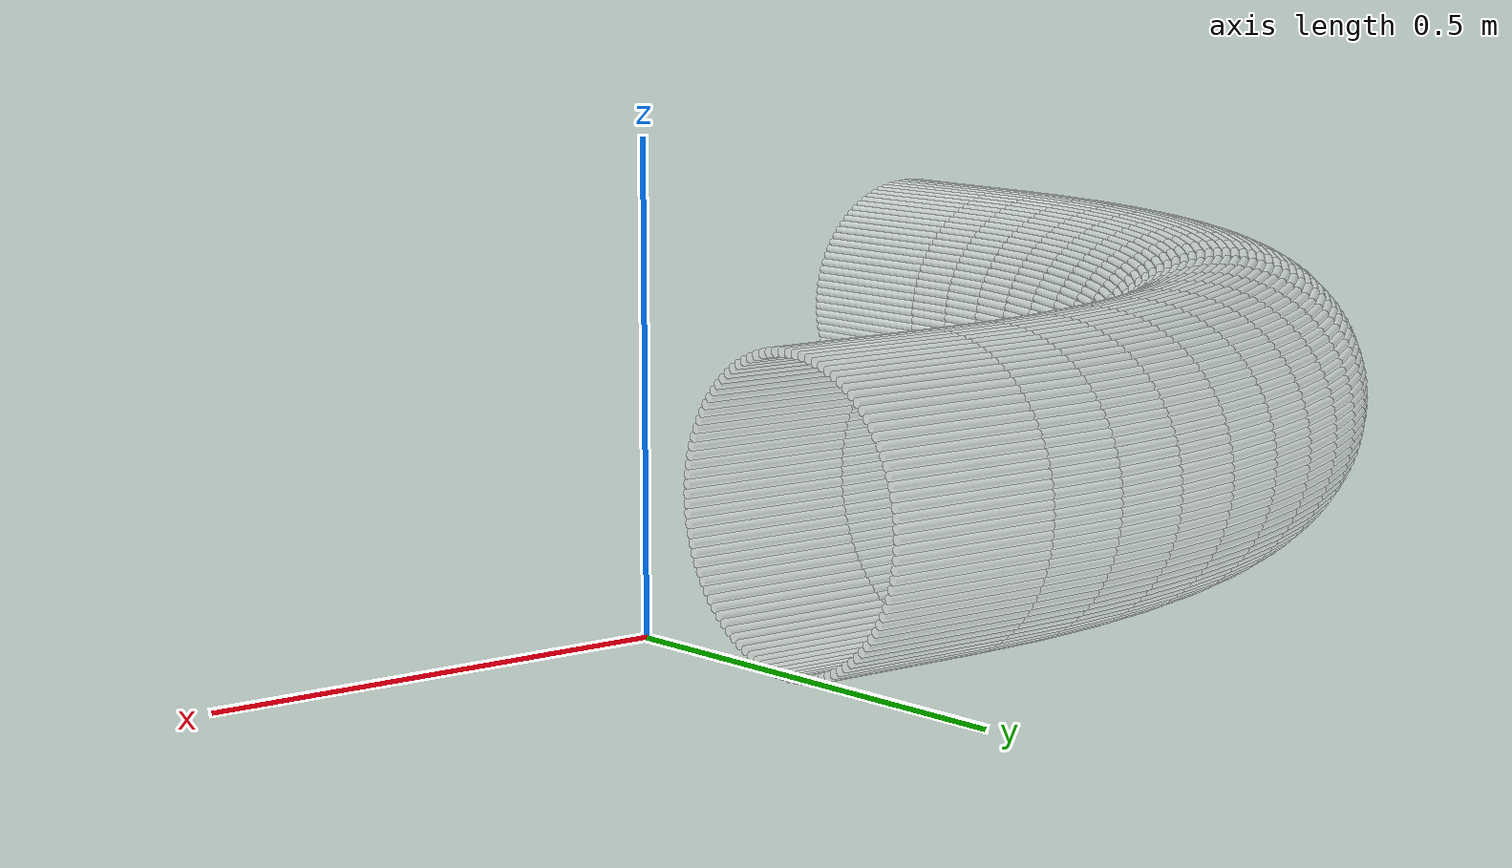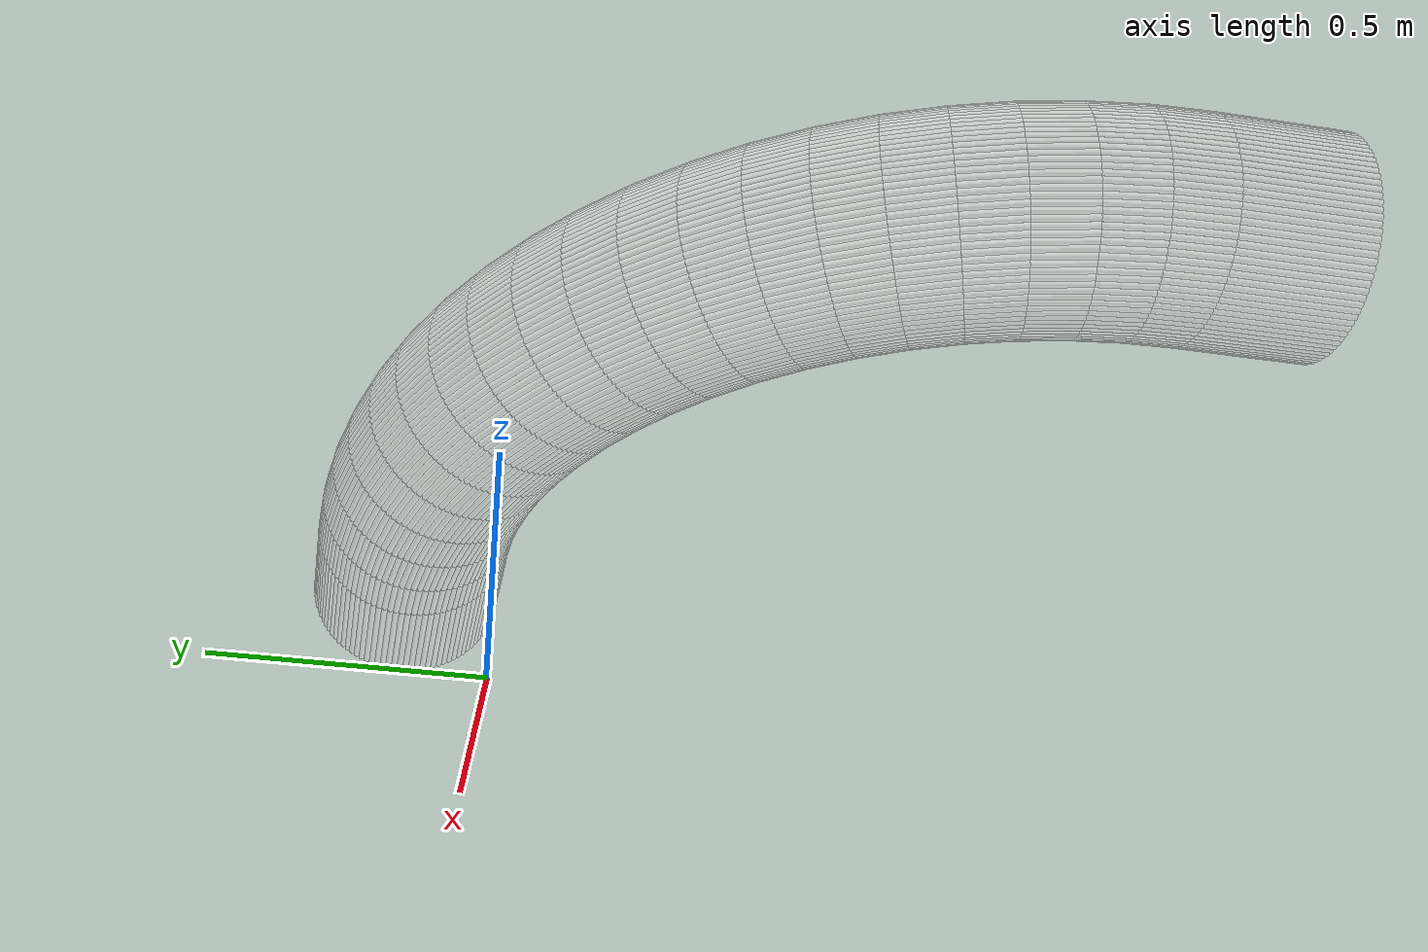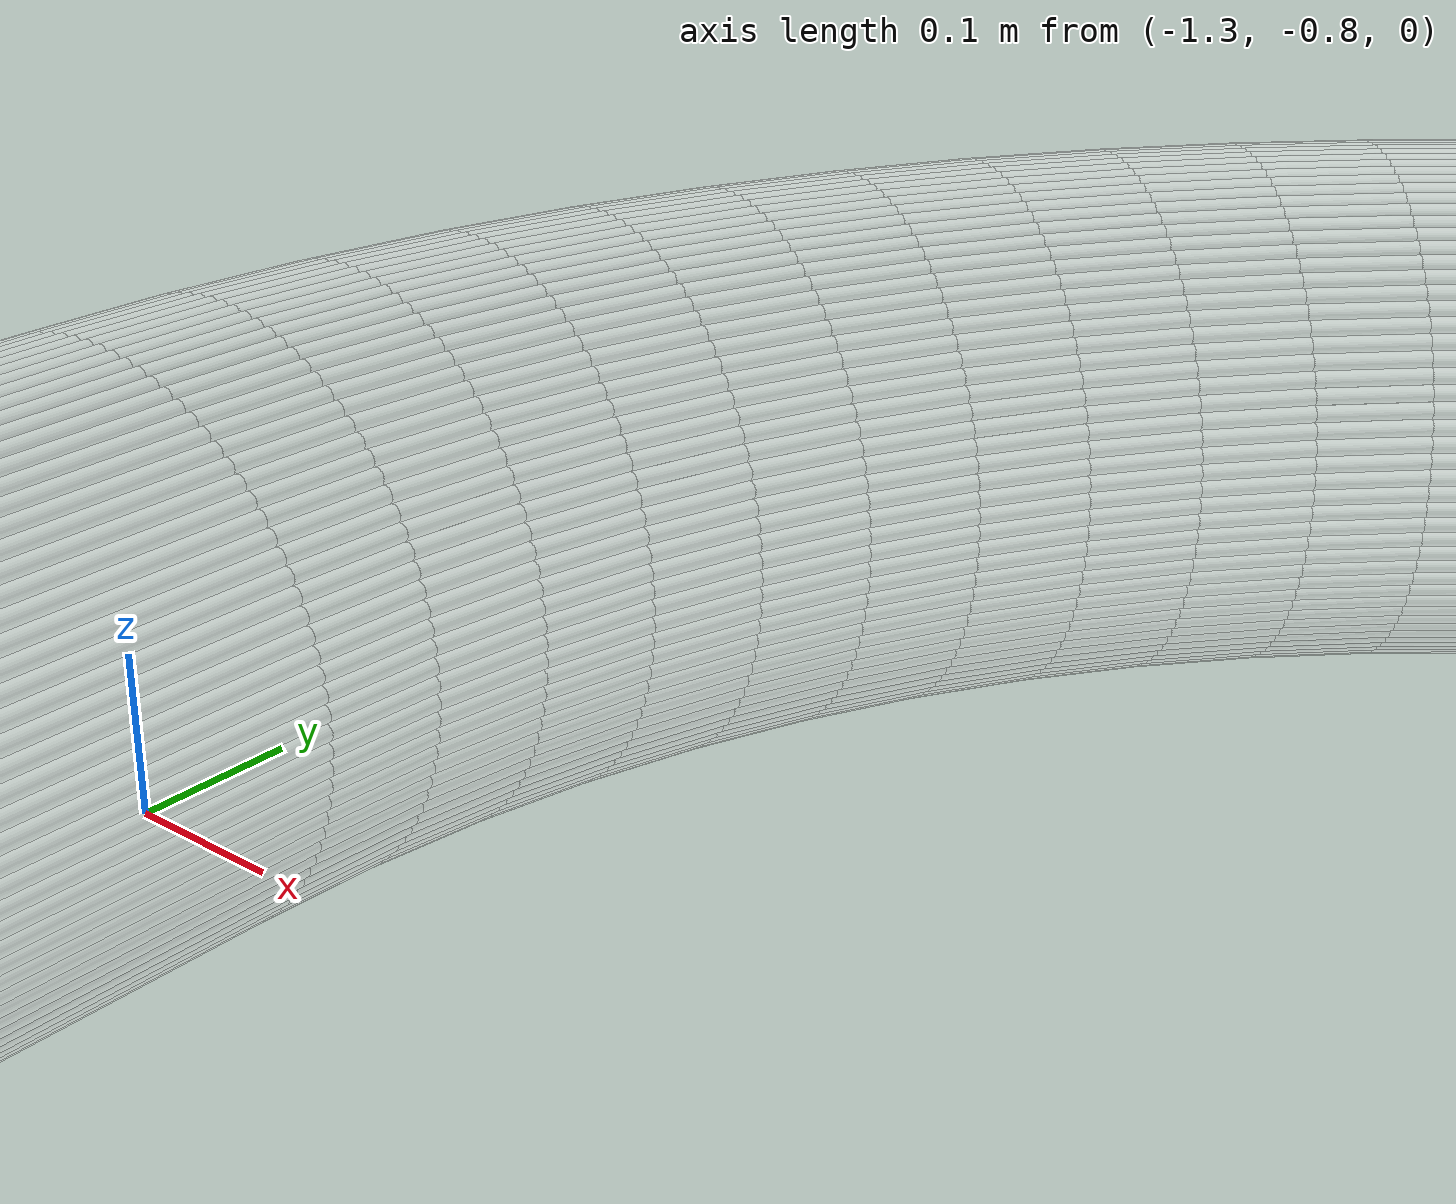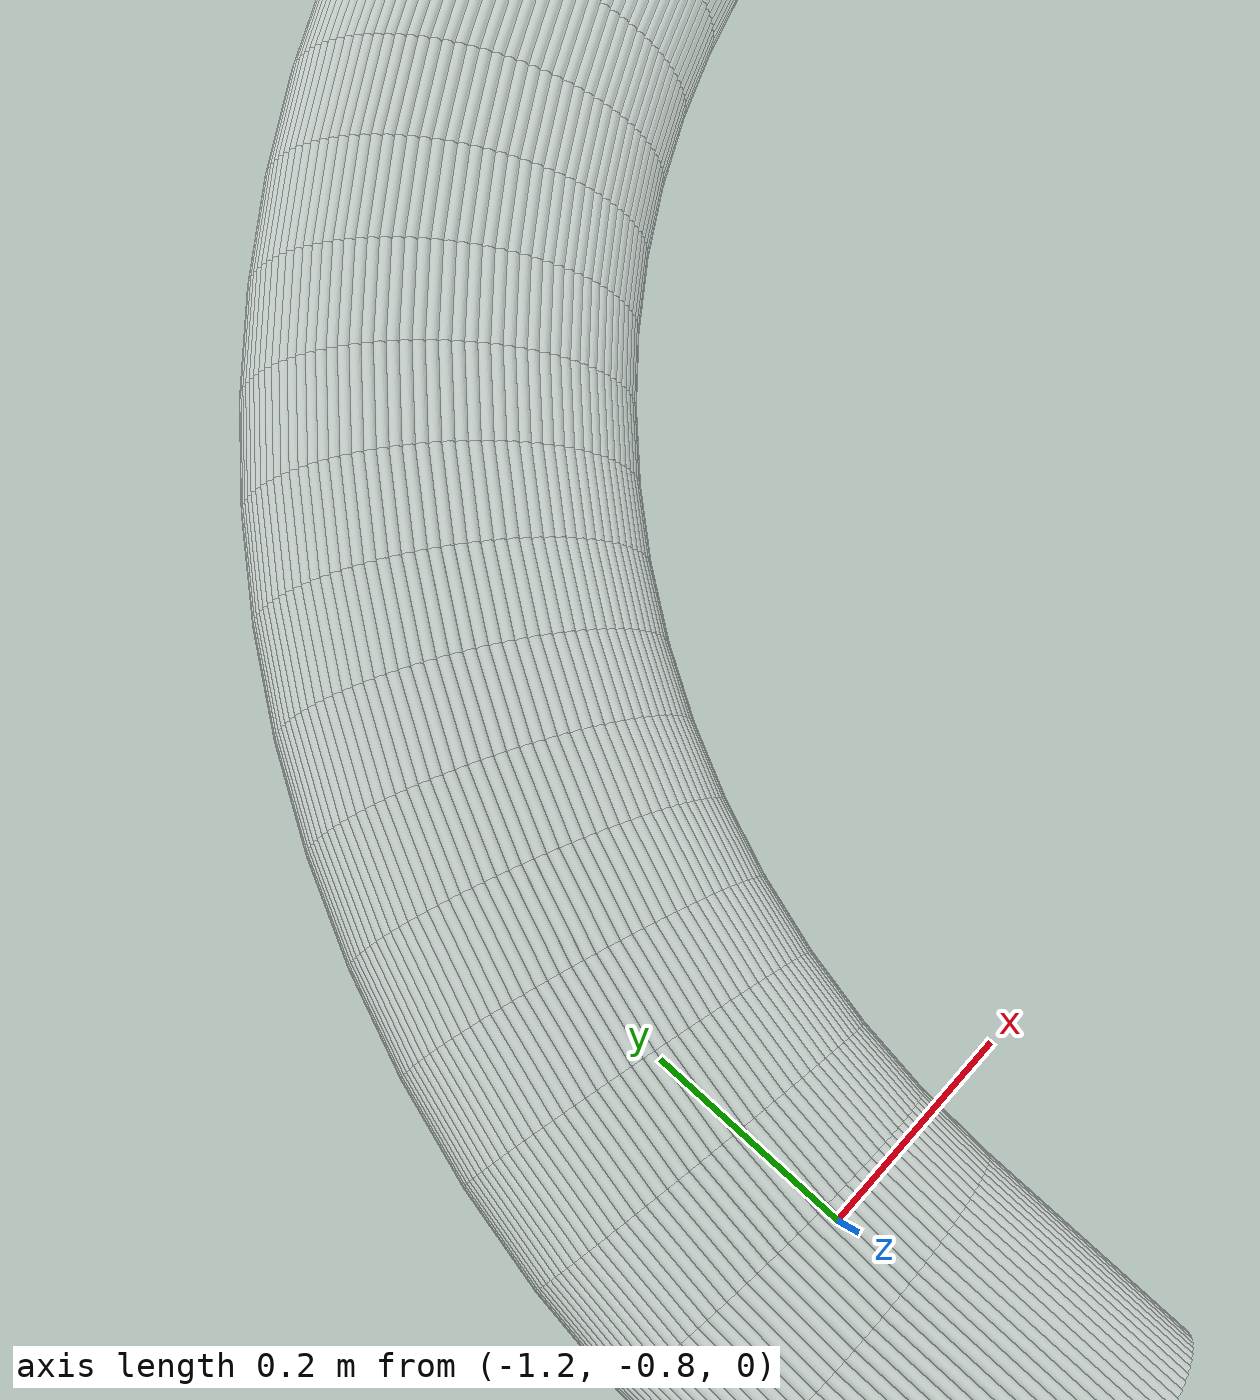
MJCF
<?xml version="1.0" encoding="utf-8"?>
<mujoco>
   <worldbody>
   <body pos="-0.25 -0.84 -0.02" euler="0 0 90">
      <geom euler=" 0 10 0 " fromto="1.16 -0.2 0.16 1.16 0 0.16" rgba="1 1 1 0.35"
            size="0.0050257"
            type="cylinder"/>
      <geom euler=" 0 20 0 " fromto="1.1597 -0.2 0.17005 1.1597 0 0.17005"
            rgba="1 1 1 0.35"
            size="0.0050257"
            type="cylinder"/>
      <geom euler=" 0 30 0 " fromto="1.1587 -0.2 0.18005 1.1587 0 0.18005"
            rgba="1 1 1 0.35"
            size="0.0050257"
            type="cylinder"/>
      <geom euler=" 0 40 0 " fromto="1.1572 -0.2 0.18998 1.1572 0 0.18998"
            rgba="1 1 1 0.35"
            size="0.0050257"
            type="cylinder"/>
      <geom euler=" 0 50 0 " fromto="1.155 -0.2 0.19979 1.155 0 0.19979" rgba="1 1 1 0.35"
            size="0.0050257"
            type="cylinder"/>
      <geom euler=" 0 60 0 " fromto="1.1522 -0.2 0.20944 1.1522 0 0.20944"
            rgba="1 1 1 0.35"
            size="0.0050257"
            type="cylinder"/>
      <geom euler=" 0 70 0 " fromto="1.1488 -0.2 0.2189 1.1488 0 0.2189" rgba="1 1 1 0.35"
            size="0.0050257"
            type="cylinder"/>
      <geom euler=" 0 80 0 " fromto="1.1448 -0.2 0.22812 1.1448 0 0.22812"
            rgba="1 1 1 0.35"
            size="0.0050257"
            type="cylinder"/>
      <geom euler=" 0 90 0 " fromto="1.1402 -0.2 0.23708 1.1402 0 0.23708"
            rgba="1 1 1 0.35"
            size="0.0050257"
            type="cylinder"/>
      <geom euler=" 0 100 0 " fromto="1.1351 -0.2 0.24573 1.1351 0 0.24573"
            rgba="1 1 1 0.35"
            size="0.0050257"
            type="cylinder"/>
      <geom euler=" 0 110 0 " fromto="1.1294 -0.2 0.25405 1.1294 0 0.25405"
            rgba="1 1 1 0.35"
            size="0.0050257"
            type="cylinder"/>
      <geom euler=" 0 120 0 " fromto="1.1233 -0.2 0.26199 1.1233 0 0.26199"
            rgba="1 1 1 0.35"
            size="0.0050257"
            type="cylinder"/>
      <geom euler=" 0 130 0 " fromto="1.1166 -0.2 0.26953 1.1166 0 0.26953"
            rgba="1 1 1 0.35"
            size="0.0050257"
            type="cylinder"/>
      <geom euler=" 0 140 0 " fromto="1.1095 -0.2 0.27663 1.1095 0 0.27663"
            rgba="1 1 1 0.35"
            size="0.0050257"
            type="cylinder"/>
      <geom euler=" 0 150 0 " fromto="1.102 -0.2 0.28328 1.102 0 0.28328" rgba="1 1 1 0.35"
            size="0.0050257"
            type="cylinder"/>
      <geom euler=" 0 160 0 " fromto="1.094 -0.2 0.28944 1.094 0 0.28944" rgba="1 1 1 0.35"
            size="0.0050257"
            type="cylinder"/>
      <geom euler=" 0 170 0 " fromto="1.0857 -0.2 0.29509 1.0857 0 0.29509"
            rgba="1 1 1 0.35"
            size="0.0050257"
            type="cylinder"/>
      <geom euler=" 0 180 0 " fromto="1.0771 -0.2 0.30021 1.0771 0 0.30021"
            rgba="1 1 1 0.35"
            size="0.0050257"
            type="cylinder"/>
      <geom euler=" 0 190 0 " fromto="1.0681 -0.2 0.30477 1.0681 0 0.30477"
            rgba="1 1 1 0.35"
            size="0.0050257"
            type="cylinder"/>
      <geom euler=" 0 200 0 " fromto="1.0589 -0.2 0.30876 1.0589 0 0.30876"
            rgba="1 1 1 0.35"
            size="0.0050257"
            type="cylinder"/>
      <geom euler=" 0 210 0 " fromto="1.0494 -0.2 0.31217 1.0494 0 0.31217"
            rgba="1 1 1 0.35"
            size="0.0050257"
            type="cylinder"/>
      <geom euler=" 0 220 0 " fromto="1.0398 -0.2 0.31497 1.0398 0 0.31497"
            rgba="1 1 1 0.35"
            size="0.0050257"
            type="cylinder"/>
      <geom euler=" 0 230 0 " fromto="1.03 -0.2 0.31717 1.03 0 0.31717" rgba="1 1 1 0.35"
            size="0.0050257"
            type="cylinder"/>
      <geom euler=" 0 240 0 " fromto="1.0201 -0.2 0.31874 1.0201 0 0.31874"
            rgba="1 1 1 0.35"
            size="0.0050257"
            type="cylinder"/>
      <geom euler=" 0 250 0 " fromto="1.01 -0.2 0.31968 1.01 0 0.31968" rgba="1 1 1 0.35"
            size="0.0050257"
            type="cylinder"/>
      <geom euler=" 0 260 0 " fromto="1 -0.2 0.32 1 0 0.32" rgba="1 1 1 0.35"
            size="0.0050257"
            type="cylinder"/>
      <geom euler=" 0 270 0 " fromto="0.98995 -0.2 0.31968 0.98995 0 0.31968"
            rgba="1 1 1 0.35"
            size="0.0050257"
            type="cylinder"/>
      <geom euler=" 0 280 0 " fromto="0.97995 -0.2 0.31874 0.97995 0 0.31874"
            rgba="1 1 1 0.35"
            size="0.0050257"
            type="cylinder"/>
      <geom euler=" 0 290 0 " fromto="0.97002 -0.2 0.31717 0.97002 0 0.31717"
            rgba="1 1 1 0.35"
            size="0.0050257"
            type="cylinder"/>
      <geom euler=" 0 300 0 " fromto="0.96021 -0.2 0.31497 0.96021 0 0.31497"
            rgba="1 1 1 0.35"
            size="0.0050257"
            type="cylinder"/>
      <geom euler=" 0 310 0 " fromto="0.95056 -0.2 0.31217 0.95056 0 0.31217"
            rgba="1 1 1 0.35"
            size="0.0050257"
            type="cylinder"/>
      <geom euler=" 0 320 0 " fromto="0.9411 -0.2 0.30876 0.9411 0 0.30876"
            rgba="1 1 1 0.35"
            size="0.0050257"
            type="cylinder"/>
      <geom euler=" 0 330 0 " fromto="0.93188 -0.2 0.30477 0.93188 0 0.30477"
            rgba="1 1 1 0.35"
            size="0.0050257"
            type="cylinder"/>
      <geom euler=" 0 340 0 " fromto="0.92292 -0.2 0.30021 0.92292 0 0.30021"
            rgba="1 1 1 0.35"
            size="0.0050257"
            type="cylinder"/>
      <geom euler=" 0 350 0 " fromto="0.91427 -0.2 0.29509 0.91427 0 0.29509"
            rgba="1 1 1 0.35"
            size="0.0050257"
            type="cylinder"/>
      <geom euler=" 0 360 0 " fromto="0.90595 -0.2 0.28944 0.90595 0 0.28944"
            rgba="1 1 1 0.35"
            size="0.0050257"
            type="cylinder"/>
      <geom euler=" 0 370 0 " fromto="0.89801 -0.2 0.28328 0.89801 0 0.28328"
            rgba="1 1 1 0.35"
            size="0.0050257"
            type="cylinder"/>
      <geom euler=" 0 380 0 " fromto="0.89047 -0.2 0.27663 0.89047 0 0.27663"
            rgba="1 1 1 0.35"
            size="0.0050257"
            type="cylinder"/>
      <geom euler=" 0 390 0 " fromto="0.88337 -0.2 0.26953 0.88337 0 0.26953"
            rgba="1 1 1 0.35"
            size="0.0050257"
            type="cylinder"/>
      <geom euler=" 0 400 0 " fromto="0.87672 -0.2 0.26199 0.87672 0 0.26199"
            rgba="1 1 1 0.35"
            size="0.0050257"
            type="cylinder"/>
      <geom euler=" 0 410 0 " fromto="0.87056 -0.2 0.25405 0.87056 0 0.25405"
            rgba="1 1 1 0.35"
            size="0.0050257"
            type="cylinder"/>
      <geom euler=" 0 420 0 " fromto="0.86491 -0.2 0.24573 0.86491 0 0.24573"
            rgba="1 1 1 0.35"
            size="0.0050257"
            type="cylinder"/>
      <geom euler=" 0 430 0 " fromto="0.85979 -0.2 0.23708 0.85979 0 0.23708"
            rgba="1 1 1 0.35"
            size="0.0050257"
            type="cylinder"/>
      <geom euler=" 0 440 0 " fromto="0.85523 -0.2 0.22812 0.85523 0 0.22812"
            rgba="1 1 1 0.35"
            size="0.0050257"
            type="cylinder"/>
      <geom euler=" 0 450 0 " fromto="0.85124 -0.2 0.2189 0.85124 0 0.2189"
            rgba="1 1 1 0.35"
            size="0.0050257"
            type="cylinder"/>
      <geom euler=" 0 460 0 " fromto="0.84783 -0.2 0.20944 0.84783 0 0.20944"
            rgba="1 1 1 0.35"
            size="0.0050257"
            type="cylinder"/>
      <geom euler=" 0 470 0 " fromto="0.84503 -0.2 0.19979 0.84503 0 0.19979"
            rgba="1 1 1 0.35"
            size="0.0050257"
            type="cylinder"/>
      <geom euler=" 0 480 0 " fromto="0.84283 -0.2 0.18998 0.84283 0 0.18998"
            rgba="1 1 1 0.35"
            size="0.0050257"
            type="cylinder"/>
      <geom euler=" 0 490 0 " fromto="0.84126 -0.2 0.18005 0.84126 0 0.18005"
            rgba="1 1 1 0.35"
            size="0.0050257"
            type="cylinder"/>
      <geom euler=" 0 500 0 " fromto="0.84032 -0.2 0.17005 0.84032 0 0.17005"
            rgba="1 1 1 0.35"
            size="0.0050257"
            type="cylinder"/>
      <geom euler=" 0 510 0 " fromto="0.84 -0.2 0.16 0.84 0 0.16" rgba="1 1 1 0.35"
            size="0.0050257"
            type="cylinder"/>
      <geom euler=" 0 520 0 " fromto="0.84032 -0.2 0.14995 0.84032 0 0.14995"
            rgba="1 1 1 0.35"
            size="0.0050257"
            type="cylinder"/>
      <geom euler=" 0 530 0 " fromto="0.84126 -0.2 0.13995 0.84126 0 0.13995"
            rgba="1 1 1 0.35"
            size="0.0050257"
            type="cylinder"/>
      <geom euler=" 0 540 0 " fromto="0.84283 -0.2 0.13002 0.84283 0 0.13002"
            rgba="1 1 1 0.35"
            size="0.0050257"
            type="cylinder"/>
      <geom euler=" 0 550 0 " fromto="0.84503 -0.2 0.12021 0.84503 0 0.12021"
            rgba="1 1 1 0.35"
            size="0.0050257"
            type="cylinder"/>
      <geom euler=" 0 560 0 " fromto="0.84783 -0.2 0.11056 0.84783 0 0.11056"
            rgba="1 1 1 0.35"
            size="0.0050257"
            type="cylinder"/>
      <geom euler=" 0 570 0 " fromto="0.85124 -0.2 0.1011 0.85124 0 0.1011"
            rgba="1 1 1 0.35"
            size="0.0050257"
            type="cylinder"/>
      <geom euler=" 0 580 0 " fromto="0.85523 -0.2 0.091875 0.85523 0 0.091875"
            rgba="1 1 1 0.35"
            size="0.0050257"
            type="cylinder"/>
      <geom euler=" 0 590 0 " fromto="0.85979 -0.2 0.082919 0.85979 0 0.082919"
            rgba="1 1 1 0.35"
            size="0.0050257"
            type="cylinder"/>
      <geom euler=" 0 600 0 " fromto="0.86491 -0.2 0.074268 0.86491 0 0.074268"
            rgba="1 1 1 0.35"
            size="0.0050257"
            type="cylinder"/>
      <geom euler=" 0 610 0 " fromto="0.87056 -0.2 0.065954 0.87056 0 0.065954"
            rgba="1 1 1 0.35"
            size="0.0050257"
            type="cylinder"/>
      <geom euler=" 0 620 0 " fromto="0.87672 -0.2 0.058012 0.87672 0 0.058012"
            rgba="1 1 1 0.35"
            size="0.0050257"
            type="cylinder"/>
      <geom euler=" 0 630 0 " fromto="0.88337 -0.2 0.050472 0.88337 0 0.050472"
            rgba="1 1 1 0.35"
            size="0.0050257"
            type="cylinder"/>
      <geom euler=" 0 640 0 " fromto="0.89047 -0.2 0.043365 0.89047 0 0.043365"
            rgba="1 1 1 0.35"
            size="0.0050257"
            type="cylinder"/>
      <geom euler=" 0 650 0 " fromto="0.89801 -0.2 0.036718 0.89801 0 0.036718"
            rgba="1 1 1 0.35"
            size="0.0050257"
            type="cylinder"/>
      <geom euler=" 0 660 0 " fromto="0.90595 -0.2 0.030557 0.90595 0 0.030557"
            rgba="1 1 1 0.35"
            size="0.0050257"
            type="cylinder"/>
      <geom euler=" 0 670 0 " fromto="0.91427 -0.2 0.024908 0.91427 0 0.024908"
            rgba="1 1 1 0.35"
            size="0.0050257"
            type="cylinder"/>
      <geom euler=" 0 680 0 " fromto="0.92292 -0.2 0.019791 0.92292 0 0.019791"
            rgba="1 1 1 0.35"
            size="0.0050257"
            type="cylinder"/>
      <geom euler=" 0 690 0 " fromto="0.93188 -0.2 0.015228 0.93188 0 0.015228"
            rgba="1 1 1 0.35"
            size="0.0050257"
            type="cylinder"/>
      <geom euler=" 0 700 0 " fromto="0.9411 -0.2 0.011236 0.9411 0 0.011236"
            rgba="1 1 1 0.35"
            size="0.0050257"
            type="cylinder"/>
      <geom euler=" 0 710 0 " fromto="0.95056 -0.2 0.007831 0.95056 0 0.007831"
            rgba="1 1 1 0.35"
            size="0.0050257"
            type="cylinder"/>
      <geom euler=" 0 720 0 " fromto="0.96021 -0.2 0.0050267 0.96021 0 0.0050267"
            rgba="1 1 1 0.35"
            size="0.0050257"
            type="cylinder"/>
      <geom euler=" 0 730 0 " fromto="0.97002 -0.2 0.002834 0.97002 0 0.002834"
            rgba="1 1 1 0.35"
            size="0.0050257"
            type="cylinder"/>
      <geom euler=" 0 740 0 " fromto="0.97995 -0.2 0.0012616 0.97995 0 0.0012616"
            rgba="1 1 1 0.35"
            size="0.0050257"
            type="cylinder"/>
      <geom euler=" 0 750 0 " fromto="0.98995 -0.2 0.00031572 0.98995 0 0.00031572"
            rgba="1 1 1 0.35"
            size="0.0050257"
            type="cylinder"/>
      <geom euler=" 0 760 0 " fromto="1 -0.2 0 1 0 0" rgba="1 1 1 0.35" size="0.0050257"
            type="cylinder"/>
      <geom euler=" 0 770 0 " fromto="1.01 -0.2 0.00031572 1.01 0 0.00031572"
            rgba="1 1 1 0.35"
            size="0.0050257"
            type="cylinder"/>
      <geom euler=" 0 780 0 " fromto="1.0201 -0.2 0.0012616 1.0201 0 0.0012616"
            rgba="1 1 1 0.35"
            size="0.0050257"
            type="cylinder"/>
      <geom euler=" 0 790 0 " fromto="1.03 -0.2 0.002834 1.03 0 0.002834" rgba="1 1 1 0.35"
            size="0.0050257"
            type="cylinder"/>
      <geom euler=" 0 800 0 " fromto="1.0398 -0.2 0.0050267 1.0398 0 0.0050267"
            rgba="1 1 1 0.35"
            size="0.0050257"
            type="cylinder"/>
      <geom euler=" 0 810 0 " fromto="1.0494 -0.2 0.007831 1.0494 0 0.007831"
            rgba="1 1 1 0.35"
            size="0.0050257"
            type="cylinder"/>
      <geom euler=" 0 820 0 " fromto="1.0589 -0.2 0.011236 1.0589 0 0.011236"
            rgba="1 1 1 0.35"
            size="0.0050257"
            type="cylinder"/>
      <geom euler=" 0 830 0 " fromto="1.0681 -0.2 0.015228 1.0681 0 0.015228"
            rgba="1 1 1 0.35"
            size="0.0050257"
            type="cylinder"/>
      <geom euler=" 0 840 0 " fromto="1.0771 -0.2 0.019791 1.0771 0 0.019791"
            rgba="1 1 1 0.35"
            size="0.0050257"
            type="cylinder"/>
      <geom euler=" 0 850 0 " fromto="1.0857 -0.2 0.024908 1.0857 0 0.024908"
            rgba="1 1 1 0.35"
            size="0.0050257"
            type="cylinder"/>
      <geom euler=" 0 860 0 " fromto="1.094 -0.2 0.030557 1.094 0 0.030557"
            rgba="1 1 1 0.35"
            size="0.0050257"
            type="cylinder"/>
      <geom euler=" 0 870 0 " fromto="1.102 -0.2 0.036718 1.102 0 0.036718"
            rgba="1 1 1 0.35"
            size="0.0050257"
            type="cylinder"/>
      <geom euler=" 0 880 0 " fromto="1.1095 -0.2 0.043365 1.1095 0 0.043365"
            rgba="1 1 1 0.35"
            size="0.0050257"
            type="cylinder"/>
      <geom euler=" 0 890 0 " fromto="1.1166 -0.2 0.050472 1.1166 0 0.050472"
            rgba="1 1 1 0.35"
            size="0.0050257"
            type="cylinder"/>
      <geom euler=" 0 900 0 " fromto="1.1233 -0.2 0.058012 1.1233 0 0.058012"
            rgba="1 1 1 0.35"
            size="0.0050257"
            type="cylinder"/>
      <geom euler=" 0 910 0 " fromto="1.1294 -0.2 0.065954 1.1294 0 0.065954"
            rgba="1 1 1 0.35"
            size="0.0050257"
            type="cylinder"/>
      <geom euler=" 0 920 0 " fromto="1.1351 -0.2 0.074268 1.1351 0 0.074268"
            rgba="1 1 1 0.35"
            size="0.0050257"
            type="cylinder"/>
      <geom euler=" 0 930 0 " fromto="1.1402 -0.2 0.082919 1.1402 0 0.082919"
            rgba="1 1 1 0.35"
            size="0.0050257"
            type="cylinder"/>
      <geom euler=" 0 940 0 " fromto="1.1448 -0.2 0.091875 1.1448 0 0.091875"
            rgba="1 1 1 0.35"
            size="0.0050257"
            type="cylinder"/>
      <geom euler=" 0 950 0 " fromto="1.1488 -0.2 0.1011 1.1488 0 0.1011" rgba="1 1 1 0.35"
            size="0.0050257"
            type="cylinder"/>
      <geom euler=" 0 960 0 " fromto="1.1522 -0.2 0.11056 1.1522 0 0.11056"
            rgba="1 1 1 0.35"
            size="0.0050257"
            type="cylinder"/>
      <geom euler=" 0 970 0 " fromto="1.155 -0.2 0.12021 1.155 0 0.12021" rgba="1 1 1 0.35"
            size="0.0050257"
            type="cylinder"/>
      <geom euler=" 0 980 0 " fromto="1.1572 -0.2 0.13002 1.1572 0 0.13002"
            rgba="1 1 1 0.35"
            size="0.0050257"
            type="cylinder"/>
      <geom euler=" 0 990 0 " fromto="1.1587 -0.2 0.13995 1.1587 0 0.13995"
            rgba="1 1 1 0.35"
            size="0.0050257"
            type="cylinder"/>
      <geom euler=" 0 1000 0 " fromto="1.1597 -0.2 0.14995 1.1597 0 0.14995"
            rgba="1 1 1 0.35"
            size="0.0050257"
            type="cylinder"/>
      <geom euler=" 0 10 0 " fromto="1.16 0 0.16 1.156 0.095792 0.16" rgba="1 1 1 0.35"
            size="0.0050257"
            type="cylinder"/>
      <geom euler=" 0 20 0 " fromto="1.1597 0 0.17005 1.1557 0.095766 0.17005"
            rgba="1 1 1 0.35"
            size="0.0050257"
            type="cylinder"/>
      <geom euler=" 0 30 0 " fromto="1.1587 0 0.18005 1.1548 0.095688 0.18005"
            rgba="1 1 1 0.35"
            size="0.0050257"
            type="cylinder"/>
      <geom euler=" 0 40 0 " fromto="1.1572 0 0.18998 1.1532 0.095558 0.18998"
            rgba="1 1 1 0.35"
            size="0.0050257"
            type="cylinder"/>
      <geom euler=" 0 50 0 " fromto="1.155 0 0.19979 1.151 0.095377 0.19979"
            rgba="1 1 1 0.35"
            size="0.0050257"
            type="cylinder"/>
      <geom euler=" 0 60 0 " fromto="1.1522 0 0.20944 1.1482 0.095145 0.20944"
            rgba="1 1 1 0.35"
            size="0.0050257"
            type="cylinder"/>
      <geom euler=" 0 70 0 " fromto="1.1488 0 0.2189 1.1448 0.094864 0.2189"
            rgba="1 1 1 0.35"
            size="0.0050257"
            type="cylinder"/>
      <geom euler=" 0 80 0 " fromto="1.1448 0 0.22812 1.1409 0.094535 0.22812"
            rgba="1 1 1 0.35"
            size="0.0050257"
            type="cylinder"/>
      <geom euler=" 0 90 0 " fromto="1.1402 0 0.23708 1.1363 0.094158 0.23708"
            rgba="1 1 1 0.35"
            size="0.0050257"
            type="cylinder"/>
      <geom euler=" 0 100 0 " fromto="1.1351 0 0.24573 1.1312 0.093735 0.24573"
            rgba="1 1 1 0.35"
            size="0.0050257"
            type="cylinder"/>
      <geom euler=" 0 110 0 " fromto="1.1294 0 0.25405 1.1256 0.093269 0.25405"
            rgba="1 1 1 0.35"
            size="0.0050257"
            type="cylinder"/>
      <geom euler=" 0 120 0 " fromto="1.1233 0 0.26199 1.1194 0.09276 0.26199"
            rgba="1 1 1 0.35"
            size="0.0050257"
            type="cylinder"/>
      <geom euler=" 0 130 0 " fromto="1.1166 0 0.26953 1.1128 0.092211 0.26953"
            rgba="1 1 1 0.35"
            size="0.0050257"
            type="cylinder"/>
      <geom euler=" 0 140 0 " fromto="1.1095 0 0.27663 1.1057 0.091624 0.27663"
            rgba="1 1 1 0.35"
            size="0.0050257"
            type="cylinder"/>
      <geom euler=" 0 150 0 " fromto="1.102 0 0.28328 1.0982 0.091001 0.28328"
            rgba="1 1 1 0.35"
            size="0.0050257"
            type="cylinder"/>
      <geom euler=" 0 160 0 " fromto="1.094 0 0.28944 1.0903 0.090346 0.28944"
            rgba="1 1 1 0.35"
            size="0.0050257"
            type="cylinder"/>
      <geom euler=" 0 170 0 " fromto="1.0857 0 0.29509 1.082 0.089659 0.29509"
            rgba="1 1 1 0.35"
            size="0.0050257"
            type="cylinder"/>
      <geom euler=" 0 180 0 " fromto="1.0771 0 0.30021 1.0734 0.088945 0.30021"
            rgba="1 1 1 0.35"
            size="0.0050257"
            type="cylinder"/>
      <geom euler=" 0 190 0 " fromto="1.0681 0 0.30477 1.0645 0.088205 0.30477"
            rgba="1 1 1 0.35"
            size="0.0050257"
            type="cylinder"/>
      <geom euler=" 0 200 0 " fromto="1.0589 0 0.30876 1.0553 0.087443 0.30876"
            rgba="1 1 1 0.35"
            size="0.0050257"
            type="cylinder"/>
      <geom euler=" 0 210 0 " fromto="1.0494 0 0.31217 1.0459 0.086662 0.31217"
            rgba="1 1 1 0.35"
            size="0.0050257"
            type="cylinder"/>
      <geom euler=" 0 220 0 " fromto="1.0398 0 0.31497 1.0362 0.085865 0.31497"
            rgba="1 1 1 0.35"
            size="0.0050257"
            type="cylinder"/>
      <geom euler=" 0 230 0 " fromto="1.03 0 0.31717 1.0265 0.085055 0.31717"
            rgba="1 1 1 0.35"
            size="0.0050257"
            type="cylinder"/>
      <geom euler=" 0 240 0 " fromto="1.0201 0 0.31874 1.0166 0.084235 0.31874"
            rgba="1 1 1 0.35"
            size="0.0050257"
            type="cylinder"/>
      <geom euler=" 0 250 0 " fromto="1.01 0 0.31968 1.0066 0.083409 0.31968"
            rgba="1 1 1 0.35"
            size="0.0050257"
            type="cylinder"/>
      <geom euler=" 0 260 0 " fromto="1 0 0.32 0.99658 0.082579 0.32" rgba="1 1 1 0.35"
            size="0.0050257"
            type="cylinder"/>
      <geom euler=" 0 270 0 " fromto="0.98995 0 0.31968 0.98657 0.08175 0.31968"
            rgba="1 1 1 0.35"
            size="0.0050257"
            type="cylinder"/>
      <geom euler=" 0 280 0 " fromto="0.97995 0 0.31874 0.9766 0.080923 0.31874"
            rgba="1 1 1 0.35"
            size="0.0050257"
            type="cylinder"/>
      <geom euler=" 0 290 0 " fromto="0.97002 0 0.31717 0.96671 0.080104 0.31717"
            rgba="1 1 1 0.35"
            size="0.0050257"
            type="cylinder"/>
      <geom euler=" 0 300 0 " fromto="0.96021 0 0.31497 0.95693 0.079293 0.31497"
            rgba="1 1 1 0.35"
            size="0.0050257"
            type="cylinder"/>
      <geom euler=" 0 310 0 " fromto="0.95056 0 0.31217 0.94731 0.078496 0.31217"
            rgba="1 1 1 0.35"
            size="0.0050257"
            type="cylinder"/>
      <geom euler=" 0 320 0 " fromto="0.9411 0 0.30876 0.93789 0.077715 0.30876"
            rgba="1 1 1 0.35"
            size="0.0050257"
            type="cylinder"/>
      <geom euler=" 0 330 0 " fromto="0.93188 0 0.30477 0.92869 0.076954 0.30477"
            rgba="1 1 1 0.35"
            size="0.0050257"
            type="cylinder"/>
      <geom euler=" 0 340 0 " fromto="0.92292 0 0.30021 0.91977 0.076214 0.30021"
            rgba="1 1 1 0.35"
            size="0.0050257"
            type="cylinder"/>
      <geom euler=" 0 350 0 " fromto="0.91427 0 0.29509 0.91115 0.0755 0.29509"
            rgba="1 1 1 0.35"
            size="0.0050257"
            type="cylinder"/>
      <geom euler=" 0 360 0 " fromto="0.90595 0 0.28944 0.90286 0.074813 0.28944"
            rgba="1 1 1 0.35"
            size="0.0050257"
            type="cylinder"/>
      <geom euler=" 0 370 0 " fromto="0.89801 0 0.28328 0.89494 0.074157 0.28328"
            rgba="1 1 1 0.35"
            size="0.0050257"
            type="cylinder"/>
      <geom euler=" 0 380 0 " fromto="0.89047 0 0.27663 0.88743 0.073535 0.27663"
            rgba="1 1 1 0.35"
            size="0.0050257"
            type="cylinder"/>
      <geom euler=" 0 390 0 " fromto="0.88337 0 0.26953 0.88035 0.072948 0.26953"
            rgba="1 1 1 0.35"
            size="0.0050257"
            type="cylinder"/>
      <geom euler=" 0 400 0 " fromto="0.87672 0 0.26199 0.87372 0.072399 0.26199"
            rgba="1 1 1 0.35"
            size="0.0050257"
            type="cylinder"/>
      <geom euler=" 0 410 0 " fromto="0.87056 0 0.25405 0.86758 0.07189 0.25405"
            rgba="1 1 1 0.35"
            size="0.0050257"
            type="cylinder"/>
      <geom euler=" 0 420 0 " fromto="0.86491 0 0.24573 0.86195 0.071423 0.24573"
            rgba="1 1 1 0.35"
            size="0.0050257"
            type="cylinder"/>
      <geom euler=" 0 430 0 " fromto="0.85979 0 0.23708 0.85685 0.071001 0.23708"
            rgba="1 1 1 0.35"
            size="0.0050257"
            type="cylinder"/>
      <geom euler=" 0 440 0 " fromto="0.85523 0 0.22812 0.85231 0.070624 0.22812"
            rgba="1 1 1 0.35"
            size="0.0050257"
            type="cylinder"/>
      <geom euler=" 0 450 0 " fromto="0.85124 0 0.2189 0.84833 0.070294 0.2189"
            rgba="1 1 1 0.35"
            size="0.0050257"
            type="cylinder"/>
      <geom euler=" 0 460 0 " fromto="0.84783 0 0.20944 0.84494 0.070013 0.20944"
            rgba="1 1 1 0.35"
            size="0.0050257"
            type="cylinder"/>
      <geom euler=" 0 470 0 " fromto="0.84503 0 0.19979 0.84214 0.069782 0.19979"
            rgba="1 1 1 0.35"
            size="0.0050257"
            type="cylinder"/>
      <geom euler=" 0 480 0 " fromto="0.84283 0 0.18998 0.83996 0.069601 0.18998"
            rgba="1 1 1 0.35"
            size="0.0050257"
            type="cylinder"/>
      <geom euler=" 0 490 0 " fromto="0.84126 0 0.18005 0.83839 0.069471 0.18005"
            rgba="1 1 1 0.35"
            size="0.0050257"
            type="cylinder"/>
      <geom euler=" 0 500 0 " fromto="0.84032 0 0.17005 0.83745 0.069393 0.17005"
            rgba="1 1 1 0.35"
            size="0.0050257"
            type="cylinder"/>
      <geom euler=" 0 510 0 " fromto="0.84 0 0.16 0.83713 0.069367 0.16" rgba="1 1 1 0.35"
            size="0.0050257"
            type="cylinder"/>
      <geom euler=" 0 520 0 " fromto="0.84032 0 0.14995 0.83745 0.069393 0.14995"
            rgba="1 1 1 0.35"
            size="0.0050257"
            type="cylinder"/>
      <geom euler=" 0 530 0 " fromto="0.84126 0 0.13995 0.83839 0.069471 0.13995"
            rgba="1 1 1 0.35"
            size="0.0050257"
            type="cylinder"/>
      <geom euler=" 0 540 0 " fromto="0.84283 0 0.13002 0.83996 0.069601 0.13002"
            rgba="1 1 1 0.35"
            size="0.0050257"
            type="cylinder"/>
      <geom euler=" 0 550 0 " fromto="0.84503 0 0.12021 0.84214 0.069782 0.12021"
            rgba="1 1 1 0.35"
            size="0.0050257"
            type="cylinder"/>
      <geom euler=" 0 560 0 " fromto="0.84783 0 0.11056 0.84494 0.070013 0.11056"
            rgba="1 1 1 0.35"
            size="0.0050257"
            type="cylinder"/>
      <geom euler=" 0 570 0 " fromto="0.85124 0 0.1011 0.84833 0.070294 0.1011"
            rgba="1 1 1 0.35"
            size="0.0050257"
            type="cylinder"/>
      <geom euler=" 0 580 0 " fromto="0.85523 0 0.091875 0.85231 0.070624 0.091875"
            rgba="1 1 1 0.35"
            size="0.0050257"
            type="cylinder"/>
      <geom euler=" 0 590 0 " fromto="0.85979 0 0.082919 0.85685 0.071001 0.082919"
            rgba="1 1 1 0.35"
            size="0.0050257"
            type="cylinder"/>
      <geom euler=" 0 600 0 " fromto="0.86491 0 0.074268 0.86195 0.071423 0.074268"
            rgba="1 1 1 0.35"
            size="0.0050257"
            type="cylinder"/>
      <geom euler=" 0 610 0 " fromto="0.87056 0 0.065954 0.86758 0.07189 0.065954"
            rgba="1 1 1 0.35"
            size="0.0050257"
            type="cylinder"/>
      <geom euler=" 0 620 0 " fromto="0.87672 0 0.058012 0.87372 0.072399 0.058012"
            rgba="1 1 1 0.35"
            size="0.0050257"
            type="cylinder"/>
      <geom euler=" 0 630 0 " fromto="0.88337 0 0.050472 0.88035 0.072948 0.050472"
            rgba="1 1 1 0.35"
            size="0.0050257"
            type="cylinder"/>
      <geom euler=" 0 640 0 " fromto="0.89047 0 0.043365 0.88743 0.073535 0.043365"
            rgba="1 1 1 0.35"
            size="0.0050257"
            type="cylinder"/>
      <geom euler=" 0 650 0 " fromto="0.89801 0 0.036718 0.89494 0.074157 0.036718"
            rgba="1 1 1 0.35"
            size="0.0050257"
            type="cylinder"/>
      <geom euler=" 0 660 0 " fromto="0.90595 0 0.030557 0.90286 0.074813 0.030557"
            rgba="1 1 1 0.35"
            size="0.0050257"
            type="cylinder"/>
      <geom euler=" 0 670 0 " fromto="0.91427 0 0.024908 0.91115 0.0755 0.024908"
            rgba="1 1 1 0.35"
            size="0.0050257"
            type="cylinder"/>
      <geom euler=" 0 680 0 " fromto="0.92292 0 0.019791 0.91977 0.076214 0.019791"
            rgba="1 1 1 0.35"
            size="0.0050257"
            type="cylinder"/>
      <geom euler=" 0 690 0 " fromto="0.93188 0 0.015228 0.92869 0.076954 0.015228"
            rgba="1 1 1 0.35"
            size="0.0050257"
            type="cylinder"/>
      <geom euler=" 0 700 0 " fromto="0.9411 0 0.011236 0.93789 0.077715 0.011236"
            rgba="1 1 1 0.35"
            size="0.0050257"
            type="cylinder"/>
      <geom euler=" 0 710 0 " fromto="0.95056 0 0.007831 0.94731 0.078496 0.007831"
            rgba="1 1 1 0.35"
            size="0.0050257"
            type="cylinder"/>
      <geom euler=" 0 720 0 " fromto="0.96021 0 0.0050267 0.95693 0.079293 0.0050267"
            rgba="1 1 1 0.35"
            size="0.0050257"
            type="cylinder"/>
      <geom euler=" 0 730 0 " fromto="0.97002 0 0.002834 0.96671 0.080104 0.002834"
            rgba="1 1 1 0.35"
            size="0.0050257"
            type="cylinder"/>
      <geom euler=" 0 740 0 " fromto="0.97995 0 0.0012616 0.9766 0.080923 0.0012616"
            rgba="1 1 1 0.35"
            size="0.0050257"
            type="cylinder"/>
      <geom euler=" 0 750 0 " fromto="0.98995 0 0.00031572 0.98657 0.08175 0.00031572"
            rgba="1 1 1 0.35"
            size="0.0050257"
            type="cylinder"/>
      <geom euler=" 0 760 0 " fromto="1 0 0 0.99658 0.082579 0" rgba="1 1 1 0.35"
            size="0.0050257"
            type="cylinder"/>
      <geom euler=" 0 770 0 " fromto="1.01 0 0.00031572 1.0066 0.083409 0.00031572"
            rgba="1 1 1 0.35"
            size="0.0050257"
            type="cylinder"/>
      <geom euler=" 0 780 0 " fromto="1.0201 0 0.0012616 1.0166 0.084235 0.0012616"
            rgba="1 1 1 0.35"
            size="0.0050257"
            type="cylinder"/>
      <geom euler=" 0 790 0 " fromto="1.03 0 0.002834 1.0265 0.085055 0.002834"
            rgba="1 1 1 0.35"
            size="0.0050257"
            type="cylinder"/>
      <geom euler=" 0 800 0 " fromto="1.0398 0 0.0050267 1.0362 0.085865 0.0050267"
            rgba="1 1 1 0.35"
            size="0.0050257"
            type="cylinder"/>
      <geom euler=" 0 810 0 " fromto="1.0494 0 0.007831 1.0459 0.086662 0.007831"
            rgba="1 1 1 0.35"
            size="0.0050257"
            type="cylinder"/>
      <geom euler=" 0 820 0 " fromto="1.0589 0 0.011236 1.0553 0.087443 0.011236"
            rgba="1 1 1 0.35"
            size="0.0050257"
            type="cylinder"/>
      <geom euler=" 0 830 0 " fromto="1.0681 0 0.015228 1.0645 0.088205 0.015228"
            rgba="1 1 1 0.35"
            size="0.0050257"
            type="cylinder"/>
      <geom euler=" 0 840 0 " fromto="1.0771 0 0.019791 1.0734 0.088945 0.019791"
            rgba="1 1 1 0.35"
            size="0.0050257"
            type="cylinder"/>
      <geom euler=" 0 850 0 " fromto="1.0857 0 0.024908 1.082 0.089659 0.024908"
            rgba="1 1 1 0.35"
            size="0.0050257"
            type="cylinder"/>
      <geom euler=" 0 860 0 " fromto="1.094 0 0.030557 1.0903 0.090346 0.030557"
            rgba="1 1 1 0.35"
            size="0.0050257"
            type="cylinder"/>
      <geom euler=" 0 870 0 " fromto="1.102 0 0.036718 1.0982 0.091001 0.036718"
            rgba="1 1 1 0.35"
            size="0.0050257"
            type="cylinder"/>
      <geom euler=" 0 880 0 " fromto="1.1095 0 0.043365 1.1057 0.091624 0.043365"
            rgba="1 1 1 0.35"
            size="0.0050257"
            type="cylinder"/>
      <geom euler=" 0 890 0 " fromto="1.1166 0 0.050472 1.1128 0.092211 0.050472"
            rgba="1 1 1 0.35"
            size="0.0050257"
            type="cylinder"/>
      <geom euler=" 0 900 0 " fromto="1.1233 0 0.058012 1.1194 0.09276 0.058012"
            rgba="1 1 1 0.35"
            size="0.0050257"
            type="cylinder"/>
      <geom euler=" 0 910 0 " fromto="1.1294 0 0.065954 1.1256 0.093269 0.065954"
            rgba="1 1 1 0.35"
            size="0.0050257"
            type="cylinder"/>
      <geom euler=" 0 920 0 " fromto="1.1351 0 0.074268 1.1312 0.093735 0.074268"
            rgba="1 1 1 0.35"
            size="0.0050257"
            type="cylinder"/>
      <geom euler=" 0 930 0 " fromto="1.1402 0 0.082919 1.1363 0.094158 0.082919"
            rgba="1 1 1 0.35"
            size="0.0050257"
            type="cylinder"/>
      <geom euler=" 0 940 0 " fromto="1.1448 0 0.091875 1.1409 0.094535 0.091875"
            rgba="1 1 1 0.35"
            size="0.0050257"
            type="cylinder"/>
      <geom euler=" 0 950 0 " fromto="1.1488 0 0.1011 1.1448 0.094864 0.1011"
            rgba="1 1 1 0.35"
            size="0.0050257"
            type="cylinder"/>
      <geom euler=" 0 960 0 " fromto="1.1522 0 0.11056 1.1482 0.095145 0.11056"
            rgba="1 1 1 0.35"
            size="0.0050257"
            type="cylinder"/>
      <geom euler=" 0 970 0 " fromto="1.155 0 0.12021 1.151 0.095377 0.12021"
            rgba="1 1 1 0.35"
            size="0.0050257"
            type="cylinder"/>
      <geom euler=" 0 980 0 " fromto="1.1572 0 0.13002 1.1532 0.095558 0.13002"
            rgba="1 1 1 0.35"
            size="0.0050257"
            type="cylinder"/>
      <geom euler=" 0 990 0 " fromto="1.1587 0 0.13995 1.1548 0.095688 0.13995"
            rgba="1 1 1 0.35"
            size="0.0050257"
            type="cylinder"/>
      <geom euler=" 0 1000 0 " fromto="1.1597 0 0.14995 1.1557 0.095766 0.14995"
            rgba="1 1 1 0.35"
            size="0.0050257"
            type="cylinder"/>
      <geom euler=" 0 10 0 " fromto="1.156 0.095792 0.16 1.1442 0.19093 0.16"
            rgba="1 1 1 0.35"
            size="0.0050257"
            type="cylinder"/>
      <geom euler=" 0 20 0 " fromto="1.1557 0.095766 0.17005 1.1439 0.19088 0.17005"
            rgba="1 1 1 0.35"
            size="0.0050257"
            type="cylinder"/>
      <geom euler=" 0 30 0 " fromto="1.1548 0.095688 0.18005 1.1429 0.19072 0.18005"
            rgba="1 1 1 0.35"
            size="0.0050257"
            type="cylinder"/>
      <geom euler=" 0 40 0 " fromto="1.1532 0.095558 0.18998 1.1414 0.19046 0.18998"
            rgba="1 1 1 0.35"
            size="0.0050257"
            type="cylinder"/>
      <geom euler=" 0 50 0 " fromto="1.151 0.095377 0.19979 1.1392 0.1901 0.19979"
            rgba="1 1 1 0.35"
            size="0.0050257"
            type="cylinder"/>
      <geom euler=" 0 60 0 " fromto="1.1482 0.095145 0.20944 1.1365 0.18964 0.20944"
            rgba="1 1 1 0.35"
            size="0.0050257"
            type="cylinder"/>
      <geom euler=" 0 70 0 " fromto="1.1448 0.094864 0.2189 1.1331 0.18908 0.2189"
            rgba="1 1 1 0.35"
            size="0.0050257"
            type="cylinder"/>
      <geom euler=" 0 80 0 " fromto="1.1409 0.094535 0.22812 1.1292 0.18842 0.22812"
            rgba="1 1 1 0.35"
            size="0.0050257"
            type="cylinder"/>
      <geom euler=" 0 90 0 " fromto="1.1363 0.094158 0.23708 1.1247 0.18767 0.23708"
            rgba="1 1 1 0.35"
            size="0.0050257"
            type="cylinder"/>
      <geom euler=" 0 100 0 " fromto="1.1312 0.093735 0.24573 1.1196 0.18683 0.24573"
            rgba="1 1 1 0.35"
            size="0.0050257"
            type="cylinder"/>
      <geom euler=" 0 110 0 " fromto="1.1256 0.093269 0.25405 1.114 0.1859 0.25405"
            rgba="1 1 1 0.35"
            size="0.0050257"
            type="cylinder"/>
      <geom euler=" 0 120 0 " fromto="1.1194 0.09276 0.26199 1.108 0.18489 0.26199"
            rgba="1 1 1 0.35"
            size="0.0050257"
            type="cylinder"/>
      <geom euler=" 0 130 0 " fromto="1.1128 0.092211 0.26953 1.1014 0.18379 0.26953"
            rgba="1 1 1 0.35"
            size="0.0050257"
            type="cylinder"/>
      <geom euler=" 0 140 0 " fromto="1.1057 0.091624 0.27663 1.0944 0.18262 0.27663"
            rgba="1 1 1 0.35"
            size="0.0050257"
            type="cylinder"/>
      <geom euler=" 0 150 0 " fromto="1.0982 0.091001 0.28328 1.087 0.18138 0.28328"
            rgba="1 1 1 0.35"
            size="0.0050257"
            type="cylinder"/>
      <geom euler=" 0 160 0 " fromto="1.0903 0.090346 0.28944 1.0791 0.18007 0.28944"
            rgba="1 1 1 0.35"
            size="0.0050257"
            type="cylinder"/>
      <geom euler=" 0 170 0 " fromto="1.082 0.089659 0.29509 1.0709 0.17871 0.29509"
            rgba="1 1 1 0.35"
            size="0.0050257"
            type="cylinder"/>
      <geom euler=" 0 180 0 " fromto="1.0734 0.088945 0.30021 1.0624 0.17728 0.30021"
            rgba="1 1 1 0.35"
            size="0.0050257"
            type="cylinder"/>
      <geom euler=" 0 190 0 " fromto="1.0645 0.088205 0.30477 1.0536 0.17581 0.30477"
            rgba="1 1 1 0.35"
            size="0.0050257"
            type="cylinder"/>
      <geom euler=" 0 200 0 " fromto="1.0553 0.087443 0.30876 1.0445 0.17429 0.30876"
            rgba="1 1 1 0.35"
            size="0.0050257"
            type="cylinder"/>
      <geom euler=" 0 210 0 " fromto="1.0459 0.086662 0.31217 1.0351 0.17273 0.31217"
            rgba="1 1 1 0.35"
            size="0.0050257"
            type="cylinder"/>
      <geom euler=" 0 220 0 " fromto="1.0362 0.085865 0.31497 1.0256 0.17114 0.31497"
            rgba="1 1 1 0.35"
            size="0.0050257"
            type="cylinder"/>
      <geom euler=" 0 230 0 " fromto="1.0265 0.085055 0.31717 1.0159 0.16953 0.31717"
            rgba="1 1 1 0.35"
            size="0.0050257"
            type="cylinder"/>
      <geom euler=" 0 240 0 " fromto="1.0166 0.084235 0.31874 1.0061 0.1679 0.31874"
            rgba="1 1 1 0.35"
            size="0.0050257"
            type="cylinder"/>
      <geom euler=" 0 250 0 " fromto="1.0066 0.083409 0.31968 0.99627 0.16625 0.31968"
            rgba="1 1 1 0.35"
            size="0.0050257"
            type="cylinder"/>
      <geom euler=" 0 260 0 " fromto="0.99658 0.082579 0.32 0.98636 0.16459 0.32"
            rgba="1 1 1 0.35"
            size="0.0050257"
            type="cylinder"/>
      <geom euler=" 0 270 0 " fromto="0.98657 0.08175 0.31968 0.97645 0.16294 0.31968"
            rgba="1 1 1 0.35"
            size="0.0050257"
            type="cylinder"/>
      <geom euler=" 0 280 0 " fromto="0.9766 0.080923 0.31874 0.96658 0.16129 0.31874"
            rgba="1 1 1 0.35"
            size="0.0050257"
            type="cylinder"/>
      <geom euler=" 0 290 0 " fromto="0.96671 0.080104 0.31717 0.95679 0.15966 0.31717"
            rgba="1 1 1 0.35"
            size="0.0050257"
            type="cylinder"/>
      <geom euler=" 0 300 0 " fromto="0.95693 0.079293 0.31497 0.94711 0.15805 0.31497"
            rgba="1 1 1 0.35"
            size="0.0050257"
            type="cylinder"/>
      <geom euler=" 0 310 0 " fromto="0.94731 0.078496 0.31217 0.93759 0.15646 0.31217"
            rgba="1 1 1 0.35"
            size="0.0050257"
            type="cylinder"/>
      <geom euler=" 0 320 0 " fromto="0.93789 0.077715 0.30876 0.92826 0.1549 0.30876"
            rgba="1 1 1 0.35"
            size="0.0050257"
            type="cylinder"/>
      <geom euler=" 0 330 0 " fromto="0.92869 0.076954 0.30477 0.91917 0.15338 0.30477"
            rgba="1 1 1 0.35"
            size="0.0050257"
            type="cylinder"/>
      <geom euler=" 0 340 0 " fromto="0.91977 0.076214 0.30021 0.91033 0.15191 0.30021"
            rgba="1 1 1 0.35"
            size="0.0050257"
            type="cylinder"/>
      <geom euler=" 0 350 0 " fromto="0.91115 0.0755 0.29509 0.9018 0.15048 0.29509"
            rgba="1 1 1 0.35"
            size="0.0050257"
            type="cylinder"/>
      <geom euler=" 0 360 0 " fromto="0.90286 0.074813 0.28944 0.8936 0.14912 0.28944"
            rgba="1 1 1 0.35"
            size="0.0050257"
            type="cylinder"/>
      <geom euler=" 0 370 0 " fromto="0.89494 0.074157 0.28328 0.88576 0.14781 0.28328"
            rgba="1 1 1 0.35"
            size="0.0050257"
            type="cylinder"/>
      <geom euler=" 0 380 0 " fromto="0.88743 0.073535 0.27663 0.87833 0.14657 0.27663"
            rgba="1 1 1 0.35"
            size="0.0050257"
            type="cylinder"/>
      <geom euler=" 0 390 0 " fromto="0.88035 0.072948 0.26953 0.87132 0.1454 0.26953"
            rgba="1 1 1 0.35"
            size="0.0050257"
            type="cylinder"/>
      <geom euler=" 0 400 0 " fromto="0.87372 0.072399 0.26199 0.86476 0.1443 0.26199"
            rgba="1 1 1 0.35"
            size="0.0050257"
            type="cylinder"/>
      <geom euler=" 0 410 0 " fromto="0.86758 0.07189 0.25405 0.85868 0.14329 0.25405"
            rgba="1 1 1 0.35"
            size="0.0050257"
            type="cylinder"/>
      <geom euler=" 0 420 0 " fromto="0.86195 0.071423 0.24573 0.85311 0.14236 0.24573"
            rgba="1 1 1 0.35"
            size="0.0050257"
            type="cylinder"/>
      <geom euler=" 0 430 0 " fromto="0.85685 0.071001 0.23708 0.84806 0.14152 0.23708"
            rgba="1 1 1 0.35"
            size="0.0050257"
            type="cylinder"/>
      <geom euler=" 0 440 0 " fromto="0.85231 0.070624 0.22812 0.84356 0.14077 0.22812"
            rgba="1 1 1 0.35"
            size="0.0050257"
            type="cylinder"/>
      <geom euler=" 0 450 0 " fromto="0.84833 0.070294 0.2189 0.83963 0.14011 0.2189"
            rgba="1 1 1 0.35"
            size="0.0050257"
            type="cylinder"/>
      <geom euler=" 0 460 0 " fromto="0.84494 0.070013 0.20944 0.83627 0.13955 0.20944"
            rgba="1 1 1 0.35"
            size="0.0050257"
            type="cylinder"/>
      <geom euler=" 0 470 0 " fromto="0.84214 0.069782 0.19979 0.8335 0.13909 0.19979"
            rgba="1 1 1 0.35"
            size="0.0050257"
            type="cylinder"/>
      <geom euler=" 0 480 0 " fromto="0.83996 0.069601 0.18998 0.83134 0.13873 0.18998"
            rgba="1 1 1 0.35"
            size="0.0050257"
            type="cylinder"/>
      <geom euler=" 0 490 0 " fromto="0.83839 0.069471 0.18005 0.82979 0.13847 0.18005"
            rgba="1 1 1 0.35"
            size="0.0050257"
            type="cylinder"/>
      <geom euler=" 0 500 0 " fromto="0.83745 0.069393 0.17005 0.82885 0.13831 0.17005"
            rgba="1 1 1 0.35"
            size="0.0050257"
            type="cylinder"/>
      <geom euler=" 0 510 0 " fromto="0.83713 0.069367 0.16 0.82854 0.13826 0.16"
            rgba="1 1 1 0.35"
            size="0.0050257"
            type="cylinder"/>
      <geom euler=" 0 520 0 " fromto="0.83745 0.069393 0.14995 0.82885 0.13831 0.14995"
            rgba="1 1 1 0.35"
            size="0.0050257"
            type="cylinder"/>
      <geom euler=" 0 530 0 " fromto="0.83839 0.069471 0.13995 0.82979 0.13847 0.13995"
            rgba="1 1 1 0.35"
            size="0.0050257"
            type="cylinder"/>
      <geom euler=" 0 540 0 " fromto="0.83996 0.069601 0.13002 0.83134 0.13873 0.13002"
            rgba="1 1 1 0.35"
            size="0.0050257"
            type="cylinder"/>
      <geom euler=" 0 550 0 " fromto="0.84214 0.069782 0.12021 0.8335 0.13909 0.12021"
            rgba="1 1 1 0.35"
            size="0.0050257"
            type="cylinder"/>
      <geom euler=" 0 560 0 " fromto="0.84494 0.070013 0.11056 0.83627 0.13955 0.11056"
            rgba="1 1 1 0.35"
            size="0.0050257"
            type="cylinder"/>
      <geom euler=" 0 570 0 " fromto="0.84833 0.070294 0.1011 0.83963 0.14011 0.1011"
            rgba="1 1 1 0.35"
            size="0.0050257"
            type="cylinder"/>
      <geom euler=" 0 580 0 " fromto="0.85231 0.070624 0.091875 0.84356 0.14077 0.091875"
            rgba="1 1 1 0.35"
            size="0.0050257"
            type="cylinder"/>
      <geom euler=" 0 590 0 " fromto="0.85685 0.071001 0.082919 0.84806 0.14152 0.082919"
            rgba="1 1 1 0.35"
            size="0.0050257"
            type="cylinder"/>
      <geom euler=" 0 600 0 " fromto="0.86195 0.071423 0.074268 0.85311 0.14236 0.074268"
            rgba="1 1 1 0.35"
            size="0.0050257"
            type="cylinder"/>
      <geom euler=" 0 610 0 " fromto="0.86758 0.07189 0.065954 0.85868 0.14329 0.065954"
            rgba="1 1 1 0.35"
            size="0.0050257"
            type="cylinder"/>
      <geom euler=" 0 620 0 " fromto="0.87372 0.072399 0.058012 0.86476 0.1443 0.058012"
            rgba="1 1 1 0.35"
            size="0.0050257"
            type="cylinder"/>
      <geom euler=" 0 630 0 " fromto="0.88035 0.072948 0.050472 0.87132 0.1454 0.050472"
            rgba="1 1 1 0.35"
            size="0.0050257"
            type="cylinder"/>
      <geom euler=" 0 640 0 " fromto="0.88743 0.073535 0.043365 0.87833 0.14657 0.043365"
            rgba="1 1 1 0.35"
            size="0.0050257"
            type="cylinder"/>
      <geom euler=" 0 650 0 " fromto="0.89494 0.074157 0.036718 0.88576 0.14781 0.036718"
            rgba="1 1 1 0.35"
            size="0.0050257"
            type="cylinder"/>
      <geom euler=" 0 660 0 " fromto="0.90286 0.074813 0.030557 0.8936 0.14912 0.030557"
            rgba="1 1 1 0.35"
            size="0.0050257"
            type="cylinder"/>
      <geom euler=" 0 670 0 " fromto="0.91115 0.0755 0.024908 0.9018 0.15048 0.024908"
            rgba="1 1 1 0.35"
            size="0.0050257"
            type="cylinder"/>
      <geom euler=" 0 680 0 " fromto="0.91977 0.076214 0.019791 0.91033 0.15191 0.019791"
            rgba="1 1 1 0.35"
            size="0.0050257"
            type="cylinder"/>
      <geom euler=" 0 690 0 " fromto="0.92869 0.076954 0.015228 0.91917 0.15338 0.015228"
            rgba="1 1 1 0.35"
            size="0.0050257"
            type="cylinder"/>
      <geom euler=" 0 700 0 " fromto="0.93789 0.077715 0.011236 0.92826 0.1549 0.011236"
            rgba="1 1 1 0.35"
            size="0.0050257"
            type="cylinder"/>
      <geom euler=" 0 710 0 " fromto="0.94731 0.078496 0.007831 0.93759 0.15646 0.007831"
            rgba="1 1 1 0.35"
            size="0.0050257"
            type="cylinder"/>
      <geom euler=" 0 720 0 " fromto="0.95693 0.079293 0.0050267 0.94711 0.15805 0.0050267"
            rgba="1 1 1 0.35"
            size="0.0050257"
            type="cylinder"/>
      <geom euler=" 0 730 0 " fromto="0.96671 0.080104 0.002834 0.95679 0.15966 0.002834"
            rgba="1 1 1 0.35"
            size="0.0050257"
            type="cylinder"/>
      <geom euler=" 0 740 0 " fromto="0.9766 0.080923 0.0012616 0.96658 0.16129 0.0012616"
            rgba="1 1 1 0.35"
            size="0.0050257"
            type="cylinder"/>
      <geom euler=" 0 750 0 "
            fromto="0.98657 0.08175 0.00031572 0.97645 0.16294 0.00031572"
            rgba="1 1 1 0.35"
            size="0.0050257"
            type="cylinder"/>
      <geom euler=" 0 760 0 " fromto="0.99658 0.082579 0 0.98636 0.16459 0"
            rgba="1 1 1 0.35"
            size="0.0050257"
            type="cylinder"/>
      <geom euler=" 0 770 0 "
            fromto="1.0066 0.083409 0.00031572 0.99627 0.16625 0.00031572"
            rgba="1 1 1 0.35"
            size="0.0050257"
            type="cylinder"/>
      <geom euler=" 0 780 0 " fromto="1.0166 0.084235 0.0012616 1.0061 0.1679 0.0012616"
            rgba="1 1 1 0.35"
            size="0.0050257"
            type="cylinder"/>
      <geom euler=" 0 790 0 " fromto="1.0265 0.085055 0.002834 1.0159 0.16953 0.002834"
            rgba="1 1 1 0.35"
            size="0.0050257"
            type="cylinder"/>
      <geom euler=" 0 800 0 " fromto="1.0362 0.085865 0.0050267 1.0256 0.17114 0.0050267"
            rgba="1 1 1 0.35"
            size="0.0050257"
            type="cylinder"/>
      <geom euler=" 0 810 0 " fromto="1.0459 0.086662 0.007831 1.0351 0.17273 0.007831"
            rgba="1 1 1 0.35"
            size="0.0050257"
            type="cylinder"/>
      <geom euler=" 0 820 0 " fromto="1.0553 0.087443 0.011236 1.0445 0.17429 0.011236"
            rgba="1 1 1 0.35"
            size="0.0050257"
            type="cylinder"/>
      <geom euler=" 0 830 0 " fromto="1.0645 0.088205 0.015228 1.0536 0.17581 0.015228"
            rgba="1 1 1 0.35"
            size="0.0050257"
            type="cylinder"/>
      <geom euler=" 0 840 0 " fromto="1.0734 0.088945 0.019791 1.0624 0.17728 0.019791"
            rgba="1 1 1 0.35"
            size="0.0050257"
            type="cylinder"/>
      <geom euler=" 0 850 0 " fromto="1.082 0.089659 0.024908 1.0709 0.17871 0.024908"
            rgba="1 1 1 0.35"
            size="0.0050257"
            type="cylinder"/>
      <geom euler=" 0 860 0 " fromto="1.0903 0.090346 0.030557 1.0791 0.18007 0.030557"
            rgba="1 1 1 0.35"
            size="0.0050257"
            type="cylinder"/>
      <geom euler=" 0 870 0 " fromto="1.0982 0.091001 0.036718 1.087 0.18138 0.036718"
            rgba="1 1 1 0.35"
            size="0.0050257"
            type="cylinder"/>
      <geom euler=" 0 880 0 " fromto="1.1057 0.091624 0.043365 1.0944 0.18262 0.043365"
            rgba="1 1 1 0.35"
            size="0.0050257"
            type="cylinder"/>
      <geom euler=" 0 890 0 " fromto="1.1128 0.092211 0.050472 1.1014 0.18379 0.050472"
            rgba="1 1 1 0.35"
            size="0.0050257"
            type="cylinder"/>
      <geom euler=" 0 900 0 " fromto="1.1194 0.09276 0.058012 1.108 0.18489 0.058012"
            rgba="1 1 1 0.35"
            size="0.0050257"
            type="cylinder"/>
      <geom euler=" 0 910 0 " fromto="1.1256 0.093269 0.065954 1.114 0.1859 0.065954"
            rgba="1 1 1 0.35"
            size="0.0050257"
            type="cylinder"/>
      <geom euler=" 0 920 0 " fromto="1.1312 0.093735 0.074268 1.1196 0.18683 0.074268"
            rgba="1 1 1 0.35"
            size="0.0050257"
            type="cylinder"/>
      <geom euler=" 0 930 0 " fromto="1.1363 0.094158 0.082919 1.1247 0.18767 0.082919"
            rgba="1 1 1 0.35"
            size="0.0050257"
            type="cylinder"/>
      <geom euler=" 0 940 0 " fromto="1.1409 0.094535 0.091875 1.1292 0.18842 0.091875"
            rgba="1 1 1 0.35"
            size="0.0050257"
            type="cylinder"/>
      <geom euler=" 0 950 0 " fromto="1.1448 0.094864 0.1011 1.1331 0.18908 0.1011"
            rgba="1 1 1 0.35"
            size="0.0050257"
            type="cylinder"/>
      <geom euler=" 0 960 0 " fromto="1.1482 0.095145 0.11056 1.1365 0.18964 0.11056"
            rgba="1 1 1 0.35"
            size="0.0050257"
            type="cylinder"/>
      <geom euler=" 0 970 0 " fromto="1.151 0.095377 0.12021 1.1392 0.1901 0.12021"
            rgba="1 1 1 0.35"
            size="0.0050257"
            type="cylinder"/>
      <geom euler=" 0 980 0 " fromto="1.1532 0.095558 0.13002 1.1414 0.19046 0.13002"
            rgba="1 1 1 0.35"
            size="0.0050257"
            type="cylinder"/>
      <geom euler=" 0 990 0 " fromto="1.1548 0.095688 0.13995 1.1429 0.19072 0.13995"
            rgba="1 1 1 0.35"
            size="0.0050257"
            type="cylinder"/>
      <geom euler=" 0 1000 0 " fromto="1.1557 0.095766 0.14995 1.1439 0.19088 0.14995"
            rgba="1 1 1 0.35"
            size="0.0050257"
            type="cylinder"/>
      <geom euler=" 0 10 0 " fromto="1.1442 0.19093 0.16 1.1245 0.28476 0.16"
            rgba="1 1 1 0.35"
            size="0.0050257"
            type="cylinder"/>
      <geom euler=" 0 20 0 " fromto="1.1439 0.19088 0.17005 1.1242 0.28469 0.17005"
            rgba="1 1 1 0.35"
            size="0.0050257"
            type="cylinder"/>
      <geom euler=" 0 30 0 " fromto="1.1429 0.19072 0.18005 1.1233 0.28445 0.18005"
            rgba="1 1 1 0.35"
            size="0.0050257"
            type="cylinder"/>
      <geom euler=" 0 40 0 " fromto="1.1414 0.19046 0.18998 1.1218 0.28407 0.18998"
            rgba="1 1 1 0.35"
            size="0.0050257"
            type="cylinder"/>
      <geom euler=" 0 50 0 " fromto="1.1392 0.1901 0.19979 1.1196 0.28353 0.19979"
            rgba="1 1 1 0.35"
            size="0.0050257"
            type="cylinder"/>
      <geom euler=" 0 60 0 " fromto="1.1365 0.18964 0.20944 1.1169 0.28284 0.20944"
            rgba="1 1 1 0.35"
            size="0.0050257"
            type="cylinder"/>
      <geom euler=" 0 70 0 " fromto="1.1331 0.18908 0.2189 1.1136 0.282 0.2189"
            rgba="1 1 1 0.35"
            size="0.0050257"
            type="cylinder"/>
      <geom euler=" 0 80 0 " fromto="1.1292 0.18842 0.22812 1.1097 0.28102 0.22812"
            rgba="1 1 1 0.35"
            size="0.0050257"
            type="cylinder"/>
      <geom euler=" 0 90 0 " fromto="1.1247 0.18767 0.23708 1.1053 0.2799 0.23708"
            rgba="1 1 1 0.35"
            size="0.0050257"
            type="cylinder"/>
      <geom euler=" 0 100 0 " fromto="1.1196 0.18683 0.24573 1.1004 0.27865 0.24573"
            rgba="1 1 1 0.35"
            size="0.0050257"
            type="cylinder"/>
      <geom euler=" 0 110 0 " fromto="1.114 0.1859 0.25405 1.0949 0.27726 0.25405"
            rgba="1 1 1 0.35"
            size="0.0050257"
            type="cylinder"/>
      <geom euler=" 0 120 0 " fromto="1.108 0.18489 0.26199 1.0889 0.27575 0.26199"
            rgba="1 1 1 0.35"
            size="0.0050257"
            type="cylinder"/>
      <geom euler=" 0 130 0 " fromto="1.1014 0.18379 0.26953 1.0825 0.27412 0.26953"
            rgba="1 1 1 0.35"
            size="0.0050257"
            type="cylinder"/>
      <geom euler=" 0 140 0 " fromto="1.0944 0.18262 0.27663 1.0756 0.27237 0.27663"
            rgba="1 1 1 0.35"
            size="0.0050257"
            type="cylinder"/>
      <geom euler=" 0 150 0 " fromto="1.087 0.18138 0.28328 1.0683 0.27052 0.28328"
            rgba="1 1 1 0.35"
            size="0.0050257"
            type="cylinder"/>
      <geom euler=" 0 160 0 " fromto="1.0791 0.18007 0.28944 1.0606 0.26857 0.28944"
            rgba="1 1 1 0.35"
            size="0.0050257"
            type="cylinder"/>
      <geom euler=" 0 170 0 " fromto="1.0709 0.17871 0.29509 1.0525 0.26653 0.29509"
            rgba="1 1 1 0.35"
            size="0.0050257"
            type="cylinder"/>
      <geom euler=" 0 180 0 " fromto="1.0624 0.17728 0.30021 1.0441 0.26441 0.30021"
            rgba="1 1 1 0.35"
            size="0.0050257"
            type="cylinder"/>
      <geom euler=" 0 190 0 " fromto="1.0536 0.17581 0.30477 1.0354 0.26221 0.30477"
            rgba="1 1 1 0.35"
            size="0.0050257"
            type="cylinder"/>
      <geom euler=" 0 200 0 " fromto="1.0445 0.17429 0.30876 1.0265 0.25994 0.30876"
            rgba="1 1 1 0.35"
            size="0.0050257"
            type="cylinder"/>
      <geom euler=" 0 210 0 " fromto="1.0351 0.17273 0.31217 1.0173 0.25762 0.31217"
            rgba="1 1 1 0.35"
            size="0.0050257"
            type="cylinder"/>
      <geom euler=" 0 220 0 " fromto="1.0256 0.17114 0.31497 1.008 0.25525 0.31497"
            rgba="1 1 1 0.35"
            size="0.0050257"
            type="cylinder"/>
      <geom euler=" 0 230 0 " fromto="1.0159 0.16953 0.31717 0.99846 0.25285 0.31717"
            rgba="1 1 1 0.35"
            size="0.0050257"
            type="cylinder"/>
      <geom euler=" 0 240 0 " fromto="1.0061 0.1679 0.31874 0.98884 0.25041 0.31874"
            rgba="1 1 1 0.35"
            size="0.0050257"
            type="cylinder"/>
      <geom euler=" 0 250 0 " fromto="0.99627 0.16625 0.31968 0.97914 0.24795 0.31968"
            rgba="1 1 1 0.35"
            size="0.0050257"
            type="cylinder"/>
      <geom euler=" 0 260 0 " fromto="0.98636 0.16459 0.32 0.9694 0.24549 0.32"
            rgba="1 1 1 0.35"
            size="0.0050257"
            type="cylinder"/>
      <geom euler=" 0 270 0 " fromto="0.97645 0.16294 0.31968 0.95966 0.24302 0.31968"
            rgba="1 1 1 0.35"
            size="0.0050257"
            type="cylinder"/>
      <geom euler=" 0 280 0 " fromto="0.96658 0.16129 0.31874 0.94996 0.24056 0.31874"
            rgba="1 1 1 0.35"
            size="0.0050257"
            type="cylinder"/>
      <geom euler=" 0 290 0 " fromto="0.95679 0.15966 0.31717 0.94034 0.23813 0.31717"
            rgba="1 1 1 0.35"
            size="0.0050257"
            type="cylinder"/>
      <geom euler=" 0 300 0 " fromto="0.94711 0.15805 0.31497 0.93083 0.23572 0.31497"
            rgba="1 1 1 0.35"
            size="0.0050257"
            type="cylinder"/>
      <geom euler=" 0 310 0 " fromto="0.93759 0.15646 0.31217 0.92147 0.23335 0.31217"
            rgba="1 1 1 0.35"
            size="0.0050257"
            type="cylinder"/>
      <geom euler=" 0 320 0 " fromto="0.92826 0.1549 0.30876 0.9123 0.23103 0.30876"
            rgba="1 1 1 0.35"
            size="0.0050257"
            type="cylinder"/>
      <geom euler=" 0 330 0 " fromto="0.91917 0.15338 0.30477 0.90336 0.22876 0.30477"
            rgba="1 1 1 0.35"
            size="0.0050257"
            type="cylinder"/>
      <geom euler=" 0 340 0 " fromto="0.91033 0.15191 0.30021 0.89468 0.22656 0.30021"
            rgba="1 1 1 0.35"
            size="0.0050257"
            type="cylinder"/>
      <geom euler=" 0 350 0 " fromto="0.9018 0.15048 0.29509 0.88629 0.22444 0.29509"
            rgba="1 1 1 0.35"
            size="0.0050257"
            type="cylinder"/>
      <geom euler=" 0 360 0 " fromto="0.8936 0.14912 0.28944 0.87823 0.2224 0.28944"
            rgba="1 1 1 0.35"
            size="0.0050257"
            type="cylinder"/>
      <geom euler=" 0 370 0 " fromto="0.88576 0.14781 0.28328 0.87053 0.22045 0.28328"
            rgba="1 1 1 0.35"
            size="0.0050257"
            type="cylinder"/>
      <geom euler=" 0 380 0 " fromto="0.87833 0.14657 0.27663 0.86322 0.2186 0.27663"
            rgba="1 1 1 0.35"
            size="0.0050257"
            type="cylinder"/>
      <geom euler=" 0 390 0 " fromto="0.87132 0.1454 0.26953 0.85633 0.21685 0.26953"
            rgba="1 1 1 0.35"
            size="0.0050257"
            type="cylinder"/>
      <geom euler=" 0 400 0 " fromto="0.86476 0.1443 0.26199 0.84989 0.21522 0.26199"
            rgba="1 1 1 0.35"
            size="0.0050257"
            type="cylinder"/>
      <geom euler=" 0 410 0 " fromto="0.85868 0.14329 0.25405 0.84392 0.21371 0.25405"
            rgba="1 1 1 0.35"
            size="0.0050257"
            type="cylinder"/>
      <geom euler=" 0 420 0 " fromto="0.85311 0.14236 0.24573 0.83844 0.21232 0.24573"
            rgba="1 1 1 0.35"
            size="0.0050257"
            type="cylinder"/>
      <geom euler=" 0 430 0 " fromto="0.84806 0.14152 0.23708 0.83348 0.21107 0.23708"
            rgba="1 1 1 0.35"
            size="0.0050257"
            type="cylinder"/>
      <geom euler=" 0 440 0 " fromto="0.84356 0.14077 0.22812 0.82906 0.20995 0.22812"
            rgba="1 1 1 0.35"
            size="0.0050257"
            type="cylinder"/>
      <geom euler=" 0 450 0 " fromto="0.83963 0.14011 0.2189 0.82519 0.20897 0.2189"
            rgba="1 1 1 0.35"
            size="0.0050257"
            type="cylinder"/>
      <geom euler=" 0 460 0 " fromto="0.83627 0.13955 0.20944 0.82189 0.20813 0.20944"
            rgba="1 1 1 0.35"
            size="0.0050257"
            type="cylinder"/>
      <geom euler=" 0 470 0 " fromto="0.8335 0.13909 0.19979 0.81917 0.20744 0.19979"
            rgba="1 1 1 0.35"
            size="0.0050257"
            type="cylinder"/>
      <geom euler=" 0 480 0 " fromto="0.83134 0.13873 0.18998 0.81704 0.2069 0.18998"
            rgba="1 1 1 0.35"
            size="0.0050257"
            type="cylinder"/>
      <geom euler=" 0 490 0 " fromto="0.82979 0.13847 0.18005 0.81552 0.20652 0.18005"
            rgba="1 1 1 0.35"
            size="0.0050257"
            type="cylinder"/>
      <geom euler=" 0 500 0 " fromto="0.82885 0.13831 0.17005 0.8146 0.20629 0.17005"
            rgba="1 1 1 0.35"
            size="0.0050257"
            type="cylinder"/>
      <geom euler=" 0 510 0 " fromto="0.82854 0.13826 0.16 0.8143 0.20621 0.16"
            rgba="1 1 1 0.35"
            size="0.0050257"
            type="cylinder"/>
      <geom euler=" 0 520 0 " fromto="0.82885 0.13831 0.14995 0.8146 0.20629 0.14995"
            rgba="1 1 1 0.35"
            size="0.0050257"
            type="cylinder"/>
      <geom euler=" 0 530 0 " fromto="0.82979 0.13847 0.13995 0.81552 0.20652 0.13995"
            rgba="1 1 1 0.35"
            size="0.0050257"
            type="cylinder"/>
      <geom euler=" 0 540 0 " fromto="0.83134 0.13873 0.13002 0.81704 0.2069 0.13002"
            rgba="1 1 1 0.35"
            size="0.0050257"
            type="cylinder"/>
      <geom euler=" 0 550 0 " fromto="0.8335 0.13909 0.12021 0.81917 0.20744 0.12021"
            rgba="1 1 1 0.35"
            size="0.0050257"
            type="cylinder"/>
      <geom euler=" 0 560 0 " fromto="0.83627 0.13955 0.11056 0.82189 0.20813 0.11056"
            rgba="1 1 1 0.35"
            size="0.0050257"
            type="cylinder"/>
      <geom euler=" 0 570 0 " fromto="0.83963 0.14011 0.1011 0.82519 0.20897 0.1011"
            rgba="1 1 1 0.35"
            size="0.0050257"
            type="cylinder"/>
      <geom euler=" 0 580 0 " fromto="0.84356 0.14077 0.091875 0.82906 0.20995 0.091875"
            rgba="1 1 1 0.35"
            size="0.0050257"
            type="cylinder"/>
      <geom euler=" 0 590 0 " fromto="0.84806 0.14152 0.082919 0.83348 0.21107 0.082919"
            rgba="1 1 1 0.35"
            size="0.0050257"
            type="cylinder"/>
      <geom euler=" 0 600 0 " fromto="0.85311 0.14236 0.074268 0.83844 0.21232 0.074268"
            rgba="1 1 1 0.35"
            size="0.0050257"
            type="cylinder"/>
      <geom euler=" 0 610 0 " fromto="0.85868 0.14329 0.065954 0.84392 0.21371 0.065954"
            rgba="1 1 1 0.35"
            size="0.0050257"
            type="cylinder"/>
      <geom euler=" 0 620 0 " fromto="0.86476 0.1443 0.058012 0.84989 0.21522 0.058012"
            rgba="1 1 1 0.35"
            size="0.0050257"
            type="cylinder"/>
      <geom euler=" 0 630 0 " fromto="0.87132 0.1454 0.050472 0.85633 0.21685 0.050472"
            rgba="1 1 1 0.35"
            size="0.0050257"
            type="cylinder"/>
      <geom euler=" 0 640 0 " fromto="0.87833 0.14657 0.043365 0.86322 0.2186 0.043365"
            rgba="1 1 1 0.35"
            size="0.0050257"
            type="cylinder"/>
      <geom euler=" 0 650 0 " fromto="0.88576 0.14781 0.036718 0.87053 0.22045 0.036718"
            rgba="1 1 1 0.35"
            size="0.0050257"
            type="cylinder"/>
      <geom euler=" 0 660 0 " fromto="0.8936 0.14912 0.030557 0.87823 0.2224 0.030557"
            rgba="1 1 1 0.35"
            size="0.0050257"
            type="cylinder"/>
      <geom euler=" 0 670 0 " fromto="0.9018 0.15048 0.024908 0.88629 0.22444 0.024908"
            rgba="1 1 1 0.35"
            size="0.0050257"
            type="cylinder"/>
      <geom euler=" 0 680 0 " fromto="0.91033 0.15191 0.019791 0.89468 0.22656 0.019791"
            rgba="1 1 1 0.35"
            size="0.0050257"
            type="cylinder"/>
      <geom euler=" 0 690 0 " fromto="0.91917 0.15338 0.015228 0.90336 0.22876 0.015228"
            rgba="1 1 1 0.35"
            size="0.0050257"
            type="cylinder"/>
      <geom euler=" 0 700 0 " fromto="0.92826 0.1549 0.011236 0.9123 0.23103 0.011236"
            rgba="1 1 1 0.35"
            size="0.0050257"
            type="cylinder"/>
      <geom euler=" 0 710 0 " fromto="0.93759 0.15646 0.007831 0.92147 0.23335 0.007831"
            rgba="1 1 1 0.35"
            size="0.0050257"
            type="cylinder"/>
      <geom euler=" 0 720 0 " fromto="0.94711 0.15805 0.0050267 0.93083 0.23572 0.0050267"
            rgba="1 1 1 0.35"
            size="0.0050257"
            type="cylinder"/>
      <geom euler=" 0 730 0 " fromto="0.95679 0.15966 0.002834 0.94034 0.23813 0.002834"
            rgba="1 1 1 0.35"
            size="0.0050257"
            type="cylinder"/>
      <geom euler=" 0 740 0 " fromto="0.96658 0.16129 0.0012616 0.94996 0.24056 0.0012616"
            rgba="1 1 1 0.35"
            size="0.0050257"
            type="cylinder"/>
      <geom euler=" 0 750 0 "
            fromto="0.97645 0.16294 0.00031572 0.95966 0.24302 0.00031572"
            rgba="1 1 1 0.35"
            size="0.0050257"
            type="cylinder"/>
      <geom euler=" 0 760 0 " fromto="0.98636 0.16459 0 0.9694 0.24549 0" rgba="1 1 1 0.35"
            size="0.0050257"
            type="cylinder"/>
      <geom euler=" 0 770 0 "
            fromto="0.99627 0.16625 0.00031572 0.97914 0.24795 0.00031572"
            rgba="1 1 1 0.35"
            size="0.0050257"
            type="cylinder"/>
      <geom euler=" 0 780 0 " fromto="1.0061 0.1679 0.0012616 0.98884 0.25041 0.0012616"
            rgba="1 1 1 0.35"
            size="0.0050257"
            type="cylinder"/>
      <geom euler=" 0 790 0 " fromto="1.0159 0.16953 0.002834 0.99846 0.25285 0.002834"
            rgba="1 1 1 0.35"
            size="0.0050257"
            type="cylinder"/>
      <geom euler=" 0 800 0 " fromto="1.0256 0.17114 0.0050267 1.008 0.25525 0.0050267"
            rgba="1 1 1 0.35"
            size="0.0050257"
            type="cylinder"/>
      <geom euler=" 0 810 0 " fromto="1.0351 0.17273 0.007831 1.0173 0.25762 0.007831"
            rgba="1 1 1 0.35"
            size="0.0050257"
            type="cylinder"/>
      <geom euler=" 0 820 0 " fromto="1.0445 0.17429 0.011236 1.0265 0.25994 0.011236"
            rgba="1 1 1 0.35"
            size="0.0050257"
            type="cylinder"/>
      <geom euler=" 0 830 0 " fromto="1.0536 0.17581 0.015228 1.0354 0.26221 0.015228"
            rgba="1 1 1 0.35"
            size="0.0050257"
            type="cylinder"/>
      <geom euler=" 0 840 0 " fromto="1.0624 0.17728 0.019791 1.0441 0.26441 0.019791"
            rgba="1 1 1 0.35"
            size="0.0050257"
            type="cylinder"/>
      <geom euler=" 0 850 0 " fromto="1.0709 0.17871 0.024908 1.0525 0.26653 0.024908"
            rgba="1 1 1 0.35"
            size="0.0050257"
            type="cylinder"/>
      <geom euler=" 0 860 0 " fromto="1.0791 0.18007 0.030557 1.0606 0.26857 0.030557"
            rgba="1 1 1 0.35"
            size="0.0050257"
            type="cylinder"/>
      <geom euler=" 0 870 0 " fromto="1.087 0.18138 0.036718 1.0683 0.27052 0.036718"
            rgba="1 1 1 0.35"
            size="0.0050257"
            type="cylinder"/>
      <geom euler=" 0 880 0 " fromto="1.0944 0.18262 0.043365 1.0756 0.27237 0.043365"
            rgba="1 1 1 0.35"
            size="0.0050257"
            type="cylinder"/>
      <geom euler=" 0 890 0 " fromto="1.1014 0.18379 0.050472 1.0825 0.27412 0.050472"
            rgba="1 1 1 0.35"
            size="0.0050257"
            type="cylinder"/>
      <geom euler=" 0 900 0 " fromto="1.108 0.18489 0.058012 1.0889 0.27575 0.058012"
            rgba="1 1 1 0.35"
            size="0.0050257"
            type="cylinder"/>
      <geom euler=" 0 910 0 " fromto="1.114 0.1859 0.065954 1.0949 0.27726 0.065954"
            rgba="1 1 1 0.35"
            size="0.0050257"
            type="cylinder"/>
      <geom euler=" 0 920 0 " fromto="1.1196 0.18683 0.074268 1.1004 0.27865 0.074268"
            rgba="1 1 1 0.35"
            size="0.0050257"
            type="cylinder"/>
      <geom euler=" 0 930 0 " fromto="1.1247 0.18767 0.082919 1.1053 0.2799 0.082919"
            rgba="1 1 1 0.35"
            size="0.0050257"
            type="cylinder"/>
      <geom euler=" 0 940 0 " fromto="1.1292 0.18842 0.091875 1.1097 0.28102 0.091875"
            rgba="1 1 1 0.35"
            size="0.0050257"
            type="cylinder"/>
      <geom euler=" 0 950 0 " fromto="1.1331 0.18908 0.1011 1.1136 0.282 0.1011"
            rgba="1 1 1 0.35"
            size="0.0050257"
            type="cylinder"/>
      <geom euler=" 0 960 0 " fromto="1.1365 0.18964 0.11056 1.1169 0.28284 0.11056"
            rgba="1 1 1 0.35"
            size="0.0050257"
            type="cylinder"/>
      <geom euler=" 0 970 0 " fromto="1.1392 0.1901 0.12021 1.1196 0.28353 0.12021"
            rgba="1 1 1 0.35"
            size="0.0050257"
            type="cylinder"/>
      <geom euler=" 0 980 0 " fromto="1.1414 0.19046 0.13002 1.1218 0.28407 0.13002"
            rgba="1 1 1 0.35"
            size="0.0050257"
            type="cylinder"/>
      <geom euler=" 0 990 0 " fromto="1.1429 0.19072 0.13995 1.1233 0.28445 0.13995"
            rgba="1 1 1 0.35"
            size="0.0050257"
            type="cylinder"/>
      <geom euler=" 0 1000 0 " fromto="1.1439 0.19088 0.14995 1.1242 0.28469 0.14995"
            rgba="1 1 1 0.35"
            size="0.0050257"
            type="cylinder"/>
      <geom euler=" 0 10 0 " fromto="1.1245 0.28476 0.16 1.0971 0.37665 0.16"
            rgba="1 1 1 0.35"
            size="0.0050257"
            type="cylinder"/>
      <geom euler=" 0 20 0 " fromto="1.1242 0.28469 0.17005 1.0968 0.37655 0.17005"
            rgba="1 1 1 0.35"
            size="0.0050257"
            type="cylinder"/>
      <geom euler=" 0 30 0 " fromto="1.1233 0.28445 0.18005 1.096 0.37624 0.18005"
            rgba="1 1 1 0.35"
            size="0.0050257"
            type="cylinder"/>
      <geom euler=" 0 40 0 " fromto="1.1218 0.28407 0.18998 1.0945 0.37573 0.18998"
            rgba="1 1 1 0.35"
            size="0.0050257"
            type="cylinder"/>
      <geom euler=" 0 50 0 " fromto="1.1196 0.28353 0.19979 1.0924 0.37502 0.19979"
            rgba="1 1 1 0.35"
            size="0.0050257"
            type="cylinder"/>
      <geom euler=" 0 60 0 " fromto="1.1169 0.28284 0.20944 1.0897 0.37411 0.20944"
            rgba="1 1 1 0.35"
            size="0.0050257"
            type="cylinder"/>
      <geom euler=" 0 70 0 " fromto="1.1136 0.282 0.2189 1.0865 0.373 0.2189"
            rgba="1 1 1 0.35"
            size="0.0050257"
            type="cylinder"/>
      <geom euler=" 0 80 0 " fromto="1.1097 0.28102 0.22812 1.0827 0.37171 0.22812"
            rgba="1 1 1 0.35"
            size="0.0050257"
            type="cylinder"/>
      <geom euler=" 0 90 0 " fromto="1.1053 0.2799 0.23708 1.0784 0.37023 0.23708"
            rgba="1 1 1 0.35"
            size="0.0050257"
            type="cylinder"/>
      <geom euler=" 0 100 0 " fromto="1.1004 0.27865 0.24573 1.0736 0.36856 0.24573"
            rgba="1 1 1 0.35"
            size="0.0050257"
            type="cylinder"/>
      <geom euler=" 0 110 0 " fromto="1.0949 0.27726 0.25405 1.0682 0.36673 0.25405"
            rgba="1 1 1 0.35"
            size="0.0050257"
            type="cylinder"/>
      <geom euler=" 0 120 0 " fromto="1.0889 0.27575 0.26199 1.0624 0.36473 0.26199"
            rgba="1 1 1 0.35"
            size="0.0050257"
            type="cylinder"/>
      <geom euler=" 0 130 0 " fromto="1.0825 0.27412 0.26953 1.0561 0.36257 0.26953"
            rgba="1 1 1 0.35"
            size="0.0050257"
            type="cylinder"/>
      <geom euler=" 0 140 0 " fromto="1.0756 0.27237 0.27663 1.0494 0.36026 0.27663"
            rgba="1 1 1 0.35"
            size="0.0050257"
            type="cylinder"/>
      <geom euler=" 0 150 0 " fromto="1.0683 0.27052 0.28328 1.0423 0.35781 0.28328"
            rgba="1 1 1 0.35"
            size="0.0050257"
            type="cylinder"/>
      <geom euler=" 0 160 0 " fromto="1.0606 0.26857 0.28944 1.0348 0.35524 0.28944"
            rgba="1 1 1 0.35"
            size="0.0050257"
            type="cylinder"/>
      <geom euler=" 0 170 0 " fromto="1.0525 0.26653 0.29509 1.0269 0.35254 0.29509"
            rgba="1 1 1 0.35"
            size="0.0050257"
            type="cylinder"/>
      <geom euler=" 0 180 0 " fromto="1.0441 0.26441 0.30021 1.0187 0.34973 0.30021"
            rgba="1 1 1 0.35"
            size="0.0050257"
            type="cylinder"/>
      <geom euler=" 0 190 0 " fromto="1.0354 0.26221 0.30477 1.0103 0.34682 0.30477"
            rgba="1 1 1 0.35"
            size="0.0050257"
            type="cylinder"/>
      <geom euler=" 0 200 0 " fromto="1.0265 0.25994 0.30876 1.0015 0.34382 0.30876"
            rgba="1 1 1 0.35"
            size="0.0050257"
            type="cylinder"/>
      <geom euler=" 0 210 0 " fromto="1.0173 0.25762 0.31217 0.99258 0.34075 0.31217"
            rgba="1 1 1 0.35"
            size="0.0050257"
            type="cylinder"/>
      <geom euler=" 0 220 0 " fromto="1.008 0.25525 0.31497 0.98345 0.33762 0.31497"
            rgba="1 1 1 0.35"
            size="0.0050257"
            type="cylinder"/>
      <geom euler=" 0 230 0 " fromto="0.99846 0.25285 0.31717 0.97417 0.33443 0.31717"
            rgba="1 1 1 0.35"
            size="0.0050257"
            type="cylinder"/>
      <geom euler=" 0 240 0 " fromto="0.98884 0.25041 0.31874 0.96478 0.33121 0.31874"
            rgba="1 1 1 0.35"
            size="0.0050257"
            type="cylinder"/>
      <geom euler=" 0 250 0 " fromto="0.97914 0.24795 0.31968 0.95532 0.32796 0.31968"
            rgba="1 1 1 0.35"
            size="0.0050257"
            type="cylinder"/>
      <geom euler=" 0 260 0 " fromto="0.9694 0.24549 0.32 0.94582 0.3247 0.32"
            rgba="1 1 1 0.35"
            size="0.0050257"
            type="cylinder"/>
      <geom euler=" 0 270 0 " fromto="0.95966 0.24302 0.31968 0.93632 0.32144 0.31968"
            rgba="1 1 1 0.35"
            size="0.0050257"
            type="cylinder"/>
      <geom euler=" 0 280 0 " fromto="0.94996 0.24056 0.31874 0.92685 0.31819 0.31874"
            rgba="1 1 1 0.35"
            size="0.0050257"
            type="cylinder"/>
      <geom euler=" 0 290 0 " fromto="0.94034 0.23813 0.31717 0.91746 0.31496 0.31717"
            rgba="1 1 1 0.35"
            size="0.0050257"
            type="cylinder"/>
      <geom euler=" 0 300 0 " fromto="0.93083 0.23572 0.31497 0.90818 0.31178 0.31497"
            rgba="1 1 1 0.35"
            size="0.0050257"
            type="cylinder"/>
      <geom euler=" 0 310 0 " fromto="0.92147 0.23335 0.31217 0.89905 0.30865 0.31217"
            rgba="1 1 1 0.35"
            size="0.0050257"
            type="cylinder"/>
      <geom euler=" 0 320 0 " fromto="0.9123 0.23103 0.30876 0.89011 0.30557 0.30876"
            rgba="1 1 1 0.35"
            size="0.0050257"
            type="cylinder"/>
      <geom euler=" 0 330 0 " fromto="0.90336 0.22876 0.30477 0.88138 0.30258 0.30477"
            rgba="1 1 1 0.35"
            size="0.0050257"
            type="cylinder"/>
      <geom euler=" 0 340 0 " fromto="0.89468 0.22656 0.30021 0.87291 0.29967 0.30021"
            rgba="1 1 1 0.35"
            size="0.0050257"
            type="cylinder"/>
      <geom euler=" 0 350 0 " fromto="0.88629 0.22444 0.29509 0.86473 0.29686 0.29509"
            rgba="1 1 1 0.35"
            size="0.0050257"
            type="cylinder"/>
      <geom euler=" 0 360 0 " fromto="0.87823 0.2224 0.28944 0.85687 0.29416 0.28944"
            rgba="1 1 1 0.35"
            size="0.0050257"
            type="cylinder"/>
      <geom euler=" 0 370 0 " fromto="0.87053 0.22045 0.28328 0.84936 0.29158 0.28328"
            rgba="1 1 1 0.35"
            size="0.0050257"
            type="cylinder"/>
      <geom euler=" 0 380 0 " fromto="0.86322 0.2186 0.27663 0.84222 0.28914 0.27663"
            rgba="1 1 1 0.35"
            size="0.0050257"
            type="cylinder"/>
      <geom euler=" 0 390 0 " fromto="0.85633 0.21685 0.26953 0.8355 0.28683 0.26953"
            rgba="1 1 1 0.35"
            size="0.0050257"
            type="cylinder"/>
      <geom euler=" 0 400 0 " fromto="0.84989 0.21522 0.26199 0.82921 0.28467 0.26199"
            rgba="1 1 1 0.35"
            size="0.0050257"
            type="cylinder"/>
      <geom euler=" 0 410 0 " fromto="0.84392 0.21371 0.25405 0.82339 0.28267 0.25405"
            rgba="1 1 1 0.35"
            size="0.0050257"
            type="cylinder"/>
      <geom euler=" 0 420 0 " fromto="0.83844 0.21232 0.24573 0.81804 0.28084 0.24573"
            rgba="1 1 1 0.35"
            size="0.0050257"
            type="cylinder"/>
      <geom euler=" 0 430 0 " fromto="0.83348 0.21107 0.23708 0.81321 0.27917 0.23708"
            rgba="1 1 1 0.35"
            size="0.0050257"
            type="cylinder"/>
      <geom euler=" 0 440 0 " fromto="0.82906 0.20995 0.22812 0.80889 0.27769 0.22812"
            rgba="1 1 1 0.35"
            size="0.0050257"
            type="cylinder"/>
      <geom euler=" 0 450 0 " fromto="0.82519 0.20897 0.2189 0.80511 0.2764 0.2189"
            rgba="1 1 1 0.35"
            size="0.0050257"
            type="cylinder"/>
      <geom euler=" 0 460 0 " fromto="0.82189 0.20813 0.20944 0.80189 0.27529 0.20944"
            rgba="1 1 1 0.35"
            size="0.0050257"
            type="cylinder"/>
      <geom euler=" 0 470 0 " fromto="0.81917 0.20744 0.19979 0.79924 0.27438 0.19979"
            rgba="1 1 1 0.35"
            size="0.0050257"
            type="cylinder"/>
      <geom euler=" 0 480 0 " fromto="0.81704 0.2069 0.18998 0.79717 0.27367 0.18998"
            rgba="1 1 1 0.35"
            size="0.0050257"
            type="cylinder"/>
      <geom euler=" 0 490 0 " fromto="0.81552 0.20652 0.18005 0.79568 0.27316 0.18005"
            rgba="1 1 1 0.35"
            size="0.0050257"
            type="cylinder"/>
      <geom euler=" 0 500 0 " fromto="0.8146 0.20629 0.17005 0.79479 0.27285 0.17005"
            rgba="1 1 1 0.35"
            size="0.0050257"
            type="cylinder"/>
      <geom euler=" 0 510 0 " fromto="0.8143 0.20621 0.16 0.79449 0.27275 0.16"
            rgba="1 1 1 0.35"
            size="0.0050257"
            type="cylinder"/>
      <geom euler=" 0 520 0 " fromto="0.8146 0.20629 0.14995 0.79479 0.27285 0.14995"
            rgba="1 1 1 0.35"
            size="0.0050257"
            type="cylinder"/>
      <geom euler=" 0 530 0 " fromto="0.81552 0.20652 0.13995 0.79568 0.27316 0.13995"
            rgba="1 1 1 0.35"
            size="0.0050257"
            type="cylinder"/>
      <geom euler=" 0 540 0 " fromto="0.81704 0.2069 0.13002 0.79717 0.27367 0.13002"
            rgba="1 1 1 0.35"
            size="0.0050257"
            type="cylinder"/>
      <geom euler=" 0 550 0 " fromto="0.81917 0.20744 0.12021 0.79924 0.27438 0.12021"
            rgba="1 1 1 0.35"
            size="0.0050257"
            type="cylinder"/>
      <geom euler=" 0 560 0 " fromto="0.82189 0.20813 0.11056 0.80189 0.27529 0.11056"
            rgba="1 1 1 0.35"
            size="0.0050257"
            type="cylinder"/>
      <geom euler=" 0 570 0 " fromto="0.82519 0.20897 0.1011 0.80511 0.2764 0.1011"
            rgba="1 1 1 0.35"
            size="0.0050257"
            type="cylinder"/>
      <geom euler=" 0 580 0 " fromto="0.82906 0.20995 0.091875 0.80889 0.27769 0.091875"
            rgba="1 1 1 0.35"
            size="0.0050257"
            type="cylinder"/>
      <geom euler=" 0 590 0 " fromto="0.83348 0.21107 0.082919 0.81321 0.27917 0.082919"
            rgba="1 1 1 0.35"
            size="0.0050257"
            type="cylinder"/>
      <geom euler=" 0 600 0 " fromto="0.83844 0.21232 0.074268 0.81804 0.28084 0.074268"
            rgba="1 1 1 0.35"
            size="0.0050257"
            type="cylinder"/>
      <geom euler=" 0 610 0 " fromto="0.84392 0.21371 0.065954 0.82339 0.28267 0.065954"
            rgba="1 1 1 0.35"
            size="0.0050257"
            type="cylinder"/>
      <geom euler=" 0 620 0 " fromto="0.84989 0.21522 0.058012 0.82921 0.28467 0.058012"
            rgba="1 1 1 0.35"
            size="0.0050257"
            type="cylinder"/>
      <geom euler=" 0 630 0 " fromto="0.85633 0.21685 0.050472 0.8355 0.28683 0.050472"
            rgba="1 1 1 0.35"
            size="0.0050257"
            type="cylinder"/>
      <geom euler=" 0 640 0 " fromto="0.86322 0.2186 0.043365 0.84222 0.28914 0.043365"
            rgba="1 1 1 0.35"
            size="0.0050257"
            type="cylinder"/>
      <geom euler=" 0 650 0 " fromto="0.87053 0.22045 0.036718 0.84936 0.29158 0.036718"
            rgba="1 1 1 0.35"
            size="0.0050257"
            type="cylinder"/>
      <geom euler=" 0 660 0 " fromto="0.87823 0.2224 0.030557 0.85687 0.29416 0.030557"
            rgba="1 1 1 0.35"
            size="0.0050257"
            type="cylinder"/>
      <geom euler=" 0 670 0 " fromto="0.88629 0.22444 0.024908 0.86473 0.29686 0.024908"
            rgba="1 1 1 0.35"
            size="0.0050257"
            type="cylinder"/>
      <geom euler=" 0 680 0 " fromto="0.89468 0.22656 0.019791 0.87291 0.29967 0.019791"
            rgba="1 1 1 0.35"
            size="0.0050257"
            type="cylinder"/>
      <geom euler=" 0 690 0 " fromto="0.90336 0.22876 0.015228 0.88138 0.30258 0.015228"
            rgba="1 1 1 0.35"
            size="0.0050257"
            type="cylinder"/>
      <geom euler=" 0 700 0 " fromto="0.9123 0.23103 0.011236 0.89011 0.30557 0.011236"
            rgba="1 1 1 0.35"
            size="0.0050257"
            type="cylinder"/>
      <geom euler=" 0 710 0 " fromto="0.92147 0.23335 0.007831 0.89905 0.30865 0.007831"
            rgba="1 1 1 0.35"
            size="0.0050257"
            type="cylinder"/>
      <geom euler=" 0 720 0 " fromto="0.93083 0.23572 0.0050267 0.90818 0.31178 0.0050267"
            rgba="1 1 1 0.35"
            size="0.0050257"
            type="cylinder"/>
      <geom euler=" 0 730 0 " fromto="0.94034 0.23813 0.002834 0.91746 0.31496 0.002834"
            rgba="1 1 1 0.35"
            size="0.0050257"
            type="cylinder"/>
      <geom euler=" 0 740 0 " fromto="0.94996 0.24056 0.0012616 0.92685 0.31819 0.0012616"
            rgba="1 1 1 0.35"
            size="0.0050257"
            type="cylinder"/>
      <geom euler=" 0 750 0 "
            fromto="0.95966 0.24302 0.00031572 0.93632 0.32144 0.00031572"
            rgba="1 1 1 0.35"
            size="0.0050257"
            type="cylinder"/>
      <geom euler=" 0 760 0 " fromto="0.9694 0.24549 0 0.94582 0.3247 0" rgba="1 1 1 0.35"
            size="0.0050257"
            type="cylinder"/>
      <geom euler=" 0 770 0 "
            fromto="0.97914 0.24795 0.00031572 0.95532 0.32796 0.00031572"
            rgba="1 1 1 0.35"
            size="0.0050257"
            type="cylinder"/>
      <geom euler=" 0 780 0 " fromto="0.98884 0.25041 0.0012616 0.96478 0.33121 0.0012616"
            rgba="1 1 1 0.35"
            size="0.0050257"
            type="cylinder"/>
      <geom euler=" 0 790 0 " fromto="0.99846 0.25285 0.002834 0.97417 0.33443 0.002834"
            rgba="1 1 1 0.35"
            size="0.0050257"
            type="cylinder"/>
      <geom euler=" 0 800 0 " fromto="1.008 0.25525 0.0050267 0.98345 0.33762 0.0050267"
            rgba="1 1 1 0.35"
            size="0.0050257"
            type="cylinder"/>
      <geom euler=" 0 810 0 " fromto="1.0173 0.25762 0.007831 0.99258 0.34075 0.007831"
            rgba="1 1 1 0.35"
            size="0.0050257"
            type="cylinder"/>
      <geom euler=" 0 820 0 " fromto="1.0265 0.25994 0.011236 1.0015 0.34382 0.011236"
            rgba="1 1 1 0.35"
            size="0.0050257"
            type="cylinder"/>
      <geom euler=" 0 830 0 " fromto="1.0354 0.26221 0.015228 1.0103 0.34682 0.015228"
            rgba="1 1 1 0.35"
            size="0.0050257"
            type="cylinder"/>
      <geom euler=" 0 840 0 " fromto="1.0441 0.26441 0.019791 1.0187 0.34973 0.019791"
            rgba="1 1 1 0.35"
            size="0.0050257"
            type="cylinder"/>
      <geom euler=" 0 850 0 " fromto="1.0525 0.26653 0.024908 1.0269 0.35254 0.024908"
            rgba="1 1 1 0.35"
            size="0.0050257"
            type="cylinder"/>
      <geom euler=" 0 860 0 " fromto="1.0606 0.26857 0.030557 1.0348 0.35524 0.030557"
            rgba="1 1 1 0.35"
            size="0.0050257"
            type="cylinder"/>
      <geom euler=" 0 870 0 " fromto="1.0683 0.27052 0.036718 1.0423 0.35781 0.036718"
            rgba="1 1 1 0.35"
            size="0.0050257"
            type="cylinder"/>
      <geom euler=" 0 880 0 " fromto="1.0756 0.27237 0.043365 1.0494 0.36026 0.043365"
            rgba="1 1 1 0.35"
            size="0.0050257"
            type="cylinder"/>
      <geom euler=" 0 890 0 " fromto="1.0825 0.27412 0.050472 1.0561 0.36257 0.050472"
            rgba="1 1 1 0.35"
            size="0.0050257"
            type="cylinder"/>
      <geom euler=" 0 900 0 " fromto="1.0889 0.27575 0.058012 1.0624 0.36473 0.058012"
            rgba="1 1 1 0.35"
            size="0.0050257"
            type="cylinder"/>
      <geom euler=" 0 910 0 " fromto="1.0949 0.27726 0.065954 1.0682 0.36673 0.065954"
            rgba="1 1 1 0.35"
            size="0.0050257"
            type="cylinder"/>
      <geom euler=" 0 920 0 " fromto="1.1004 0.27865 0.074268 1.0736 0.36856 0.074268"
            rgba="1 1 1 0.35"
            size="0.0050257"
            type="cylinder"/>
      <geom euler=" 0 930 0 " fromto="1.1053 0.2799 0.082919 1.0784 0.37023 0.082919"
            rgba="1 1 1 0.35"
            size="0.0050257"
            type="cylinder"/>
      <geom euler=" 0 940 0 " fromto="1.1097 0.28102 0.091875 1.0827 0.37171 0.091875"
            rgba="1 1 1 0.35"
            size="0.0050257"
            type="cylinder"/>
      <geom euler=" 0 950 0 " fromto="1.1136 0.282 0.1011 1.0865 0.373 0.1011"
            rgba="1 1 1 0.35"
            size="0.0050257"
            type="cylinder"/>
      <geom euler=" 0 960 0 " fromto="1.1169 0.28284 0.11056 1.0897 0.37411 0.11056"
            rgba="1 1 1 0.35"
            size="0.0050257"
            type="cylinder"/>
      <geom euler=" 0 970 0 " fromto="1.1196 0.28353 0.12021 1.0924 0.37502 0.12021"
            rgba="1 1 1 0.35"
            size="0.0050257"
            type="cylinder"/>
      <geom euler=" 0 980 0 " fromto="1.1218 0.28407 0.13002 1.0945 0.37573 0.13002"
            rgba="1 1 1 0.35"
            size="0.0050257"
            type="cylinder"/>
      <geom euler=" 0 990 0 " fromto="1.1233 0.28445 0.13995 1.096 0.37624 0.13995"
            rgba="1 1 1 0.35"
            size="0.0050257"
            type="cylinder"/>
      <geom euler=" 0 1000 0 " fromto="1.1242 0.28469 0.14995 1.0968 0.37655 0.14995"
            rgba="1 1 1 0.35"
            size="0.0050257"
            type="cylinder"/>
      <geom euler=" 0 10 0 " fromto="1.0971 0.37665 0.16 1.0623 0.46597 0.16"
            rgba="1 1 1 0.35"
            size="0.0050257"
            type="cylinder"/>
      <geom euler=" 0 20 0 " fromto="1.0968 0.37655 0.17005 1.062 0.46584 0.17005"
            rgba="1 1 1 0.35"
            size="0.0050257"
            type="cylinder"/>
      <geom euler=" 0 30 0 " fromto="1.096 0.37624 0.18005 1.0611 0.46546 0.18005"
            rgba="1 1 1 0.35"
            size="0.0050257"
            type="cylinder"/>
      <geom euler=" 0 40 0 " fromto="1.0945 0.37573 0.18998 1.0597 0.46483 0.18998"
            rgba="1 1 1 0.35"
            size="0.0050257"
            type="cylinder"/>
      <geom euler=" 0 50 0 " fromto="1.0924 0.37502 0.19979 1.0577 0.46395 0.19979"
            rgba="1 1 1 0.35"
            size="0.0050257"
            type="cylinder"/>
      <geom euler=" 0 60 0 " fromto="1.0897 0.37411 0.20944 1.0551 0.46282 0.20944"
            rgba="1 1 1 0.35"
            size="0.0050257"
            type="cylinder"/>
      <geom euler=" 0 70 0 " fromto="1.0865 0.373 0.2189 1.052 0.46145 0.2189"
            rgba="1 1 1 0.35"
            size="0.0050257"
            type="cylinder"/>
      <geom euler=" 0 80 0 " fromto="1.0827 0.37171 0.22812 1.0484 0.45985 0.22812"
            rgba="1 1 1 0.35"
            size="0.0050257"
            type="cylinder"/>
      <geom euler=" 0 90 0 " fromto="1.0784 0.37023 0.23708 1.0442 0.45802 0.23708"
            rgba="1 1 1 0.35"
            size="0.0050257"
            type="cylinder"/>
      <geom euler=" 0 100 0 " fromto="1.0736 0.36856 0.24573 1.0395 0.45596 0.24573"
            rgba="1 1 1 0.35"
            size="0.0050257"
            type="cylinder"/>
      <geom euler=" 0 110 0 " fromto="1.0682 0.36673 0.25405 1.0343 0.45369 0.25405"
            rgba="1 1 1 0.35"
            size="0.0050257"
            type="cylinder"/>
      <geom euler=" 0 120 0 " fromto="1.0624 0.36473 0.26199 1.0287 0.45122 0.26199"
            rgba="1 1 1 0.35"
            size="0.0050257"
            type="cylinder"/>
      <geom euler=" 0 130 0 " fromto="1.0561 0.36257 0.26953 1.0226 0.44855 0.26953"
            rgba="1 1 1 0.35"
            size="0.0050257"
            type="cylinder"/>
      <geom euler=" 0 140 0 " fromto="1.0494 0.36026 0.27663 1.0161 0.44569 0.27663"
            rgba="1 1 1 0.35"
            size="0.0050257"
            type="cylinder"/>
      <geom euler=" 0 150 0 " fromto="1.0423 0.35781 0.28328 1.0092 0.44266 0.28328"
            rgba="1 1 1 0.35"
            size="0.0050257"
            type="cylinder"/>
      <geom euler=" 0 160 0 " fromto="1.0348 0.35524 0.28944 1.0019 0.43947 0.28944"
            rgba="1 1 1 0.35"
            size="0.0050257"
            type="cylinder"/>
      <geom euler=" 0 170 0 " fromto="1.0269 0.35254 0.29509 0.99428 0.43613 0.29509"
            rgba="1 1 1 0.35"
            size="0.0050257"
            type="cylinder"/>
      <geom euler=" 0 180 0 " fromto="1.0187 0.34973 0.30021 0.98636 0.43266 0.30021"
            rgba="1 1 1 0.35"
            size="0.0050257"
            type="cylinder"/>
      <geom euler=" 0 190 0 " fromto="1.0103 0.34682 0.30477 0.97816 0.42906 0.30477"
            rgba="1 1 1 0.35"
            size="0.0050257"
            type="cylinder"/>
      <geom euler=" 0 200 0 " fromto="1.0015 0.34382 0.30876 0.96971 0.42536 0.30876"
            rgba="1 1 1 0.35"
            size="0.0050257"
            type="cylinder"/>
      <geom euler=" 0 210 0 " fromto="0.99258 0.34075 0.31217 0.96105 0.42156 0.31217"
            rgba="1 1 1 0.35"
            size="0.0050257"
            type="cylinder"/>
      <geom euler=" 0 220 0 " fromto="0.98345 0.33762 0.31497 0.95221 0.41768 0.31497"
            rgba="1 1 1 0.35"
            size="0.0050257"
            type="cylinder"/>
      <geom euler=" 0 230 0 " fromto="0.97417 0.33443 0.31717 0.94323 0.41374 0.31717"
            rgba="1 1 1 0.35"
            size="0.0050257"
            type="cylinder"/>
      <geom euler=" 0 240 0 " fromto="0.96478 0.33121 0.31874 0.93414 0.40975 0.31874"
            rgba="1 1 1 0.35"
            size="0.0050257"
            type="cylinder"/>
      <geom euler=" 0 250 0 " fromto="0.95532 0.32796 0.31968 0.92497 0.40573 0.31968"
            rgba="1 1 1 0.35"
            size="0.0050257"
            type="cylinder"/>
      <geom euler=" 0 260 0 " fromto="0.94582 0.3247 0.32 0.91577 0.4017 0.32"
            rgba="1 1 1 0.35"
            size="0.0050257"
            type="cylinder"/>
      <geom euler=" 0 270 0 " fromto="0.93632 0.32144 0.31968 0.90657 0.39766 0.31968"
            rgba="1 1 1 0.35"
            size="0.0050257"
            type="cylinder"/>
      <geom euler=" 0 280 0 " fromto="0.92685 0.31819 0.31874 0.89741 0.39364 0.31874"
            rgba="1 1 1 0.35"
            size="0.0050257"
            type="cylinder"/>
      <geom euler=" 0 290 0 " fromto="0.91746 0.31496 0.31717 0.88832 0.38965 0.31717"
            rgba="1 1 1 0.35"
            size="0.0050257"
            type="cylinder"/>
      <geom euler=" 0 300 0 " fromto="0.90818 0.31178 0.31497 0.87933 0.38571 0.31497"
            rgba="1 1 1 0.35"
            size="0.0050257"
            type="cylinder"/>
      <geom euler=" 0 310 0 " fromto="0.89905 0.30865 0.31217 0.8705 0.38183 0.31217"
            rgba="1 1 1 0.35"
            size="0.0050257"
            type="cylinder"/>
      <geom euler=" 0 320 0 " fromto="0.89011 0.30557 0.30876 0.86183 0.37804 0.30876"
            rgba="1 1 1 0.35"
            size="0.0050257"
            type="cylinder"/>
      <geom euler=" 0 330 0 " fromto="0.88138 0.30258 0.30477 0.85339 0.37433 0.30477"
            rgba="1 1 1 0.35"
            size="0.0050257"
            type="cylinder"/>
      <geom euler=" 0 340 0 " fromto="0.87291 0.29967 0.30021 0.84518 0.37073 0.30021"
            rgba="1 1 1 0.35"
            size="0.0050257"
            type="cylinder"/>
      <geom euler=" 0 350 0 " fromto="0.86473 0.29686 0.29509 0.83726 0.36726 0.29509"
            rgba="1 1 1 0.35"
            size="0.0050257"
            type="cylinder"/>
      <geom euler=" 0 360 0 " fromto="0.85687 0.29416 0.28944 0.82965 0.36392 0.28944"
            rgba="1 1 1 0.35"
            size="0.0050257"
            type="cylinder"/>
      <geom euler=" 0 370 0 " fromto="0.84936 0.29158 0.28328 0.82238 0.36073 0.28328"
            rgba="1 1 1 0.35"
            size="0.0050257"
            type="cylinder"/>
      <geom euler=" 0 380 0 " fromto="0.84222 0.28914 0.27663 0.81547 0.3577 0.27663"
            rgba="1 1 1 0.35"
            size="0.0050257"
            type="cylinder"/>
      <geom euler=" 0 390 0 " fromto="0.8355 0.28683 0.26953 0.80896 0.35484 0.26953"
            rgba="1 1 1 0.35"
            size="0.0050257"
            type="cylinder"/>
      <geom euler=" 0 400 0 " fromto="0.82921 0.28467 0.26199 0.80287 0.35217 0.26199"
            rgba="1 1 1 0.35"
            size="0.0050257"
            type="cylinder"/>
      <geom euler=" 0 410 0 " fromto="0.82339 0.28267 0.25405 0.79723 0.3497 0.25405"
            rgba="1 1 1 0.35"
            size="0.0050257"
            type="cylinder"/>
      <geom euler=" 0 420 0 " fromto="0.81804 0.28084 0.24573 0.79206 0.34743 0.24573"
            rgba="1 1 1 0.35"
            size="0.0050257"
            type="cylinder"/>
      <geom euler=" 0 430 0 " fromto="0.81321 0.27917 0.23708 0.78737 0.34537 0.23708"
            rgba="1 1 1 0.35"
            size="0.0050257"
            type="cylinder"/>
      <geom euler=" 0 440 0 " fromto="0.80889 0.27769 0.22812 0.78319 0.34354 0.22812"
            rgba="1 1 1 0.35"
            size="0.0050257"
            type="cylinder"/>
      <geom euler=" 0 450 0 " fromto="0.80511 0.2764 0.2189 0.77954 0.34194 0.2189"
            rgba="1 1 1 0.35"
            size="0.0050257"
            type="cylinder"/>
      <geom euler=" 0 460 0 " fromto="0.80189 0.27529 0.20944 0.77642 0.34057 0.20944"
            rgba="1 1 1 0.35"
            size="0.0050257"
            type="cylinder"/>
      <geom euler=" 0 470 0 " fromto="0.79924 0.27438 0.19979 0.77385 0.33944 0.19979"
            rgba="1 1 1 0.35"
            size="0.0050257"
            type="cylinder"/>
      <geom euler=" 0 480 0 " fromto="0.79717 0.27367 0.18998 0.77184 0.33856 0.18998"
            rgba="1 1 1 0.35"
            size="0.0050257"
            type="cylinder"/>
      <geom euler=" 0 490 0 " fromto="0.79568 0.27316 0.18005 0.7704 0.33793 0.18005"
            rgba="1 1 1 0.35"
            size="0.0050257"
            type="cylinder"/>
      <geom euler=" 0 500 0 " fromto="0.79479 0.27285 0.17005 0.76954 0.33755 0.17005"
            rgba="1 1 1 0.35"
            size="0.0050257"
            type="cylinder"/>
      <geom euler=" 0 510 0 " fromto="0.79449 0.27275 0.16 0.76925 0.33742 0.16"
            rgba="1 1 1 0.35"
            size="0.0050257"
            type="cylinder"/>
      <geom euler=" 0 520 0 " fromto="0.79479 0.27285 0.14995 0.76954 0.33755 0.14995"
            rgba="1 1 1 0.35"
            size="0.0050257"
            type="cylinder"/>
      <geom euler=" 0 530 0 " fromto="0.79568 0.27316 0.13995 0.7704 0.33793 0.13995"
            rgba="1 1 1 0.35"
            size="0.0050257"
            type="cylinder"/>
      <geom euler=" 0 540 0 " fromto="0.79717 0.27367 0.13002 0.77184 0.33856 0.13002"
            rgba="1 1 1 0.35"
            size="0.0050257"
            type="cylinder"/>
      <geom euler=" 0 550 0 " fromto="0.79924 0.27438 0.12021 0.77385 0.33944 0.12021"
            rgba="1 1 1 0.35"
            size="0.0050257"
            type="cylinder"/>
      <geom euler=" 0 560 0 " fromto="0.80189 0.27529 0.11056 0.77642 0.34057 0.11056"
            rgba="1 1 1 0.35"
            size="0.0050257"
            type="cylinder"/>
      <geom euler=" 0 570 0 " fromto="0.80511 0.2764 0.1011 0.77954 0.34194 0.1011"
            rgba="1 1 1 0.35"
            size="0.0050257"
            type="cylinder"/>
      <geom euler=" 0 580 0 " fromto="0.80889 0.27769 0.091875 0.78319 0.34354 0.091875"
            rgba="1 1 1 0.35"
            size="0.0050257"
            type="cylinder"/>
      <geom euler=" 0 590 0 " fromto="0.81321 0.27917 0.082919 0.78737 0.34537 0.082919"
            rgba="1 1 1 0.35"
            size="0.0050257"
            type="cylinder"/>
      <geom euler=" 0 600 0 " fromto="0.81804 0.28084 0.074268 0.79206 0.34743 0.074268"
            rgba="1 1 1 0.35"
            size="0.0050257"
            type="cylinder"/>
      <geom euler=" 0 610 0 " fromto="0.82339 0.28267 0.065954 0.79723 0.3497 0.065954"
            rgba="1 1 1 0.35"
            size="0.0050257"
            type="cylinder"/>
      <geom euler=" 0 620 0 " fromto="0.82921 0.28467 0.058012 0.80287 0.35217 0.058012"
            rgba="1 1 1 0.35"
            size="0.0050257"
            type="cylinder"/>
      <geom euler=" 0 630 0 " fromto="0.8355 0.28683 0.050472 0.80896 0.35484 0.050472"
            rgba="1 1 1 0.35"
            size="0.0050257"
            type="cylinder"/>
      <geom euler=" 0 640 0 " fromto="0.84222 0.28914 0.043365 0.81547 0.3577 0.043365"
            rgba="1 1 1 0.35"
            size="0.0050257"
            type="cylinder"/>
      <geom euler=" 0 650 0 " fromto="0.84936 0.29158 0.036718 0.82238 0.36073 0.036718"
            rgba="1 1 1 0.35"
            size="0.0050257"
            type="cylinder"/>
      <geom euler=" 0 660 0 " fromto="0.85687 0.29416 0.030557 0.82965 0.36392 0.030557"
            rgba="1 1 1 0.35"
            size="0.0050257"
            type="cylinder"/>
      <geom euler=" 0 670 0 " fromto="0.86473 0.29686 0.024908 0.83726 0.36726 0.024908"
            rgba="1 1 1 0.35"
            size="0.0050257"
            type="cylinder"/>
      <geom euler=" 0 680 0 " fromto="0.87291 0.29967 0.019791 0.84518 0.37073 0.019791"
            rgba="1 1 1 0.35"
            size="0.0050257"
            type="cylinder"/>
      <geom euler=" 0 690 0 " fromto="0.88138 0.30258 0.015228 0.85339 0.37433 0.015228"
            rgba="1 1 1 0.35"
            size="0.0050257"
            type="cylinder"/>
      <geom euler=" 0 700 0 " fromto="0.89011 0.30557 0.011236 0.86183 0.37804 0.011236"
            rgba="1 1 1 0.35"
            size="0.0050257"
            type="cylinder"/>
      <geom euler=" 0 710 0 " fromto="0.89905 0.30865 0.007831 0.8705 0.38183 0.007831"
            rgba="1 1 1 0.35"
            size="0.0050257"
            type="cylinder"/>
      <geom euler=" 0 720 0 " fromto="0.90818 0.31178 0.0050267 0.87933 0.38571 0.0050267"
            rgba="1 1 1 0.35"
            size="0.0050257"
            type="cylinder"/>
      <geom euler=" 0 730 0 " fromto="0.91746 0.31496 0.002834 0.88832 0.38965 0.002834"
            rgba="1 1 1 0.35"
            size="0.0050257"
            type="cylinder"/>
      <geom euler=" 0 740 0 " fromto="0.92685 0.31819 0.0012616 0.89741 0.39364 0.0012616"
            rgba="1 1 1 0.35"
            size="0.0050257"
            type="cylinder"/>
      <geom euler=" 0 750 0 "
            fromto="0.93632 0.32144 0.00031572 0.90657 0.39766 0.00031572"
            rgba="1 1 1 0.35"
            size="0.0050257"
            type="cylinder"/>
      <geom euler=" 0 760 0 " fromto="0.94582 0.3247 0 0.91577 0.4017 0" rgba="1 1 1 0.35"
            size="0.0050257"
            type="cylinder"/>
      <geom euler=" 0 770 0 "
            fromto="0.95532 0.32796 0.00031572 0.92497 0.40573 0.00031572"
            rgba="1 1 1 0.35"
            size="0.0050257"
            type="cylinder"/>
      <geom euler=" 0 780 0 " fromto="0.96478 0.33121 0.0012616 0.93414 0.40975 0.0012616"
            rgba="1 1 1 0.35"
            size="0.0050257"
            type="cylinder"/>
      <geom euler=" 0 790 0 " fromto="0.97417 0.33443 0.002834 0.94323 0.41374 0.002834"
            rgba="1 1 1 0.35"
            size="0.0050257"
            type="cylinder"/>
      <geom euler=" 0 800 0 " fromto="0.98345 0.33762 0.0050267 0.95221 0.41768 0.0050267"
            rgba="1 1 1 0.35"
            size="0.0050257"
            type="cylinder"/>
      <geom euler=" 0 810 0 " fromto="0.99258 0.34075 0.007831 0.96105 0.42156 0.007831"
            rgba="1 1 1 0.35"
            size="0.0050257"
            type="cylinder"/>
      <geom euler=" 0 820 0 " fromto="1.0015 0.34382 0.011236 0.96971 0.42536 0.011236"
            rgba="1 1 1 0.35"
            size="0.0050257"
            type="cylinder"/>
      <geom euler=" 0 830 0 " fromto="1.0103 0.34682 0.015228 0.97816 0.42906 0.015228"
            rgba="1 1 1 0.35"
            size="0.0050257"
            type="cylinder"/>
      <geom euler=" 0 840 0 " fromto="1.0187 0.34973 0.019791 0.98636 0.43266 0.019791"
            rgba="1 1 1 0.35"
            size="0.0050257"
            type="cylinder"/>
      <geom euler=" 0 850 0 " fromto="1.0269 0.35254 0.024908 0.99428 0.43613 0.024908"
            rgba="1 1 1 0.35"
            size="0.0050257"
            type="cylinder"/>
      <geom euler=" 0 860 0 " fromto="1.0348 0.35524 0.030557 1.0019 0.43947 0.030557"
            rgba="1 1 1 0.35"
            size="0.0050257"
            type="cylinder"/>
      <geom euler=" 0 870 0 " fromto="1.0423 0.35781 0.036718 1.0092 0.44266 0.036718"
            rgba="1 1 1 0.35"
            size="0.0050257"
            type="cylinder"/>
      <geom euler=" 0 880 0 " fromto="1.0494 0.36026 0.043365 1.0161 0.44569 0.043365"
            rgba="1 1 1 0.35"
            size="0.0050257"
            type="cylinder"/>
      <geom euler=" 0 890 0 " fromto="1.0561 0.36257 0.050472 1.0226 0.44855 0.050472"
            rgba="1 1 1 0.35"
            size="0.0050257"
            type="cylinder"/>
      <geom euler=" 0 900 0 " fromto="1.0624 0.36473 0.058012 1.0287 0.45122 0.058012"
            rgba="1 1 1 0.35"
            size="0.0050257"
            type="cylinder"/>
      <geom euler=" 0 910 0 " fromto="1.0682 0.36673 0.065954 1.0343 0.45369 0.065954"
            rgba="1 1 1 0.35"
            size="0.0050257"
            type="cylinder"/>
      <geom euler=" 0 920 0 " fromto="1.0736 0.36856 0.074268 1.0395 0.45596 0.074268"
            rgba="1 1 1 0.35"
            size="0.0050257"
            type="cylinder"/>
      <geom euler=" 0 930 0 " fromto="1.0784 0.37023 0.082919 1.0442 0.45802 0.082919"
            rgba="1 1 1 0.35"
            size="0.0050257"
            type="cylinder"/>
      <geom euler=" 0 940 0 " fromto="1.0827 0.37171 0.091875 1.0484 0.45985 0.091875"
            rgba="1 1 1 0.35"
            size="0.0050257"
            type="cylinder"/>
      <geom euler=" 0 950 0 " fromto="1.0865 0.373 0.1011 1.052 0.46145 0.1011"
            rgba="1 1 1 0.35"
            size="0.0050257"
            type="cylinder"/>
      <geom euler=" 0 960 0 " fromto="1.0897 0.37411 0.11056 1.0551 0.46282 0.11056"
            rgba="1 1 1 0.35"
            size="0.0050257"
            type="cylinder"/>
      <geom euler=" 0 970 0 " fromto="1.0924 0.37502 0.12021 1.0577 0.46395 0.12021"
            rgba="1 1 1 0.35"
            size="0.0050257"
            type="cylinder"/>
      <geom euler=" 0 980 0 " fromto="1.0945 0.37573 0.13002 1.0597 0.46483 0.13002"
            rgba="1 1 1 0.35"
            size="0.0050257"
            type="cylinder"/>
      <geom euler=" 0 990 0 " fromto="1.096 0.37624 0.13995 1.0611 0.46546 0.13995"
            rgba="1 1 1 0.35"
            size="0.0050257"
            type="cylinder"/>
      <geom euler=" 0 1000 0 " fromto="1.0968 0.37655 0.14995 1.062 0.46584 0.14995"
            rgba="1 1 1 0.35"
            size="0.0050257"
            type="cylinder"/>
      <geom euler=" 0 10 0 " fromto="1.0623 0.46597 0.16 1.0202 0.5521 0.16"
            rgba="1 1 1 0.35"
            size="0.0050257"
            type="cylinder"/>
      <geom euler=" 0 20 0 " fromto="1.062 0.46584 0.17005 1.0199 0.55195 0.17005"
            rgba="1 1 1 0.35"
            size="0.0050257"
            type="cylinder"/>
      <geom euler=" 0 30 0 " fromto="1.0611 0.46546 0.18005 1.0191 0.5515 0.18005"
            rgba="1 1 1 0.35"
            size="0.0050257"
            type="cylinder"/>
      <geom euler=" 0 40 0 " fromto="1.0597 0.46483 0.18998 1.0177 0.55075 0.18998"
            rgba="1 1 1 0.35"
            size="0.0050257"
            type="cylinder"/>
      <geom euler=" 0 50 0 " fromto="1.0577 0.46395 0.19979 1.0158 0.54971 0.19979"
            rgba="1 1 1 0.35"
            size="0.0050257"
            type="cylinder"/>
      <geom euler=" 0 60 0 " fromto="1.0551 0.46282 0.20944 1.0133 0.54837 0.20944"
            rgba="1 1 1 0.35"
            size="0.0050257"
            type="cylinder"/>
      <geom euler=" 0 70 0 " fromto="1.052 0.46145 0.2189 1.0103 0.54675 0.2189"
            rgba="1 1 1 0.35"
            size="0.0050257"
            type="cylinder"/>
      <geom euler=" 0 80 0 " fromto="1.0484 0.45985 0.22812 1.0068 0.54485 0.22812"
            rgba="1 1 1 0.35"
            size="0.0050257"
            type="cylinder"/>
      <geom euler=" 0 90 0 " fromto="1.0442 0.45802 0.23708 1.0028 0.54268 0.23708"
            rgba="1 1 1 0.35"
            size="0.0050257"
            type="cylinder"/>
      <geom euler=" 0 100 0 " fromto="1.0395 0.45596 0.24573 0.99828 0.54024 0.24573"
            rgba="1 1 1 0.35"
            size="0.0050257"
            type="cylinder"/>
      <geom euler=" 0 110 0 " fromto="1.0343 0.45369 0.25405 0.99332 0.53756 0.25405"
            rgba="1 1 1 0.35"
            size="0.0050257"
            type="cylinder"/>
      <geom euler=" 0 120 0 " fromto="1.0287 0.45122 0.26199 0.9879 0.53462 0.26199"
            rgba="1 1 1 0.35"
            size="0.0050257"
            type="cylinder"/>
      <geom euler=" 0 130 0 " fromto="1.0226 0.44855 0.26953 0.98205 0.53146 0.26953"
            rgba="1 1 1 0.35"
            size="0.0050257"
            type="cylinder"/>
      <geom euler=" 0 140 0 " fromto="1.0161 0.44569 0.27663 0.9758 0.52808 0.27663"
            rgba="1 1 1 0.35"
            size="0.0050257"
            type="cylinder"/>
      <geom euler=" 0 150 0 " fromto="1.0092 0.44266 0.28328 0.96917 0.52449 0.28328"
            rgba="1 1 1 0.35"
            size="0.0050257"
            type="cylinder"/>
      <geom euler=" 0 160 0 " fromto="1.0019 0.43947 0.28944 0.96218 0.52071 0.28944"
            rgba="1 1 1 0.35"
            size="0.0050257"
            type="cylinder"/>
      <geom euler=" 0 170 0 " fromto="0.99428 0.43613 0.29509 0.95487 0.51675 0.29509"
            rgba="1 1 1 0.35"
            size="0.0050257"
            type="cylinder"/>
      <geom euler=" 0 180 0 " fromto="0.98636 0.43266 0.30021 0.94726 0.51263 0.30021"
            rgba="1 1 1 0.35"
            size="0.0050257"
            type="cylinder"/>
      <geom euler=" 0 190 0 " fromto="0.97816 0.42906 0.30477 0.93939 0.50837 0.30477"
            rgba="1 1 1 0.35"
            size="0.0050257"
            type="cylinder"/>
      <geom euler=" 0 200 0 " fromto="0.96971 0.42536 0.30876 0.93127 0.50398 0.30876"
            rgba="1 1 1 0.35"
            size="0.0050257"
            type="cylinder"/>
      <geom euler=" 0 210 0 " fromto="0.96105 0.42156 0.31217 0.92296 0.49948 0.31217"
            rgba="1 1 1 0.35"
            size="0.0050257"
            type="cylinder"/>
      <geom euler=" 0 220 0 " fromto="0.95221 0.41768 0.31497 0.91447 0.49489 0.31497"
            rgba="1 1 1 0.35"
            size="0.0050257"
            type="cylinder"/>
      <geom euler=" 0 230 0 " fromto="0.94323 0.41374 0.31717 0.90584 0.49022 0.31717"
            rgba="1 1 1 0.35"
            size="0.0050257"
            type="cylinder"/>
      <geom euler=" 0 240 0 " fromto="0.93414 0.40975 0.31874 0.89711 0.48549 0.31874"
            rgba="1 1 1 0.35"
            size="0.0050257"
            type="cylinder"/>
      <geom euler=" 0 250 0 " fromto="0.92497 0.40573 0.31968 0.88831 0.48073 0.31968"
            rgba="1 1 1 0.35"
            size="0.0050257"
            type="cylinder"/>
      <geom euler=" 0 260 0 " fromto="0.91577 0.4017 0.32 0.87947 0.47595 0.32"
            rgba="1 1 1 0.35"
            size="0.0050257"
            type="cylinder"/>
      <geom euler=" 0 270 0 " fromto="0.90657 0.39766 0.31968 0.87064 0.47117 0.31968"
            rgba="1 1 1 0.35"
            size="0.0050257"
            type="cylinder"/>
      <geom euler=" 0 280 0 " fromto="0.89741 0.39364 0.31874 0.86184 0.4664 0.31874"
            rgba="1 1 1 0.35"
            size="0.0050257"
            type="cylinder"/>
      <geom euler=" 0 290 0 " fromto="0.88832 0.38965 0.31717 0.85311 0.46168 0.31717"
            rgba="1 1 1 0.35"
            size="0.0050257"
            type="cylinder"/>
      <geom euler=" 0 300 0 " fromto="0.87933 0.38571 0.31497 0.84448 0.45701 0.31497"
            rgba="1 1 1 0.35"
            size="0.0050257"
            type="cylinder"/>
      <geom euler=" 0 310 0 " fromto="0.8705 0.38183 0.31217 0.83599 0.45242 0.31217"
            rgba="1 1 1 0.35"
            size="0.0050257"
            type="cylinder"/>
      <geom euler=" 0 320 0 " fromto="0.86183 0.37804 0.30876 0.82767 0.44791 0.30876"
            rgba="1 1 1 0.35"
            size="0.0050257"
            type="cylinder"/>
      <geom euler=" 0 330 0 " fromto="0.85339 0.37433 0.30477 0.81956 0.44352 0.30477"
            rgba="1 1 1 0.35"
            size="0.0050257"
            type="cylinder"/>
      <geom euler=" 0 340 0 " fromto="0.84518 0.37073 0.30021 0.81168 0.43926 0.30021"
            rgba="1 1 1 0.35"
            size="0.0050257"
            type="cylinder"/>
      <geom euler=" 0 350 0 " fromto="0.83726 0.36726 0.29509 0.80407 0.43514 0.29509"
            rgba="1 1 1 0.35"
            size="0.0050257"
            type="cylinder"/>
      <geom euler=" 0 360 0 " fromto="0.82965 0.36392 0.28944 0.79676 0.43119 0.28944"
            rgba="1 1 1 0.35"
            size="0.0050257"
            type="cylinder"/>
      <geom euler=" 0 370 0 " fromto="0.82238 0.36073 0.28328 0.78978 0.42741 0.28328"
            rgba="1 1 1 0.35"
            size="0.0050257"
            type="cylinder"/>
      <geom euler=" 0 380 0 " fromto="0.81547 0.3577 0.27663 0.78315 0.42382 0.27663"
            rgba="1 1 1 0.35"
            size="0.0050257"
            type="cylinder"/>
      <geom euler=" 0 390 0 " fromto="0.80896 0.35484 0.26953 0.7769 0.42044 0.26953"
            rgba="1 1 1 0.35"
            size="0.0050257"
            type="cylinder"/>
      <geom euler=" 0 400 0 " fromto="0.80287 0.35217 0.26199 0.77105 0.41727 0.26199"
            rgba="1 1 1 0.35"
            size="0.0050257"
            type="cylinder"/>
      <geom euler=" 0 410 0 " fromto="0.79723 0.3497 0.25405 0.76563 0.41434 0.25405"
            rgba="1 1 1 0.35"
            size="0.0050257"
            type="cylinder"/>
      <geom euler=" 0 420 0 " fromto="0.79206 0.34743 0.24573 0.76066 0.41165 0.24573"
            rgba="1 1 1 0.35"
            size="0.0050257"
            type="cylinder"/>
      <geom euler=" 0 430 0 " fromto="0.78737 0.34537 0.23708 0.75616 0.40922 0.23708"
            rgba="1 1 1 0.35"
            size="0.0050257"
            type="cylinder"/>
      <geom euler=" 0 440 0 " fromto="0.78319 0.34354 0.22812 0.75215 0.40704 0.22812"
            rgba="1 1 1 0.35"
            size="0.0050257"
            type="cylinder"/>
      <geom euler=" 0 450 0 " fromto="0.77954 0.34194 0.2189 0.74864 0.40514 0.2189"
            rgba="1 1 1 0.35"
            size="0.0050257"
            type="cylinder"/>
      <geom euler=" 0 460 0 " fromto="0.77642 0.34057 0.20944 0.74565 0.40352 0.20944"
            rgba="1 1 1 0.35"
            size="0.0050257"
            type="cylinder"/>
      <geom euler=" 0 470 0 " fromto="0.77385 0.33944 0.19979 0.74318 0.40219 0.19979"
            rgba="1 1 1 0.35"
            size="0.0050257"
            type="cylinder"/>
      <geom euler=" 0 480 0 " fromto="0.77184 0.33856 0.18998 0.74125 0.40114 0.18998"
            rgba="1 1 1 0.35"
            size="0.0050257"
            type="cylinder"/>
      <geom euler=" 0 490 0 " fromto="0.7704 0.33793 0.18005 0.73987 0.4004 0.18005"
            rgba="1 1 1 0.35"
            size="0.0050257"
            type="cylinder"/>
      <geom euler=" 0 500 0 " fromto="0.76954 0.33755 0.17005 0.73904 0.39995 0.17005"
            rgba="1 1 1 0.35"
            size="0.0050257"
            type="cylinder"/>
      <geom euler=" 0 510 0 " fromto="0.76925 0.33742 0.16 0.73876 0.3998 0.16"
            rgba="1 1 1 0.35"
            size="0.0050257"
            type="cylinder"/>
      <geom euler=" 0 520 0 " fromto="0.76954 0.33755 0.14995 0.73904 0.39995 0.14995"
            rgba="1 1 1 0.35"
            size="0.0050257"
            type="cylinder"/>
      <geom euler=" 0 530 0 " fromto="0.7704 0.33793 0.13995 0.73987 0.4004 0.13995"
            rgba="1 1 1 0.35"
            size="0.0050257"
            type="cylinder"/>
      <geom euler=" 0 540 0 " fromto="0.77184 0.33856 0.13002 0.74125 0.40114 0.13002"
            rgba="1 1 1 0.35"
            size="0.0050257"
            type="cylinder"/>
      <geom euler=" 0 550 0 " fromto="0.77385 0.33944 0.12021 0.74318 0.40219 0.12021"
            rgba="1 1 1 0.35"
            size="0.0050257"
            type="cylinder"/>
      <geom euler=" 0 560 0 " fromto="0.77642 0.34057 0.11056 0.74565 0.40352 0.11056"
            rgba="1 1 1 0.35"
            size="0.0050257"
            type="cylinder"/>
      <geom euler=" 0 570 0 " fromto="0.77954 0.34194 0.1011 0.74864 0.40514 0.1011"
            rgba="1 1 1 0.35"
            size="0.0050257"
            type="cylinder"/>
      <geom euler=" 0 580 0 " fromto="0.78319 0.34354 0.091875 0.75215 0.40704 0.091875"
            rgba="1 1 1 0.35"
            size="0.0050257"
            type="cylinder"/>
      <geom euler=" 0 590 0 " fromto="0.78737 0.34537 0.082919 0.75616 0.40922 0.082919"
            rgba="1 1 1 0.35"
            size="0.0050257"
            type="cylinder"/>
      <geom euler=" 0 600 0 " fromto="0.79206 0.34743 0.074268 0.76066 0.41165 0.074268"
            rgba="1 1 1 0.35"
            size="0.0050257"
            type="cylinder"/>
      <geom euler=" 0 610 0 " fromto="0.79723 0.3497 0.065954 0.76563 0.41434 0.065954"
            rgba="1 1 1 0.35"
            size="0.0050257"
            type="cylinder"/>
      <geom euler=" 0 620 0 " fromto="0.80287 0.35217 0.058012 0.77105 0.41727 0.058012"
            rgba="1 1 1 0.35"
            size="0.0050257"
            type="cylinder"/>
      <geom euler=" 0 630 0 " fromto="0.80896 0.35484 0.050472 0.7769 0.42044 0.050472"
            rgba="1 1 1 0.35"
            size="0.0050257"
            type="cylinder"/>
      <geom euler=" 0 640 0 " fromto="0.81547 0.3577 0.043365 0.78315 0.42382 0.043365"
            rgba="1 1 1 0.35"
            size="0.0050257"
            type="cylinder"/>
      <geom euler=" 0 650 0 " fromto="0.82238 0.36073 0.036718 0.78978 0.42741 0.036718"
            rgba="1 1 1 0.35"
            size="0.0050257"
            type="cylinder"/>
      <geom euler=" 0 660 0 " fromto="0.82965 0.36392 0.030557 0.79676 0.43119 0.030557"
            rgba="1 1 1 0.35"
            size="0.0050257"
            type="cylinder"/>
      <geom euler=" 0 670 0 " fromto="0.83726 0.36726 0.024908 0.80407 0.43514 0.024908"
            rgba="1 1 1 0.35"
            size="0.0050257"
            type="cylinder"/>
      <geom euler=" 0 680 0 " fromto="0.84518 0.37073 0.019791 0.81168 0.43926 0.019791"
            rgba="1 1 1 0.35"
            size="0.0050257"
            type="cylinder"/>
      <geom euler=" 0 690 0 " fromto="0.85339 0.37433 0.015228 0.81956 0.44352 0.015228"
            rgba="1 1 1 0.35"
            size="0.0050257"
            type="cylinder"/>
      <geom euler=" 0 700 0 " fromto="0.86183 0.37804 0.011236 0.82767 0.44791 0.011236"
            rgba="1 1 1 0.35"
            size="0.0050257"
            type="cylinder"/>
      <geom euler=" 0 710 0 " fromto="0.8705 0.38183 0.007831 0.83599 0.45242 0.007831"
            rgba="1 1 1 0.35"
            size="0.0050257"
            type="cylinder"/>
      <geom euler=" 0 720 0 " fromto="0.87933 0.38571 0.0050267 0.84448 0.45701 0.0050267"
            rgba="1 1 1 0.35"
            size="0.0050257"
            type="cylinder"/>
      <geom euler=" 0 730 0 " fromto="0.88832 0.38965 0.002834 0.85311 0.46168 0.002834"
            rgba="1 1 1 0.35"
            size="0.0050257"
            type="cylinder"/>
      <geom euler=" 0 740 0 " fromto="0.89741 0.39364 0.0012616 0.86184 0.4664 0.0012616"
            rgba="1 1 1 0.35"
            size="0.0050257"
            type="cylinder"/>
      <geom euler=" 0 750 0 "
            fromto="0.90657 0.39766 0.00031572 0.87064 0.47117 0.00031572"
            rgba="1 1 1 0.35"
            size="0.0050257"
            type="cylinder"/>
      <geom euler=" 0 760 0 " fromto="0.91577 0.4017 0 0.87947 0.47595 0" rgba="1 1 1 0.35"
            size="0.0050257"
            type="cylinder"/>
      <geom euler=" 0 770 0 "
            fromto="0.92497 0.40573 0.00031572 0.88831 0.48073 0.00031572"
            rgba="1 1 1 0.35"
            size="0.0050257"
            type="cylinder"/>
      <geom euler=" 0 780 0 " fromto="0.93414 0.40975 0.0012616 0.89711 0.48549 0.0012616"
            rgba="1 1 1 0.35"
            size="0.0050257"
            type="cylinder"/>
      <geom euler=" 0 790 0 " fromto="0.94323 0.41374 0.002834 0.90584 0.49022 0.002834"
            rgba="1 1 1 0.35"
            size="0.0050257"
            type="cylinder"/>
      <geom euler=" 0 800 0 " fromto="0.95221 0.41768 0.0050267 0.91447 0.49489 0.0050267"
            rgba="1 1 1 0.35"
            size="0.0050257"
            type="cylinder"/>
      <geom euler=" 0 810 0 " fromto="0.96105 0.42156 0.007831 0.92296 0.49948 0.007831"
            rgba="1 1 1 0.35"
            size="0.0050257"
            type="cylinder"/>
      <geom euler=" 0 820 0 " fromto="0.96971 0.42536 0.011236 0.93127 0.50398 0.011236"
            rgba="1 1 1 0.35"
            size="0.0050257"
            type="cylinder"/>
      <geom euler=" 0 830 0 " fromto="0.97816 0.42906 0.015228 0.93939 0.50837 0.015228"
            rgba="1 1 1 0.35"
            size="0.0050257"
            type="cylinder"/>
      <geom euler=" 0 840 0 " fromto="0.98636 0.43266 0.019791 0.94726 0.51263 0.019791"
            rgba="1 1 1 0.35"
            size="0.0050257"
            type="cylinder"/>
      <geom euler=" 0 850 0 " fromto="0.99428 0.43613 0.024908 0.95487 0.51675 0.024908"
            rgba="1 1 1 0.35"
            size="0.0050257"
            type="cylinder"/>
      <geom euler=" 0 860 0 " fromto="1.0019 0.43947 0.030557 0.96218 0.52071 0.030557"
            rgba="1 1 1 0.35"
            size="0.0050257"
            type="cylinder"/>
      <geom euler=" 0 870 0 " fromto="1.0092 0.44266 0.036718 0.96917 0.52449 0.036718"
            rgba="1 1 1 0.35"
            size="0.0050257"
            type="cylinder"/>
      <geom euler=" 0 880 0 " fromto="1.0161 0.44569 0.043365 0.9758 0.52808 0.043365"
            rgba="1 1 1 0.35"
            size="0.0050257"
            type="cylinder"/>
      <geom euler=" 0 890 0 " fromto="1.0226 0.44855 0.050472 0.98205 0.53146 0.050472"
            rgba="1 1 1 0.35"
            size="0.0050257"
            type="cylinder"/>
      <geom euler=" 0 900 0 " fromto="1.0287 0.45122 0.058012 0.9879 0.53462 0.058012"
            rgba="1 1 1 0.35"
            size="0.0050257"
            type="cylinder"/>
      <geom euler=" 0 910 0 " fromto="1.0343 0.45369 0.065954 0.99332 0.53756 0.065954"
            rgba="1 1 1 0.35"
            size="0.0050257"
            type="cylinder"/>
      <geom euler=" 0 920 0 " fromto="1.0395 0.45596 0.074268 0.99828 0.54024 0.074268"
            rgba="1 1 1 0.35"
            size="0.0050257"
            type="cylinder"/>
      <geom euler=" 0 930 0 " fromto="1.0442 0.45802 0.082919 1.0028 0.54268 0.082919"
            rgba="1 1 1 0.35"
            size="0.0050257"
            type="cylinder"/>
      <geom euler=" 0 940 0 " fromto="1.0484 0.45985 0.091875 1.0068 0.54485 0.091875"
            rgba="1 1 1 0.35"
            size="0.0050257"
            type="cylinder"/>
      <geom euler=" 0 950 0 " fromto="1.052 0.46145 0.1011 1.0103 0.54675 0.1011"
            rgba="1 1 1 0.35"
            size="0.0050257"
            type="cylinder"/>
      <geom euler=" 0 960 0 " fromto="1.0551 0.46282 0.11056 1.0133 0.54837 0.11056"
            rgba="1 1 1 0.35"
            size="0.0050257"
            type="cylinder"/>
      <geom euler=" 0 970 0 " fromto="1.0577 0.46395 0.12021 1.0158 0.54971 0.12021"
            rgba="1 1 1 0.35"
            size="0.0050257"
            type="cylinder"/>
      <geom euler=" 0 980 0 " fromto="1.0597 0.46483 0.13002 1.0177 0.55075 0.13002"
            rgba="1 1 1 0.35"
            size="0.0050257"
            type="cylinder"/>
      <geom euler=" 0 990 0 " fromto="1.0611 0.46546 0.13995 1.0191 0.5515 0.13995"
            rgba="1 1 1 0.35"
            size="0.0050257"
            type="cylinder"/>
      <geom euler=" 0 1000 0 " fromto="1.062 0.46584 0.14995 1.0199 0.55195 0.14995"
            rgba="1 1 1 0.35"
            size="0.0050257"
            type="cylinder"/>
      <geom euler=" 0 10 0 " fromto="1.0202 0.5521 0.16 0.97111 0.63446 0.16"
            rgba="1 1 1 0.35"
            size="0.0050257"
            type="cylinder"/>
      <geom euler=" 0 20 0 " fromto="1.0199 0.55195 0.17005 0.97085 0.63429 0.17005"
            rgba="1 1 1 0.35"
            size="0.0050257"
            type="cylinder"/>
      <geom euler=" 0 30 0 " fromto="1.0191 0.5515 0.18005 0.97006 0.63377 0.18005"
            rgba="1 1 1 0.35"
            size="0.0050257"
            type="cylinder"/>
      <geom euler=" 0 40 0 " fromto="1.0177 0.55075 0.18998 0.96874 0.63291 0.18998"
            rgba="1 1 1 0.35"
            size="0.0050257"
            type="cylinder"/>
      <geom euler=" 0 50 0 " fromto="1.0158 0.54971 0.19979 0.9669 0.63171 0.19979"
            rgba="1 1 1 0.35"
            size="0.0050257"
            type="cylinder"/>
      <geom euler=" 0 60 0 " fromto="1.0133 0.54837 0.20944 0.96456 0.63018 0.20944"
            rgba="1 1 1 0.35"
            size="0.0050257"
            type="cylinder"/>
      <geom euler=" 0 70 0 " fromto="1.0103 0.54675 0.2189 0.96171 0.62831 0.2189"
            rgba="1 1 1 0.35"
            size="0.0050257"
            type="cylinder"/>
      <geom euler=" 0 80 0 " fromto="1.0068 0.54485 0.22812 0.95837 0.62613 0.22812"
            rgba="1 1 1 0.35"
            size="0.0050257"
            type="cylinder"/>
      <geom euler=" 0 90 0 " fromto="1.0028 0.54268 0.23708 0.95454 0.62364 0.23708"
            rgba="1 1 1 0.35"
            size="0.0050257"
            type="cylinder"/>
      <geom euler=" 0 100 0 " fromto="0.99828 0.54024 0.24573 0.95026 0.62084 0.24573"
            rgba="1 1 1 0.35"
            size="0.0050257"
            type="cylinder"/>
      <geom euler=" 0 110 0 " fromto="0.99332 0.53756 0.25405 0.94553 0.61775 0.25405"
            rgba="1 1 1 0.35"
            size="0.0050257"
            type="cylinder"/>
      <geom euler=" 0 120 0 " fromto="0.9879 0.53462 0.26199 0.94037 0.61438 0.26199"
            rgba="1 1 1 0.35"
            size="0.0050257"
            type="cylinder"/>
      <geom euler=" 0 130 0 " fromto="0.98205 0.53146 0.26953 0.93481 0.61074 0.26953"
            rgba="1 1 1 0.35"
            size="0.0050257"
            type="cylinder"/>
      <geom euler=" 0 140 0 " fromto="0.9758 0.52808 0.27663 0.92886 0.60685 0.27663"
            rgba="1 1 1 0.35"
            size="0.0050257"
            type="cylinder"/>
      <geom euler=" 0 150 0 " fromto="0.96917 0.52449 0.28328 0.92255 0.60273 0.28328"
            rgba="1 1 1 0.35"
            size="0.0050257"
            type="cylinder"/>
      <geom euler=" 0 160 0 " fromto="0.96218 0.52071 0.28944 0.9159 0.59839 0.28944"
            rgba="1 1 1 0.35"
            size="0.0050257"
            type="cylinder"/>
      <geom euler=" 0 170 0 " fromto="0.95487 0.51675 0.29509 0.90894 0.59384 0.29509"
            rgba="1 1 1 0.35"
            size="0.0050257"
            type="cylinder"/>
      <geom euler=" 0 180 0 " fromto="0.94726 0.51263 0.30021 0.9017 0.58911 0.30021"
            rgba="1 1 1 0.35"
            size="0.0050257"
            type="cylinder"/>
      <geom euler=" 0 190 0 " fromto="0.93939 0.50837 0.30477 0.8942 0.58421 0.30477"
            rgba="1 1 1 0.35"
            size="0.0050257"
            type="cylinder"/>
      <geom euler=" 0 200 0 " fromto="0.93127 0.50398 0.30876 0.88648 0.57916 0.30876"
            rgba="1 1 1 0.35"
            size="0.0050257"
            type="cylinder"/>
      <geom euler=" 0 210 0 " fromto="0.92296 0.49948 0.31217 0.87856 0.57399 0.31217"
            rgba="1 1 1 0.35"
            size="0.0050257"
            type="cylinder"/>
      <geom euler=" 0 220 0 " fromto="0.91447 0.49489 0.31497 0.87048 0.56871 0.31497"
            rgba="1 1 1 0.35"
            size="0.0050257"
            type="cylinder"/>
      <geom euler=" 0 230 0 " fromto="0.90584 0.49022 0.31717 0.86227 0.56335 0.31717"
            rgba="1 1 1 0.35"
            size="0.0050257"
            type="cylinder"/>
      <geom euler=" 0 240 0 " fromto="0.89711 0.48549 0.31874 0.85395 0.55792 0.31874"
            rgba="1 1 1 0.35"
            size="0.0050257"
            type="cylinder"/>
      <geom euler=" 0 250 0 " fromto="0.88831 0.48073 0.31968 0.84558 0.55244 0.31968"
            rgba="1 1 1 0.35"
            size="0.0050257"
            type="cylinder"/>
      <geom euler=" 0 260 0 " fromto="0.87947 0.47595 0.32 0.83717 0.54695 0.32"
            rgba="1 1 1 0.35"
            size="0.0050257"
            type="cylinder"/>
      <geom euler=" 0 270 0 " fromto="0.87064 0.47117 0.31968 0.82876 0.54145 0.31968"
            rgba="1 1 1 0.35"
            size="0.0050257"
            type="cylinder"/>
      <geom euler=" 0 280 0 " fromto="0.86184 0.4664 0.31874 0.82038 0.53598 0.31874"
            rgba="1 1 1 0.35"
            size="0.0050257"
            type="cylinder"/>
      <geom euler=" 0 290 0 " fromto="0.85311 0.46168 0.31717 0.81207 0.53055 0.31717"
            rgba="1 1 1 0.35"
            size="0.0050257"
            type="cylinder"/>
      <geom euler=" 0 300 0 " fromto="0.84448 0.45701 0.31497 0.80386 0.52518 0.31497"
            rgba="1 1 1 0.35"
            size="0.0050257"
            type="cylinder"/>
      <geom euler=" 0 310 0 " fromto="0.83599 0.45242 0.31217 0.79577 0.51991 0.31217"
            rgba="1 1 1 0.35"
            size="0.0050257"
            type="cylinder"/>
      <geom euler=" 0 320 0 " fromto="0.82767 0.44791 0.30876 0.78786 0.51473 0.30876"
            rgba="1 1 1 0.35"
            size="0.0050257"
            type="cylinder"/>
      <geom euler=" 0 330 0 " fromto="0.81956 0.44352 0.30477 0.78013 0.50969 0.30477"
            rgba="1 1 1 0.35"
            size="0.0050257"
            type="cylinder"/>
      <geom euler=" 0 340 0 " fromto="0.81168 0.43926 0.30021 0.77264 0.50479 0.30021"
            rgba="1 1 1 0.35"
            size="0.0050257"
            type="cylinder"/>
      <geom euler=" 0 350 0 " fromto="0.80407 0.43514 0.29509 0.76539 0.50006 0.29509"
            rgba="1 1 1 0.35"
            size="0.0050257"
            type="cylinder"/>
      <geom euler=" 0 360 0 " fromto="0.79676 0.43119 0.28944 0.75843 0.49551 0.28944"
            rgba="1 1 1 0.35"
            size="0.0050257"
            type="cylinder"/>
      <geom euler=" 0 370 0 " fromto="0.78978 0.42741 0.28328 0.75179 0.49117 0.28328"
            rgba="1 1 1 0.35"
            size="0.0050257"
            type="cylinder"/>
      <geom euler=" 0 380 0 " fromto="0.78315 0.42382 0.27663 0.74547 0.48704 0.27663"
            rgba="1 1 1 0.35"
            size="0.0050257"
            type="cylinder"/>
      <geom euler=" 0 390 0 " fromto="0.7769 0.42044 0.26953 0.73952 0.48315 0.26953"
            rgba="1 1 1 0.35"
            size="0.0050257"
            type="cylinder"/>
      <geom euler=" 0 400 0 " fromto="0.77105 0.41727 0.26199 0.73396 0.47952 0.26199"
            rgba="1 1 1 0.35"
            size="0.0050257"
            type="cylinder"/>
      <geom euler=" 0 410 0 " fromto="0.76563 0.41434 0.25405 0.7288 0.47615 0.25405"
            rgba="1 1 1 0.35"
            size="0.0050257"
            type="cylinder"/>
      <geom euler=" 0 420 0 " fromto="0.76066 0.41165 0.24573 0.72407 0.47306 0.24573"
            rgba="1 1 1 0.35"
            size="0.0050257"
            type="cylinder"/>
      <geom euler=" 0 430 0 " fromto="0.75616 0.40922 0.23708 0.71979 0.47026 0.23708"
            rgba="1 1 1 0.35"
            size="0.0050257"
            type="cylinder"/>
      <geom euler=" 0 440 0 " fromto="0.75215 0.40704 0.22812 0.71597 0.46777 0.22812"
            rgba="1 1 1 0.35"
            size="0.0050257"
            type="cylinder"/>
      <geom euler=" 0 450 0 " fromto="0.74864 0.40514 0.2189 0.71263 0.46558 0.2189"
            rgba="1 1 1 0.35"
            size="0.0050257"
            type="cylinder"/>
      <geom euler=" 0 460 0 " fromto="0.74565 0.40352 0.20944 0.70978 0.46372 0.20944"
            rgba="1 1 1 0.35"
            size="0.0050257"
            type="cylinder"/>
      <geom euler=" 0 470 0 " fromto="0.74318 0.40219 0.19979 0.70743 0.46219 0.19979"
            rgba="1 1 1 0.35"
            size="0.0050257"
            type="cylinder"/>
      <geom euler=" 0 480 0 " fromto="0.74125 0.40114 0.18998 0.70559 0.46099 0.18998"
            rgba="1 1 1 0.35"
            size="0.0050257"
            type="cylinder"/>
      <geom euler=" 0 490 0 " fromto="0.73987 0.4004 0.18005 0.70428 0.46013 0.18005"
            rgba="1 1 1 0.35"
            size="0.0050257"
            type="cylinder"/>
      <geom euler=" 0 500 0 " fromto="0.73904 0.39995 0.17005 0.70348 0.45961 0.17005"
            rgba="1 1 1 0.35"
            size="0.0050257"
            type="cylinder"/>
      <geom euler=" 0 510 0 " fromto="0.73876 0.3998 0.16 0.70322 0.45944 0.16"
            rgba="1 1 1 0.35"
            size="0.0050257"
            type="cylinder"/>
      <geom euler=" 0 520 0 " fromto="0.73904 0.39995 0.14995 0.70348 0.45961 0.14995"
            rgba="1 1 1 0.35"
            size="0.0050257"
            type="cylinder"/>
      <geom euler=" 0 530 0 " fromto="0.73987 0.4004 0.13995 0.70428 0.46013 0.13995"
            rgba="1 1 1 0.35"
            size="0.0050257"
            type="cylinder"/>
      <geom euler=" 0 540 0 " fromto="0.74125 0.40114 0.13002 0.70559 0.46099 0.13002"
            rgba="1 1 1 0.35"
            size="0.0050257"
            type="cylinder"/>
      <geom euler=" 0 550 0 " fromto="0.74318 0.40219 0.12021 0.70743 0.46219 0.12021"
            rgba="1 1 1 0.35"
            size="0.0050257"
            type="cylinder"/>
      <geom euler=" 0 560 0 " fromto="0.74565 0.40352 0.11056 0.70978 0.46372 0.11056"
            rgba="1 1 1 0.35"
            size="0.0050257"
            type="cylinder"/>
      <geom euler=" 0 570 0 " fromto="0.74864 0.40514 0.1011 0.71263 0.46558 0.1011"
            rgba="1 1 1 0.35"
            size="0.0050257"
            type="cylinder"/>
      <geom euler=" 0 580 0 " fromto="0.75215 0.40704 0.091875 0.71597 0.46777 0.091875"
            rgba="1 1 1 0.35"
            size="0.0050257"
            type="cylinder"/>
      <geom euler=" 0 590 0 " fromto="0.75616 0.40922 0.082919 0.71979 0.47026 0.082919"
            rgba="1 1 1 0.35"
            size="0.0050257"
            type="cylinder"/>
      <geom euler=" 0 600 0 " fromto="0.76066 0.41165 0.074268 0.72407 0.47306 0.074268"
            rgba="1 1 1 0.35"
            size="0.0050257"
            type="cylinder"/>
      <geom euler=" 0 610 0 " fromto="0.76563 0.41434 0.065954 0.7288 0.47615 0.065954"
            rgba="1 1 1 0.35"
            size="0.0050257"
            type="cylinder"/>
      <geom euler=" 0 620 0 " fromto="0.77105 0.41727 0.058012 0.73396 0.47952 0.058012"
            rgba="1 1 1 0.35"
            size="0.0050257"
            type="cylinder"/>
      <geom euler=" 0 630 0 " fromto="0.7769 0.42044 0.050472 0.73952 0.48315 0.050472"
            rgba="1 1 1 0.35"
            size="0.0050257"
            type="cylinder"/>
      <geom euler=" 0 640 0 " fromto="0.78315 0.42382 0.043365 0.74547 0.48704 0.043365"
            rgba="1 1 1 0.35"
            size="0.0050257"
            type="cylinder"/>
      <geom euler=" 0 650 0 " fromto="0.78978 0.42741 0.036718 0.75179 0.49117 0.036718"
            rgba="1 1 1 0.35"
            size="0.0050257"
            type="cylinder"/>
      <geom euler=" 0 660 0 " fromto="0.79676 0.43119 0.030557 0.75843 0.49551 0.030557"
            rgba="1 1 1 0.35"
            size="0.0050257"
            type="cylinder"/>
      <geom euler=" 0 670 0 " fromto="0.80407 0.43514 0.024908 0.76539 0.50006 0.024908"
            rgba="1 1 1 0.35"
            size="0.0050257"
            type="cylinder"/>
      <geom euler=" 0 680 0 " fromto="0.81168 0.43926 0.019791 0.77264 0.50479 0.019791"
            rgba="1 1 1 0.35"
            size="0.0050257"
            type="cylinder"/>
      <geom euler=" 0 690 0 " fromto="0.81956 0.44352 0.015228 0.78013 0.50969 0.015228"
            rgba="1 1 1 0.35"
            size="0.0050257"
            type="cylinder"/>
      <geom euler=" 0 700 0 " fromto="0.82767 0.44791 0.011236 0.78786 0.51473 0.011236"
            rgba="1 1 1 0.35"
            size="0.0050257"
            type="cylinder"/>
      <geom euler=" 0 710 0 " fromto="0.83599 0.45242 0.007831 0.79577 0.51991 0.007831"
            rgba="1 1 1 0.35"
            size="0.0050257"
            type="cylinder"/>
      <geom euler=" 0 720 0 " fromto="0.84448 0.45701 0.0050267 0.80386 0.52518 0.0050267"
            rgba="1 1 1 0.35"
            size="0.0050257"
            type="cylinder"/>
      <geom euler=" 0 730 0 " fromto="0.85311 0.46168 0.002834 0.81207 0.53055 0.002834"
            rgba="1 1 1 0.35"
            size="0.0050257"
            type="cylinder"/>
      <geom euler=" 0 740 0 " fromto="0.86184 0.4664 0.0012616 0.82038 0.53598 0.0012616"
            rgba="1 1 1 0.35"
            size="0.0050257"
            type="cylinder"/>
      <geom euler=" 0 750 0 "
            fromto="0.87064 0.47117 0.00031572 0.82876 0.54145 0.00031572"
            rgba="1 1 1 0.35"
            size="0.0050257"
            type="cylinder"/>
      <geom euler=" 0 760 0 " fromto="0.87947 0.47595 0 0.83717 0.54695 0"
            rgba="1 1 1 0.35"
            size="0.0050257"
            type="cylinder"/>
      <geom euler=" 0 770 0 "
            fromto="0.88831 0.48073 0.00031572 0.84558 0.55244 0.00031572"
            rgba="1 1 1 0.35"
            size="0.0050257"
            type="cylinder"/>
      <geom euler=" 0 780 0 " fromto="0.89711 0.48549 0.0012616 0.85395 0.55792 0.0012616"
            rgba="1 1 1 0.35"
            size="0.0050257"
            type="cylinder"/>
      <geom euler=" 0 790 0 " fromto="0.90584 0.49022 0.002834 0.86227 0.56335 0.002834"
            rgba="1 1 1 0.35"
            size="0.0050257"
            type="cylinder"/>
      <geom euler=" 0 800 0 " fromto="0.91447 0.49489 0.0050267 0.87048 0.56871 0.0050267"
            rgba="1 1 1 0.35"
            size="0.0050257"
            type="cylinder"/>
      <geom euler=" 0 810 0 " fromto="0.92296 0.49948 0.007831 0.87856 0.57399 0.007831"
            rgba="1 1 1 0.35"
            size="0.0050257"
            type="cylinder"/>
      <geom euler=" 0 820 0 " fromto="0.93127 0.50398 0.011236 0.88648 0.57916 0.011236"
            rgba="1 1 1 0.35"
            size="0.0050257"
            type="cylinder"/>
      <geom euler=" 0 830 0 " fromto="0.93939 0.50837 0.015228 0.8942 0.58421 0.015228"
            rgba="1 1 1 0.35"
            size="0.0050257"
            type="cylinder"/>
      <geom euler=" 0 840 0 " fromto="0.94726 0.51263 0.019791 0.9017 0.58911 0.019791"
            rgba="1 1 1 0.35"
            size="0.0050257"
            type="cylinder"/>
      <geom euler=" 0 850 0 " fromto="0.95487 0.51675 0.024908 0.90894 0.59384 0.024908"
            rgba="1 1 1 0.35"
            size="0.0050257"
            type="cylinder"/>
      <geom euler=" 0 860 0 " fromto="0.96218 0.52071 0.030557 0.9159 0.59839 0.030557"
            rgba="1 1 1 0.35"
            size="0.0050257"
            type="cylinder"/>
      <geom euler=" 0 870 0 " fromto="0.96917 0.52449 0.036718 0.92255 0.60273 0.036718"
            rgba="1 1 1 0.35"
            size="0.0050257"
            type="cylinder"/>
      <geom euler=" 0 880 0 " fromto="0.9758 0.52808 0.043365 0.92886 0.60685 0.043365"
            rgba="1 1 1 0.35"
            size="0.0050257"
            type="cylinder"/>
      <geom euler=" 0 890 0 " fromto="0.98205 0.53146 0.050472 0.93481 0.61074 0.050472"
            rgba="1 1 1 0.35"
            size="0.0050257"
            type="cylinder"/>
      <geom euler=" 0 900 0 " fromto="0.9879 0.53462 0.058012 0.94037 0.61438 0.058012"
            rgba="1 1 1 0.35"
            size="0.0050257"
            type="cylinder"/>
      <geom euler=" 0 910 0 " fromto="0.99332 0.53756 0.065954 0.94553 0.61775 0.065954"
            rgba="1 1 1 0.35"
            size="0.0050257"
            type="cylinder"/>
      <geom euler=" 0 920 0 " fromto="0.99828 0.54024 0.074268 0.95026 0.62084 0.074268"
            rgba="1 1 1 0.35"
            size="0.0050257"
            type="cylinder"/>
      <geom euler=" 0 930 0 " fromto="1.0028 0.54268 0.082919 0.95454 0.62364 0.082919"
            rgba="1 1 1 0.35"
            size="0.0050257"
            type="cylinder"/>
      <geom euler=" 0 940 0 " fromto="1.0068 0.54485 0.091875 0.95837 0.62613 0.091875"
            rgba="1 1 1 0.35"
            size="0.0050257"
            type="cylinder"/>
      <geom euler=" 0 950 0 " fromto="1.0103 0.54675 0.1011 0.96171 0.62831 0.1011"
            rgba="1 1 1 0.35"
            size="0.0050257"
            type="cylinder"/>
      <geom euler=" 0 960 0 " fromto="1.0133 0.54837 0.11056 0.96456 0.63018 0.11056"
            rgba="1 1 1 0.35"
            size="0.0050257"
            type="cylinder"/>
      <geom euler=" 0 970 0 " fromto="1.0158 0.54971 0.12021 0.9669 0.63171 0.12021"
            rgba="1 1 1 0.35"
            size="0.0050257"
            type="cylinder"/>
      <geom euler=" 0 980 0 " fromto="1.0177 0.55075 0.13002 0.96874 0.63291 0.13002"
            rgba="1 1 1 0.35"
            size="0.0050257"
            type="cylinder"/>
      <geom euler=" 0 990 0 " fromto="1.0191 0.5515 0.13995 0.97006 0.63377 0.13995"
            rgba="1 1 1 0.35"
            size="0.0050257"
            type="cylinder"/>
      <geom euler=" 0 1000 0 " fromto="1.0199 0.55195 0.14995 0.97085 0.63429 0.14995"
            rgba="1 1 1 0.35"
            size="0.0050257"
            type="cylinder"/>
      <geom euler=" 0 10 0 " fromto="0.97111 0.63446 0.16 0.9154 0.71249 0.16"
            rgba="1 1 1 0.35"
            size="0.0050257"
            type="cylinder"/>
      <geom euler=" 0 20 0 " fromto="0.97085 0.63429 0.17005 0.91515 0.71229 0.17005"
            rgba="1 1 1 0.35"
            size="0.0050257"
            type="cylinder"/>
      <geom euler=" 0 30 0 " fromto="0.97006 0.63377 0.18005 0.91441 0.71171 0.18005"
            rgba="1 1 1 0.35"
            size="0.0050257"
            type="cylinder"/>
      <geom euler=" 0 40 0 " fromto="0.96874 0.63291 0.18998 0.91317 0.71075 0.18998"
            rgba="1 1 1 0.35"
            size="0.0050257"
            type="cylinder"/>
      <geom euler=" 0 50 0 " fromto="0.9669 0.63171 0.19979 0.91144 0.7094 0.19979"
            rgba="1 1 1 0.35"
            size="0.0050257"
            type="cylinder"/>
      <geom euler=" 0 60 0 " fromto="0.96456 0.63018 0.20944 0.90922 0.70768 0.20944"
            rgba="1 1 1 0.35"
            size="0.0050257"
            type="cylinder"/>
      <geom euler=" 0 70 0 " fromto="0.96171 0.62831 0.2189 0.90654 0.70559 0.2189"
            rgba="1 1 1 0.35"
            size="0.0050257"
            type="cylinder"/>
      <geom euler=" 0 80 0 " fromto="0.95837 0.62613 0.22812 0.90339 0.70313 0.22812"
            rgba="1 1 1 0.35"
            size="0.0050257"
            type="cylinder"/>
      <geom euler=" 0 90 0 " fromto="0.95454 0.62364 0.23708 0.89979 0.70033 0.23708"
            rgba="1 1 1 0.35"
            size="0.0050257"
            type="cylinder"/>
      <geom euler=" 0 100 0 " fromto="0.95026 0.62084 0.24573 0.89575 0.69719 0.24573"
            rgba="1 1 1 0.35"
            size="0.0050257"
            type="cylinder"/>
      <geom euler=" 0 110 0 " fromto="0.94553 0.61775 0.25405 0.89129 0.69372 0.25405"
            rgba="1 1 1 0.35"
            size="0.0050257"
            type="cylinder"/>
      <geom euler=" 0 120 0 " fromto="0.94037 0.61438 0.26199 0.88643 0.68993 0.26199"
            rgba="1 1 1 0.35"
            size="0.0050257"
            type="cylinder"/>
      <geom euler=" 0 130 0 " fromto="0.93481 0.61074 0.26953 0.88118 0.68585 0.26953"
            rgba="1 1 1 0.35"
            size="0.0050257"
            type="cylinder"/>
      <geom euler=" 0 140 0 " fromto="0.92886 0.60685 0.27663 0.87557 0.68149 0.27663"
            rgba="1 1 1 0.35"
            size="0.0050257"
            type="cylinder"/>
      <geom euler=" 0 150 0 " fromto="0.92255 0.60273 0.28328 0.86962 0.67685 0.28328"
            rgba="1 1 1 0.35"
            size="0.0050257"
            type="cylinder"/>
      <geom euler=" 0 160 0 " fromto="0.9159 0.59839 0.28944 0.86336 0.67198 0.28944"
            rgba="1 1 1 0.35"
            size="0.0050257"
            type="cylinder"/>
      <geom euler=" 0 170 0 " fromto="0.90894 0.59384 0.29509 0.8568 0.66687 0.29509"
            rgba="1 1 1 0.35"
            size="0.0050257"
            type="cylinder"/>
      <geom euler=" 0 180 0 " fromto="0.9017 0.58911 0.30021 0.84997 0.66156 0.30021"
            rgba="1 1 1 0.35"
            size="0.0050257"
            type="cylinder"/>
      <geom euler=" 0 190 0 " fromto="0.8942 0.58421 0.30477 0.8429 0.65606 0.30477"
            rgba="1 1 1 0.35"
            size="0.0050257"
            type="cylinder"/>
      <geom euler=" 0 200 0 " fromto="0.88648 0.57916 0.30876 0.83562 0.65039 0.30876"
            rgba="1 1 1 0.35"
            size="0.0050257"
            type="cylinder"/>
      <geom euler=" 0 210 0 " fromto="0.87856 0.57399 0.31217 0.82816 0.64458 0.31217"
            rgba="1 1 1 0.35"
            size="0.0050257"
            type="cylinder"/>
      <geom euler=" 0 220 0 " fromto="0.87048 0.56871 0.31497 0.82054 0.63865 0.31497"
            rgba="1 1 1 0.35"
            size="0.0050257"
            type="cylinder"/>
      <geom euler=" 0 230 0 " fromto="0.86227 0.56335 0.31717 0.8128 0.63263 0.31717"
            rgba="1 1 1 0.35"
            size="0.0050257"
            type="cylinder"/>
      <geom euler=" 0 240 0 " fromto="0.85395 0.55792 0.31874 0.80497 0.62653 0.31874"
            rgba="1 1 1 0.35"
            size="0.0050257"
            type="cylinder"/>
      <geom euler=" 0 250 0 " fromto="0.84558 0.55244 0.31968 0.79707 0.62038 0.31968"
            rgba="1 1 1 0.35"
            size="0.0050257"
            type="cylinder"/>
      <geom euler=" 0 260 0 " fromto="0.83717 0.54695 0.32 0.78914 0.61421 0.32"
            rgba="1 1 1 0.35"
            size="0.0050257"
            type="cylinder"/>
      <geom euler=" 0 270 0 " fromto="0.82876 0.54145 0.31968 0.78121 0.60804 0.31968"
            rgba="1 1 1 0.35"
            size="0.0050257"
            type="cylinder"/>
      <geom euler=" 0 280 0 " fromto="0.82038 0.53598 0.31874 0.77332 0.6019 0.31874"
            rgba="1 1 1 0.35"
            size="0.0050257"
            type="cylinder"/>
      <geom euler=" 0 290 0 " fromto="0.81207 0.53055 0.31717 0.76548 0.5958 0.31717"
            rgba="1 1 1 0.35"
            size="0.0050257"
            type="cylinder"/>
      <geom euler=" 0 300 0 " fromto="0.80386 0.52518 0.31497 0.75774 0.58977 0.31497"
            rgba="1 1 1 0.35"
            size="0.0050257"
            type="cylinder"/>
      <geom euler=" 0 310 0 " fromto="0.79577 0.51991 0.31217 0.75012 0.58384 0.31217"
            rgba="1 1 1 0.35"
            size="0.0050257"
            type="cylinder"/>
      <geom euler=" 0 320 0 " fromto="0.78786 0.51473 0.30876 0.74266 0.57804 0.30876"
            rgba="1 1 1 0.35"
            size="0.0050257"
            type="cylinder"/>
      <geom euler=" 0 330 0 " fromto="0.78013 0.50969 0.30477 0.73538 0.57237 0.30477"
            rgba="1 1 1 0.35"
            size="0.0050257"
            type="cylinder"/>
      <geom euler=" 0 340 0 " fromto="0.77264 0.50479 0.30021 0.72831 0.56687 0.30021"
            rgba="1 1 1 0.35"
            size="0.0050257"
            type="cylinder"/>
      <geom euler=" 0 350 0 " fromto="0.76539 0.50006 0.29509 0.72149 0.56155 0.29509"
            rgba="1 1 1 0.35"
            size="0.0050257"
            type="cylinder"/>
      <geom euler=" 0 360 0 " fromto="0.75843 0.49551 0.28944 0.71493 0.55645 0.28944"
            rgba="1 1 1 0.35"
            size="0.0050257"
            type="cylinder"/>
      <geom euler=" 0 370 0 " fromto="0.75179 0.49117 0.28328 0.70866 0.55157 0.28328"
            rgba="1 1 1 0.35"
            size="0.0050257"
            type="cylinder"/>
      <geom euler=" 0 380 0 " fromto="0.74547 0.48704 0.27663 0.70271 0.54694 0.27663"
            rgba="1 1 1 0.35"
            size="0.0050257"
            type="cylinder"/>
      <geom euler=" 0 390 0 " fromto="0.73952 0.48315 0.26953 0.6971 0.54257 0.26953"
            rgba="1 1 1 0.35"
            size="0.0050257"
            type="cylinder"/>
      <geom euler=" 0 400 0 " fromto="0.73396 0.47952 0.26199 0.69185 0.53849 0.26199"
            rgba="1 1 1 0.35"
            size="0.0050257"
            type="cylinder"/>
      <geom euler=" 0 410 0 " fromto="0.7288 0.47615 0.25405 0.68699 0.53471 0.25405"
            rgba="1 1 1 0.35"
            size="0.0050257"
            type="cylinder"/>
      <geom euler=" 0 420 0 " fromto="0.72407 0.47306 0.24573 0.68253 0.53124 0.24573"
            rgba="1 1 1 0.35"
            size="0.0050257"
            type="cylinder"/>
      <geom euler=" 0 430 0 " fromto="0.71979 0.47026 0.23708 0.6785 0.52809 0.23708"
            rgba="1 1 1 0.35"
            size="0.0050257"
            type="cylinder"/>
      <geom euler=" 0 440 0 " fromto="0.71597 0.46777 0.22812 0.67489 0.52529 0.22812"
            rgba="1 1 1 0.35"
            size="0.0050257"
            type="cylinder"/>
      <geom euler=" 0 450 0 " fromto="0.71263 0.46558 0.2189 0.67174 0.52284 0.2189"
            rgba="1 1 1 0.35"
            size="0.0050257"
            type="cylinder"/>
      <geom euler=" 0 460 0 " fromto="0.70978 0.46372 0.20944 0.66906 0.52075 0.20944"
            rgba="1 1 1 0.35"
            size="0.0050257"
            type="cylinder"/>
      <geom euler=" 0 470 0 " fromto="0.70743 0.46219 0.19979 0.66684 0.51903 0.19979"
            rgba="1 1 1 0.35"
            size="0.0050257"
            type="cylinder"/>
      <geom euler=" 0 480 0 " fromto="0.70559 0.46099 0.18998 0.66511 0.51768 0.18998"
            rgba="1 1 1 0.35"
            size="0.0050257"
            type="cylinder"/>
      <geom euler=" 0 490 0 " fromto="0.70428 0.46013 0.18005 0.66387 0.51671 0.18005"
            rgba="1 1 1 0.35"
            size="0.0050257"
            type="cylinder"/>
      <geom euler=" 0 500 0 " fromto="0.70348 0.45961 0.17005 0.66313 0.51613 0.17005"
            rgba="1 1 1 0.35"
            size="0.0050257"
            type="cylinder"/>
      <geom euler=" 0 510 0 " fromto="0.70322 0.45944 0.16 0.66288 0.51594 0.16"
            rgba="1 1 1 0.35"
            size="0.0050257"
            type="cylinder"/>
      <geom euler=" 0 520 0 " fromto="0.70348 0.45961 0.14995 0.66313 0.51613 0.14995"
            rgba="1 1 1 0.35"
            size="0.0050257"
            type="cylinder"/>
      <geom euler=" 0 530 0 " fromto="0.70428 0.46013 0.13995 0.66387 0.51671 0.13995"
            rgba="1 1 1 0.35"
            size="0.0050257"
            type="cylinder"/>
      <geom euler=" 0 540 0 " fromto="0.70559 0.46099 0.13002 0.66511 0.51768 0.13002"
            rgba="1 1 1 0.35"
            size="0.0050257"
            type="cylinder"/>
      <geom euler=" 0 550 0 " fromto="0.70743 0.46219 0.12021 0.66684 0.51903 0.12021"
            rgba="1 1 1 0.35"
            size="0.0050257"
            type="cylinder"/>
      <geom euler=" 0 560 0 " fromto="0.70978 0.46372 0.11056 0.66906 0.52075 0.11056"
            rgba="1 1 1 0.35"
            size="0.0050257"
            type="cylinder"/>
      <geom euler=" 0 570 0 " fromto="0.71263 0.46558 0.1011 0.67174 0.52284 0.1011"
            rgba="1 1 1 0.35"
            size="0.0050257"
            type="cylinder"/>
      <geom euler=" 0 580 0 " fromto="0.71597 0.46777 0.091875 0.67489 0.52529 0.091875"
            rgba="1 1 1 0.35"
            size="0.0050257"
            type="cylinder"/>
      <geom euler=" 0 590 0 " fromto="0.71979 0.47026 0.082919 0.6785 0.52809 0.082919"
            rgba="1 1 1 0.35"
            size="0.0050257"
            type="cylinder"/>
      <geom euler=" 0 600 0 " fromto="0.72407 0.47306 0.074268 0.68253 0.53124 0.074268"
            rgba="1 1 1 0.35"
            size="0.0050257"
            type="cylinder"/>
      <geom euler=" 0 610 0 " fromto="0.7288 0.47615 0.065954 0.68699 0.53471 0.065954"
            rgba="1 1 1 0.35"
            size="0.0050257"
            type="cylinder"/>
      <geom euler=" 0 620 0 " fromto="0.73396 0.47952 0.058012 0.69185 0.53849 0.058012"
            rgba="1 1 1 0.35"
            size="0.0050257"
            type="cylinder"/>
      <geom euler=" 0 630 0 " fromto="0.73952 0.48315 0.050472 0.6971 0.54257 0.050472"
            rgba="1 1 1 0.35"
            size="0.0050257"
            type="cylinder"/>
      <geom euler=" 0 640 0 " fromto="0.74547 0.48704 0.043365 0.70271 0.54694 0.043365"
            rgba="1 1 1 0.35"
            size="0.0050257"
            type="cylinder"/>
      <geom euler=" 0 650 0 " fromto="0.75179 0.49117 0.036718 0.70866 0.55157 0.036718"
            rgba="1 1 1 0.35"
            size="0.0050257"
            type="cylinder"/>
      <geom euler=" 0 660 0 " fromto="0.75843 0.49551 0.030557 0.71493 0.55645 0.030557"
            rgba="1 1 1 0.35"
            size="0.0050257"
            type="cylinder"/>
      <geom euler=" 0 670 0 " fromto="0.76539 0.50006 0.024908 0.72149 0.56155 0.024908"
            rgba="1 1 1 0.35"
            size="0.0050257"
            type="cylinder"/>
      <geom euler=" 0 680 0 " fromto="0.77264 0.50479 0.019791 0.72831 0.56687 0.019791"
            rgba="1 1 1 0.35"
            size="0.0050257"
            type="cylinder"/>
      <geom euler=" 0 690 0 " fromto="0.78013 0.50969 0.015228 0.73538 0.57237 0.015228"
            rgba="1 1 1 0.35"
            size="0.0050257"
            type="cylinder"/>
      <geom euler=" 0 700 0 " fromto="0.78786 0.51473 0.011236 0.74266 0.57804 0.011236"
            rgba="1 1 1 0.35"
            size="0.0050257"
            type="cylinder"/>
      <geom euler=" 0 710 0 " fromto="0.79577 0.51991 0.007831 0.75012 0.58384 0.007831"
            rgba="1 1 1 0.35"
            size="0.0050257"
            type="cylinder"/>
      <geom euler=" 0 720 0 " fromto="0.80386 0.52518 0.0050267 0.75774 0.58977 0.0050267"
            rgba="1 1 1 0.35"
            size="0.0050257"
            type="cylinder"/>
      <geom euler=" 0 730 0 " fromto="0.81207 0.53055 0.002834 0.76548 0.5958 0.002834"
            rgba="1 1 1 0.35"
            size="0.0050257"
            type="cylinder"/>
      <geom euler=" 0 740 0 " fromto="0.82038 0.53598 0.0012616 0.77332 0.6019 0.0012616"
            rgba="1 1 1 0.35"
            size="0.0050257"
            type="cylinder"/>
      <geom euler=" 0 750 0 "
            fromto="0.82876 0.54145 0.00031572 0.78121 0.60804 0.00031572"
            rgba="1 1 1 0.35"
            size="0.0050257"
            type="cylinder"/>
      <geom euler=" 0 760 0 " fromto="0.83717 0.54695 0 0.78914 0.61421 0"
            rgba="1 1 1 0.35"
            size="0.0050257"
            type="cylinder"/>
      <geom euler=" 0 770 0 "
            fromto="0.84558 0.55244 0.00031572 0.79707 0.62038 0.00031572"
            rgba="1 1 1 0.35"
            size="0.0050257"
            type="cylinder"/>
      <geom euler=" 0 780 0 " fromto="0.85395 0.55792 0.0012616 0.80497 0.62653 0.0012616"
            rgba="1 1 1 0.35"
            size="0.0050257"
            type="cylinder"/>
      <geom euler=" 0 790 0 " fromto="0.86227 0.56335 0.002834 0.8128 0.63263 0.002834"
            rgba="1 1 1 0.35"
            size="0.0050257"
            type="cylinder"/>
      <geom euler=" 0 800 0 " fromto="0.87048 0.56871 0.0050267 0.82054 0.63865 0.0050267"
            rgba="1 1 1 0.35"
            size="0.0050257"
            type="cylinder"/>
      <geom euler=" 0 810 0 " fromto="0.87856 0.57399 0.007831 0.82816 0.64458 0.007831"
            rgba="1 1 1 0.35"
            size="0.0050257"
            type="cylinder"/>
      <geom euler=" 0 820 0 " fromto="0.88648 0.57916 0.011236 0.83562 0.65039 0.011236"
            rgba="1 1 1 0.35"
            size="0.0050257"
            type="cylinder"/>
      <geom euler=" 0 830 0 " fromto="0.8942 0.58421 0.015228 0.8429 0.65606 0.015228"
            rgba="1 1 1 0.35"
            size="0.0050257"
            type="cylinder"/>
      <geom euler=" 0 840 0 " fromto="0.9017 0.58911 0.019791 0.84997 0.66156 0.019791"
            rgba="1 1 1 0.35"
            size="0.0050257"
            type="cylinder"/>
      <geom euler=" 0 850 0 " fromto="0.90894 0.59384 0.024908 0.8568 0.66687 0.024908"
            rgba="1 1 1 0.35"
            size="0.0050257"
            type="cylinder"/>
      <geom euler=" 0 860 0 " fromto="0.9159 0.59839 0.030557 0.86336 0.67198 0.030557"
            rgba="1 1 1 0.35"
            size="0.0050257"
            type="cylinder"/>
      <geom euler=" 0 870 0 " fromto="0.92255 0.60273 0.036718 0.86962 0.67685 0.036718"
            rgba="1 1 1 0.35"
            size="0.0050257"
            type="cylinder"/>
      <geom euler=" 0 880 0 " fromto="0.92886 0.60685 0.043365 0.87557 0.68149 0.043365"
            rgba="1 1 1 0.35"
            size="0.0050257"
            type="cylinder"/>
      <geom euler=" 0 890 0 " fromto="0.93481 0.61074 0.050472 0.88118 0.68585 0.050472"
            rgba="1 1 1 0.35"
            size="0.0050257"
            type="cylinder"/>
      <geom euler=" 0 900 0 " fromto="0.94037 0.61438 0.058012 0.88643 0.68993 0.058012"
            rgba="1 1 1 0.35"
            size="0.0050257"
            type="cylinder"/>
      <geom euler=" 0 910 0 " fromto="0.94553 0.61775 0.065954 0.89129 0.69372 0.065954"
            rgba="1 1 1 0.35"
            size="0.0050257"
            type="cylinder"/>
      <geom euler=" 0 920 0 " fromto="0.95026 0.62084 0.074268 0.89575 0.69719 0.074268"
            rgba="1 1 1 0.35"
            size="0.0050257"
            type="cylinder"/>
      <geom euler=" 0 930 0 " fromto="0.95454 0.62364 0.082919 0.89979 0.70033 0.082919"
            rgba="1 1 1 0.35"
            size="0.0050257"
            type="cylinder"/>
      <geom euler=" 0 940 0 " fromto="0.95837 0.62613 0.091875 0.90339 0.70313 0.091875"
            rgba="1 1 1 0.35"
            size="0.0050257"
            type="cylinder"/>
      <geom euler=" 0 950 0 " fromto="0.96171 0.62831 0.1011 0.90654 0.70559 0.1011"
            rgba="1 1 1 0.35"
            size="0.0050257"
            type="cylinder"/>
      <geom euler=" 0 960 0 " fromto="0.96456 0.63018 0.11056 0.90922 0.70768 0.11056"
            rgba="1 1 1 0.35"
            size="0.0050257"
            type="cylinder"/>
      <geom euler=" 0 970 0 " fromto="0.9669 0.63171 0.12021 0.91144 0.7094 0.12021"
            rgba="1 1 1 0.35"
            size="0.0050257"
            type="cylinder"/>
      <geom euler=" 0 980 0 " fromto="0.96874 0.63291 0.13002 0.91317 0.71075 0.13002"
            rgba="1 1 1 0.35"
            size="0.0050257"
            type="cylinder"/>
      <geom euler=" 0 990 0 " fromto="0.97006 0.63377 0.13995 0.91441 0.71171 0.13995"
            rgba="1 1 1 0.35"
            size="0.0050257"
            type="cylinder"/>
      <geom euler=" 0 1000 0 " fromto="0.97085 0.63429 0.14995 0.91515 0.71229 0.14995"
            rgba="1 1 1 0.35"
            size="0.0050257"
            type="cylinder"/>
      <geom euler=" 0 10 0 " fromto="0.9154 0.71249 0.16 0.85344 0.78565 0.16"
            rgba="1 1 1 0.35"
            size="0.0050257"
            type="cylinder"/>
      <geom euler=" 0 20 0 " fromto="0.91515 0.71229 0.17005 0.85321 0.78543 0.17005"
            rgba="1 1 1 0.35"
            size="0.0050257"
            type="cylinder"/>
      <geom euler=" 0 30 0 " fromto="0.91441 0.71171 0.18005 0.85251 0.78479 0.18005"
            rgba="1 1 1 0.35"
            size="0.0050257"
            type="cylinder"/>
      <geom euler=" 0 40 0 " fromto="0.91317 0.71075 0.18998 0.85135 0.78373 0.18998"
            rgba="1 1 1 0.35"
            size="0.0050257"
            type="cylinder"/>
      <geom euler=" 0 50 0 " fromto="0.91144 0.7094 0.19979 0.84974 0.78224 0.19979"
            rgba="1 1 1 0.35"
            size="0.0050257"
            type="cylinder"/>
      <geom euler=" 0 60 0 " fromto="0.90922 0.70768 0.20944 0.84768 0.78034 0.20944"
            rgba="1 1 1 0.35"
            size="0.0050257"
            type="cylinder"/>
      <geom euler=" 0 70 0 " fromto="0.90654 0.70559 0.2189 0.84517 0.77804 0.2189"
            rgba="1 1 1 0.35"
            size="0.0050257"
            type="cylinder"/>
      <geom euler=" 0 80 0 " fromto="0.90339 0.70313 0.22812 0.84224 0.77533 0.22812"
            rgba="1 1 1 0.35"
            size="0.0050257"
            type="cylinder"/>
      <geom euler=" 0 90 0 " fromto="0.89979 0.70033 0.23708 0.83888 0.77224 0.23708"
            rgba="1 1 1 0.35"
            size="0.0050257"
            type="cylinder"/>
      <geom euler=" 0 100 0 " fromto="0.89575 0.69719 0.24573 0.83511 0.76878 0.24573"
            rgba="1 1 1 0.35"
            size="0.0050257"
            type="cylinder"/>
      <geom euler=" 0 110 0 " fromto="0.89129 0.69372 0.25405 0.83096 0.76495 0.25405"
            rgba="1 1 1 0.35"
            size="0.0050257"
            type="cylinder"/>
      <geom euler=" 0 120 0 " fromto="0.88643 0.68993 0.26199 0.82643 0.76078 0.26199"
            rgba="1 1 1 0.35"
            size="0.0050257"
            type="cylinder"/>
      <geom euler=" 0 130 0 " fromto="0.88118 0.68585 0.26953 0.82154 0.75628 0.26953"
            rgba="1 1 1 0.35"
            size="0.0050257"
            type="cylinder"/>
      <geom euler=" 0 140 0 " fromto="0.87557 0.68149 0.27663 0.81631 0.75146 0.27663"
            rgba="1 1 1 0.35"
            size="0.0050257"
            type="cylinder"/>
      <geom euler=" 0 150 0 " fromto="0.86962 0.67685 0.28328 0.81076 0.74636 0.28328"
            rgba="1 1 1 0.35"
            size="0.0050257"
            type="cylinder"/>
      <geom euler=" 0 160 0 " fromto="0.86336 0.67198 0.28944 0.80492 0.74098 0.28944"
            rgba="1 1 1 0.35"
            size="0.0050257"
            type="cylinder"/>
      <geom euler=" 0 170 0 " fromto="0.8568 0.66687 0.29509 0.7988 0.73535 0.29509"
            rgba="1 1 1 0.35"
            size="0.0050257"
            type="cylinder"/>
      <geom euler=" 0 180 0 " fromto="0.84997 0.66156 0.30021 0.79243 0.72949 0.30021"
            rgba="1 1 1 0.35"
            size="0.0050257"
            type="cylinder"/>
      <geom euler=" 0 190 0 " fromto="0.8429 0.65606 0.30477 0.78584 0.72342 0.30477"
            rgba="1 1 1 0.35"
            size="0.0050257"
            type="cylinder"/>
      <geom euler=" 0 200 0 " fromto="0.83562 0.65039 0.30876 0.77906 0.71717 0.30876"
            rgba="1 1 1 0.35"
            size="0.0050257"
            type="cylinder"/>
      <geom euler=" 0 210 0 " fromto="0.82816 0.64458 0.31217 0.7721 0.71077 0.31217"
            rgba="1 1 1 0.35"
            size="0.0050257"
            type="cylinder"/>
      <geom euler=" 0 220 0 " fromto="0.82054 0.63865 0.31497 0.765 0.70423 0.31497"
            rgba="1 1 1 0.35"
            size="0.0050257"
            type="cylinder"/>
      <geom euler=" 0 230 0 " fromto="0.8128 0.63263 0.31717 0.75778 0.69759 0.31717"
            rgba="1 1 1 0.35"
            size="0.0050257"
            type="cylinder"/>
      <geom euler=" 0 240 0 " fromto="0.80497 0.62653 0.31874 0.75048 0.69086 0.31874"
            rgba="1 1 1 0.35"
            size="0.0050257"
            type="cylinder"/>
      <geom euler=" 0 250 0 " fromto="0.79707 0.62038 0.31968 0.74312 0.68409 0.31968"
            rgba="1 1 1 0.35"
            size="0.0050257"
            type="cylinder"/>
      <geom euler=" 0 260 0 " fromto="0.78914 0.61421 0.32 0.73572 0.67728 0.32"
            rgba="1 1 1 0.35"
            size="0.0050257"
            type="cylinder"/>
      <geom euler=" 0 270 0 " fromto="0.78121 0.60804 0.31968 0.72833 0.67048 0.31968"
            rgba="1 1 1 0.35"
            size="0.0050257"
            type="cylinder"/>
      <geom euler=" 0 280 0 " fromto="0.77332 0.6019 0.31874 0.72097 0.6637 0.31874"
            rgba="1 1 1 0.35"
            size="0.0050257"
            type="cylinder"/>
      <geom euler=" 0 290 0 " fromto="0.76548 0.5958 0.31717 0.71367 0.65698 0.31717"
            rgba="1 1 1 0.35"
            size="0.0050257"
            type="cylinder"/>
      <geom euler=" 0 300 0 " fromto="0.75774 0.58977 0.31497 0.70645 0.65033 0.31497"
            rgba="1 1 1 0.35"
            size="0.0050257"
            type="cylinder"/>
      <geom euler=" 0 310 0 " fromto="0.75012 0.58384 0.31217 0.69935 0.64379 0.31217"
            rgba="1 1 1 0.35"
            size="0.0050257"
            type="cylinder"/>
      <geom euler=" 0 320 0 " fromto="0.74266 0.57804 0.30876 0.69239 0.63739 0.30876"
            rgba="1 1 1 0.35"
            size="0.0050257"
            type="cylinder"/>
      <geom euler=" 0 330 0 " fromto="0.73538 0.57237 0.30477 0.6856 0.63114 0.30477"
            rgba="1 1 1 0.35"
            size="0.0050257"
            type="cylinder"/>
      <geom euler=" 0 340 0 " fromto="0.72831 0.56687 0.30021 0.67901 0.62508 0.30021"
            rgba="1 1 1 0.35"
            size="0.0050257"
            type="cylinder"/>
      <geom euler=" 0 350 0 " fromto="0.72149 0.56155 0.29509 0.67265 0.61922 0.29509"
            rgba="1 1 1 0.35"
            size="0.0050257"
            type="cylinder"/>
      <geom euler=" 0 360 0 " fromto="0.71493 0.55645 0.28944 0.66653 0.61359 0.28944"
            rgba="1 1 1 0.35"
            size="0.0050257"
            type="cylinder"/>
      <geom euler=" 0 370 0 " fromto="0.70866 0.55157 0.28328 0.66069 0.60821 0.28328"
            rgba="1 1 1 0.35"
            size="0.0050257"
            type="cylinder"/>
      <geom euler=" 0 380 0 " fromto="0.70271 0.54694 0.27663 0.65514 0.6031 0.27663"
            rgba="1 1 1 0.35"
            size="0.0050257"
            type="cylinder"/>
      <geom euler=" 0 390 0 " fromto="0.6971 0.54257 0.26953 0.64991 0.59829 0.26953"
            rgba="1 1 1 0.35"
            size="0.0050257"
            type="cylinder"/>
      <geom euler=" 0 400 0 " fromto="0.69185 0.53849 0.26199 0.64502 0.59378 0.26199"
            rgba="1 1 1 0.35"
            size="0.0050257"
            type="cylinder"/>
      <geom euler=" 0 410 0 " fromto="0.68699 0.53471 0.25405 0.64049 0.58961 0.25405"
            rgba="1 1 1 0.35"
            size="0.0050257"
            type="cylinder"/>
      <geom euler=" 0 420 0 " fromto="0.68253 0.53124 0.24573 0.63633 0.58579 0.24573"
            rgba="1 1 1 0.35"
            size="0.0050257"
            type="cylinder"/>
      <geom euler=" 0 430 0 " fromto="0.6785 0.52809 0.23708 0.63257 0.58232 0.23708"
            rgba="1 1 1 0.35"
            size="0.0050257"
            type="cylinder"/>
      <geom euler=" 0 440 0 " fromto="0.67489 0.52529 0.22812 0.62921 0.57923 0.22812"
            rgba="1 1 1 0.35"
            size="0.0050257"
            type="cylinder"/>
      <geom euler=" 0 450 0 " fromto="0.67174 0.52284 0.2189 0.62627 0.57653 0.2189"
            rgba="1 1 1 0.35"
            size="0.0050257"
            type="cylinder"/>
      <geom euler=" 0 460 0 " fromto="0.66906 0.52075 0.20944 0.62377 0.57422 0.20944"
            rgba="1 1 1 0.35"
            size="0.0050257"
            type="cylinder"/>
      <geom euler=" 0 470 0 " fromto="0.66684 0.51903 0.19979 0.62171 0.57232 0.19979"
            rgba="1 1 1 0.35"
            size="0.0050257"
            type="cylinder"/>
      <geom euler=" 0 480 0 " fromto="0.66511 0.51768 0.18998 0.62009 0.57084 0.18998"
            rgba="1 1 1 0.35"
            size="0.0050257"
            type="cylinder"/>
      <geom euler=" 0 490 0 " fromto="0.66387 0.51671 0.18005 0.61894 0.56977 0.18005"
            rgba="1 1 1 0.35"
            size="0.0050257"
            type="cylinder"/>
      <geom euler=" 0 500 0 " fromto="0.66313 0.51613 0.17005 0.61824 0.56913 0.17005"
            rgba="1 1 1 0.35"
            size="0.0050257"
            type="cylinder"/>
      <geom euler=" 0 510 0 " fromto="0.66288 0.51594 0.16 0.61801 0.56892 0.16"
            rgba="1 1 1 0.35"
            size="0.0050257"
            type="cylinder"/>
      <geom euler=" 0 520 0 " fromto="0.66313 0.51613 0.14995 0.61824 0.56913 0.14995"
            rgba="1 1 1 0.35"
            size="0.0050257"
            type="cylinder"/>
      <geom euler=" 0 530 0 " fromto="0.66387 0.51671 0.13995 0.61894 0.56977 0.13995"
            rgba="1 1 1 0.35"
            size="0.0050257"
            type="cylinder"/>
      <geom euler=" 0 540 0 " fromto="0.66511 0.51768 0.13002 0.62009 0.57084 0.13002"
            rgba="1 1 1 0.35"
            size="0.0050257"
            type="cylinder"/>
      <geom euler=" 0 550 0 " fromto="0.66684 0.51903 0.12021 0.62171 0.57232 0.12021"
            rgba="1 1 1 0.35"
            size="0.0050257"
            type="cylinder"/>
      <geom euler=" 0 560 0 " fromto="0.66906 0.52075 0.11056 0.62377 0.57422 0.11056"
            rgba="1 1 1 0.35"
            size="0.0050257"
            type="cylinder"/>
      <geom euler=" 0 570 0 " fromto="0.67174 0.52284 0.1011 0.62627 0.57653 0.1011"
            rgba="1 1 1 0.35"
            size="0.0050257"
            type="cylinder"/>
      <geom euler=" 0 580 0 " fromto="0.67489 0.52529 0.091875 0.62921 0.57923 0.091875"
            rgba="1 1 1 0.35"
            size="0.0050257"
            type="cylinder"/>
      <geom euler=" 0 590 0 " fromto="0.6785 0.52809 0.082919 0.63257 0.58232 0.082919"
            rgba="1 1 1 0.35"
            size="0.0050257"
            type="cylinder"/>
      <geom euler=" 0 600 0 " fromto="0.68253 0.53124 0.074268 0.63633 0.58579 0.074268"
            rgba="1 1 1 0.35"
            size="0.0050257"
            type="cylinder"/>
      <geom euler=" 0 610 0 " fromto="0.68699 0.53471 0.065954 0.64049 0.58961 0.065954"
            rgba="1 1 1 0.35"
            size="0.0050257"
            type="cylinder"/>
      <geom euler=" 0 620 0 " fromto="0.69185 0.53849 0.058012 0.64502 0.59378 0.058012"
            rgba="1 1 1 0.35"
            size="0.0050257"
            type="cylinder"/>
      <geom euler=" 0 630 0 " fromto="0.6971 0.54257 0.050472 0.64991 0.59829 0.050472"
            rgba="1 1 1 0.35"
            size="0.0050257"
            type="cylinder"/>
      <geom euler=" 0 640 0 " fromto="0.70271 0.54694 0.043365 0.65514 0.6031 0.043365"
            rgba="1 1 1 0.35"
            size="0.0050257"
            type="cylinder"/>
      <geom euler=" 0 650 0 " fromto="0.70866 0.55157 0.036718 0.66069 0.60821 0.036718"
            rgba="1 1 1 0.35"
            size="0.0050257"
            type="cylinder"/>
      <geom euler=" 0 660 0 " fromto="0.71493 0.55645 0.030557 0.66653 0.61359 0.030557"
            rgba="1 1 1 0.35"
            size="0.0050257"
            type="cylinder"/>
      <geom euler=" 0 670 0 " fromto="0.72149 0.56155 0.024908 0.67265 0.61922 0.024908"
            rgba="1 1 1 0.35"
            size="0.0050257"
            type="cylinder"/>
      <geom euler=" 0 680 0 " fromto="0.72831 0.56687 0.019791 0.67901 0.62508 0.019791"
            rgba="1 1 1 0.35"
            size="0.0050257"
            type="cylinder"/>
      <geom euler=" 0 690 0 " fromto="0.73538 0.57237 0.015228 0.6856 0.63114 0.015228"
            rgba="1 1 1 0.35"
            size="0.0050257"
            type="cylinder"/>
      <geom euler=" 0 700 0 " fromto="0.74266 0.57804 0.011236 0.69239 0.63739 0.011236"
            rgba="1 1 1 0.35"
            size="0.0050257"
            type="cylinder"/>
      <geom euler=" 0 710 0 " fromto="0.75012 0.58384 0.007831 0.69935 0.64379 0.007831"
            rgba="1 1 1 0.35"
            size="0.0050257"
            type="cylinder"/>
      <geom euler=" 0 720 0 " fromto="0.75774 0.58977 0.0050267 0.70645 0.65033 0.0050267"
            rgba="1 1 1 0.35"
            size="0.0050257"
            type="cylinder"/>
      <geom euler=" 0 730 0 " fromto="0.76548 0.5958 0.002834 0.71367 0.65698 0.002834"
            rgba="1 1 1 0.35"
            size="0.0050257"
            type="cylinder"/>
      <geom euler=" 0 740 0 " fromto="0.77332 0.6019 0.0012616 0.72097 0.6637 0.0012616"
            rgba="1 1 1 0.35"
            size="0.0050257"
            type="cylinder"/>
      <geom euler=" 0 750 0 "
            fromto="0.78121 0.60804 0.00031572 0.72833 0.67048 0.00031572"
            rgba="1 1 1 0.35"
            size="0.0050257"
            type="cylinder"/>
      <geom euler=" 0 760 0 " fromto="0.78914 0.61421 0 0.73572 0.67728 0"
            rgba="1 1 1 0.35"
            size="0.0050257"
            type="cylinder"/>
      <geom euler=" 0 770 0 "
            fromto="0.79707 0.62038 0.00031572 0.74312 0.68409 0.00031572"
            rgba="1 1 1 0.35"
            size="0.0050257"
            type="cylinder"/>
      <geom euler=" 0 780 0 " fromto="0.80497 0.62653 0.0012616 0.75048 0.69086 0.0012616"
            rgba="1 1 1 0.35"
            size="0.0050257"
            type="cylinder"/>
      <geom euler=" 0 790 0 " fromto="0.8128 0.63263 0.002834 0.75778 0.69759 0.002834"
            rgba="1 1 1 0.35"
            size="0.0050257"
            type="cylinder"/>
      <geom euler=" 0 800 0 " fromto="0.82054 0.63865 0.0050267 0.765 0.70423 0.0050267"
            rgba="1 1 1 0.35"
            size="0.0050257"
            type="cylinder"/>
      <geom euler=" 0 810 0 " fromto="0.82816 0.64458 0.007831 0.7721 0.71077 0.007831"
            rgba="1 1 1 0.35"
            size="0.0050257"
            type="cylinder"/>
      <geom euler=" 0 820 0 " fromto="0.83562 0.65039 0.011236 0.77906 0.71717 0.011236"
            rgba="1 1 1 0.35"
            size="0.0050257"
            type="cylinder"/>
      <geom euler=" 0 830 0 " fromto="0.8429 0.65606 0.015228 0.78584 0.72342 0.015228"
            rgba="1 1 1 0.35"
            size="0.0050257"
            type="cylinder"/>
      <geom euler=" 0 840 0 " fromto="0.84997 0.66156 0.019791 0.79243 0.72949 0.019791"
            rgba="1 1 1 0.35"
            size="0.0050257"
            type="cylinder"/>
      <geom euler=" 0 850 0 " fromto="0.8568 0.66687 0.024908 0.7988 0.73535 0.024908"
            rgba="1 1 1 0.35"
            size="0.0050257"
            type="cylinder"/>
      <geom euler=" 0 860 0 " fromto="0.86336 0.67198 0.030557 0.80492 0.74098 0.030557"
            rgba="1 1 1 0.35"
            size="0.0050257"
            type="cylinder"/>
      <geom euler=" 0 870 0 " fromto="0.86962 0.67685 0.036718 0.81076 0.74636 0.036718"
            rgba="1 1 1 0.35"
            size="0.0050257"
            type="cylinder"/>
      <geom euler=" 0 880 0 " fromto="0.87557 0.68149 0.043365 0.81631 0.75146 0.043365"
            rgba="1 1 1 0.35"
            size="0.0050257"
            type="cylinder"/>
      <geom euler=" 0 890 0 " fromto="0.88118 0.68585 0.050472 0.82154 0.75628 0.050472"
            rgba="1 1 1 0.35"
            size="0.0050257"
            type="cylinder"/>
      <geom euler=" 0 900 0 " fromto="0.88643 0.68993 0.058012 0.82643 0.76078 0.058012"
            rgba="1 1 1 0.35"
            size="0.0050257"
            type="cylinder"/>
      <geom euler=" 0 910 0 " fromto="0.89129 0.69372 0.065954 0.83096 0.76495 0.065954"
            rgba="1 1 1 0.35"
            size="0.0050257"
            type="cylinder"/>
      <geom euler=" 0 920 0 " fromto="0.89575 0.69719 0.074268 0.83511 0.76878 0.074268"
            rgba="1 1 1 0.35"
            size="0.0050257"
            type="cylinder"/>
      <geom euler=" 0 930 0 " fromto="0.89979 0.70033 0.082919 0.83888 0.77224 0.082919"
            rgba="1 1 1 0.35"
            size="0.0050257"
            type="cylinder"/>
      <geom euler=" 0 940 0 " fromto="0.90339 0.70313 0.091875 0.84224 0.77533 0.091875"
            rgba="1 1 1 0.35"
            size="0.0050257"
            type="cylinder"/>
      <geom euler=" 0 950 0 " fromto="0.90654 0.70559 0.1011 0.84517 0.77804 0.1011"
            rgba="1 1 1 0.35"
            size="0.0050257"
            type="cylinder"/>
      <geom euler=" 0 960 0 " fromto="0.90922 0.70768 0.11056 0.84768 0.78034 0.11056"
            rgba="1 1 1 0.35"
            size="0.0050257"
            type="cylinder"/>
      <geom euler=" 0 970 0 " fromto="0.91144 0.7094 0.12021 0.84974 0.78224 0.12021"
            rgba="1 1 1 0.35"
            size="0.0050257"
            type="cylinder"/>
      <geom euler=" 0 980 0 " fromto="0.91317 0.71075 0.13002 0.85135 0.78373 0.13002"
            rgba="1 1 1 0.35"
            size="0.0050257"
            type="cylinder"/>
      <geom euler=" 0 990 0 " fromto="0.91441 0.71171 0.13995 0.85251 0.78479 0.13995"
            rgba="1 1 1 0.35"
            size="0.0050257"
            type="cylinder"/>
      <geom euler=" 0 1000 0 " fromto="0.91515 0.71229 0.14995 0.85321 0.78543 0.14995"
            rgba="1 1 1 0.35"
            size="0.0050257"
            type="cylinder"/>
      <geom euler=" 0 10 0 " fromto="0.85344 0.78565 0.16 0.78565 0.85344 0.16"
            rgba="1 1 1 0.35"
            size="0.0050257"
            type="cylinder"/>
      <geom euler=" 0 20 0 " fromto="0.85321 0.78543 0.17005 0.78543 0.85321 0.17005"
            rgba="1 1 1 0.35"
            size="0.0050257"
            type="cylinder"/>
      <geom euler=" 0 30 0 " fromto="0.85251 0.78479 0.18005 0.78479 0.85251 0.18005"
            rgba="1 1 1 0.35"
            size="0.0050257"
            type="cylinder"/>
      <geom euler=" 0 40 0 " fromto="0.85135 0.78373 0.18998 0.78373 0.85135 0.18998"
            rgba="1 1 1 0.35"
            size="0.0050257"
            type="cylinder"/>
      <geom euler=" 0 50 0 " fromto="0.84974 0.78224 0.19979 0.78224 0.84974 0.19979"
            rgba="1 1 1 0.35"
            size="0.0050257"
            type="cylinder"/>
      <geom euler=" 0 60 0 " fromto="0.84768 0.78034 0.20944 0.78034 0.84768 0.20944"
            rgba="1 1 1 0.35"
            size="0.0050257"
            type="cylinder"/>
      <geom euler=" 0 70 0 " fromto="0.84517 0.77804 0.2189 0.77804 0.84517 0.2189"
            rgba="1 1 1 0.35"
            size="0.0050257"
            type="cylinder"/>
      <geom euler=" 0 80 0 " fromto="0.84224 0.77533 0.22812 0.77533 0.84224 0.22812"
            rgba="1 1 1 0.35"
            size="0.0050257"
            type="cylinder"/>
      <geom euler=" 0 90 0 " fromto="0.83888 0.77224 0.23708 0.77224 0.83888 0.23708"
            rgba="1 1 1 0.35"
            size="0.0050257"
            type="cylinder"/>
      <geom euler=" 0 100 0 " fromto="0.83511 0.76878 0.24573 0.76878 0.83511 0.24573"
            rgba="1 1 1 0.35"
            size="0.0050257"
            type="cylinder"/>
      <geom euler=" 0 110 0 " fromto="0.83096 0.76495 0.25405 0.76495 0.83096 0.25405"
            rgba="1 1 1 0.35"
            size="0.0050257"
            type="cylinder"/>
      <geom euler=" 0 120 0 " fromto="0.82643 0.76078 0.26199 0.76078 0.82643 0.26199"
            rgba="1 1 1 0.35"
            size="0.0050257"
            type="cylinder"/>
      <geom euler=" 0 130 0 " fromto="0.82154 0.75628 0.26953 0.75628 0.82154 0.26953"
            rgba="1 1 1 0.35"
            size="0.0050257"
            type="cylinder"/>
      <geom euler=" 0 140 0 " fromto="0.81631 0.75146 0.27663 0.75146 0.81631 0.27663"
            rgba="1 1 1 0.35"
            size="0.0050257"
            type="cylinder"/>
      <geom euler=" 0 150 0 " fromto="0.81076 0.74636 0.28328 0.74636 0.81076 0.28328"
            rgba="1 1 1 0.35"
            size="0.0050257"
            type="cylinder"/>
      <geom euler=" 0 160 0 " fromto="0.80492 0.74098 0.28944 0.74098 0.80492 0.28944"
            rgba="1 1 1 0.35"
            size="0.0050257"
            type="cylinder"/>
      <geom euler=" 0 170 0 " fromto="0.7988 0.73535 0.29509 0.73535 0.7988 0.29509"
            rgba="1 1 1 0.35"
            size="0.0050257"
            type="cylinder"/>
      <geom euler=" 0 180 0 " fromto="0.79243 0.72949 0.30021 0.72949 0.79243 0.30021"
            rgba="1 1 1 0.35"
            size="0.0050257"
            type="cylinder"/>
      <geom euler=" 0 190 0 " fromto="0.78584 0.72342 0.30477 0.72342 0.78584 0.30477"
            rgba="1 1 1 0.35"
            size="0.0050257"
            type="cylinder"/>
      <geom euler=" 0 200 0 " fromto="0.77906 0.71717 0.30876 0.71717 0.77906 0.30876"
            rgba="1 1 1 0.35"
            size="0.0050257"
            type="cylinder"/>
      <geom euler=" 0 210 0 " fromto="0.7721 0.71077 0.31217 0.71077 0.7721 0.31217"
            rgba="1 1 1 0.35"
            size="0.0050257"
            type="cylinder"/>
      <geom euler=" 0 220 0 " fromto="0.765 0.70423 0.31497 0.70423 0.765 0.31497"
            rgba="1 1 1 0.35"
            size="0.0050257"
            type="cylinder"/>
      <geom euler=" 0 230 0 " fromto="0.75778 0.69759 0.31717 0.69759 0.75778 0.31717"
            rgba="1 1 1 0.35"
            size="0.0050257"
            type="cylinder"/>
      <geom euler=" 0 240 0 " fromto="0.75048 0.69086 0.31874 0.69086 0.75048 0.31874"
            rgba="1 1 1 0.35"
            size="0.0050257"
            type="cylinder"/>
      <geom euler=" 0 250 0 " fromto="0.74312 0.68409 0.31968 0.68409 0.74312 0.31968"
            rgba="1 1 1 0.35"
            size="0.0050257"
            type="cylinder"/>
      <geom euler=" 0 260 0 " fromto="0.73572 0.67728 0.32 0.67728 0.73572 0.32"
            rgba="1 1 1 0.35"
            size="0.0050257"
            type="cylinder"/>
      <geom euler=" 0 270 0 " fromto="0.72833 0.67048 0.31968 0.67048 0.72833 0.31968"
            rgba="1 1 1 0.35"
            size="0.0050257"
            type="cylinder"/>
      <geom euler=" 0 280 0 " fromto="0.72097 0.6637 0.31874 0.6637 0.72097 0.31874"
            rgba="1 1 1 0.35"
            size="0.0050257"
            type="cylinder"/>
      <geom euler=" 0 290 0 " fromto="0.71367 0.65698 0.31717 0.65698 0.71367 0.31717"
            rgba="1 1 1 0.35"
            size="0.0050257"
            type="cylinder"/>
      <geom euler=" 0 300 0 " fromto="0.70645 0.65033 0.31497 0.65033 0.70645 0.31497"
            rgba="1 1 1 0.35"
            size="0.0050257"
            type="cylinder"/>
      <geom euler=" 0 310 0 " fromto="0.69935 0.64379 0.31217 0.64379 0.69935 0.31217"
            rgba="1 1 1 0.35"
            size="0.0050257"
            type="cylinder"/>
      <geom euler=" 0 320 0 " fromto="0.69239 0.63739 0.30876 0.63739 0.69239 0.30876"
            rgba="1 1 1 0.35"
            size="0.0050257"
            type="cylinder"/>
      <geom euler=" 0 330 0 " fromto="0.6856 0.63114 0.30477 0.63114 0.6856 0.30477"
            rgba="1 1 1 0.35"
            size="0.0050257"
            type="cylinder"/>
      <geom euler=" 0 340 0 " fromto="0.67901 0.62508 0.30021 0.62508 0.67901 0.30021"
            rgba="1 1 1 0.35"
            size="0.0050257"
            type="cylinder"/>
      <geom euler=" 0 350 0 " fromto="0.67265 0.61922 0.29509 0.61922 0.67265 0.29509"
            rgba="1 1 1 0.35"
            size="0.0050257"
            type="cylinder"/>
      <geom euler=" 0 360 0 " fromto="0.66653 0.61359 0.28944 0.61359 0.66653 0.28944"
            rgba="1 1 1 0.35"
            size="0.0050257"
            type="cylinder"/>
      <geom euler=" 0 370 0 " fromto="0.66069 0.60821 0.28328 0.60821 0.66069 0.28328"
            rgba="1 1 1 0.35"
            size="0.0050257"
            type="cylinder"/>
      <geom euler=" 0 380 0 " fromto="0.65514 0.6031 0.27663 0.6031 0.65514 0.27663"
            rgba="1 1 1 0.35"
            size="0.0050257"
            type="cylinder"/>
      <geom euler=" 0 390 0 " fromto="0.64991 0.59829 0.26953 0.59829 0.64991 0.26953"
            rgba="1 1 1 0.35"
            size="0.0050257"
            type="cylinder"/>
      <geom euler=" 0 400 0 " fromto="0.64502 0.59378 0.26199 0.59378 0.64502 0.26199"
            rgba="1 1 1 0.35"
            size="0.0050257"
            type="cylinder"/>
      <geom euler=" 0 410 0 " fromto="0.64049 0.58961 0.25405 0.58961 0.64049 0.25405"
            rgba="1 1 1 0.35"
            size="0.0050257"
            type="cylinder"/>
      <geom euler=" 0 420 0 " fromto="0.63633 0.58579 0.24573 0.58579 0.63633 0.24573"
            rgba="1 1 1 0.35"
            size="0.0050257"
            type="cylinder"/>
      <geom euler=" 0 430 0 " fromto="0.63257 0.58232 0.23708 0.58232 0.63257 0.23708"
            rgba="1 1 1 0.35"
            size="0.0050257"
            type="cylinder"/>
      <geom euler=" 0 440 0 " fromto="0.62921 0.57923 0.22812 0.57923 0.62921 0.22812"
            rgba="1 1 1 0.35"
            size="0.0050257"
            type="cylinder"/>
      <geom euler=" 0 450 0 " fromto="0.62627 0.57653 0.2189 0.57653 0.62627 0.2189"
            rgba="1 1 1 0.35"
            size="0.0050257"
            type="cylinder"/>
      <geom euler=" 0 460 0 " fromto="0.62377 0.57422 0.20944 0.57422 0.62377 0.20944"
            rgba="1 1 1 0.35"
            size="0.0050257"
            type="cylinder"/>
      <geom euler=" 0 470 0 " fromto="0.62171 0.57232 0.19979 0.57232 0.62171 0.19979"
            rgba="1 1 1 0.35"
            size="0.0050257"
            type="cylinder"/>
      <geom euler=" 0 480 0 " fromto="0.62009 0.57084 0.18998 0.57084 0.62009 0.18998"
            rgba="1 1 1 0.35"
            size="0.0050257"
            type="cylinder"/>
      <geom euler=" 0 490 0 " fromto="0.61894 0.56977 0.18005 0.56977 0.61894 0.18005"
            rgba="1 1 1 0.35"
            size="0.0050257"
            type="cylinder"/>
      <geom euler=" 0 500 0 " fromto="0.61824 0.56913 0.17005 0.56913 0.61824 0.17005"
            rgba="1 1 1 0.35"
            size="0.0050257"
            type="cylinder"/>
      <geom euler=" 0 510 0 " fromto="0.61801 0.56892 0.16 0.56892 0.61801 0.16"
            rgba="1 1 1 0.35"
            size="0.0050257"
            type="cylinder"/>
      <geom euler=" 0 520 0 " fromto="0.61824 0.56913 0.14995 0.56913 0.61824 0.14995"
            rgba="1 1 1 0.35"
            size="0.0050257"
            type="cylinder"/>
      <geom euler=" 0 530 0 " fromto="0.61894 0.56977 0.13995 0.56977 0.61894 0.13995"
            rgba="1 1 1 0.35"
            size="0.0050257"
            type="cylinder"/>
      <geom euler=" 0 540 0 " fromto="0.62009 0.57084 0.13002 0.57084 0.62009 0.13002"
            rgba="1 1 1 0.35"
            size="0.0050257"
            type="cylinder"/>
      <geom euler=" 0 550 0 " fromto="0.62171 0.57232 0.12021 0.57232 0.62171 0.12021"
            rgba="1 1 1 0.35"
            size="0.0050257"
            type="cylinder"/>
      <geom euler=" 0 560 0 " fromto="0.62377 0.57422 0.11056 0.57422 0.62377 0.11056"
            rgba="1 1 1 0.35"
            size="0.0050257"
            type="cylinder"/>
      <geom euler=" 0 570 0 " fromto="0.62627 0.57653 0.1011 0.57653 0.62627 0.1011"
            rgba="1 1 1 0.35"
            size="0.0050257"
            type="cylinder"/>
      <geom euler=" 0 580 0 " fromto="0.62921 0.57923 0.091875 0.57923 0.62921 0.091875"
            rgba="1 1 1 0.35"
            size="0.0050257"
            type="cylinder"/>
      <geom euler=" 0 590 0 " fromto="0.63257 0.58232 0.082919 0.58232 0.63257 0.082919"
            rgba="1 1 1 0.35"
            size="0.0050257"
            type="cylinder"/>
      <geom euler=" 0 600 0 " fromto="0.63633 0.58579 0.074268 0.58579 0.63633 0.074268"
            rgba="1 1 1 0.35"
            size="0.0050257"
            type="cylinder"/>
      <geom euler=" 0 610 0 " fromto="0.64049 0.58961 0.065954 0.58961 0.64049 0.065954"
            rgba="1 1 1 0.35"
            size="0.0050257"
            type="cylinder"/>
      <geom euler=" 0 620 0 " fromto="0.64502 0.59378 0.058012 0.59378 0.64502 0.058012"
            rgba="1 1 1 0.35"
            size="0.0050257"
            type="cylinder"/>
      <geom euler=" 0 630 0 " fromto="0.64991 0.59829 0.050472 0.59829 0.64991 0.050472"
            rgba="1 1 1 0.35"
            size="0.0050257"
            type="cylinder"/>
      <geom euler=" 0 640 0 " fromto="0.65514 0.6031 0.043365 0.6031 0.65514 0.043365"
            rgba="1 1 1 0.35"
            size="0.0050257"
            type="cylinder"/>
      <geom euler=" 0 650 0 " fromto="0.66069 0.60821 0.036718 0.60821 0.66069 0.036718"
            rgba="1 1 1 0.35"
            size="0.0050257"
            type="cylinder"/>
      <geom euler=" 0 660 0 " fromto="0.66653 0.61359 0.030557 0.61359 0.66653 0.030557"
            rgba="1 1 1 0.35"
            size="0.0050257"
            type="cylinder"/>
      <geom euler=" 0 670 0 " fromto="0.67265 0.61922 0.024908 0.61922 0.67265 0.024908"
            rgba="1 1 1 0.35"
            size="0.0050257"
            type="cylinder"/>
      <geom euler=" 0 680 0 " fromto="0.67901 0.62508 0.019791 0.62508 0.67901 0.019791"
            rgba="1 1 1 0.35"
            size="0.0050257"
            type="cylinder"/>
      <geom euler=" 0 690 0 " fromto="0.6856 0.63114 0.015228 0.63114 0.6856 0.015228"
            rgba="1 1 1 0.35"
            size="0.0050257"
            type="cylinder"/>
      <geom euler=" 0 700 0 " fromto="0.69239 0.63739 0.011236 0.63739 0.69239 0.011236"
            rgba="1 1 1 0.35"
            size="0.0050257"
            type="cylinder"/>
      <geom euler=" 0 710 0 " fromto="0.69935 0.64379 0.007831 0.64379 0.69935 0.007831"
            rgba="1 1 1 0.35"
            size="0.0050257"
            type="cylinder"/>
      <geom euler=" 0 720 0 " fromto="0.70645 0.65033 0.0050267 0.65033 0.70645 0.0050267"
            rgba="1 1 1 0.35"
            size="0.0050257"
            type="cylinder"/>
      <geom euler=" 0 730 0 " fromto="0.71367 0.65698 0.002834 0.65698 0.71367 0.002834"
            rgba="1 1 1 0.35"
            size="0.0050257"
            type="cylinder"/>
      <geom euler=" 0 740 0 " fromto="0.72097 0.6637 0.0012616 0.6637 0.72097 0.0012616"
            rgba="1 1 1 0.35"
            size="0.0050257"
            type="cylinder"/>
      <geom euler=" 0 750 0 "
            fromto="0.72833 0.67048 0.00031572 0.67048 0.72833 0.00031572"
            rgba="1 1 1 0.35"
            size="0.0050257"
            type="cylinder"/>
      <geom euler=" 0 760 0 " fromto="0.73572 0.67728 0 0.67728 0.73572 0"
            rgba="1 1 1 0.35"
            size="0.0050257"
            type="cylinder"/>
      <geom euler=" 0 770 0 "
            fromto="0.74312 0.68409 0.00031572 0.68409 0.74312 0.00031572"
            rgba="1 1 1 0.35"
            size="0.0050257"
            type="cylinder"/>
      <geom euler=" 0 780 0 " fromto="0.75048 0.69086 0.0012616 0.69086 0.75048 0.0012616"
            rgba="1 1 1 0.35"
            size="0.0050257"
            type="cylinder"/>
      <geom euler=" 0 790 0 " fromto="0.75778 0.69759 0.002834 0.69759 0.75778 0.002834"
            rgba="1 1 1 0.35"
            size="0.0050257"
            type="cylinder"/>
      <geom euler=" 0 800 0 " fromto="0.765 0.70423 0.0050267 0.70423 0.765 0.0050267"
            rgba="1 1 1 0.35"
            size="0.0050257"
            type="cylinder"/>
      <geom euler=" 0 810 0 " fromto="0.7721 0.71077 0.007831 0.71077 0.7721 0.007831"
            rgba="1 1 1 0.35"
            size="0.0050257"
            type="cylinder"/>
      <geom euler=" 0 820 0 " fromto="0.77906 0.71717 0.011236 0.71717 0.77906 0.011236"
            rgba="1 1 1 0.35"
            size="0.0050257"
            type="cylinder"/>
      <geom euler=" 0 830 0 " fromto="0.78584 0.72342 0.015228 0.72342 0.78584 0.015228"
            rgba="1 1 1 0.35"
            size="0.0050257"
            type="cylinder"/>
      <geom euler=" 0 840 0 " fromto="0.79243 0.72949 0.019791 0.72949 0.79243 0.019791"
            rgba="1 1 1 0.35"
            size="0.0050257"
            type="cylinder"/>
      <geom euler=" 0 850 0 " fromto="0.7988 0.73535 0.024908 0.73535 0.7988 0.024908"
            rgba="1 1 1 0.35"
            size="0.0050257"
            type="cylinder"/>
      <geom euler=" 0 860 0 " fromto="0.80492 0.74098 0.030557 0.74098 0.80492 0.030557"
            rgba="1 1 1 0.35"
            size="0.0050257"
            type="cylinder"/>
      <geom euler=" 0 870 0 " fromto="0.81076 0.74636 0.036718 0.74636 0.81076 0.036718"
            rgba="1 1 1 0.35"
            size="0.0050257"
            type="cylinder"/>
      <geom euler=" 0 880 0 " fromto="0.81631 0.75146 0.043365 0.75146 0.81631 0.043365"
            rgba="1 1 1 0.35"
            size="0.0050257"
            type="cylinder"/>
      <geom euler=" 0 890 0 " fromto="0.82154 0.75628 0.050472 0.75628 0.82154 0.050472"
            rgba="1 1 1 0.35"
            size="0.0050257"
            type="cylinder"/>
      <geom euler=" 0 900 0 " fromto="0.82643 0.76078 0.058012 0.76078 0.82643 0.058012"
            rgba="1 1 1 0.35"
            size="0.0050257"
            type="cylinder"/>
      <geom euler=" 0 910 0 " fromto="0.83096 0.76495 0.065954 0.76495 0.83096 0.065954"
            rgba="1 1 1 0.35"
            size="0.0050257"
            type="cylinder"/>
      <geom euler=" 0 920 0 " fromto="0.83511 0.76878 0.074268 0.76878 0.83511 0.074268"
            rgba="1 1 1 0.35"
            size="0.0050257"
            type="cylinder"/>
      <geom euler=" 0 930 0 " fromto="0.83888 0.77224 0.082919 0.77224 0.83888 0.082919"
            rgba="1 1 1 0.35"
            size="0.0050257"
            type="cylinder"/>
      <geom euler=" 0 940 0 " fromto="0.84224 0.77533 0.091875 0.77533 0.84224 0.091875"
            rgba="1 1 1 0.35"
            size="0.0050257"
            type="cylinder"/>
      <geom euler=" 0 950 0 " fromto="0.84517 0.77804 0.1011 0.77804 0.84517 0.1011"
            rgba="1 1 1 0.35"
            size="0.0050257"
            type="cylinder"/>
      <geom euler=" 0 960 0 " fromto="0.84768 0.78034 0.11056 0.78034 0.84768 0.11056"
            rgba="1 1 1 0.35"
            size="0.0050257"
            type="cylinder"/>
      <geom euler=" 0 970 0 " fromto="0.84974 0.78224 0.12021 0.78224 0.84974 0.12021"
            rgba="1 1 1 0.35"
            size="0.0050257"
            type="cylinder"/>
      <geom euler=" 0 980 0 " fromto="0.85135 0.78373 0.13002 0.78373 0.85135 0.13002"
            rgba="1 1 1 0.35"
            size="0.0050257"
            type="cylinder"/>
      <geom euler=" 0 990 0 " fromto="0.85251 0.78479 0.13995 0.78479 0.85251 0.13995"
            rgba="1 1 1 0.35"
            size="0.0050257"
            type="cylinder"/>
      <geom euler=" 0 1000 0 " fromto="0.85321 0.78543 0.14995 0.78543 0.85321 0.14995"
            rgba="1 1 1 0.35"
            size="0.0050257"
            type="cylinder"/>
      <geom euler=" 0 10 0 " fromto="0.78565 0.85344 0.16 0.71249 0.9154 0.16"
            rgba="1 1 1 0.35"
            size="0.0050257"
            type="cylinder"/>
      <geom euler=" 0 20 0 " fromto="0.78543 0.85321 0.17005 0.71229 0.91515 0.17005"
            rgba="1 1 1 0.35"
            size="0.0050257"
            type="cylinder"/>
      <geom euler=" 0 30 0 " fromto="0.78479 0.85251 0.18005 0.71171 0.91441 0.18005"
            rgba="1 1 1 0.35"
            size="0.0050257"
            type="cylinder"/>
      <geom euler=" 0 40 0 " fromto="0.78373 0.85135 0.18998 0.71075 0.91317 0.18998"
            rgba="1 1 1 0.35"
            size="0.0050257"
            type="cylinder"/>
      <geom euler=" 0 50 0 " fromto="0.78224 0.84974 0.19979 0.7094 0.91144 0.19979"
            rgba="1 1 1 0.35"
            size="0.0050257"
            type="cylinder"/>
      <geom euler=" 0 60 0 " fromto="0.78034 0.84768 0.20944 0.70768 0.90922 0.20944"
            rgba="1 1 1 0.35"
            size="0.0050257"
            type="cylinder"/>
      <geom euler=" 0 70 0 " fromto="0.77804 0.84517 0.2189 0.70559 0.90654 0.2189"
            rgba="1 1 1 0.35"
            size="0.0050257"
            type="cylinder"/>
      <geom euler=" 0 80 0 " fromto="0.77533 0.84224 0.22812 0.70313 0.90339 0.22812"
            rgba="1 1 1 0.35"
            size="0.0050257"
            type="cylinder"/>
      <geom euler=" 0 90 0 " fromto="0.77224 0.83888 0.23708 0.70033 0.89979 0.23708"
            rgba="1 1 1 0.35"
            size="0.0050257"
            type="cylinder"/>
      <geom euler=" 0 100 0 " fromto="0.76878 0.83511 0.24573 0.69719 0.89575 0.24573"
            rgba="1 1 1 0.35"
            size="0.0050257"
            type="cylinder"/>
      <geom euler=" 0 110 0 " fromto="0.76495 0.83096 0.25405 0.69372 0.89129 0.25405"
            rgba="1 1 1 0.35"
            size="0.0050257"
            type="cylinder"/>
      <geom euler=" 0 120 0 " fromto="0.76078 0.82643 0.26199 0.68993 0.88643 0.26199"
            rgba="1 1 1 0.35"
            size="0.0050257"
            type="cylinder"/>
      <geom euler=" 0 130 0 " fromto="0.75628 0.82154 0.26953 0.68585 0.88118 0.26953"
            rgba="1 1 1 0.35"
            size="0.0050257"
            type="cylinder"/>
      <geom euler=" 0 140 0 " fromto="0.75146 0.81631 0.27663 0.68149 0.87557 0.27663"
            rgba="1 1 1 0.35"
            size="0.0050257"
            type="cylinder"/>
      <geom euler=" 0 150 0 " fromto="0.74636 0.81076 0.28328 0.67685 0.86962 0.28328"
            rgba="1 1 1 0.35"
            size="0.0050257"
            type="cylinder"/>
      <geom euler=" 0 160 0 " fromto="0.74098 0.80492 0.28944 0.67198 0.86336 0.28944"
            rgba="1 1 1 0.35"
            size="0.0050257"
            type="cylinder"/>
      <geom euler=" 0 170 0 " fromto="0.73535 0.7988 0.29509 0.66687 0.8568 0.29509"
            rgba="1 1 1 0.35"
            size="0.0050257"
            type="cylinder"/>
      <geom euler=" 0 180 0 " fromto="0.72949 0.79243 0.30021 0.66156 0.84997 0.30021"
            rgba="1 1 1 0.35"
            size="0.0050257"
            type="cylinder"/>
      <geom euler=" 0 190 0 " fromto="0.72342 0.78584 0.30477 0.65606 0.8429 0.30477"
            rgba="1 1 1 0.35"
            size="0.0050257"
            type="cylinder"/>
      <geom euler=" 0 200 0 " fromto="0.71717 0.77906 0.30876 0.65039 0.83562 0.30876"
            rgba="1 1 1 0.35"
            size="0.0050257"
            type="cylinder"/>
      <geom euler=" 0 210 0 " fromto="0.71077 0.7721 0.31217 0.64458 0.82816 0.31217"
            rgba="1 1 1 0.35"
            size="0.0050257"
            type="cylinder"/>
      <geom euler=" 0 220 0 " fromto="0.70423 0.765 0.31497 0.63865 0.82054 0.31497"
            rgba="1 1 1 0.35"
            size="0.0050257"
            type="cylinder"/>
      <geom euler=" 0 230 0 " fromto="0.69759 0.75778 0.31717 0.63263 0.8128 0.31717"
            rgba="1 1 1 0.35"
            size="0.0050257"
            type="cylinder"/>
      <geom euler=" 0 240 0 " fromto="0.69086 0.75048 0.31874 0.62653 0.80497 0.31874"
            rgba="1 1 1 0.35"
            size="0.0050257"
            type="cylinder"/>
      <geom euler=" 0 250 0 " fromto="0.68409 0.74312 0.31968 0.62038 0.79707 0.31968"
            rgba="1 1 1 0.35"
            size="0.0050257"
            type="cylinder"/>
      <geom euler=" 0 260 0 " fromto="0.67728 0.73572 0.32 0.61421 0.78914 0.32"
            rgba="1 1 1 0.35"
            size="0.0050257"
            type="cylinder"/>
      <geom euler=" 0 270 0 " fromto="0.67048 0.72833 0.31968 0.60804 0.78121 0.31968"
            rgba="1 1 1 0.35"
            size="0.0050257"
            type="cylinder"/>
      <geom euler=" 0 280 0 " fromto="0.6637 0.72097 0.31874 0.6019 0.77332 0.31874"
            rgba="1 1 1 0.35"
            size="0.0050257"
            type="cylinder"/>
      <geom euler=" 0 290 0 " fromto="0.65698 0.71367 0.31717 0.5958 0.76548 0.31717"
            rgba="1 1 1 0.35"
            size="0.0050257"
            type="cylinder"/>
      <geom euler=" 0 300 0 " fromto="0.65033 0.70645 0.31497 0.58977 0.75774 0.31497"
            rgba="1 1 1 0.35"
            size="0.0050257"
            type="cylinder"/>
      <geom euler=" 0 310 0 " fromto="0.64379 0.69935 0.31217 0.58384 0.75012 0.31217"
            rgba="1 1 1 0.35"
            size="0.0050257"
            type="cylinder"/>
      <geom euler=" 0 320 0 " fromto="0.63739 0.69239 0.30876 0.57804 0.74266 0.30876"
            rgba="1 1 1 0.35"
            size="0.0050257"
            type="cylinder"/>
      <geom euler=" 0 330 0 " fromto="0.63114 0.6856 0.30477 0.57237 0.73538 0.30477"
            rgba="1 1 1 0.35"
            size="0.0050257"
            type="cylinder"/>
      <geom euler=" 0 340 0 " fromto="0.62508 0.67901 0.30021 0.56687 0.72831 0.30021"
            rgba="1 1 1 0.35"
            size="0.0050257"
            type="cylinder"/>
      <geom euler=" 0 350 0 " fromto="0.61922 0.67265 0.29509 0.56155 0.72149 0.29509"
            rgba="1 1 1 0.35"
            size="0.0050257"
            type="cylinder"/>
      <geom euler=" 0 360 0 " fromto="0.61359 0.66653 0.28944 0.55645 0.71493 0.28944"
            rgba="1 1 1 0.35"
            size="0.0050257"
            type="cylinder"/>
      <geom euler=" 0 370 0 " fromto="0.60821 0.66069 0.28328 0.55157 0.70866 0.28328"
            rgba="1 1 1 0.35"
            size="0.0050257"
            type="cylinder"/>
      <geom euler=" 0 380 0 " fromto="0.6031 0.65514 0.27663 0.54694 0.70271 0.27663"
            rgba="1 1 1 0.35"
            size="0.0050257"
            type="cylinder"/>
      <geom euler=" 0 390 0 " fromto="0.59829 0.64991 0.26953 0.54257 0.6971 0.26953"
            rgba="1 1 1 0.35"
            size="0.0050257"
            type="cylinder"/>
      <geom euler=" 0 400 0 " fromto="0.59378 0.64502 0.26199 0.53849 0.69185 0.26199"
            rgba="1 1 1 0.35"
            size="0.0050257"
            type="cylinder"/>
      <geom euler=" 0 410 0 " fromto="0.58961 0.64049 0.25405 0.53471 0.68699 0.25405"
            rgba="1 1 1 0.35"
            size="0.0050257"
            type="cylinder"/>
      <geom euler=" 0 420 0 " fromto="0.58579 0.63633 0.24573 0.53124 0.68253 0.24573"
            rgba="1 1 1 0.35"
            size="0.0050257"
            type="cylinder"/>
      <geom euler=" 0 430 0 " fromto="0.58232 0.63257 0.23708 0.52809 0.6785 0.23708"
            rgba="1 1 1 0.35"
            size="0.0050257"
            type="cylinder"/>
      <geom euler=" 0 440 0 " fromto="0.57923 0.62921 0.22812 0.52529 0.67489 0.22812"
            rgba="1 1 1 0.35"
            size="0.0050257"
            type="cylinder"/>
      <geom euler=" 0 450 0 " fromto="0.57653 0.62627 0.2189 0.52284 0.67174 0.2189"
            rgba="1 1 1 0.35"
            size="0.0050257"
            type="cylinder"/>
      <geom euler=" 0 460 0 " fromto="0.57422 0.62377 0.20944 0.52075 0.66906 0.20944"
            rgba="1 1 1 0.35"
            size="0.0050257"
            type="cylinder"/>
      <geom euler=" 0 470 0 " fromto="0.57232 0.62171 0.19979 0.51903 0.66684 0.19979"
            rgba="1 1 1 0.35"
            size="0.0050257"
            type="cylinder"/>
      <geom euler=" 0 480 0 " fromto="0.57084 0.62009 0.18998 0.51768 0.66511 0.18998"
            rgba="1 1 1 0.35"
            size="0.0050257"
            type="cylinder"/>
      <geom euler=" 0 490 0 " fromto="0.56977 0.61894 0.18005 0.51671 0.66387 0.18005"
            rgba="1 1 1 0.35"
            size="0.0050257"
            type="cylinder"/>
      <geom euler=" 0 500 0 " fromto="0.56913 0.61824 0.17005 0.51613 0.66313 0.17005"
            rgba="1 1 1 0.35"
            size="0.0050257"
            type="cylinder"/>
      <geom euler=" 0 510 0 " fromto="0.56892 0.61801 0.16 0.51594 0.66288 0.16"
            rgba="1 1 1 0.35"
            size="0.0050257"
            type="cylinder"/>
      <geom euler=" 0 520 0 " fromto="0.56913 0.61824 0.14995 0.51613 0.66313 0.14995"
            rgba="1 1 1 0.35"
            size="0.0050257"
            type="cylinder"/>
      <geom euler=" 0 530 0 " fromto="0.56977 0.61894 0.13995 0.51671 0.66387 0.13995"
            rgba="1 1 1 0.35"
            size="0.0050257"
            type="cylinder"/>
      <geom euler=" 0 540 0 " fromto="0.57084 0.62009 0.13002 0.51768 0.66511 0.13002"
            rgba="1 1 1 0.35"
            size="0.0050257"
            type="cylinder"/>
      <geom euler=" 0 550 0 " fromto="0.57232 0.62171 0.12021 0.51903 0.66684 0.12021"
            rgba="1 1 1 0.35"
            size="0.0050257"
            type="cylinder"/>
      <geom euler=" 0 560 0 " fromto="0.57422 0.62377 0.11056 0.52075 0.66906 0.11056"
            rgba="1 1 1 0.35"
            size="0.0050257"
            type="cylinder"/>
      <geom euler=" 0 570 0 " fromto="0.57653 0.62627 0.1011 0.52284 0.67174 0.1011"
            rgba="1 1 1 0.35"
            size="0.0050257"
            type="cylinder"/>
      <geom euler=" 0 580 0 " fromto="0.57923 0.62921 0.091875 0.52529 0.67489 0.091875"
            rgba="1 1 1 0.35"
            size="0.0050257"
            type="cylinder"/>
      <geom euler=" 0 590 0 " fromto="0.58232 0.63257 0.082919 0.52809 0.6785 0.082919"
            rgba="1 1 1 0.35"
            size="0.0050257"
            type="cylinder"/>
      <geom euler=" 0 600 0 " fromto="0.58579 0.63633 0.074268 0.53124 0.68253 0.074268"
            rgba="1 1 1 0.35"
            size="0.0050257"
            type="cylinder"/>
      <geom euler=" 0 610 0 " fromto="0.58961 0.64049 0.065954 0.53471 0.68699 0.065954"
            rgba="1 1 1 0.35"
            size="0.0050257"
            type="cylinder"/>
      <geom euler=" 0 620 0 " fromto="0.59378 0.64502 0.058012 0.53849 0.69185 0.058012"
            rgba="1 1 1 0.35"
            size="0.0050257"
            type="cylinder"/>
      <geom euler=" 0 630 0 " fromto="0.59829 0.64991 0.050472 0.54257 0.6971 0.050472"
            rgba="1 1 1 0.35"
            size="0.0050257"
            type="cylinder"/>
      <geom euler=" 0 640 0 " fromto="0.6031 0.65514 0.043365 0.54694 0.70271 0.043365"
            rgba="1 1 1 0.35"
            size="0.0050257"
            type="cylinder"/>
      <geom euler=" 0 650 0 " fromto="0.60821 0.66069 0.036718 0.55157 0.70866 0.036718"
            rgba="1 1 1 0.35"
            size="0.0050257"
            type="cylinder"/>
      <geom euler=" 0 660 0 " fromto="0.61359 0.66653 0.030557 0.55645 0.71493 0.030557"
            rgba="1 1 1 0.35"
            size="0.0050257"
            type="cylinder"/>
      <geom euler=" 0 670 0 " fromto="0.61922 0.67265 0.024908 0.56155 0.72149 0.024908"
            rgba="1 1 1 0.35"
            size="0.0050257"
            type="cylinder"/>
      <geom euler=" 0 680 0 " fromto="0.62508 0.67901 0.019791 0.56687 0.72831 0.019791"
            rgba="1 1 1 0.35"
            size="0.0050257"
            type="cylinder"/>
      <geom euler=" 0 690 0 " fromto="0.63114 0.6856 0.015228 0.57237 0.73538 0.015228"
            rgba="1 1 1 0.35"
            size="0.0050257"
            type="cylinder"/>
      <geom euler=" 0 700 0 " fromto="0.63739 0.69239 0.011236 0.57804 0.74266 0.011236"
            rgba="1 1 1 0.35"
            size="0.0050257"
            type="cylinder"/>
      <geom euler=" 0 710 0 " fromto="0.64379 0.69935 0.007831 0.58384 0.75012 0.007831"
            rgba="1 1 1 0.35"
            size="0.0050257"
            type="cylinder"/>
      <geom euler=" 0 720 0 " fromto="0.65033 0.70645 0.0050267 0.58977 0.75774 0.0050267"
            rgba="1 1 1 0.35"
            size="0.0050257"
            type="cylinder"/>
      <geom euler=" 0 730 0 " fromto="0.65698 0.71367 0.002834 0.5958 0.76548 0.002834"
            rgba="1 1 1 0.35"
            size="0.0050257"
            type="cylinder"/>
      <geom euler=" 0 740 0 " fromto="0.6637 0.72097 0.0012616 0.6019 0.77332 0.0012616"
            rgba="1 1 1 0.35"
            size="0.0050257"
            type="cylinder"/>
      <geom euler=" 0 750 0 "
            fromto="0.67048 0.72833 0.00031572 0.60804 0.78121 0.00031572"
            rgba="1 1 1 0.35"
            size="0.0050257"
            type="cylinder"/>
      <geom euler=" 0 760 0 " fromto="0.67728 0.73572 0 0.61421 0.78914 0"
            rgba="1 1 1 0.35"
            size="0.0050257"
            type="cylinder"/>
      <geom euler=" 0 770 0 "
            fromto="0.68409 0.74312 0.00031572 0.62038 0.79707 0.00031572"
            rgba="1 1 1 0.35"
            size="0.0050257"
            type="cylinder"/>
      <geom euler=" 0 780 0 " fromto="0.69086 0.75048 0.0012616 0.62653 0.80497 0.0012616"
            rgba="1 1 1 0.35"
            size="0.0050257"
            type="cylinder"/>
      <geom euler=" 0 790 0 " fromto="0.69759 0.75778 0.002834 0.63263 0.8128 0.002834"
            rgba="1 1 1 0.35"
            size="0.0050257"
            type="cylinder"/>
      <geom euler=" 0 800 0 " fromto="0.70423 0.765 0.0050267 0.63865 0.82054 0.0050267"
            rgba="1 1 1 0.35"
            size="0.0050257"
            type="cylinder"/>
      <geom euler=" 0 810 0 " fromto="0.71077 0.7721 0.007831 0.64458 0.82816 0.007831"
            rgba="1 1 1 0.35"
            size="0.0050257"
            type="cylinder"/>
      <geom euler=" 0 820 0 " fromto="0.71717 0.77906 0.011236 0.65039 0.83562 0.011236"
            rgba="1 1 1 0.35"
            size="0.0050257"
            type="cylinder"/>
      <geom euler=" 0 830 0 " fromto="0.72342 0.78584 0.015228 0.65606 0.8429 0.015228"
            rgba="1 1 1 0.35"
            size="0.0050257"
            type="cylinder"/>
      <geom euler=" 0 840 0 " fromto="0.72949 0.79243 0.019791 0.66156 0.84997 0.019791"
            rgba="1 1 1 0.35"
            size="0.0050257"
            type="cylinder"/>
      <geom euler=" 0 850 0 " fromto="0.73535 0.7988 0.024908 0.66687 0.8568 0.024908"
            rgba="1 1 1 0.35"
            size="0.0050257"
            type="cylinder"/>
      <geom euler=" 0 860 0 " fromto="0.74098 0.80492 0.030557 0.67198 0.86336 0.030557"
            rgba="1 1 1 0.35"
            size="0.0050257"
            type="cylinder"/>
      <geom euler=" 0 870 0 " fromto="0.74636 0.81076 0.036718 0.67685 0.86962 0.036718"
            rgba="1 1 1 0.35"
            size="0.0050257"
            type="cylinder"/>
      <geom euler=" 0 880 0 " fromto="0.75146 0.81631 0.043365 0.68149 0.87557 0.043365"
            rgba="1 1 1 0.35"
            size="0.0050257"
            type="cylinder"/>
      <geom euler=" 0 890 0 " fromto="0.75628 0.82154 0.050472 0.68585 0.88118 0.050472"
            rgba="1 1 1 0.35"
            size="0.0050257"
            type="cylinder"/>
      <geom euler=" 0 900 0 " fromto="0.76078 0.82643 0.058012 0.68993 0.88643 0.058012"
            rgba="1 1 1 0.35"
            size="0.0050257"
            type="cylinder"/>
      <geom euler=" 0 910 0 " fromto="0.76495 0.83096 0.065954 0.69372 0.89129 0.065954"
            rgba="1 1 1 0.35"
            size="0.0050257"
            type="cylinder"/>
      <geom euler=" 0 920 0 " fromto="0.76878 0.83511 0.074268 0.69719 0.89575 0.074268"
            rgba="1 1 1 0.35"
            size="0.0050257"
            type="cylinder"/>
      <geom euler=" 0 930 0 " fromto="0.77224 0.83888 0.082919 0.70033 0.89979 0.082919"
            rgba="1 1 1 0.35"
            size="0.0050257"
            type="cylinder"/>
      <geom euler=" 0 940 0 " fromto="0.77533 0.84224 0.091875 0.70313 0.90339 0.091875"
            rgba="1 1 1 0.35"
            size="0.0050257"
            type="cylinder"/>
      <geom euler=" 0 950 0 " fromto="0.77804 0.84517 0.1011 0.70559 0.90654 0.1011"
            rgba="1 1 1 0.35"
            size="0.0050257"
            type="cylinder"/>
      <geom euler=" 0 960 0 " fromto="0.78034 0.84768 0.11056 0.70768 0.90922 0.11056"
            rgba="1 1 1 0.35"
            size="0.0050257"
            type="cylinder"/>
      <geom euler=" 0 970 0 " fromto="0.78224 0.84974 0.12021 0.7094 0.91144 0.12021"
            rgba="1 1 1 0.35"
            size="0.0050257"
            type="cylinder"/>
      <geom euler=" 0 980 0 " fromto="0.78373 0.85135 0.13002 0.71075 0.91317 0.13002"
            rgba="1 1 1 0.35"
            size="0.0050257"
            type="cylinder"/>
      <geom euler=" 0 990 0 " fromto="0.78479 0.85251 0.13995 0.71171 0.91441 0.13995"
            rgba="1 1 1 0.35"
            size="0.0050257"
            type="cylinder"/>
      <geom euler=" 0 1000 0 " fromto="0.78543 0.85321 0.14995 0.71229 0.91515 0.14995"
            rgba="1 1 1 0.35"
            size="0.0050257"
            type="cylinder"/>
      <geom euler=" 0 10 0 " fromto="0.71249 0.9154 0.16 0.63446 0.97111 0.16"
            rgba="1 1 1 0.35"
            size="0.0050257"
            type="cylinder"/>
      <geom euler=" 0 20 0 " fromto="0.71229 0.91515 0.17005 0.63429 0.97085 0.17005"
            rgba="1 1 1 0.35"
            size="0.0050257"
            type="cylinder"/>
      <geom euler=" 0 30 0 " fromto="0.71171 0.91441 0.18005 0.63377 0.97006 0.18005"
            rgba="1 1 1 0.35"
            size="0.0050257"
            type="cylinder"/>
      <geom euler=" 0 40 0 " fromto="0.71075 0.91317 0.18998 0.63291 0.96874 0.18998"
            rgba="1 1 1 0.35"
            size="0.0050257"
            type="cylinder"/>
      <geom euler=" 0 50 0 " fromto="0.7094 0.91144 0.19979 0.63171 0.9669 0.19979"
            rgba="1 1 1 0.35"
            size="0.0050257"
            type="cylinder"/>
      <geom euler=" 0 60 0 " fromto="0.70768 0.90922 0.20944 0.63018 0.96456 0.20944"
            rgba="1 1 1 0.35"
            size="0.0050257"
            type="cylinder"/>
      <geom euler=" 0 70 0 " fromto="0.70559 0.90654 0.2189 0.62831 0.96171 0.2189"
            rgba="1 1 1 0.35"
            size="0.0050257"
            type="cylinder"/>
      <geom euler=" 0 80 0 " fromto="0.70313 0.90339 0.22812 0.62613 0.95837 0.22812"
            rgba="1 1 1 0.35"
            size="0.0050257"
            type="cylinder"/>
      <geom euler=" 0 90 0 " fromto="0.70033 0.89979 0.23708 0.62364 0.95454 0.23708"
            rgba="1 1 1 0.35"
            size="0.0050257"
            type="cylinder"/>
      <geom euler=" 0 100 0 " fromto="0.69719 0.89575 0.24573 0.62084 0.95026 0.24573"
            rgba="1 1 1 0.35"
            size="0.0050257"
            type="cylinder"/>
      <geom euler=" 0 110 0 " fromto="0.69372 0.89129 0.25405 0.61775 0.94553 0.25405"
            rgba="1 1 1 0.35"
            size="0.0050257"
            type="cylinder"/>
      <geom euler=" 0 120 0 " fromto="0.68993 0.88643 0.26199 0.61438 0.94037 0.26199"
            rgba="1 1 1 0.35"
            size="0.0050257"
            type="cylinder"/>
      <geom euler=" 0 130 0 " fromto="0.68585 0.88118 0.26953 0.61074 0.93481 0.26953"
            rgba="1 1 1 0.35"
            size="0.0050257"
            type="cylinder"/>
      <geom euler=" 0 140 0 " fromto="0.68149 0.87557 0.27663 0.60685 0.92886 0.27663"
            rgba="1 1 1 0.35"
            size="0.0050257"
            type="cylinder"/>
      <geom euler=" 0 150 0 " fromto="0.67685 0.86962 0.28328 0.60273 0.92255 0.28328"
            rgba="1 1 1 0.35"
            size="0.0050257"
            type="cylinder"/>
      <geom euler=" 0 160 0 " fromto="0.67198 0.86336 0.28944 0.59839 0.9159 0.28944"
            rgba="1 1 1 0.35"
            size="0.0050257"
            type="cylinder"/>
      <geom euler=" 0 170 0 " fromto="0.66687 0.8568 0.29509 0.59384 0.90894 0.29509"
            rgba="1 1 1 0.35"
            size="0.0050257"
            type="cylinder"/>
      <geom euler=" 0 180 0 " fromto="0.66156 0.84997 0.30021 0.58911 0.9017 0.30021"
            rgba="1 1 1 0.35"
            size="0.0050257"
            type="cylinder"/>
      <geom euler=" 0 190 0 " fromto="0.65606 0.8429 0.30477 0.58421 0.8942 0.30477"
            rgba="1 1 1 0.35"
            size="0.0050257"
            type="cylinder"/>
      <geom euler=" 0 200 0 " fromto="0.65039 0.83562 0.30876 0.57916 0.88648 0.30876"
            rgba="1 1 1 0.35"
            size="0.0050257"
            type="cylinder"/>
      <geom euler=" 0 210 0 " fromto="0.64458 0.82816 0.31217 0.57399 0.87856 0.31217"
            rgba="1 1 1 0.35"
            size="0.0050257"
            type="cylinder"/>
      <geom euler=" 0 220 0 " fromto="0.63865 0.82054 0.31497 0.56871 0.87048 0.31497"
            rgba="1 1 1 0.35"
            size="0.0050257"
            type="cylinder"/>
      <geom euler=" 0 230 0 " fromto="0.63263 0.8128 0.31717 0.56335 0.86227 0.31717"
            rgba="1 1 1 0.35"
            size="0.0050257"
            type="cylinder"/>
      <geom euler=" 0 240 0 " fromto="0.62653 0.80497 0.31874 0.55792 0.85395 0.31874"
            rgba="1 1 1 0.35"
            size="0.0050257"
            type="cylinder"/>
      <geom euler=" 0 250 0 " fromto="0.62038 0.79707 0.31968 0.55244 0.84558 0.31968"
            rgba="1 1 1 0.35"
            size="0.0050257"
            type="cylinder"/>
      <geom euler=" 0 260 0 " fromto="0.61421 0.78914 0.32 0.54695 0.83717 0.32"
            rgba="1 1 1 0.35"
            size="0.0050257"
            type="cylinder"/>
      <geom euler=" 0 270 0 " fromto="0.60804 0.78121 0.31968 0.54145 0.82876 0.31968"
            rgba="1 1 1 0.35"
            size="0.0050257"
            type="cylinder"/>
      <geom euler=" 0 280 0 " fromto="0.6019 0.77332 0.31874 0.53598 0.82038 0.31874"
            rgba="1 1 1 0.35"
            size="0.0050257"
            type="cylinder"/>
      <geom euler=" 0 290 0 " fromto="0.5958 0.76548 0.31717 0.53055 0.81207 0.31717"
            rgba="1 1 1 0.35"
            size="0.0050257"
            type="cylinder"/>
      <geom euler=" 0 300 0 " fromto="0.58977 0.75774 0.31497 0.52518 0.80386 0.31497"
            rgba="1 1 1 0.35"
            size="0.0050257"
            type="cylinder"/>
      <geom euler=" 0 310 0 " fromto="0.58384 0.75012 0.31217 0.51991 0.79577 0.31217"
            rgba="1 1 1 0.35"
            size="0.0050257"
            type="cylinder"/>
      <geom euler=" 0 320 0 " fromto="0.57804 0.74266 0.30876 0.51473 0.78786 0.30876"
            rgba="1 1 1 0.35"
            size="0.0050257"
            type="cylinder"/>
      <geom euler=" 0 330 0 " fromto="0.57237 0.73538 0.30477 0.50969 0.78013 0.30477"
            rgba="1 1 1 0.35"
            size="0.0050257"
            type="cylinder"/>
      <geom euler=" 0 340 0 " fromto="0.56687 0.72831 0.30021 0.50479 0.77264 0.30021"
            rgba="1 1 1 0.35"
            size="0.0050257"
            type="cylinder"/>
      <geom euler=" 0 350 0 " fromto="0.56155 0.72149 0.29509 0.50006 0.76539 0.29509"
            rgba="1 1 1 0.35"
            size="0.0050257"
            type="cylinder"/>
      <geom euler=" 0 360 0 " fromto="0.55645 0.71493 0.28944 0.49551 0.75843 0.28944"
            rgba="1 1 1 0.35"
            size="0.0050257"
            type="cylinder"/>
      <geom euler=" 0 370 0 " fromto="0.55157 0.70866 0.28328 0.49117 0.75179 0.28328"
            rgba="1 1 1 0.35"
            size="0.0050257"
            type="cylinder"/>
      <geom euler=" 0 380 0 " fromto="0.54694 0.70271 0.27663 0.48704 0.74547 0.27663"
            rgba="1 1 1 0.35"
            size="0.0050257"
            type="cylinder"/>
      <geom euler=" 0 390 0 " fromto="0.54257 0.6971 0.26953 0.48315 0.73952 0.26953"
            rgba="1 1 1 0.35"
            size="0.0050257"
            type="cylinder"/>
      <geom euler=" 0 400 0 " fromto="0.53849 0.69185 0.26199 0.47952 0.73396 0.26199"
            rgba="1 1 1 0.35"
            size="0.0050257"
            type="cylinder"/>
      <geom euler=" 0 410 0 " fromto="0.53471 0.68699 0.25405 0.47615 0.7288 0.25405"
            rgba="1 1 1 0.35"
            size="0.0050257"
            type="cylinder"/>
      <geom euler=" 0 420 0 " fromto="0.53124 0.68253 0.24573 0.47306 0.72407 0.24573"
            rgba="1 1 1 0.35"
            size="0.0050257"
            type="cylinder"/>
      <geom euler=" 0 430 0 " fromto="0.52809 0.6785 0.23708 0.47026 0.71979 0.23708"
            rgba="1 1 1 0.35"
            size="0.0050257"
            type="cylinder"/>
      <geom euler=" 0 440 0 " fromto="0.52529 0.67489 0.22812 0.46777 0.71597 0.22812"
            rgba="1 1 1 0.35"
            size="0.0050257"
            type="cylinder"/>
      <geom euler=" 0 450 0 " fromto="0.52284 0.67174 0.2189 0.46558 0.71263 0.2189"
            rgba="1 1 1 0.35"
            size="0.0050257"
            type="cylinder"/>
      <geom euler=" 0 460 0 " fromto="0.52075 0.66906 0.20944 0.46372 0.70978 0.20944"
            rgba="1 1 1 0.35"
            size="0.0050257"
            type="cylinder"/>
      <geom euler=" 0 470 0 " fromto="0.51903 0.66684 0.19979 0.46219 0.70743 0.19979"
            rgba="1 1 1 0.35"
            size="0.0050257"
            type="cylinder"/>
      <geom euler=" 0 480 0 " fromto="0.51768 0.66511 0.18998 0.46099 0.70559 0.18998"
            rgba="1 1 1 0.35"
            size="0.0050257"
            type="cylinder"/>
      <geom euler=" 0 490 0 " fromto="0.51671 0.66387 0.18005 0.46013 0.70428 0.18005"
            rgba="1 1 1 0.35"
            size="0.0050257"
            type="cylinder"/>
      <geom euler=" 0 500 0 " fromto="0.51613 0.66313 0.17005 0.45961 0.70348 0.17005"
            rgba="1 1 1 0.35"
            size="0.0050257"
            type="cylinder"/>
      <geom euler=" 0 510 0 " fromto="0.51594 0.66288 0.16 0.45944 0.70322 0.16"
            rgba="1 1 1 0.35"
            size="0.0050257"
            type="cylinder"/>
      <geom euler=" 0 520 0 " fromto="0.51613 0.66313 0.14995 0.45961 0.70348 0.14995"
            rgba="1 1 1 0.35"
            size="0.0050257"
            type="cylinder"/>
      <geom euler=" 0 530 0 " fromto="0.51671 0.66387 0.13995 0.46013 0.70428 0.13995"
            rgba="1 1 1 0.35"
            size="0.0050257"
            type="cylinder"/>
      <geom euler=" 0 540 0 " fromto="0.51768 0.66511 0.13002 0.46099 0.70559 0.13002"
            rgba="1 1 1 0.35"
            size="0.0050257"
            type="cylinder"/>
      <geom euler=" 0 550 0 " fromto="0.51903 0.66684 0.12021 0.46219 0.70743 0.12021"
            rgba="1 1 1 0.35"
            size="0.0050257"
            type="cylinder"/>
      <geom euler=" 0 560 0 " fromto="0.52075 0.66906 0.11056 0.46372 0.70978 0.11056"
            rgba="1 1 1 0.35"
            size="0.0050257"
            type="cylinder"/>
      <geom euler=" 0 570 0 " fromto="0.52284 0.67174 0.1011 0.46558 0.71263 0.1011"
            rgba="1 1 1 0.35"
            size="0.0050257"
            type="cylinder"/>
      <geom euler=" 0 580 0 " fromto="0.52529 0.67489 0.091875 0.46777 0.71597 0.091875"
            rgba="1 1 1 0.35"
            size="0.0050257"
            type="cylinder"/>
      <geom euler=" 0 590 0 " fromto="0.52809 0.6785 0.082919 0.47026 0.71979 0.082919"
            rgba="1 1 1 0.35"
            size="0.0050257"
            type="cylinder"/>
      <geom euler=" 0 600 0 " fromto="0.53124 0.68253 0.074268 0.47306 0.72407 0.074268"
            rgba="1 1 1 0.35"
            size="0.0050257"
            type="cylinder"/>
      <geom euler=" 0 610 0 " fromto="0.53471 0.68699 0.065954 0.47615 0.7288 0.065954"
            rgba="1 1 1 0.35"
            size="0.0050257"
            type="cylinder"/>
      <geom euler=" 0 620 0 " fromto="0.53849 0.69185 0.058012 0.47952 0.73396 0.058012"
            rgba="1 1 1 0.35"
            size="0.0050257"
            type="cylinder"/>
      <geom euler=" 0 630 0 " fromto="0.54257 0.6971 0.050472 0.48315 0.73952 0.050472"
            rgba="1 1 1 0.35"
            size="0.0050257"
            type="cylinder"/>
      <geom euler=" 0 640 0 " fromto="0.54694 0.70271 0.043365 0.48704 0.74547 0.043365"
            rgba="1 1 1 0.35"
            size="0.0050257"
            type="cylinder"/>
      <geom euler=" 0 650 0 " fromto="0.55157 0.70866 0.036718 0.49117 0.75179 0.036718"
            rgba="1 1 1 0.35"
            size="0.0050257"
            type="cylinder"/>
      <geom euler=" 0 660 0 " fromto="0.55645 0.71493 0.030557 0.49551 0.75843 0.030557"
            rgba="1 1 1 0.35"
            size="0.0050257"
            type="cylinder"/>
      <geom euler=" 0 670 0 " fromto="0.56155 0.72149 0.024908 0.50006 0.76539 0.024908"
            rgba="1 1 1 0.35"
            size="0.0050257"
            type="cylinder"/>
      <geom euler=" 0 680 0 " fromto="0.56687 0.72831 0.019791 0.50479 0.77264 0.019791"
            rgba="1 1 1 0.35"
            size="0.0050257"
            type="cylinder"/>
      <geom euler=" 0 690 0 " fromto="0.57237 0.73538 0.015228 0.50969 0.78013 0.015228"
            rgba="1 1 1 0.35"
            size="0.0050257"
            type="cylinder"/>
      <geom euler=" 0 700 0 " fromto="0.57804 0.74266 0.011236 0.51473 0.78786 0.011236"
            rgba="1 1 1 0.35"
            size="0.0050257"
            type="cylinder"/>
      <geom euler=" 0 710 0 " fromto="0.58384 0.75012 0.007831 0.51991 0.79577 0.007831"
            rgba="1 1 1 0.35"
            size="0.0050257"
            type="cylinder"/>
      <geom euler=" 0 720 0 " fromto="0.58977 0.75774 0.0050267 0.52518 0.80386 0.0050267"
            rgba="1 1 1 0.35"
            size="0.0050257"
            type="cylinder"/>
      <geom euler=" 0 730 0 " fromto="0.5958 0.76548 0.002834 0.53055 0.81207 0.002834"
            rgba="1 1 1 0.35"
            size="0.0050257"
            type="cylinder"/>
      <geom euler=" 0 740 0 " fromto="0.6019 0.77332 0.0012616 0.53598 0.82038 0.0012616"
            rgba="1 1 1 0.35"
            size="0.0050257"
            type="cylinder"/>
      <geom euler=" 0 750 0 "
            fromto="0.60804 0.78121 0.00031572 0.54145 0.82876 0.00031572"
            rgba="1 1 1 0.35"
            size="0.0050257"
            type="cylinder"/>
      <geom euler=" 0 760 0 " fromto="0.61421 0.78914 0 0.54695 0.83717 0"
            rgba="1 1 1 0.35"
            size="0.0050257"
            type="cylinder"/>
      <geom euler=" 0 770 0 "
            fromto="0.62038 0.79707 0.00031572 0.55244 0.84558 0.00031572"
            rgba="1 1 1 0.35"
            size="0.0050257"
            type="cylinder"/>
      <geom euler=" 0 780 0 " fromto="0.62653 0.80497 0.0012616 0.55792 0.85395 0.0012616"
            rgba="1 1 1 0.35"
            size="0.0050257"
            type="cylinder"/>
      <geom euler=" 0 790 0 " fromto="0.63263 0.8128 0.002834 0.56335 0.86227 0.002834"
            rgba="1 1 1 0.35"
            size="0.0050257"
            type="cylinder"/>
      <geom euler=" 0 800 0 " fromto="0.63865 0.82054 0.0050267 0.56871 0.87048 0.0050267"
            rgba="1 1 1 0.35"
            size="0.0050257"
            type="cylinder"/>
      <geom euler=" 0 810 0 " fromto="0.64458 0.82816 0.007831 0.57399 0.87856 0.007831"
            rgba="1 1 1 0.35"
            size="0.0050257"
            type="cylinder"/>
      <geom euler=" 0 820 0 " fromto="0.65039 0.83562 0.011236 0.57916 0.88648 0.011236"
            rgba="1 1 1 0.35"
            size="0.0050257"
            type="cylinder"/>
      <geom euler=" 0 830 0 " fromto="0.65606 0.8429 0.015228 0.58421 0.8942 0.015228"
            rgba="1 1 1 0.35"
            size="0.0050257"
            type="cylinder"/>
      <geom euler=" 0 840 0 " fromto="0.66156 0.84997 0.019791 0.58911 0.9017 0.019791"
            rgba="1 1 1 0.35"
            size="0.0050257"
            type="cylinder"/>
      <geom euler=" 0 850 0 " fromto="0.66687 0.8568 0.024908 0.59384 0.90894 0.024908"
            rgba="1 1 1 0.35"
            size="0.0050257"
            type="cylinder"/>
      <geom euler=" 0 860 0 " fromto="0.67198 0.86336 0.030557 0.59839 0.9159 0.030557"
            rgba="1 1 1 0.35"
            size="0.0050257"
            type="cylinder"/>
      <geom euler=" 0 870 0 " fromto="0.67685 0.86962 0.036718 0.60273 0.92255 0.036718"
            rgba="1 1 1 0.35"
            size="0.0050257"
            type="cylinder"/>
      <geom euler=" 0 880 0 " fromto="0.68149 0.87557 0.043365 0.60685 0.92886 0.043365"
            rgba="1 1 1 0.35"
            size="0.0050257"
            type="cylinder"/>
      <geom euler=" 0 890 0 " fromto="0.68585 0.88118 0.050472 0.61074 0.93481 0.050472"
            rgba="1 1 1 0.35"
            size="0.0050257"
            type="cylinder"/>
      <geom euler=" 0 900 0 " fromto="0.68993 0.88643 0.058012 0.61438 0.94037 0.058012"
            rgba="1 1 1 0.35"
            size="0.0050257"
            type="cylinder"/>
      <geom euler=" 0 910 0 " fromto="0.69372 0.89129 0.065954 0.61775 0.94553 0.065954"
            rgba="1 1 1 0.35"
            size="0.0050257"
            type="cylinder"/>
      <geom euler=" 0 920 0 " fromto="0.69719 0.89575 0.074268 0.62084 0.95026 0.074268"
            rgba="1 1 1 0.35"
            size="0.0050257"
            type="cylinder"/>
      <geom euler=" 0 930 0 " fromto="0.70033 0.89979 0.082919 0.62364 0.95454 0.082919"
            rgba="1 1 1 0.35"
            size="0.0050257"
            type="cylinder"/>
      <geom euler=" 0 940 0 " fromto="0.70313 0.90339 0.091875 0.62613 0.95837 0.091875"
            rgba="1 1 1 0.35"
            size="0.0050257"
            type="cylinder"/>
      <geom euler=" 0 950 0 " fromto="0.70559 0.90654 0.1011 0.62831 0.96171 0.1011"
            rgba="1 1 1 0.35"
            size="0.0050257"
            type="cylinder"/>
      <geom euler=" 0 960 0 " fromto="0.70768 0.90922 0.11056 0.63018 0.96456 0.11056"
            rgba="1 1 1 0.35"
            size="0.0050257"
            type="cylinder"/>
      <geom euler=" 0 970 0 " fromto="0.7094 0.91144 0.12021 0.63171 0.9669 0.12021"
            rgba="1 1 1 0.35"
            size="0.0050257"
            type="cylinder"/>
      <geom euler=" 0 980 0 " fromto="0.71075 0.91317 0.13002 0.63291 0.96874 0.13002"
            rgba="1 1 1 0.35"
            size="0.0050257"
            type="cylinder"/>
      <geom euler=" 0 990 0 " fromto="0.71171 0.91441 0.13995 0.63377 0.97006 0.13995"
            rgba="1 1 1 0.35"
            size="0.0050257"
            type="cylinder"/>
      <geom euler=" 0 1000 0 " fromto="0.71229 0.91515 0.14995 0.63429 0.97085 0.14995"
            rgba="1 1 1 0.35"
            size="0.0050257"
            type="cylinder"/>
      <geom euler=" 0 10 0 " fromto="0.63446 0.97111 0.16 0.5521 1.0202 0.16"
            rgba="1 1 1 0.35"
            size="0.0050257"
            type="cylinder"/>
      <geom euler=" 0 20 0 " fromto="0.63429 0.97085 0.17005 0.55195 1.0199 0.17005"
            rgba="1 1 1 0.35"
            size="0.0050257"
            type="cylinder"/>
      <geom euler=" 0 30 0 " fromto="0.63377 0.97006 0.18005 0.5515 1.0191 0.18005"
            rgba="1 1 1 0.35"
            size="0.0050257"
            type="cylinder"/>
      <geom euler=" 0 40 0 " fromto="0.63291 0.96874 0.18998 0.55075 1.0177 0.18998"
            rgba="1 1 1 0.35"
            size="0.0050257"
            type="cylinder"/>
      <geom euler=" 0 50 0 " fromto="0.63171 0.9669 0.19979 0.54971 1.0158 0.19979"
            rgba="1 1 1 0.35"
            size="0.0050257"
            type="cylinder"/>
      <geom euler=" 0 60 0 " fromto="0.63018 0.96456 0.20944 0.54837 1.0133 0.20944"
            rgba="1 1 1 0.35"
            size="0.0050257"
            type="cylinder"/>
      <geom euler=" 0 70 0 " fromto="0.62831 0.96171 0.2189 0.54675 1.0103 0.2189"
            rgba="1 1 1 0.35"
            size="0.0050257"
            type="cylinder"/>
      <geom euler=" 0 80 0 " fromto="0.62613 0.95837 0.22812 0.54485 1.0068 0.22812"
            rgba="1 1 1 0.35"
            size="0.0050257"
            type="cylinder"/>
      <geom euler=" 0 90 0 " fromto="0.62364 0.95454 0.23708 0.54268 1.0028 0.23708"
            rgba="1 1 1 0.35"
            size="0.0050257"
            type="cylinder"/>
      <geom euler=" 0 100 0 " fromto="0.62084 0.95026 0.24573 0.54024 0.99828 0.24573"
            rgba="1 1 1 0.35"
            size="0.0050257"
            type="cylinder"/>
      <geom euler=" 0 110 0 " fromto="0.61775 0.94553 0.25405 0.53756 0.99332 0.25405"
            rgba="1 1 1 0.35"
            size="0.0050257"
            type="cylinder"/>
      <geom euler=" 0 120 0 " fromto="0.61438 0.94037 0.26199 0.53462 0.9879 0.26199"
            rgba="1 1 1 0.35"
            size="0.0050257"
            type="cylinder"/>
      <geom euler=" 0 130 0 " fromto="0.61074 0.93481 0.26953 0.53146 0.98205 0.26953"
            rgba="1 1 1 0.35"
            size="0.0050257"
            type="cylinder"/>
      <geom euler=" 0 140 0 " fromto="0.60685 0.92886 0.27663 0.52808 0.9758 0.27663"
            rgba="1 1 1 0.35"
            size="0.0050257"
            type="cylinder"/>
      <geom euler=" 0 150 0 " fromto="0.60273 0.92255 0.28328 0.52449 0.96917 0.28328"
            rgba="1 1 1 0.35"
            size="0.0050257"
            type="cylinder"/>
      <geom euler=" 0 160 0 " fromto="0.59839 0.9159 0.28944 0.52071 0.96218 0.28944"
            rgba="1 1 1 0.35"
            size="0.0050257"
            type="cylinder"/>
      <geom euler=" 0 170 0 " fromto="0.59384 0.90894 0.29509 0.51675 0.95487 0.29509"
            rgba="1 1 1 0.35"
            size="0.0050257"
            type="cylinder"/>
      <geom euler=" 0 180 0 " fromto="0.58911 0.9017 0.30021 0.51263 0.94726 0.30021"
            rgba="1 1 1 0.35"
            size="0.0050257"
            type="cylinder"/>
      <geom euler=" 0 190 0 " fromto="0.58421 0.8942 0.30477 0.50837 0.93939 0.30477"
            rgba="1 1 1 0.35"
            size="0.0050257"
            type="cylinder"/>
      <geom euler=" 0 200 0 " fromto="0.57916 0.88648 0.30876 0.50398 0.93127 0.30876"
            rgba="1 1 1 0.35"
            size="0.0050257"
            type="cylinder"/>
      <geom euler=" 0 210 0 " fromto="0.57399 0.87856 0.31217 0.49948 0.92296 0.31217"
            rgba="1 1 1 0.35"
            size="0.0050257"
            type="cylinder"/>
      <geom euler=" 0 220 0 " fromto="0.56871 0.87048 0.31497 0.49489 0.91447 0.31497"
            rgba="1 1 1 0.35"
            size="0.0050257"
            type="cylinder"/>
      <geom euler=" 0 230 0 " fromto="0.56335 0.86227 0.31717 0.49022 0.90584 0.31717"
            rgba="1 1 1 0.35"
            size="0.0050257"
            type="cylinder"/>
      <geom euler=" 0 240 0 " fromto="0.55792 0.85395 0.31874 0.48549 0.89711 0.31874"
            rgba="1 1 1 0.35"
            size="0.0050257"
            type="cylinder"/>
      <geom euler=" 0 250 0 " fromto="0.55244 0.84558 0.31968 0.48073 0.88831 0.31968"
            rgba="1 1 1 0.35"
            size="0.0050257"
            type="cylinder"/>
      <geom euler=" 0 260 0 " fromto="0.54695 0.83717 0.32 0.47595 0.87947 0.32"
            rgba="1 1 1 0.35"
            size="0.0050257"
            type="cylinder"/>
      <geom euler=" 0 270 0 " fromto="0.54145 0.82876 0.31968 0.47117 0.87064 0.31968"
            rgba="1 1 1 0.35"
            size="0.0050257"
            type="cylinder"/>
      <geom euler=" 0 280 0 " fromto="0.53598 0.82038 0.31874 0.4664 0.86184 0.31874"
            rgba="1 1 1 0.35"
            size="0.0050257"
            type="cylinder"/>
      <geom euler=" 0 290 0 " fromto="0.53055 0.81207 0.31717 0.46168 0.85311 0.31717"
            rgba="1 1 1 0.35"
            size="0.0050257"
            type="cylinder"/>
      <geom euler=" 0 300 0 " fromto="0.52518 0.80386 0.31497 0.45701 0.84448 0.31497"
            rgba="1 1 1 0.35"
            size="0.0050257"
            type="cylinder"/>
      <geom euler=" 0 310 0 " fromto="0.51991 0.79577 0.31217 0.45242 0.83599 0.31217"
            rgba="1 1 1 0.35"
            size="0.0050257"
            type="cylinder"/>
      <geom euler=" 0 320 0 " fromto="0.51473 0.78786 0.30876 0.44791 0.82767 0.30876"
            rgba="1 1 1 0.35"
            size="0.0050257"
            type="cylinder"/>
      <geom euler=" 0 330 0 " fromto="0.50969 0.78013 0.30477 0.44352 0.81956 0.30477"
            rgba="1 1 1 0.35"
            size="0.0050257"
            type="cylinder"/>
      <geom euler=" 0 340 0 " fromto="0.50479 0.77264 0.30021 0.43926 0.81168 0.30021"
            rgba="1 1 1 0.35"
            size="0.0050257"
            type="cylinder"/>
      <geom euler=" 0 350 0 " fromto="0.50006 0.76539 0.29509 0.43514 0.80407 0.29509"
            rgba="1 1 1 0.35"
            size="0.0050257"
            type="cylinder"/>
      <geom euler=" 0 360 0 " fromto="0.49551 0.75843 0.28944 0.43119 0.79676 0.28944"
            rgba="1 1 1 0.35"
            size="0.0050257"
            type="cylinder"/>
      <geom euler=" 0 370 0 " fromto="0.49117 0.75179 0.28328 0.42741 0.78978 0.28328"
            rgba="1 1 1 0.35"
            size="0.0050257"
            type="cylinder"/>
      <geom euler=" 0 380 0 " fromto="0.48704 0.74547 0.27663 0.42382 0.78315 0.27663"
            rgba="1 1 1 0.35"
            size="0.0050257"
            type="cylinder"/>
      <geom euler=" 0 390 0 " fromto="0.48315 0.73952 0.26953 0.42044 0.7769 0.26953"
            rgba="1 1 1 0.35"
            size="0.0050257"
            type="cylinder"/>
      <geom euler=" 0 400 0 " fromto="0.47952 0.73396 0.26199 0.41727 0.77105 0.26199"
            rgba="1 1 1 0.35"
            size="0.0050257"
            type="cylinder"/>
      <geom euler=" 0 410 0 " fromto="0.47615 0.7288 0.25405 0.41434 0.76563 0.25405"
            rgba="1 1 1 0.35"
            size="0.0050257"
            type="cylinder"/>
      <geom euler=" 0 420 0 " fromto="0.47306 0.72407 0.24573 0.41165 0.76066 0.24573"
            rgba="1 1 1 0.35"
            size="0.0050257"
            type="cylinder"/>
      <geom euler=" 0 430 0 " fromto="0.47026 0.71979 0.23708 0.40922 0.75616 0.23708"
            rgba="1 1 1 0.35"
            size="0.0050257"
            type="cylinder"/>
      <geom euler=" 0 440 0 " fromto="0.46777 0.71597 0.22812 0.40704 0.75215 0.22812"
            rgba="1 1 1 0.35"
            size="0.0050257"
            type="cylinder"/>
      <geom euler=" 0 450 0 " fromto="0.46558 0.71263 0.2189 0.40514 0.74864 0.2189"
            rgba="1 1 1 0.35"
            size="0.0050257"
            type="cylinder"/>
      <geom euler=" 0 460 0 " fromto="0.46372 0.70978 0.20944 0.40352 0.74565 0.20944"
            rgba="1 1 1 0.35"
            size="0.0050257"
            type="cylinder"/>
      <geom euler=" 0 470 0 " fromto="0.46219 0.70743 0.19979 0.40219 0.74318 0.19979"
            rgba="1 1 1 0.35"
            size="0.0050257"
            type="cylinder"/>
      <geom euler=" 0 480 0 " fromto="0.46099 0.70559 0.18998 0.40114 0.74125 0.18998"
            rgba="1 1 1 0.35"
            size="0.0050257"
            type="cylinder"/>
      <geom euler=" 0 490 0 " fromto="0.46013 0.70428 0.18005 0.4004 0.73987 0.18005"
            rgba="1 1 1 0.35"
            size="0.0050257"
            type="cylinder"/>
      <geom euler=" 0 500 0 " fromto="0.45961 0.70348 0.17005 0.39995 0.73904 0.17005"
            rgba="1 1 1 0.35"
            size="0.0050257"
            type="cylinder"/>
      <geom euler=" 0 510 0 " fromto="0.45944 0.70322 0.16 0.3998 0.73876 0.16"
            rgba="1 1 1 0.35"
            size="0.0050257"
            type="cylinder"/>
      <geom euler=" 0 520 0 " fromto="0.45961 0.70348 0.14995 0.39995 0.73904 0.14995"
            rgba="1 1 1 0.35"
            size="0.0050257"
            type="cylinder"/>
      <geom euler=" 0 530 0 " fromto="0.46013 0.70428 0.13995 0.4004 0.73987 0.13995"
            rgba="1 1 1 0.35"
            size="0.0050257"
            type="cylinder"/>
      <geom euler=" 0 540 0 " fromto="0.46099 0.70559 0.13002 0.40114 0.74125 0.13002"
            rgba="1 1 1 0.35"
            size="0.0050257"
            type="cylinder"/>
      <geom euler=" 0 550 0 " fromto="0.46219 0.70743 0.12021 0.40219 0.74318 0.12021"
            rgba="1 1 1 0.35"
            size="0.0050257"
            type="cylinder"/>
      <geom euler=" 0 560 0 " fromto="0.46372 0.70978 0.11056 0.40352 0.74565 0.11056"
            rgba="1 1 1 0.35"
            size="0.0050257"
            type="cylinder"/>
      <geom euler=" 0 570 0 " fromto="0.46558 0.71263 0.1011 0.40514 0.74864 0.1011"
            rgba="1 1 1 0.35"
            size="0.0050257"
            type="cylinder"/>
      <geom euler=" 0 580 0 " fromto="0.46777 0.71597 0.091875 0.40704 0.75215 0.091875"
            rgba="1 1 1 0.35"
            size="0.0050257"
            type="cylinder"/>
      <geom euler=" 0 590 0 " fromto="0.47026 0.71979 0.082919 0.40922 0.75616 0.082919"
            rgba="1 1 1 0.35"
            size="0.0050257"
            type="cylinder"/>
      <geom euler=" 0 600 0 " fromto="0.47306 0.72407 0.074268 0.41165 0.76066 0.074268"
            rgba="1 1 1 0.35"
            size="0.0050257"
            type="cylinder"/>
      <geom euler=" 0 610 0 " fromto="0.47615 0.7288 0.065954 0.41434 0.76563 0.065954"
            rgba="1 1 1 0.35"
            size="0.0050257"
            type="cylinder"/>
      <geom euler=" 0 620 0 " fromto="0.47952 0.73396 0.058012 0.41727 0.77105 0.058012"
            rgba="1 1 1 0.35"
            size="0.0050257"
            type="cylinder"/>
      <geom euler=" 0 630 0 " fromto="0.48315 0.73952 0.050472 0.42044 0.7769 0.050472"
            rgba="1 1 1 0.35"
            size="0.0050257"
            type="cylinder"/>
      <geom euler=" 0 640 0 " fromto="0.48704 0.74547 0.043365 0.42382 0.78315 0.043365"
            rgba="1 1 1 0.35"
            size="0.0050257"
            type="cylinder"/>
      <geom euler=" 0 650 0 " fromto="0.49117 0.75179 0.036718 0.42741 0.78978 0.036718"
            rgba="1 1 1 0.35"
            size="0.0050257"
            type="cylinder"/>
      <geom euler=" 0 660 0 " fromto="0.49551 0.75843 0.030557 0.43119 0.79676 0.030557"
            rgba="1 1 1 0.35"
            size="0.0050257"
            type="cylinder"/>
      <geom euler=" 0 670 0 " fromto="0.50006 0.76539 0.024908 0.43514 0.80407 0.024908"
            rgba="1 1 1 0.35"
            size="0.0050257"
            type="cylinder"/>
      <geom euler=" 0 680 0 " fromto="0.50479 0.77264 0.019791 0.43926 0.81168 0.019791"
            rgba="1 1 1 0.35"
            size="0.0050257"
            type="cylinder"/>
      <geom euler=" 0 690 0 " fromto="0.50969 0.78013 0.015228 0.44352 0.81956 0.015228"
            rgba="1 1 1 0.35"
            size="0.0050257"
            type="cylinder"/>
      <geom euler=" 0 700 0 " fromto="0.51473 0.78786 0.011236 0.44791 0.82767 0.011236"
            rgba="1 1 1 0.35"
            size="0.0050257"
            type="cylinder"/>
      <geom euler=" 0 710 0 " fromto="0.51991 0.79577 0.007831 0.45242 0.83599 0.007831"
            rgba="1 1 1 0.35"
            size="0.0050257"
            type="cylinder"/>
      <geom euler=" 0 720 0 " fromto="0.52518 0.80386 0.0050267 0.45701 0.84448 0.0050267"
            rgba="1 1 1 0.35"
            size="0.0050257"
            type="cylinder"/>
      <geom euler=" 0 730 0 " fromto="0.53055 0.81207 0.002834 0.46168 0.85311 0.002834"
            rgba="1 1 1 0.35"
            size="0.0050257"
            type="cylinder"/>
      <geom euler=" 0 740 0 " fromto="0.53598 0.82038 0.0012616 0.4664 0.86184 0.0012616"
            rgba="1 1 1 0.35"
            size="0.0050257"
            type="cylinder"/>
      <geom euler=" 0 750 0 "
            fromto="0.54145 0.82876 0.00031572 0.47117 0.87064 0.00031572"
            rgba="1 1 1 0.35"
            size="0.0050257"
            type="cylinder"/>
      <geom euler=" 0 760 0 " fromto="0.54695 0.83717 0 0.47595 0.87947 0"
            rgba="1 1 1 0.35"
            size="0.0050257"
            type="cylinder"/>
      <geom euler=" 0 770 0 "
            fromto="0.55244 0.84558 0.00031572 0.48073 0.88831 0.00031572"
            rgba="1 1 1 0.35"
            size="0.0050257"
            type="cylinder"/>
      <geom euler=" 0 780 0 " fromto="0.55792 0.85395 0.0012616 0.48549 0.89711 0.0012616"
            rgba="1 1 1 0.35"
            size="0.0050257"
            type="cylinder"/>
      <geom euler=" 0 790 0 " fromto="0.56335 0.86227 0.002834 0.49022 0.90584 0.002834"
            rgba="1 1 1 0.35"
            size="0.0050257"
            type="cylinder"/>
      <geom euler=" 0 800 0 " fromto="0.56871 0.87048 0.0050267 0.49489 0.91447 0.0050267"
            rgba="1 1 1 0.35"
            size="0.0050257"
            type="cylinder"/>
      <geom euler=" 0 810 0 " fromto="0.57399 0.87856 0.007831 0.49948 0.92296 0.007831"
            rgba="1 1 1 0.35"
            size="0.0050257"
            type="cylinder"/>
      <geom euler=" 0 820 0 " fromto="0.57916 0.88648 0.011236 0.50398 0.93127 0.011236"
            rgba="1 1 1 0.35"
            size="0.0050257"
            type="cylinder"/>
      <geom euler=" 0 830 0 " fromto="0.58421 0.8942 0.015228 0.50837 0.93939 0.015228"
            rgba="1 1 1 0.35"
            size="0.0050257"
            type="cylinder"/>
      <geom euler=" 0 840 0 " fromto="0.58911 0.9017 0.019791 0.51263 0.94726 0.019791"
            rgba="1 1 1 0.35"
            size="0.0050257"
            type="cylinder"/>
      <geom euler=" 0 850 0 " fromto="0.59384 0.90894 0.024908 0.51675 0.95487 0.024908"
            rgba="1 1 1 0.35"
            size="0.0050257"
            type="cylinder"/>
      <geom euler=" 0 860 0 " fromto="0.59839 0.9159 0.030557 0.52071 0.96218 0.030557"
            rgba="1 1 1 0.35"
            size="0.0050257"
            type="cylinder"/>
      <geom euler=" 0 870 0 " fromto="0.60273 0.92255 0.036718 0.52449 0.96917 0.036718"
            rgba="1 1 1 0.35"
            size="0.0050257"
            type="cylinder"/>
      <geom euler=" 0 880 0 " fromto="0.60685 0.92886 0.043365 0.52808 0.9758 0.043365"
            rgba="1 1 1 0.35"
            size="0.0050257"
            type="cylinder"/>
      <geom euler=" 0 890 0 " fromto="0.61074 0.93481 0.050472 0.53146 0.98205 0.050472"
            rgba="1 1 1 0.35"
            size="0.0050257"
            type="cylinder"/>
      <geom euler=" 0 900 0 " fromto="0.61438 0.94037 0.058012 0.53462 0.9879 0.058012"
            rgba="1 1 1 0.35"
            size="0.0050257"
            type="cylinder"/>
      <geom euler=" 0 910 0 " fromto="0.61775 0.94553 0.065954 0.53756 0.99332 0.065954"
            rgba="1 1 1 0.35"
            size="0.0050257"
            type="cylinder"/>
      <geom euler=" 0 920 0 " fromto="0.62084 0.95026 0.074268 0.54024 0.99828 0.074268"
            rgba="1 1 1 0.35"
            size="0.0050257"
            type="cylinder"/>
      <geom euler=" 0 930 0 " fromto="0.62364 0.95454 0.082919 0.54268 1.0028 0.082919"
            rgba="1 1 1 0.35"
            size="0.0050257"
            type="cylinder"/>
      <geom euler=" 0 940 0 " fromto="0.62613 0.95837 0.091875 0.54485 1.0068 0.091875"
            rgba="1 1 1 0.35"
            size="0.0050257"
            type="cylinder"/>
      <geom euler=" 0 950 0 " fromto="0.62831 0.96171 0.1011 0.54675 1.0103 0.1011"
            rgba="1 1 1 0.35"
            size="0.0050257"
            type="cylinder"/>
      <geom euler=" 0 960 0 " fromto="0.63018 0.96456 0.11056 0.54837 1.0133 0.11056"
            rgba="1 1 1 0.35"
            size="0.0050257"
            type="cylinder"/>
      <geom euler=" 0 970 0 " fromto="0.63171 0.9669 0.12021 0.54971 1.0158 0.12021"
            rgba="1 1 1 0.35"
            size="0.0050257"
            type="cylinder"/>
      <geom euler=" 0 980 0 " fromto="0.63291 0.96874 0.13002 0.55075 1.0177 0.13002"
            rgba="1 1 1 0.35"
            size="0.0050257"
            type="cylinder"/>
      <geom euler=" 0 990 0 " fromto="0.63377 0.97006 0.13995 0.5515 1.0191 0.13995"
            rgba="1 1 1 0.35"
            size="0.0050257"
            type="cylinder"/>
      <geom euler=" 0 1000 0 " fromto="0.63429 0.97085 0.14995 0.55195 1.0199 0.14995"
            rgba="1 1 1 0.35"
            size="0.0050257"
            type="cylinder"/>
      <geom euler=" 0 10 0 " fromto="0.5521 1.0202 0.16 0.46597 1.0623 0.16"
            rgba="1 1 1 0.35"
            size="0.0050257"
            type="cylinder"/>
      <geom euler=" 0 20 0 " fromto="0.55195 1.0199 0.17005 0.46584 1.062 0.17005"
            rgba="1 1 1 0.35"
            size="0.0050257"
            type="cylinder"/>
      <geom euler=" 0 30 0 " fromto="0.5515 1.0191 0.18005 0.46546 1.0611 0.18005"
            rgba="1 1 1 0.35"
            size="0.0050257"
            type="cylinder"/>
      <geom euler=" 0 40 0 " fromto="0.55075 1.0177 0.18998 0.46483 1.0597 0.18998"
            rgba="1 1 1 0.35"
            size="0.0050257"
            type="cylinder"/>
      <geom euler=" 0 50 0 " fromto="0.54971 1.0158 0.19979 0.46395 1.0577 0.19979"
            rgba="1 1 1 0.35"
            size="0.0050257"
            type="cylinder"/>
      <geom euler=" 0 60 0 " fromto="0.54837 1.0133 0.20944 0.46282 1.0551 0.20944"
            rgba="1 1 1 0.35"
            size="0.0050257"
            type="cylinder"/>
      <geom euler=" 0 70 0 " fromto="0.54675 1.0103 0.2189 0.46145 1.052 0.2189"
            rgba="1 1 1 0.35"
            size="0.0050257"
            type="cylinder"/>
      <geom euler=" 0 80 0 " fromto="0.54485 1.0068 0.22812 0.45985 1.0484 0.22812"
            rgba="1 1 1 0.35"
            size="0.0050257"
            type="cylinder"/>
      <geom euler=" 0 90 0 " fromto="0.54268 1.0028 0.23708 0.45802 1.0442 0.23708"
            rgba="1 1 1 0.35"
            size="0.0050257"
            type="cylinder"/>
      <geom euler=" 0 100 0 " fromto="0.54024 0.99828 0.24573 0.45596 1.0395 0.24573"
            rgba="1 1 1 0.35"
            size="0.0050257"
            type="cylinder"/>
      <geom euler=" 0 110 0 " fromto="0.53756 0.99332 0.25405 0.45369 1.0343 0.25405"
            rgba="1 1 1 0.35"
            size="0.0050257"
            type="cylinder"/>
      <geom euler=" 0 120 0 " fromto="0.53462 0.9879 0.26199 0.45122 1.0287 0.26199"
            rgba="1 1 1 0.35"
            size="0.0050257"
            type="cylinder"/>
      <geom euler=" 0 130 0 " fromto="0.53146 0.98205 0.26953 0.44855 1.0226 0.26953"
            rgba="1 1 1 0.35"
            size="0.0050257"
            type="cylinder"/>
      <geom euler=" 0 140 0 " fromto="0.52808 0.9758 0.27663 0.44569 1.0161 0.27663"
            rgba="1 1 1 0.35"
            size="0.0050257"
            type="cylinder"/>
      <geom euler=" 0 150 0 " fromto="0.52449 0.96917 0.28328 0.44266 1.0092 0.28328"
            rgba="1 1 1 0.35"
            size="0.0050257"
            type="cylinder"/>
      <geom euler=" 0 160 0 " fromto="0.52071 0.96218 0.28944 0.43947 1.0019 0.28944"
            rgba="1 1 1 0.35"
            size="0.0050257"
            type="cylinder"/>
      <geom euler=" 0 170 0 " fromto="0.51675 0.95487 0.29509 0.43613 0.99428 0.29509"
            rgba="1 1 1 0.35"
            size="0.0050257"
            type="cylinder"/>
      <geom euler=" 0 180 0 " fromto="0.51263 0.94726 0.30021 0.43266 0.98636 0.30021"
            rgba="1 1 1 0.35"
            size="0.0050257"
            type="cylinder"/>
      <geom euler=" 0 190 0 " fromto="0.50837 0.93939 0.30477 0.42906 0.97816 0.30477"
            rgba="1 1 1 0.35"
            size="0.0050257"
            type="cylinder"/>
      <geom euler=" 0 200 0 " fromto="0.50398 0.93127 0.30876 0.42536 0.96971 0.30876"
            rgba="1 1 1 0.35"
            size="0.0050257"
            type="cylinder"/>
      <geom euler=" 0 210 0 " fromto="0.49948 0.92296 0.31217 0.42156 0.96105 0.31217"
            rgba="1 1 1 0.35"
            size="0.0050257"
            type="cylinder"/>
      <geom euler=" 0 220 0 " fromto="0.49489 0.91447 0.31497 0.41768 0.95221 0.31497"
            rgba="1 1 1 0.35"
            size="0.0050257"
            type="cylinder"/>
      <geom euler=" 0 230 0 " fromto="0.49022 0.90584 0.31717 0.41374 0.94323 0.31717"
            rgba="1 1 1 0.35"
            size="0.0050257"
            type="cylinder"/>
      <geom euler=" 0 240 0 " fromto="0.48549 0.89711 0.31874 0.40975 0.93414 0.31874"
            rgba="1 1 1 0.35"
            size="0.0050257"
            type="cylinder"/>
      <geom euler=" 0 250 0 " fromto="0.48073 0.88831 0.31968 0.40573 0.92497 0.31968"
            rgba="1 1 1 0.35"
            size="0.0050257"
            type="cylinder"/>
      <geom euler=" 0 260 0 " fromto="0.47595 0.87947 0.32 0.4017 0.91577 0.32"
            rgba="1 1 1 0.35"
            size="0.0050257"
            type="cylinder"/>
      <geom euler=" 0 270 0 " fromto="0.47117 0.87064 0.31968 0.39766 0.90657 0.31968"
            rgba="1 1 1 0.35"
            size="0.0050257"
            type="cylinder"/>
      <geom euler=" 0 280 0 " fromto="0.4664 0.86184 0.31874 0.39364 0.89741 0.31874"
            rgba="1 1 1 0.35"
            size="0.0050257"
            type="cylinder"/>
      <geom euler=" 0 290 0 " fromto="0.46168 0.85311 0.31717 0.38965 0.88832 0.31717"
            rgba="1 1 1 0.35"
            size="0.0050257"
            type="cylinder"/>
      <geom euler=" 0 300 0 " fromto="0.45701 0.84448 0.31497 0.38571 0.87933 0.31497"
            rgba="1 1 1 0.35"
            size="0.0050257"
            type="cylinder"/>
      <geom euler=" 0 310 0 " fromto="0.45242 0.83599 0.31217 0.38183 0.8705 0.31217"
            rgba="1 1 1 0.35"
            size="0.0050257"
            type="cylinder"/>
      <geom euler=" 0 320 0 " fromto="0.44791 0.82767 0.30876 0.37804 0.86183 0.30876"
            rgba="1 1 1 0.35"
            size="0.0050257"
            type="cylinder"/>
      <geom euler=" 0 330 0 " fromto="0.44352 0.81956 0.30477 0.37433 0.85339 0.30477"
            rgba="1 1 1 0.35"
            size="0.0050257"
            type="cylinder"/>
      <geom euler=" 0 340 0 " fromto="0.43926 0.81168 0.30021 0.37073 0.84518 0.30021"
            rgba="1 1 1 0.35"
            size="0.0050257"
            type="cylinder"/>
      <geom euler=" 0 350 0 " fromto="0.43514 0.80407 0.29509 0.36726 0.83726 0.29509"
            rgba="1 1 1 0.35"
            size="0.0050257"
            type="cylinder"/>
      <geom euler=" 0 360 0 " fromto="0.43119 0.79676 0.28944 0.36392 0.82965 0.28944"
            rgba="1 1 1 0.35"
            size="0.0050257"
            type="cylinder"/>
      <geom euler=" 0 370 0 " fromto="0.42741 0.78978 0.28328 0.36073 0.82238 0.28328"
            rgba="1 1 1 0.35"
            size="0.0050257"
            type="cylinder"/>
      <geom euler=" 0 380 0 " fromto="0.42382 0.78315 0.27663 0.3577 0.81547 0.27663"
            rgba="1 1 1 0.35"
            size="0.0050257"
            type="cylinder"/>
      <geom euler=" 0 390 0 " fromto="0.42044 0.7769 0.26953 0.35484 0.80896 0.26953"
            rgba="1 1 1 0.35"
            size="0.0050257"
            type="cylinder"/>
      <geom euler=" 0 400 0 " fromto="0.41727 0.77105 0.26199 0.35217 0.80287 0.26199"
            rgba="1 1 1 0.35"
            size="0.0050257"
            type="cylinder"/>
      <geom euler=" 0 410 0 " fromto="0.41434 0.76563 0.25405 0.3497 0.79723 0.25405"
            rgba="1 1 1 0.35"
            size="0.0050257"
            type="cylinder"/>
      <geom euler=" 0 420 0 " fromto="0.41165 0.76066 0.24573 0.34743 0.79206 0.24573"
            rgba="1 1 1 0.35"
            size="0.0050257"
            type="cylinder"/>
      <geom euler=" 0 430 0 " fromto="0.40922 0.75616 0.23708 0.34537 0.78737 0.23708"
            rgba="1 1 1 0.35"
            size="0.0050257"
            type="cylinder"/>
      <geom euler=" 0 440 0 " fromto="0.40704 0.75215 0.22812 0.34354 0.78319 0.22812"
            rgba="1 1 1 0.35"
            size="0.0050257"
            type="cylinder"/>
      <geom euler=" 0 450 0 " fromto="0.40514 0.74864 0.2189 0.34194 0.77954 0.2189"
            rgba="1 1 1 0.35"
            size="0.0050257"
            type="cylinder"/>
      <geom euler=" 0 460 0 " fromto="0.40352 0.74565 0.20944 0.34057 0.77642 0.20944"
            rgba="1 1 1 0.35"
            size="0.0050257"
            type="cylinder"/>
      <geom euler=" 0 470 0 " fromto="0.40219 0.74318 0.19979 0.33944 0.77385 0.19979"
            rgba="1 1 1 0.35"
            size="0.0050257"
            type="cylinder"/>
      <geom euler=" 0 480 0 " fromto="0.40114 0.74125 0.18998 0.33856 0.77184 0.18998"
            rgba="1 1 1 0.35"
            size="0.0050257"
            type="cylinder"/>
      <geom euler=" 0 490 0 " fromto="0.4004 0.73987 0.18005 0.33793 0.7704 0.18005"
            rgba="1 1 1 0.35"
            size="0.0050257"
            type="cylinder"/>
      <geom euler=" 0 500 0 " fromto="0.39995 0.73904 0.17005 0.33755 0.76954 0.17005"
            rgba="1 1 1 0.35"
            size="0.0050257"
            type="cylinder"/>
      <geom euler=" 0 510 0 " fromto="0.3998 0.73876 0.16 0.33742 0.76925 0.16"
            rgba="1 1 1 0.35"
            size="0.0050257"
            type="cylinder"/>
      <geom euler=" 0 520 0 " fromto="0.39995 0.73904 0.14995 0.33755 0.76954 0.14995"
            rgba="1 1 1 0.35"
            size="0.0050257"
            type="cylinder"/>
      <geom euler=" 0 530 0 " fromto="0.4004 0.73987 0.13995 0.33793 0.7704 0.13995"
            rgba="1 1 1 0.35"
            size="0.0050257"
            type="cylinder"/>
      <geom euler=" 0 540 0 " fromto="0.40114 0.74125 0.13002 0.33856 0.77184 0.13002"
            rgba="1 1 1 0.35"
            size="0.0050257"
            type="cylinder"/>
      <geom euler=" 0 550 0 " fromto="0.40219 0.74318 0.12021 0.33944 0.77385 0.12021"
            rgba="1 1 1 0.35"
            size="0.0050257"
            type="cylinder"/>
      <geom euler=" 0 560 0 " fromto="0.40352 0.74565 0.11056 0.34057 0.77642 0.11056"
            rgba="1 1 1 0.35"
            size="0.0050257"
            type="cylinder"/>
      <geom euler=" 0 570 0 " fromto="0.40514 0.74864 0.1011 0.34194 0.77954 0.1011"
            rgba="1 1 1 0.35"
            size="0.0050257"
            type="cylinder"/>
      <geom euler=" 0 580 0 " fromto="0.40704 0.75215 0.091875 0.34354 0.78319 0.091875"
            rgba="1 1 1 0.35"
            size="0.0050257"
            type="cylinder"/>
      <geom euler=" 0 590 0 " fromto="0.40922 0.75616 0.082919 0.34537 0.78737 0.082919"
            rgba="1 1 1 0.35"
            size="0.0050257"
            type="cylinder"/>
      <geom euler=" 0 600 0 " fromto="0.41165 0.76066 0.074268 0.34743 0.79206 0.074268"
            rgba="1 1 1 0.35"
            size="0.0050257"
            type="cylinder"/>
      <geom euler=" 0 610 0 " fromto="0.41434 0.76563 0.065954 0.3497 0.79723 0.065954"
            rgba="1 1 1 0.35"
            size="0.0050257"
            type="cylinder"/>
      <geom euler=" 0 620 0 " fromto="0.41727 0.77105 0.058012 0.35217 0.80287 0.058012"
            rgba="1 1 1 0.35"
            size="0.0050257"
            type="cylinder"/>
      <geom euler=" 0 630 0 " fromto="0.42044 0.7769 0.050472 0.35484 0.80896 0.050472"
            rgba="1 1 1 0.35"
            size="0.0050257"
            type="cylinder"/>
      <geom euler=" 0 640 0 " fromto="0.42382 0.78315 0.043365 0.3577 0.81547 0.043365"
            rgba="1 1 1 0.35"
            size="0.0050257"
            type="cylinder"/>
      <geom euler=" 0 650 0 " fromto="0.42741 0.78978 0.036718 0.36073 0.82238 0.036718"
            rgba="1 1 1 0.35"
            size="0.0050257"
            type="cylinder"/>
      <geom euler=" 0 660 0 " fromto="0.43119 0.79676 0.030557 0.36392 0.82965 0.030557"
            rgba="1 1 1 0.35"
            size="0.0050257"
            type="cylinder"/>
      <geom euler=" 0 670 0 " fromto="0.43514 0.80407 0.024908 0.36726 0.83726 0.024908"
            rgba="1 1 1 0.35"
            size="0.0050257"
            type="cylinder"/>
      <geom euler=" 0 680 0 " fromto="0.43926 0.81168 0.019791 0.37073 0.84518 0.019791"
            rgba="1 1 1 0.35"
            size="0.0050257"
            type="cylinder"/>
      <geom euler=" 0 690 0 " fromto="0.44352 0.81956 0.015228 0.37433 0.85339 0.015228"
            rgba="1 1 1 0.35"
            size="0.0050257"
            type="cylinder"/>
      <geom euler=" 0 700 0 " fromto="0.44791 0.82767 0.011236 0.37804 0.86183 0.011236"
            rgba="1 1 1 0.35"
            size="0.0050257"
            type="cylinder"/>
      <geom euler=" 0 710 0 " fromto="0.45242 0.83599 0.007831 0.38183 0.8705 0.007831"
            rgba="1 1 1 0.35"
            size="0.0050257"
            type="cylinder"/>
      <geom euler=" 0 720 0 " fromto="0.45701 0.84448 0.0050267 0.38571 0.87933 0.0050267"
            rgba="1 1 1 0.35"
            size="0.0050257"
            type="cylinder"/>
      <geom euler=" 0 730 0 " fromto="0.46168 0.85311 0.002834 0.38965 0.88832 0.002834"
            rgba="1 1 1 0.35"
            size="0.0050257"
            type="cylinder"/>
      <geom euler=" 0 740 0 " fromto="0.4664 0.86184 0.0012616 0.39364 0.89741 0.0012616"
            rgba="1 1 1 0.35"
            size="0.0050257"
            type="cylinder"/>
      <geom euler=" 0 750 0 "
            fromto="0.47117 0.87064 0.00031572 0.39766 0.90657 0.00031572"
            rgba="1 1 1 0.35"
            size="0.0050257"
            type="cylinder"/>
      <geom euler=" 0 760 0 " fromto="0.47595 0.87947 0 0.4017 0.91577 0" rgba="1 1 1 0.35"
            size="0.0050257"
            type="cylinder"/>
      <geom euler=" 0 770 0 "
            fromto="0.48073 0.88831 0.00031572 0.40573 0.92497 0.00031572"
            rgba="1 1 1 0.35"
            size="0.0050257"
            type="cylinder"/>
      <geom euler=" 0 780 0 " fromto="0.48549 0.89711 0.0012616 0.40975 0.93414 0.0012616"
            rgba="1 1 1 0.35"
            size="0.0050257"
            type="cylinder"/>
      <geom euler=" 0 790 0 " fromto="0.49022 0.90584 0.002834 0.41374 0.94323 0.002834"
            rgba="1 1 1 0.35"
            size="0.0050257"
            type="cylinder"/>
      <geom euler=" 0 800 0 " fromto="0.49489 0.91447 0.0050267 0.41768 0.95221 0.0050267"
            rgba="1 1 1 0.35"
            size="0.0050257"
            type="cylinder"/>
      <geom euler=" 0 810 0 " fromto="0.49948 0.92296 0.007831 0.42156 0.96105 0.007831"
            rgba="1 1 1 0.35"
            size="0.0050257"
            type="cylinder"/>
      <geom euler=" 0 820 0 " fromto="0.50398 0.93127 0.011236 0.42536 0.96971 0.011236"
            rgba="1 1 1 0.35"
            size="0.0050257"
            type="cylinder"/>
      <geom euler=" 0 830 0 " fromto="0.50837 0.93939 0.015228 0.42906 0.97816 0.015228"
            rgba="1 1 1 0.35"
            size="0.0050257"
            type="cylinder"/>
      <geom euler=" 0 840 0 " fromto="0.51263 0.94726 0.019791 0.43266 0.98636 0.019791"
            rgba="1 1 1 0.35"
            size="0.0050257"
            type="cylinder"/>
      <geom euler=" 0 850 0 " fromto="0.51675 0.95487 0.024908 0.43613 0.99428 0.024908"
            rgba="1 1 1 0.35"
            size="0.0050257"
            type="cylinder"/>
      <geom euler=" 0 860 0 " fromto="0.52071 0.96218 0.030557 0.43947 1.0019 0.030557"
            rgba="1 1 1 0.35"
            size="0.0050257"
            type="cylinder"/>
      <geom euler=" 0 870 0 " fromto="0.52449 0.96917 0.036718 0.44266 1.0092 0.036718"
            rgba="1 1 1 0.35"
            size="0.0050257"
            type="cylinder"/>
      <geom euler=" 0 880 0 " fromto="0.52808 0.9758 0.043365 0.44569 1.0161 0.043365"
            rgba="1 1 1 0.35"
            size="0.0050257"
            type="cylinder"/>
      <geom euler=" 0 890 0 " fromto="0.53146 0.98205 0.050472 0.44855 1.0226 0.050472"
            rgba="1 1 1 0.35"
            size="0.0050257"
            type="cylinder"/>
      <geom euler=" 0 900 0 " fromto="0.53462 0.9879 0.058012 0.45122 1.0287 0.058012"
            rgba="1 1 1 0.35"
            size="0.0050257"
            type="cylinder"/>
      <geom euler=" 0 910 0 " fromto="0.53756 0.99332 0.065954 0.45369 1.0343 0.065954"
            rgba="1 1 1 0.35"
            size="0.0050257"
            type="cylinder"/>
      <geom euler=" 0 920 0 " fromto="0.54024 0.99828 0.074268 0.45596 1.0395 0.074268"
            rgba="1 1 1 0.35"
            size="0.0050257"
            type="cylinder"/>
      <geom euler=" 0 930 0 " fromto="0.54268 1.0028 0.082919 0.45802 1.0442 0.082919"
            rgba="1 1 1 0.35"
            size="0.0050257"
            type="cylinder"/>
      <geom euler=" 0 940 0 " fromto="0.54485 1.0068 0.091875 0.45985 1.0484 0.091875"
            rgba="1 1 1 0.35"
            size="0.0050257"
            type="cylinder"/>
      <geom euler=" 0 950 0 " fromto="0.54675 1.0103 0.1011 0.46145 1.052 0.1011"
            rgba="1 1 1 0.35"
            size="0.0050257"
            type="cylinder"/>
      <geom euler=" 0 960 0 " fromto="0.54837 1.0133 0.11056 0.46282 1.0551 0.11056"
            rgba="1 1 1 0.35"
            size="0.0050257"
            type="cylinder"/>
      <geom euler=" 0 970 0 " fromto="0.54971 1.0158 0.12021 0.46395 1.0577 0.12021"
            rgba="1 1 1 0.35"
            size="0.0050257"
            type="cylinder"/>
      <geom euler=" 0 980 0 " fromto="0.55075 1.0177 0.13002 0.46483 1.0597 0.13002"
            rgba="1 1 1 0.35"
            size="0.0050257"
            type="cylinder"/>
      <geom euler=" 0 990 0 " fromto="0.5515 1.0191 0.13995 0.46546 1.0611 0.13995"
            rgba="1 1 1 0.35"
            size="0.0050257"
            type="cylinder"/>
      <geom euler=" 0 1000 0 " fromto="0.55195 1.0199 0.14995 0.46584 1.062 0.14995"
            rgba="1 1 1 0.35"
            size="0.0050257"
            type="cylinder"/>
      <geom euler=" 0 10 0 " fromto="0.46597 1.0623 0.16 0.37665 1.0971 0.16"
            rgba="1 1 1 0.35"
            size="0.0050257"
            type="cylinder"/>
      <geom euler=" 0 20 0 " fromto="0.46584 1.062 0.17005 0.37655 1.0968 0.17005"
            rgba="1 1 1 0.35"
            size="0.0050257"
            type="cylinder"/>
      <geom euler=" 0 30 0 " fromto="0.46546 1.0611 0.18005 0.37624 1.096 0.18005"
            rgba="1 1 1 0.35"
            size="0.0050257"
            type="cylinder"/>
      <geom euler=" 0 40 0 " fromto="0.46483 1.0597 0.18998 0.37573 1.0945 0.18998"
            rgba="1 1 1 0.35"
            size="0.0050257"
            type="cylinder"/>
      <geom euler=" 0 50 0 " fromto="0.46395 1.0577 0.19979 0.37502 1.0924 0.19979"
            rgba="1 1 1 0.35"
            size="0.0050257"
            type="cylinder"/>
      <geom euler=" 0 60 0 " fromto="0.46282 1.0551 0.20944 0.37411 1.0897 0.20944"
            rgba="1 1 1 0.35"
            size="0.0050257"
            type="cylinder"/>
      <geom euler=" 0 70 0 " fromto="0.46145 1.052 0.2189 0.373 1.0865 0.2189"
            rgba="1 1 1 0.35"
            size="0.0050257"
            type="cylinder"/>
      <geom euler=" 0 80 0 " fromto="0.45985 1.0484 0.22812 0.37171 1.0827 0.22812"
            rgba="1 1 1 0.35"
            size="0.0050257"
            type="cylinder"/>
      <geom euler=" 0 90 0 " fromto="0.45802 1.0442 0.23708 0.37023 1.0784 0.23708"
            rgba="1 1 1 0.35"
            size="0.0050257"
            type="cylinder"/>
      <geom euler=" 0 100 0 " fromto="0.45596 1.0395 0.24573 0.36856 1.0736 0.24573"
            rgba="1 1 1 0.35"
            size="0.0050257"
            type="cylinder"/>
      <geom euler=" 0 110 0 " fromto="0.45369 1.0343 0.25405 0.36673 1.0682 0.25405"
            rgba="1 1 1 0.35"
            size="0.0050257"
            type="cylinder"/>
      <geom euler=" 0 120 0 " fromto="0.45122 1.0287 0.26199 0.36473 1.0624 0.26199"
            rgba="1 1 1 0.35"
            size="0.0050257"
            type="cylinder"/>
      <geom euler=" 0 130 0 " fromto="0.44855 1.0226 0.26953 0.36257 1.0561 0.26953"
            rgba="1 1 1 0.35"
            size="0.0050257"
            type="cylinder"/>
      <geom euler=" 0 140 0 " fromto="0.44569 1.0161 0.27663 0.36026 1.0494 0.27663"
            rgba="1 1 1 0.35"
            size="0.0050257"
            type="cylinder"/>
      <geom euler=" 0 150 0 " fromto="0.44266 1.0092 0.28328 0.35781 1.0423 0.28328"
            rgba="1 1 1 0.35"
            size="0.0050257"
            type="cylinder"/>
      <geom euler=" 0 160 0 " fromto="0.43947 1.0019 0.28944 0.35524 1.0348 0.28944"
            rgba="1 1 1 0.35"
            size="0.0050257"
            type="cylinder"/>
      <geom euler=" 0 170 0 " fromto="0.43613 0.99428 0.29509 0.35254 1.0269 0.29509"
            rgba="1 1 1 0.35"
            size="0.0050257"
            type="cylinder"/>
      <geom euler=" 0 180 0 " fromto="0.43266 0.98636 0.30021 0.34973 1.0187 0.30021"
            rgba="1 1 1 0.35"
            size="0.0050257"
            type="cylinder"/>
      <geom euler=" 0 190 0 " fromto="0.42906 0.97816 0.30477 0.34682 1.0103 0.30477"
            rgba="1 1 1 0.35"
            size="0.0050257"
            type="cylinder"/>
      <geom euler=" 0 200 0 " fromto="0.42536 0.96971 0.30876 0.34382 1.0015 0.30876"
            rgba="1 1 1 0.35"
            size="0.0050257"
            type="cylinder"/>
      <geom euler=" 0 210 0 " fromto="0.42156 0.96105 0.31217 0.34075 0.99258 0.31217"
            rgba="1 1 1 0.35"
            size="0.0050257"
            type="cylinder"/>
      <geom euler=" 0 220 0 " fromto="0.41768 0.95221 0.31497 0.33762 0.98345 0.31497"
            rgba="1 1 1 0.35"
            size="0.0050257"
            type="cylinder"/>
      <geom euler=" 0 230 0 " fromto="0.41374 0.94323 0.31717 0.33443 0.97417 0.31717"
            rgba="1 1 1 0.35"
            size="0.0050257"
            type="cylinder"/>
      <geom euler=" 0 240 0 " fromto="0.40975 0.93414 0.31874 0.33121 0.96478 0.31874"
            rgba="1 1 1 0.35"
            size="0.0050257"
            type="cylinder"/>
      <geom euler=" 0 250 0 " fromto="0.40573 0.92497 0.31968 0.32796 0.95532 0.31968"
            rgba="1 1 1 0.35"
            size="0.0050257"
            type="cylinder"/>
      <geom euler=" 0 260 0 " fromto="0.4017 0.91577 0.32 0.3247 0.94582 0.32"
            rgba="1 1 1 0.35"
            size="0.0050257"
            type="cylinder"/>
      <geom euler=" 0 270 0 " fromto="0.39766 0.90657 0.31968 0.32144 0.93632 0.31968"
            rgba="1 1 1 0.35"
            size="0.0050257"
            type="cylinder"/>
      <geom euler=" 0 280 0 " fromto="0.39364 0.89741 0.31874 0.31819 0.92685 0.31874"
            rgba="1 1 1 0.35"
            size="0.0050257"
            type="cylinder"/>
      <geom euler=" 0 290 0 " fromto="0.38965 0.88832 0.31717 0.31496 0.91746 0.31717"
            rgba="1 1 1 0.35"
            size="0.0050257"
            type="cylinder"/>
      <geom euler=" 0 300 0 " fromto="0.38571 0.87933 0.31497 0.31178 0.90818 0.31497"
            rgba="1 1 1 0.35"
            size="0.0050257"
            type="cylinder"/>
      <geom euler=" 0 310 0 " fromto="0.38183 0.8705 0.31217 0.30865 0.89905 0.31217"
            rgba="1 1 1 0.35"
            size="0.0050257"
            type="cylinder"/>
      <geom euler=" 0 320 0 " fromto="0.37804 0.86183 0.30876 0.30557 0.89011 0.30876"
            rgba="1 1 1 0.35"
            size="0.0050257"
            type="cylinder"/>
      <geom euler=" 0 330 0 " fromto="0.37433 0.85339 0.30477 0.30258 0.88138 0.30477"
            rgba="1 1 1 0.35"
            size="0.0050257"
            type="cylinder"/>
      <geom euler=" 0 340 0 " fromto="0.37073 0.84518 0.30021 0.29967 0.87291 0.30021"
            rgba="1 1 1 0.35"
            size="0.0050257"
            type="cylinder"/>
      <geom euler=" 0 350 0 " fromto="0.36726 0.83726 0.29509 0.29686 0.86473 0.29509"
            rgba="1 1 1 0.35"
            size="0.0050257"
            type="cylinder"/>
      <geom euler=" 0 360 0 " fromto="0.36392 0.82965 0.28944 0.29416 0.85687 0.28944"
            rgba="1 1 1 0.35"
            size="0.0050257"
            type="cylinder"/>
      <geom euler=" 0 370 0 " fromto="0.36073 0.82238 0.28328 0.29158 0.84936 0.28328"
            rgba="1 1 1 0.35"
            size="0.0050257"
            type="cylinder"/>
      <geom euler=" 0 380 0 " fromto="0.3577 0.81547 0.27663 0.28914 0.84222 0.27663"
            rgba="1 1 1 0.35"
            size="0.0050257"
            type="cylinder"/>
      <geom euler=" 0 390 0 " fromto="0.35484 0.80896 0.26953 0.28683 0.8355 0.26953"
            rgba="1 1 1 0.35"
            size="0.0050257"
            type="cylinder"/>
      <geom euler=" 0 400 0 " fromto="0.35217 0.80287 0.26199 0.28467 0.82921 0.26199"
            rgba="1 1 1 0.35"
            size="0.0050257"
            type="cylinder"/>
      <geom euler=" 0 410 0 " fromto="0.3497 0.79723 0.25405 0.28267 0.82339 0.25405"
            rgba="1 1 1 0.35"
            size="0.0050257"
            type="cylinder"/>
      <geom euler=" 0 420 0 " fromto="0.34743 0.79206 0.24573 0.28084 0.81804 0.24573"
            rgba="1 1 1 0.35"
            size="0.0050257"
            type="cylinder"/>
      <geom euler=" 0 430 0 " fromto="0.34537 0.78737 0.23708 0.27917 0.81321 0.23708"
            rgba="1 1 1 0.35"
            size="0.0050257"
            type="cylinder"/>
      <geom euler=" 0 440 0 " fromto="0.34354 0.78319 0.22812 0.27769 0.80889 0.22812"
            rgba="1 1 1 0.35"
            size="0.0050257"
            type="cylinder"/>
      <geom euler=" 0 450 0 " fromto="0.34194 0.77954 0.2189 0.2764 0.80511 0.2189"
            rgba="1 1 1 0.35"
            size="0.0050257"
            type="cylinder"/>
      <geom euler=" 0 460 0 " fromto="0.34057 0.77642 0.20944 0.27529 0.80189 0.20944"
            rgba="1 1 1 0.35"
            size="0.0050257"
            type="cylinder"/>
      <geom euler=" 0 470 0 " fromto="0.33944 0.77385 0.19979 0.27438 0.79924 0.19979"
            rgba="1 1 1 0.35"
            size="0.0050257"
            type="cylinder"/>
      <geom euler=" 0 480 0 " fromto="0.33856 0.77184 0.18998 0.27367 0.79717 0.18998"
            rgba="1 1 1 0.35"
            size="0.0050257"
            type="cylinder"/>
      <geom euler=" 0 490 0 " fromto="0.33793 0.7704 0.18005 0.27316 0.79568 0.18005"
            rgba="1 1 1 0.35"
            size="0.0050257"
            type="cylinder"/>
      <geom euler=" 0 500 0 " fromto="0.33755 0.76954 0.17005 0.27285 0.79479 0.17005"
            rgba="1 1 1 0.35"
            size="0.0050257"
            type="cylinder"/>
      <geom euler=" 0 510 0 " fromto="0.33742 0.76925 0.16 0.27275 0.79449 0.16"
            rgba="1 1 1 0.35"
            size="0.0050257"
            type="cylinder"/>
      <geom euler=" 0 520 0 " fromto="0.33755 0.76954 0.14995 0.27285 0.79479 0.14995"
            rgba="1 1 1 0.35"
            size="0.0050257"
            type="cylinder"/>
      <geom euler=" 0 530 0 " fromto="0.33793 0.7704 0.13995 0.27316 0.79568 0.13995"
            rgba="1 1 1 0.35"
            size="0.0050257"
            type="cylinder"/>
      <geom euler=" 0 540 0 " fromto="0.33856 0.77184 0.13002 0.27367 0.79717 0.13002"
            rgba="1 1 1 0.35"
            size="0.0050257"
            type="cylinder"/>
      <geom euler=" 0 550 0 " fromto="0.33944 0.77385 0.12021 0.27438 0.79924 0.12021"
            rgba="1 1 1 0.35"
            size="0.0050257"
            type="cylinder"/>
      <geom euler=" 0 560 0 " fromto="0.34057 0.77642 0.11056 0.27529 0.80189 0.11056"
            rgba="1 1 1 0.35"
            size="0.0050257"
            type="cylinder"/>
      <geom euler=" 0 570 0 " fromto="0.34194 0.77954 0.1011 0.2764 0.80511 0.1011"
            rgba="1 1 1 0.35"
            size="0.0050257"
            type="cylinder"/>
      <geom euler=" 0 580 0 " fromto="0.34354 0.78319 0.091875 0.27769 0.80889 0.091875"
            rgba="1 1 1 0.35"
            size="0.0050257"
            type="cylinder"/>
      <geom euler=" 0 590 0 " fromto="0.34537 0.78737 0.082919 0.27917 0.81321 0.082919"
            rgba="1 1 1 0.35"
            size="0.0050257"
            type="cylinder"/>
      <geom euler=" 0 600 0 " fromto="0.34743 0.79206 0.074268 0.28084 0.81804 0.074268"
            rgba="1 1 1 0.35"
            size="0.0050257"
            type="cylinder"/>
      <geom euler=" 0 610 0 " fromto="0.3497 0.79723 0.065954 0.28267 0.82339 0.065954"
            rgba="1 1 1 0.35"
            size="0.0050257"
            type="cylinder"/>
      <geom euler=" 0 620 0 " fromto="0.35217 0.80287 0.058012 0.28467 0.82921 0.058012"
            rgba="1 1 1 0.35"
            size="0.0050257"
            type="cylinder"/>
      <geom euler=" 0 630 0 " fromto="0.35484 0.80896 0.050472 0.28683 0.8355 0.050472"
            rgba="1 1 1 0.35"
            size="0.0050257"
            type="cylinder"/>
      <geom euler=" 0 640 0 " fromto="0.3577 0.81547 0.043365 0.28914 0.84222 0.043365"
            rgba="1 1 1 0.35"
            size="0.0050257"
            type="cylinder"/>
      <geom euler=" 0 650 0 " fromto="0.36073 0.82238 0.036718 0.29158 0.84936 0.036718"
            rgba="1 1 1 0.35"
            size="0.0050257"
            type="cylinder"/>
      <geom euler=" 0 660 0 " fromto="0.36392 0.82965 0.030557 0.29416 0.85687 0.030557"
            rgba="1 1 1 0.35"
            size="0.0050257"
            type="cylinder"/>
      <geom euler=" 0 670 0 " fromto="0.36726 0.83726 0.024908 0.29686 0.86473 0.024908"
            rgba="1 1 1 0.35"
            size="0.0050257"
            type="cylinder"/>
      <geom euler=" 0 680 0 " fromto="0.37073 0.84518 0.019791 0.29967 0.87291 0.019791"
            rgba="1 1 1 0.35"
            size="0.0050257"
            type="cylinder"/>
      <geom euler=" 0 690 0 " fromto="0.37433 0.85339 0.015228 0.30258 0.88138 0.015228"
            rgba="1 1 1 0.35"
            size="0.0050257"
            type="cylinder"/>
      <geom euler=" 0 700 0 " fromto="0.37804 0.86183 0.011236 0.30557 0.89011 0.011236"
            rgba="1 1 1 0.35"
            size="0.0050257"
            type="cylinder"/>
      <geom euler=" 0 710 0 " fromto="0.38183 0.8705 0.007831 0.30865 0.89905 0.007831"
            rgba="1 1 1 0.35"
            size="0.0050257"
            type="cylinder"/>
      <geom euler=" 0 720 0 " fromto="0.38571 0.87933 0.0050267 0.31178 0.90818 0.0050267"
            rgba="1 1 1 0.35"
            size="0.0050257"
            type="cylinder"/>
      <geom euler=" 0 730 0 " fromto="0.38965 0.88832 0.002834 0.31496 0.91746 0.002834"
            rgba="1 1 1 0.35"
            size="0.0050257"
            type="cylinder"/>
      <geom euler=" 0 740 0 " fromto="0.39364 0.89741 0.0012616 0.31819 0.92685 0.0012616"
            rgba="1 1 1 0.35"
            size="0.0050257"
            type="cylinder"/>
      <geom euler=" 0 750 0 "
            fromto="0.39766 0.90657 0.00031572 0.32144 0.93632 0.00031572"
            rgba="1 1 1 0.35"
            size="0.0050257"
            type="cylinder"/>
      <geom euler=" 0 760 0 " fromto="0.4017 0.91577 0 0.3247 0.94582 0" rgba="1 1 1 0.35"
            size="0.0050257"
            type="cylinder"/>
      <geom euler=" 0 770 0 "
            fromto="0.40573 0.92497 0.00031572 0.32796 0.95532 0.00031572"
            rgba="1 1 1 0.35"
            size="0.0050257"
            type="cylinder"/>
      <geom euler=" 0 780 0 " fromto="0.40975 0.93414 0.0012616 0.33121 0.96478 0.0012616"
            rgba="1 1 1 0.35"
            size="0.0050257"
            type="cylinder"/>
      <geom euler=" 0 790 0 " fromto="0.41374 0.94323 0.002834 0.33443 0.97417 0.002834"
            rgba="1 1 1 0.35"
            size="0.0050257"
            type="cylinder"/>
      <geom euler=" 0 800 0 " fromto="0.41768 0.95221 0.0050267 0.33762 0.98345 0.0050267"
            rgba="1 1 1 0.35"
            size="0.0050257"
            type="cylinder"/>
      <geom euler=" 0 810 0 " fromto="0.42156 0.96105 0.007831 0.34075 0.99258 0.007831"
            rgba="1 1 1 0.35"
            size="0.0050257"
            type="cylinder"/>
      <geom euler=" 0 820 0 " fromto="0.42536 0.96971 0.011236 0.34382 1.0015 0.011236"
            rgba="1 1 1 0.35"
            size="0.0050257"
            type="cylinder"/>
      <geom euler=" 0 830 0 " fromto="0.42906 0.97816 0.015228 0.34682 1.0103 0.015228"
            rgba="1 1 1 0.35"
            size="0.0050257"
            type="cylinder"/>
      <geom euler=" 0 840 0 " fromto="0.43266 0.98636 0.019791 0.34973 1.0187 0.019791"
            rgba="1 1 1 0.35"
            size="0.0050257"
            type="cylinder"/>
      <geom euler=" 0 850 0 " fromto="0.43613 0.99428 0.024908 0.35254 1.0269 0.024908"
            rgba="1 1 1 0.35"
            size="0.0050257"
            type="cylinder"/>
      <geom euler=" 0 860 0 " fromto="0.43947 1.0019 0.030557 0.35524 1.0348 0.030557"
            rgba="1 1 1 0.35"
            size="0.0050257"
            type="cylinder"/>
      <geom euler=" 0 870 0 " fromto="0.44266 1.0092 0.036718 0.35781 1.0423 0.036718"
            rgba="1 1 1 0.35"
            size="0.0050257"
            type="cylinder"/>
      <geom euler=" 0 880 0 " fromto="0.44569 1.0161 0.043365 0.36026 1.0494 0.043365"
            rgba="1 1 1 0.35"
            size="0.0050257"
            type="cylinder"/>
      <geom euler=" 0 890 0 " fromto="0.44855 1.0226 0.050472 0.36257 1.0561 0.050472"
            rgba="1 1 1 0.35"
            size="0.0050257"
            type="cylinder"/>
      <geom euler=" 0 900 0 " fromto="0.45122 1.0287 0.058012 0.36473 1.0624 0.058012"
            rgba="1 1 1 0.35"
            size="0.0050257"
            type="cylinder"/>
      <geom euler=" 0 910 0 " fromto="0.45369 1.0343 0.065954 0.36673 1.0682 0.065954"
            rgba="1 1 1 0.35"
            size="0.0050257"
            type="cylinder"/>
      <geom euler=" 0 920 0 " fromto="0.45596 1.0395 0.074268 0.36856 1.0736 0.074268"
            rgba="1 1 1 0.35"
            size="0.0050257"
            type="cylinder"/>
      <geom euler=" 0 930 0 " fromto="0.45802 1.0442 0.082919 0.37023 1.0784 0.082919"
            rgba="1 1 1 0.35"
            size="0.0050257"
            type="cylinder"/>
      <geom euler=" 0 940 0 " fromto="0.45985 1.0484 0.091875 0.37171 1.0827 0.091875"
            rgba="1 1 1 0.35"
            size="0.0050257"
            type="cylinder"/>
      <geom euler=" 0 950 0 " fromto="0.46145 1.052 0.1011 0.373 1.0865 0.1011"
            rgba="1 1 1 0.35"
            size="0.0050257"
            type="cylinder"/>
      <geom euler=" 0 960 0 " fromto="0.46282 1.0551 0.11056 0.37411 1.0897 0.11056"
            rgba="1 1 1 0.35"
            size="0.0050257"
            type="cylinder"/>
      <geom euler=" 0 970 0 " fromto="0.46395 1.0577 0.12021 0.37502 1.0924 0.12021"
            rgba="1 1 1 0.35"
            size="0.0050257"
            type="cylinder"/>
      <geom euler=" 0 980 0 " fromto="0.46483 1.0597 0.13002 0.37573 1.0945 0.13002"
            rgba="1 1 1 0.35"
            size="0.0050257"
            type="cylinder"/>
      <geom euler=" 0 990 0 " fromto="0.46546 1.0611 0.13995 0.37624 1.096 0.13995"
            rgba="1 1 1 0.35"
            size="0.0050257"
            type="cylinder"/>
      <geom euler=" 0 1000 0 " fromto="0.46584 1.062 0.14995 0.37655 1.0968 0.14995"
            rgba="1 1 1 0.35"
            size="0.0050257"
            type="cylinder"/>
      <geom euler=" 0 10 0 " fromto="0.37665 1.0971 0.16 0.28476 1.1245 0.16"
            rgba="1 1 1 0.35"
            size="0.0050257"
            type="cylinder"/>
      <geom euler=" 0 20 0 " fromto="0.37655 1.0968 0.17005 0.28469 1.1242 0.17005"
            rgba="1 1 1 0.35"
            size="0.0050257"
            type="cylinder"/>
      <geom euler=" 0 30 0 " fromto="0.37624 1.096 0.18005 0.28445 1.1233 0.18005"
            rgba="1 1 1 0.35"
            size="0.0050257"
            type="cylinder"/>
      <geom euler=" 0 40 0 " fromto="0.37573 1.0945 0.18998 0.28407 1.1218 0.18998"
            rgba="1 1 1 0.35"
            size="0.0050257"
            type="cylinder"/>
      <geom euler=" 0 50 0 " fromto="0.37502 1.0924 0.19979 0.28353 1.1196 0.19979"
            rgba="1 1 1 0.35"
            size="0.0050257"
            type="cylinder"/>
      <geom euler=" 0 60 0 " fromto="0.37411 1.0897 0.20944 0.28284 1.1169 0.20944"
            rgba="1 1 1 0.35"
            size="0.0050257"
            type="cylinder"/>
      <geom euler=" 0 70 0 " fromto="0.373 1.0865 0.2189 0.282 1.1136 0.2189"
            rgba="1 1 1 0.35"
            size="0.0050257"
            type="cylinder"/>
      <geom euler=" 0 80 0 " fromto="0.37171 1.0827 0.22812 0.28102 1.1097 0.22812"
            rgba="1 1 1 0.35"
            size="0.0050257"
            type="cylinder"/>
      <geom euler=" 0 90 0 " fromto="0.37023 1.0784 0.23708 0.2799 1.1053 0.23708"
            rgba="1 1 1 0.35"
            size="0.0050257"
            type="cylinder"/>
      <geom euler=" 0 100 0 " fromto="0.36856 1.0736 0.24573 0.27865 1.1004 0.24573"
            rgba="1 1 1 0.35"
            size="0.0050257"
            type="cylinder"/>
      <geom euler=" 0 110 0 " fromto="0.36673 1.0682 0.25405 0.27726 1.0949 0.25405"
            rgba="1 1 1 0.35"
            size="0.0050257"
            type="cylinder"/>
      <geom euler=" 0 120 0 " fromto="0.36473 1.0624 0.26199 0.27575 1.0889 0.26199"
            rgba="1 1 1 0.35"
            size="0.0050257"
            type="cylinder"/>
      <geom euler=" 0 130 0 " fromto="0.36257 1.0561 0.26953 0.27412 1.0825 0.26953"
            rgba="1 1 1 0.35"
            size="0.0050257"
            type="cylinder"/>
      <geom euler=" 0 140 0 " fromto="0.36026 1.0494 0.27663 0.27237 1.0756 0.27663"
            rgba="1 1 1 0.35"
            size="0.0050257"
            type="cylinder"/>
      <geom euler=" 0 150 0 " fromto="0.35781 1.0423 0.28328 0.27052 1.0683 0.28328"
            rgba="1 1 1 0.35"
            size="0.0050257"
            type="cylinder"/>
      <geom euler=" 0 160 0 " fromto="0.35524 1.0348 0.28944 0.26857 1.0606 0.28944"
            rgba="1 1 1 0.35"
            size="0.0050257"
            type="cylinder"/>
      <geom euler=" 0 170 0 " fromto="0.35254 1.0269 0.29509 0.26653 1.0525 0.29509"
            rgba="1 1 1 0.35"
            size="0.0050257"
            type="cylinder"/>
      <geom euler=" 0 180 0 " fromto="0.34973 1.0187 0.30021 0.26441 1.0441 0.30021"
            rgba="1 1 1 0.35"
            size="0.0050257"
            type="cylinder"/>
      <geom euler=" 0 190 0 " fromto="0.34682 1.0103 0.30477 0.26221 1.0354 0.30477"
            rgba="1 1 1 0.35"
            size="0.0050257"
            type="cylinder"/>
      <geom euler=" 0 200 0 " fromto="0.34382 1.0015 0.30876 0.25994 1.0265 0.30876"
            rgba="1 1 1 0.35"
            size="0.0050257"
            type="cylinder"/>
      <geom euler=" 0 210 0 " fromto="0.34075 0.99258 0.31217 0.25762 1.0173 0.31217"
            rgba="1 1 1 0.35"
            size="0.0050257"
            type="cylinder"/>
      <geom euler=" 0 220 0 " fromto="0.33762 0.98345 0.31497 0.25525 1.008 0.31497"
            rgba="1 1 1 0.35"
            size="0.0050257"
            type="cylinder"/>
      <geom euler=" 0 230 0 " fromto="0.33443 0.97417 0.31717 0.25285 0.99846 0.31717"
            rgba="1 1 1 0.35"
            size="0.0050257"
            type="cylinder"/>
      <geom euler=" 0 240 0 " fromto="0.33121 0.96478 0.31874 0.25041 0.98884 0.31874"
            rgba="1 1 1 0.35"
            size="0.0050257"
            type="cylinder"/>
      <geom euler=" 0 250 0 " fromto="0.32796 0.95532 0.31968 0.24795 0.97914 0.31968"
            rgba="1 1 1 0.35"
            size="0.0050257"
            type="cylinder"/>
      <geom euler=" 0 260 0 " fromto="0.3247 0.94582 0.32 0.24549 0.9694 0.32"
            rgba="1 1 1 0.35"
            size="0.0050257"
            type="cylinder"/>
      <geom euler=" 0 270 0 " fromto="0.32144 0.93632 0.31968 0.24302 0.95966 0.31968"
            rgba="1 1 1 0.35"
            size="0.0050257"
            type="cylinder"/>
      <geom euler=" 0 280 0 " fromto="0.31819 0.92685 0.31874 0.24056 0.94996 0.31874"
            rgba="1 1 1 0.35"
            size="0.0050257"
            type="cylinder"/>
      <geom euler=" 0 290 0 " fromto="0.31496 0.91746 0.31717 0.23813 0.94034 0.31717"
            rgba="1 1 1 0.35"
            size="0.0050257"
            type="cylinder"/>
      <geom euler=" 0 300 0 " fromto="0.31178 0.90818 0.31497 0.23572 0.93083 0.31497"
            rgba="1 1 1 0.35"
            size="0.0050257"
            type="cylinder"/>
      <geom euler=" 0 310 0 " fromto="0.30865 0.89905 0.31217 0.23335 0.92147 0.31217"
            rgba="1 1 1 0.35"
            size="0.0050257"
            type="cylinder"/>
      <geom euler=" 0 320 0 " fromto="0.30557 0.89011 0.30876 0.23103 0.9123 0.30876"
            rgba="1 1 1 0.35"
            size="0.0050257"
            type="cylinder"/>
      <geom euler=" 0 330 0 " fromto="0.30258 0.88138 0.30477 0.22876 0.90336 0.30477"
            rgba="1 1 1 0.35"
            size="0.0050257"
            type="cylinder"/>
      <geom euler=" 0 340 0 " fromto="0.29967 0.87291 0.30021 0.22656 0.89468 0.30021"
            rgba="1 1 1 0.35"
            size="0.0050257"
            type="cylinder"/>
      <geom euler=" 0 350 0 " fromto="0.29686 0.86473 0.29509 0.22444 0.88629 0.29509"
            rgba="1 1 1 0.35"
            size="0.0050257"
            type="cylinder"/>
      <geom euler=" 0 360 0 " fromto="0.29416 0.85687 0.28944 0.2224 0.87823 0.28944"
            rgba="1 1 1 0.35"
            size="0.0050257"
            type="cylinder"/>
      <geom euler=" 0 370 0 " fromto="0.29158 0.84936 0.28328 0.22045 0.87053 0.28328"
            rgba="1 1 1 0.35"
            size="0.0050257"
            type="cylinder"/>
      <geom euler=" 0 380 0 " fromto="0.28914 0.84222 0.27663 0.2186 0.86322 0.27663"
            rgba="1 1 1 0.35"
            size="0.0050257"
            type="cylinder"/>
      <geom euler=" 0 390 0 " fromto="0.28683 0.8355 0.26953 0.21685 0.85633 0.26953"
            rgba="1 1 1 0.35"
            size="0.0050257"
            type="cylinder"/>
      <geom euler=" 0 400 0 " fromto="0.28467 0.82921 0.26199 0.21522 0.84989 0.26199"
            rgba="1 1 1 0.35"
            size="0.0050257"
            type="cylinder"/>
      <geom euler=" 0 410 0 " fromto="0.28267 0.82339 0.25405 0.21371 0.84392 0.25405"
            rgba="1 1 1 0.35"
            size="0.0050257"
            type="cylinder"/>
      <geom euler=" 0 420 0 " fromto="0.28084 0.81804 0.24573 0.21232 0.83844 0.24573"
            rgba="1 1 1 0.35"
            size="0.0050257"
            type="cylinder"/>
      <geom euler=" 0 430 0 " fromto="0.27917 0.81321 0.23708 0.21107 0.83348 0.23708"
            rgba="1 1 1 0.35"
            size="0.0050257"
            type="cylinder"/>
      <geom euler=" 0 440 0 " fromto="0.27769 0.80889 0.22812 0.20995 0.82906 0.22812"
            rgba="1 1 1 0.35"
            size="0.0050257"
            type="cylinder"/>
      <geom euler=" 0 450 0 " fromto="0.2764 0.80511 0.2189 0.20897 0.82519 0.2189"
            rgba="1 1 1 0.35"
            size="0.0050257"
            type="cylinder"/>
      <geom euler=" 0 460 0 " fromto="0.27529 0.80189 0.20944 0.20813 0.82189 0.20944"
            rgba="1 1 1 0.35"
            size="0.0050257"
            type="cylinder"/>
      <geom euler=" 0 470 0 " fromto="0.27438 0.79924 0.19979 0.20744 0.81917 0.19979"
            rgba="1 1 1 0.35"
            size="0.0050257"
            type="cylinder"/>
      <geom euler=" 0 480 0 " fromto="0.27367 0.79717 0.18998 0.2069 0.81704 0.18998"
            rgba="1 1 1 0.35"
            size="0.0050257"
            type="cylinder"/>
      <geom euler=" 0 490 0 " fromto="0.27316 0.79568 0.18005 0.20652 0.81552 0.18005"
            rgba="1 1 1 0.35"
            size="0.0050257"
            type="cylinder"/>
      <geom euler=" 0 500 0 " fromto="0.27285 0.79479 0.17005 0.20629 0.8146 0.17005"
            rgba="1 1 1 0.35"
            size="0.0050257"
            type="cylinder"/>
      <geom euler=" 0 510 0 " fromto="0.27275 0.79449 0.16 0.20621 0.8143 0.16"
            rgba="1 1 1 0.35"
            size="0.0050257"
            type="cylinder"/>
      <geom euler=" 0 520 0 " fromto="0.27285 0.79479 0.14995 0.20629 0.8146 0.14995"
            rgba="1 1 1 0.35"
            size="0.0050257"
            type="cylinder"/>
      <geom euler=" 0 530 0 " fromto="0.27316 0.79568 0.13995 0.20652 0.81552 0.13995"
            rgba="1 1 1 0.35"
            size="0.0050257"
            type="cylinder"/>
      <geom euler=" 0 540 0 " fromto="0.27367 0.79717 0.13002 0.2069 0.81704 0.13002"
            rgba="1 1 1 0.35"
            size="0.0050257"
            type="cylinder"/>
      <geom euler=" 0 550 0 " fromto="0.27438 0.79924 0.12021 0.20744 0.81917 0.12021"
            rgba="1 1 1 0.35"
            size="0.0050257"
            type="cylinder"/>
      <geom euler=" 0 560 0 " fromto="0.27529 0.80189 0.11056 0.20813 0.82189 0.11056"
            rgba="1 1 1 0.35"
            size="0.0050257"
            type="cylinder"/>
      <geom euler=" 0 570 0 " fromto="0.2764 0.80511 0.1011 0.20897 0.82519 0.1011"
            rgba="1 1 1 0.35"
            size="0.0050257"
            type="cylinder"/>
      <geom euler=" 0 580 0 " fromto="0.27769 0.80889 0.091875 0.20995 0.82906 0.091875"
            rgba="1 1 1 0.35"
            size="0.0050257"
            type="cylinder"/>
      <geom euler=" 0 590 0 " fromto="0.27917 0.81321 0.082919 0.21107 0.83348 0.082919"
            rgba="1 1 1 0.35"
            size="0.0050257"
            type="cylinder"/>
      <geom euler=" 0 600 0 " fromto="0.28084 0.81804 0.074268 0.21232 0.83844 0.074268"
            rgba="1 1 1 0.35"
            size="0.0050257"
            type="cylinder"/>
      <geom euler=" 0 610 0 " fromto="0.28267 0.82339 0.065954 0.21371 0.84392 0.065954"
            rgba="1 1 1 0.35"
            size="0.0050257"
            type="cylinder"/>
      <geom euler=" 0 620 0 " fromto="0.28467 0.82921 0.058012 0.21522 0.84989 0.058012"
            rgba="1 1 1 0.35"
            size="0.0050257"
            type="cylinder"/>
      <geom euler=" 0 630 0 " fromto="0.28683 0.8355 0.050472 0.21685 0.85633 0.050472"
            rgba="1 1 1 0.35"
            size="0.0050257"
            type="cylinder"/>
      <geom euler=" 0 640 0 " fromto="0.28914 0.84222 0.043365 0.2186 0.86322 0.043365"
            rgba="1 1 1 0.35"
            size="0.0050257"
            type="cylinder"/>
      <geom euler=" 0 650 0 " fromto="0.29158 0.84936 0.036718 0.22045 0.87053 0.036718"
            rgba="1 1 1 0.35"
            size="0.0050257"
            type="cylinder"/>
      <geom euler=" 0 660 0 " fromto="0.29416 0.85687 0.030557 0.2224 0.87823 0.030557"
            rgba="1 1 1 0.35"
            size="0.0050257"
            type="cylinder"/>
      <geom euler=" 0 670 0 " fromto="0.29686 0.86473 0.024908 0.22444 0.88629 0.024908"
            rgba="1 1 1 0.35"
            size="0.0050257"
            type="cylinder"/>
      <geom euler=" 0 680 0 " fromto="0.29967 0.87291 0.019791 0.22656 0.89468 0.019791"
            rgba="1 1 1 0.35"
            size="0.0050257"
            type="cylinder"/>
      <geom euler=" 0 690 0 " fromto="0.30258 0.88138 0.015228 0.22876 0.90336 0.015228"
            rgba="1 1 1 0.35"
            size="0.0050257"
            type="cylinder"/>
      <geom euler=" 0 700 0 " fromto="0.30557 0.89011 0.011236 0.23103 0.9123 0.011236"
            rgba="1 1 1 0.35"
            size="0.0050257"
            type="cylinder"/>
      <geom euler=" 0 710 0 " fromto="0.30865 0.89905 0.007831 0.23335 0.92147 0.007831"
            rgba="1 1 1 0.35"
            size="0.0050257"
            type="cylinder"/>
      <geom euler=" 0 720 0 " fromto="0.31178 0.90818 0.0050267 0.23572 0.93083 0.0050267"
            rgba="1 1 1 0.35"
            size="0.0050257"
            type="cylinder"/>
      <geom euler=" 0 730 0 " fromto="0.31496 0.91746 0.002834 0.23813 0.94034 0.002834"
            rgba="1 1 1 0.35"
            size="0.0050257"
            type="cylinder"/>
      <geom euler=" 0 740 0 " fromto="0.31819 0.92685 0.0012616 0.24056 0.94996 0.0012616"
            rgba="1 1 1 0.35"
            size="0.0050257"
            type="cylinder"/>
      <geom euler=" 0 750 0 "
            fromto="0.32144 0.93632 0.00031572 0.24302 0.95966 0.00031572"
            rgba="1 1 1 0.35"
            size="0.0050257"
            type="cylinder"/>
      <geom euler=" 0 760 0 " fromto="0.3247 0.94582 0 0.24549 0.9694 0" rgba="1 1 1 0.35"
            size="0.0050257"
            type="cylinder"/>
      <geom euler=" 0 770 0 "
            fromto="0.32796 0.95532 0.00031572 0.24795 0.97914 0.00031572"
            rgba="1 1 1 0.35"
            size="0.0050257"
            type="cylinder"/>
      <geom euler=" 0 780 0 " fromto="0.33121 0.96478 0.0012616 0.25041 0.98884 0.0012616"
            rgba="1 1 1 0.35"
            size="0.0050257"
            type="cylinder"/>
      <geom euler=" 0 790 0 " fromto="0.33443 0.97417 0.002834 0.25285 0.99846 0.002834"
            rgba="1 1 1 0.35"
            size="0.0050257"
            type="cylinder"/>
      <geom euler=" 0 800 0 " fromto="0.33762 0.98345 0.0050267 0.25525 1.008 0.0050267"
            rgba="1 1 1 0.35"
            size="0.0050257"
            type="cylinder"/>
      <geom euler=" 0 810 0 " fromto="0.34075 0.99258 0.007831 0.25762 1.0173 0.007831"
            rgba="1 1 1 0.35"
            size="0.0050257"
            type="cylinder"/>
      <geom euler=" 0 820 0 " fromto="0.34382 1.0015 0.011236 0.25994 1.0265 0.011236"
            rgba="1 1 1 0.35"
            size="0.0050257"
            type="cylinder"/>
      <geom euler=" 0 830 0 " fromto="0.34682 1.0103 0.015228 0.26221 1.0354 0.015228"
            rgba="1 1 1 0.35"
            size="0.0050257"
            type="cylinder"/>
      <geom euler=" 0 840 0 " fromto="0.34973 1.0187 0.019791 0.26441 1.0441 0.019791"
            rgba="1 1 1 0.35"
            size="0.0050257"
            type="cylinder"/>
      <geom euler=" 0 850 0 " fromto="0.35254 1.0269 0.024908 0.26653 1.0525 0.024908"
            rgba="1 1 1 0.35"
            size="0.0050257"
            type="cylinder"/>
      <geom euler=" 0 860 0 " fromto="0.35524 1.0348 0.030557 0.26857 1.0606 0.030557"
            rgba="1 1 1 0.35"
            size="0.0050257"
            type="cylinder"/>
      <geom euler=" 0 870 0 " fromto="0.35781 1.0423 0.036718 0.27052 1.0683 0.036718"
            rgba="1 1 1 0.35"
            size="0.0050257"
            type="cylinder"/>
      <geom euler=" 0 880 0 " fromto="0.36026 1.0494 0.043365 0.27237 1.0756 0.043365"
            rgba="1 1 1 0.35"
            size="0.0050257"
            type="cylinder"/>
      <geom euler=" 0 890 0 " fromto="0.36257 1.0561 0.050472 0.27412 1.0825 0.050472"
            rgba="1 1 1 0.35"
            size="0.0050257"
            type="cylinder"/>
      <geom euler=" 0 900 0 " fromto="0.36473 1.0624 0.058012 0.27575 1.0889 0.058012"
            rgba="1 1 1 0.35"
            size="0.0050257"
            type="cylinder"/>
      <geom euler=" 0 910 0 " fromto="0.36673 1.0682 0.065954 0.27726 1.0949 0.065954"
            rgba="1 1 1 0.35"
            size="0.0050257"
            type="cylinder"/>
      <geom euler=" 0 920 0 " fromto="0.36856 1.0736 0.074268 0.27865 1.1004 0.074268"
            rgba="1 1 1 0.35"
            size="0.0050257"
            type="cylinder"/>
      <geom euler=" 0 930 0 " fromto="0.37023 1.0784 0.082919 0.2799 1.1053 0.082919"
            rgba="1 1 1 0.35"
            size="0.0050257"
            type="cylinder"/>
      <geom euler=" 0 940 0 " fromto="0.37171 1.0827 0.091875 0.28102 1.1097 0.091875"
            rgba="1 1 1 0.35"
            size="0.0050257"
            type="cylinder"/>
      <geom euler=" 0 950 0 " fromto="0.373 1.0865 0.1011 0.282 1.1136 0.1011"
            rgba="1 1 1 0.35"
            size="0.0050257"
            type="cylinder"/>
      <geom euler=" 0 960 0 " fromto="0.37411 1.0897 0.11056 0.28284 1.1169 0.11056"
            rgba="1 1 1 0.35"
            size="0.0050257"
            type="cylinder"/>
      <geom euler=" 0 970 0 " fromto="0.37502 1.0924 0.12021 0.28353 1.1196 0.12021"
            rgba="1 1 1 0.35"
            size="0.0050257"
            type="cylinder"/>
      <geom euler=" 0 980 0 " fromto="0.37573 1.0945 0.13002 0.28407 1.1218 0.13002"
            rgba="1 1 1 0.35"
            size="0.0050257"
            type="cylinder"/>
      <geom euler=" 0 990 0 " fromto="0.37624 1.096 0.13995 0.28445 1.1233 0.13995"
            rgba="1 1 1 0.35"
            size="0.0050257"
            type="cylinder"/>
      <geom euler=" 0 1000 0 " fromto="0.37655 1.0968 0.14995 0.28469 1.1242 0.14995"
            rgba="1 1 1 0.35"
            size="0.0050257"
            type="cylinder"/>
      <geom euler=" 0 10 0 " fromto="0.28476 1.1245 0.16 0.19093 1.1442 0.16"
            rgba="1 1 1 0.35"
            size="0.0050257"
            type="cylinder"/>
      <geom euler=" 0 20 0 " fromto="0.28469 1.1242 0.17005 0.19088 1.1439 0.17005"
            rgba="1 1 1 0.35"
            size="0.0050257"
            type="cylinder"/>
      <geom euler=" 0 30 0 " fromto="0.28445 1.1233 0.18005 0.19072 1.1429 0.18005"
            rgba="1 1 1 0.35"
            size="0.0050257"
            type="cylinder"/>
      <geom euler=" 0 40 0 " fromto="0.28407 1.1218 0.18998 0.19046 1.1414 0.18998"
            rgba="1 1 1 0.35"
            size="0.0050257"
            type="cylinder"/>
      <geom euler=" 0 50 0 " fromto="0.28353 1.1196 0.19979 0.1901 1.1392 0.19979"
            rgba="1 1 1 0.35"
            size="0.0050257"
            type="cylinder"/>
      <geom euler=" 0 60 0 " fromto="0.28284 1.1169 0.20944 0.18964 1.1365 0.20944"
            rgba="1 1 1 0.35"
            size="0.0050257"
            type="cylinder"/>
      <geom euler=" 0 70 0 " fromto="0.282 1.1136 0.2189 0.18908 1.1331 0.2189"
            rgba="1 1 1 0.35"
            size="0.0050257"
            type="cylinder"/>
      <geom euler=" 0 80 0 " fromto="0.28102 1.1097 0.22812 0.18842 1.1292 0.22812"
            rgba="1 1 1 0.35"
            size="0.0050257"
            type="cylinder"/>
      <geom euler=" 0 90 0 " fromto="0.2799 1.1053 0.23708 0.18767 1.1247 0.23708"
            rgba="1 1 1 0.35"
            size="0.0050257"
            type="cylinder"/>
      <geom euler=" 0 100 0 " fromto="0.27865 1.1004 0.24573 0.18683 1.1196 0.24573"
            rgba="1 1 1 0.35"
            size="0.0050257"
            type="cylinder"/>
      <geom euler=" 0 110 0 " fromto="0.27726 1.0949 0.25405 0.1859 1.114 0.25405"
            rgba="1 1 1 0.35"
            size="0.0050257"
            type="cylinder"/>
      <geom euler=" 0 120 0 " fromto="0.27575 1.0889 0.26199 0.18489 1.108 0.26199"
            rgba="1 1 1 0.35"
            size="0.0050257"
            type="cylinder"/>
      <geom euler=" 0 130 0 " fromto="0.27412 1.0825 0.26953 0.18379 1.1014 0.26953"
            rgba="1 1 1 0.35"
            size="0.0050257"
            type="cylinder"/>
      <geom euler=" 0 140 0 " fromto="0.27237 1.0756 0.27663 0.18262 1.0944 0.27663"
            rgba="1 1 1 0.35"
            size="0.0050257"
            type="cylinder"/>
      <geom euler=" 0 150 0 " fromto="0.27052 1.0683 0.28328 0.18138 1.087 0.28328"
            rgba="1 1 1 0.35"
            size="0.0050257"
            type="cylinder"/>
      <geom euler=" 0 160 0 " fromto="0.26857 1.0606 0.28944 0.18007 1.0791 0.28944"
            rgba="1 1 1 0.35"
            size="0.0050257"
            type="cylinder"/>
      <geom euler=" 0 170 0 " fromto="0.26653 1.0525 0.29509 0.17871 1.0709 0.29509"
            rgba="1 1 1 0.35"
            size="0.0050257"
            type="cylinder"/>
      <geom euler=" 0 180 0 " fromto="0.26441 1.0441 0.30021 0.17728 1.0624 0.30021"
            rgba="1 1 1 0.35"
            size="0.0050257"
            type="cylinder"/>
      <geom euler=" 0 190 0 " fromto="0.26221 1.0354 0.30477 0.17581 1.0536 0.30477"
            rgba="1 1 1 0.35"
            size="0.0050257"
            type="cylinder"/>
      <geom euler=" 0 200 0 " fromto="0.25994 1.0265 0.30876 0.17429 1.0445 0.30876"
            rgba="1 1 1 0.35"
            size="0.0050257"
            type="cylinder"/>
      <geom euler=" 0 210 0 " fromto="0.25762 1.0173 0.31217 0.17273 1.0351 0.31217"
            rgba="1 1 1 0.35"
            size="0.0050257"
            type="cylinder"/>
      <geom euler=" 0 220 0 " fromto="0.25525 1.008 0.31497 0.17114 1.0256 0.31497"
            rgba="1 1 1 0.35"
            size="0.0050257"
            type="cylinder"/>
      <geom euler=" 0 230 0 " fromto="0.25285 0.99846 0.31717 0.16953 1.0159 0.31717"
            rgba="1 1 1 0.35"
            size="0.0050257"
            type="cylinder"/>
      <geom euler=" 0 240 0 " fromto="0.25041 0.98884 0.31874 0.1679 1.0061 0.31874"
            rgba="1 1 1 0.35"
            size="0.0050257"
            type="cylinder"/>
      <geom euler=" 0 250 0 " fromto="0.24795 0.97914 0.31968 0.16625 0.99627 0.31968"
            rgba="1 1 1 0.35"
            size="0.0050257"
            type="cylinder"/>
      <geom euler=" 0 260 0 " fromto="0.24549 0.9694 0.32 0.16459 0.98636 0.32"
            rgba="1 1 1 0.35"
            size="0.0050257"
            type="cylinder"/>
      <geom euler=" 0 270 0 " fromto="0.24302 0.95966 0.31968 0.16294 0.97645 0.31968"
            rgba="1 1 1 0.35"
            size="0.0050257"
            type="cylinder"/>
      <geom euler=" 0 280 0 " fromto="0.24056 0.94996 0.31874 0.16129 0.96658 0.31874"
            rgba="1 1 1 0.35"
            size="0.0050257"
            type="cylinder"/>
      <geom euler=" 0 290 0 " fromto="0.23813 0.94034 0.31717 0.15966 0.95679 0.31717"
            rgba="1 1 1 0.35"
            size="0.0050257"
            type="cylinder"/>
      <geom euler=" 0 300 0 " fromto="0.23572 0.93083 0.31497 0.15805 0.94711 0.31497"
            rgba="1 1 1 0.35"
            size="0.0050257"
            type="cylinder"/>
      <geom euler=" 0 310 0 " fromto="0.23335 0.92147 0.31217 0.15646 0.93759 0.31217"
            rgba="1 1 1 0.35"
            size="0.0050257"
            type="cylinder"/>
      <geom euler=" 0 320 0 " fromto="0.23103 0.9123 0.30876 0.1549 0.92826 0.30876"
            rgba="1 1 1 0.35"
            size="0.0050257"
            type="cylinder"/>
      <geom euler=" 0 330 0 " fromto="0.22876 0.90336 0.30477 0.15338 0.91917 0.30477"
            rgba="1 1 1 0.35"
            size="0.0050257"
            type="cylinder"/>
      <geom euler=" 0 340 0 " fromto="0.22656 0.89468 0.30021 0.15191 0.91033 0.30021"
            rgba="1 1 1 0.35"
            size="0.0050257"
            type="cylinder"/>
      <geom euler=" 0 350 0 " fromto="0.22444 0.88629 0.29509 0.15048 0.9018 0.29509"
            rgba="1 1 1 0.35"
            size="0.0050257"
            type="cylinder"/>
      <geom euler=" 0 360 0 " fromto="0.2224 0.87823 0.28944 0.14912 0.8936 0.28944"
            rgba="1 1 1 0.35"
            size="0.0050257"
            type="cylinder"/>
      <geom euler=" 0 370 0 " fromto="0.22045 0.87053 0.28328 0.14781 0.88576 0.28328"
            rgba="1 1 1 0.35"
            size="0.0050257"
            type="cylinder"/>
      <geom euler=" 0 380 0 " fromto="0.2186 0.86322 0.27663 0.14657 0.87833 0.27663"
            rgba="1 1 1 0.35"
            size="0.0050257"
            type="cylinder"/>
      <geom euler=" 0 390 0 " fromto="0.21685 0.85633 0.26953 0.1454 0.87132 0.26953"
            rgba="1 1 1 0.35"
            size="0.0050257"
            type="cylinder"/>
      <geom euler=" 0 400 0 " fromto="0.21522 0.84989 0.26199 0.1443 0.86476 0.26199"
            rgba="1 1 1 0.35"
            size="0.0050257"
            type="cylinder"/>
      <geom euler=" 0 410 0 " fromto="0.21371 0.84392 0.25405 0.14329 0.85868 0.25405"
            rgba="1 1 1 0.35"
            size="0.0050257"
            type="cylinder"/>
      <geom euler=" 0 420 0 " fromto="0.21232 0.83844 0.24573 0.14236 0.85311 0.24573"
            rgba="1 1 1 0.35"
            size="0.0050257"
            type="cylinder"/>
      <geom euler=" 0 430 0 " fromto="0.21107 0.83348 0.23708 0.14152 0.84806 0.23708"
            rgba="1 1 1 0.35"
            size="0.0050257"
            type="cylinder"/>
      <geom euler=" 0 440 0 " fromto="0.20995 0.82906 0.22812 0.14077 0.84356 0.22812"
            rgba="1 1 1 0.35"
            size="0.0050257"
            type="cylinder"/>
      <geom euler=" 0 450 0 " fromto="0.20897 0.82519 0.2189 0.14011 0.83963 0.2189"
            rgba="1 1 1 0.35"
            size="0.0050257"
            type="cylinder"/>
      <geom euler=" 0 460 0 " fromto="0.20813 0.82189 0.20944 0.13955 0.83627 0.20944"
            rgba="1 1 1 0.35"
            size="0.0050257"
            type="cylinder"/>
      <geom euler=" 0 470 0 " fromto="0.20744 0.81917 0.19979 0.13909 0.8335 0.19979"
            rgba="1 1 1 0.35"
            size="0.0050257"
            type="cylinder"/>
      <geom euler=" 0 480 0 " fromto="0.2069 0.81704 0.18998 0.13873 0.83134 0.18998"
            rgba="1 1 1 0.35"
            size="0.0050257"
            type="cylinder"/>
      <geom euler=" 0 490 0 " fromto="0.20652 0.81552 0.18005 0.13847 0.82979 0.18005"
            rgba="1 1 1 0.35"
            size="0.0050257"
            type="cylinder"/>
      <geom euler=" 0 500 0 " fromto="0.20629 0.8146 0.17005 0.13831 0.82885 0.17005"
            rgba="1 1 1 0.35"
            size="0.0050257"
            type="cylinder"/>
      <geom euler=" 0 510 0 " fromto="0.20621 0.8143 0.16 0.13826 0.82854 0.16"
            rgba="1 1 1 0.35"
            size="0.0050257"
            type="cylinder"/>
      <geom euler=" 0 520 0 " fromto="0.20629 0.8146 0.14995 0.13831 0.82885 0.14995"
            rgba="1 1 1 0.35"
            size="0.0050257"
            type="cylinder"/>
      <geom euler=" 0 530 0 " fromto="0.20652 0.81552 0.13995 0.13847 0.82979 0.13995"
            rgba="1 1 1 0.35"
            size="0.0050257"
            type="cylinder"/>
      <geom euler=" 0 540 0 " fromto="0.2069 0.81704 0.13002 0.13873 0.83134 0.13002"
            rgba="1 1 1 0.35"
            size="0.0050257"
            type="cylinder"/>
      <geom euler=" 0 550 0 " fromto="0.20744 0.81917 0.12021 0.13909 0.8335 0.12021"
            rgba="1 1 1 0.35"
            size="0.0050257"
            type="cylinder"/>
      <geom euler=" 0 560 0 " fromto="0.20813 0.82189 0.11056 0.13955 0.83627 0.11056"
            rgba="1 1 1 0.35"
            size="0.0050257"
            type="cylinder"/>
      <geom euler=" 0 570 0 " fromto="0.20897 0.82519 0.1011 0.14011 0.83963 0.1011"
            rgba="1 1 1 0.35"
            size="0.0050257"
            type="cylinder"/>
      <geom euler=" 0 580 0 " fromto="0.20995 0.82906 0.091875 0.14077 0.84356 0.091875"
            rgba="1 1 1 0.35"
            size="0.0050257"
            type="cylinder"/>
      <geom euler=" 0 590 0 " fromto="0.21107 0.83348 0.082919 0.14152 0.84806 0.082919"
            rgba="1 1 1 0.35"
            size="0.0050257"
            type="cylinder"/>
      <geom euler=" 0 600 0 " fromto="0.21232 0.83844 0.074268 0.14236 0.85311 0.074268"
            rgba="1 1 1 0.35"
            size="0.0050257"
            type="cylinder"/>
      <geom euler=" 0 610 0 " fromto="0.21371 0.84392 0.065954 0.14329 0.85868 0.065954"
            rgba="1 1 1 0.35"
            size="0.0050257"
            type="cylinder"/>
      <geom euler=" 0 620 0 " fromto="0.21522 0.84989 0.058012 0.1443 0.86476 0.058012"
            rgba="1 1 1 0.35"
            size="0.0050257"
            type="cylinder"/>
      <geom euler=" 0 630 0 " fromto="0.21685 0.85633 0.050472 0.1454 0.87132 0.050472"
            rgba="1 1 1 0.35"
            size="0.0050257"
            type="cylinder"/>
      <geom euler=" 0 640 0 " fromto="0.2186 0.86322 0.043365 0.14657 0.87833 0.043365"
            rgba="1 1 1 0.35"
            size="0.0050257"
            type="cylinder"/>
      <geom euler=" 0 650 0 " fromto="0.22045 0.87053 0.036718 0.14781 0.88576 0.036718"
            rgba="1 1 1 0.35"
            size="0.0050257"
            type="cylinder"/>
      <geom euler=" 0 660 0 " fromto="0.2224 0.87823 0.030557 0.14912 0.8936 0.030557"
            rgba="1 1 1 0.35"
            size="0.0050257"
            type="cylinder"/>
      <geom euler=" 0 670 0 " fromto="0.22444 0.88629 0.024908 0.15048 0.9018 0.024908"
            rgba="1 1 1 0.35"
            size="0.0050257"
            type="cylinder"/>
      <geom euler=" 0 680 0 " fromto="0.22656 0.89468 0.019791 0.15191 0.91033 0.019791"
            rgba="1 1 1 0.35"
            size="0.0050257"
            type="cylinder"/>
      <geom euler=" 0 690 0 " fromto="0.22876 0.90336 0.015228 0.15338 0.91917 0.015228"
            rgba="1 1 1 0.35"
            size="0.0050257"
            type="cylinder"/>
      <geom euler=" 0 700 0 " fromto="0.23103 0.9123 0.011236 0.1549 0.92826 0.011236"
            rgba="1 1 1 0.35"
            size="0.0050257"
            type="cylinder"/>
      <geom euler=" 0 710 0 " fromto="0.23335 0.92147 0.007831 0.15646 0.93759 0.007831"
            rgba="1 1 1 0.35"
            size="0.0050257"
            type="cylinder"/>
      <geom euler=" 0 720 0 " fromto="0.23572 0.93083 0.0050267 0.15805 0.94711 0.0050267"
            rgba="1 1 1 0.35"
            size="0.0050257"
            type="cylinder"/>
      <geom euler=" 0 730 0 " fromto="0.23813 0.94034 0.002834 0.15966 0.95679 0.002834"
            rgba="1 1 1 0.35"
            size="0.0050257"
            type="cylinder"/>
      <geom euler=" 0 740 0 " fromto="0.24056 0.94996 0.0012616 0.16129 0.96658 0.0012616"
            rgba="1 1 1 0.35"
            size="0.0050257"
            type="cylinder"/>
      <geom euler=" 0 750 0 "
            fromto="0.24302 0.95966 0.00031572 0.16294 0.97645 0.00031572"
            rgba="1 1 1 0.35"
            size="0.0050257"
            type="cylinder"/>
      <geom euler=" 0 760 0 " fromto="0.24549 0.9694 0 0.16459 0.98636 0" rgba="1 1 1 0.35"
            size="0.0050257"
            type="cylinder"/>
      <geom euler=" 0 770 0 "
            fromto="0.24795 0.97914 0.00031572 0.16625 0.99627 0.00031572"
            rgba="1 1 1 0.35"
            size="0.0050257"
            type="cylinder"/>
      <geom euler=" 0 780 0 " fromto="0.25041 0.98884 0.0012616 0.1679 1.0061 0.0012616"
            rgba="1 1 1 0.35"
            size="0.0050257"
            type="cylinder"/>
      <geom euler=" 0 790 0 " fromto="0.25285 0.99846 0.002834 0.16953 1.0159 0.002834"
            rgba="1 1 1 0.35"
            size="0.0050257"
            type="cylinder"/>
      <geom euler=" 0 800 0 " fromto="0.25525 1.008 0.0050267 0.17114 1.0256 0.0050267"
            rgba="1 1 1 0.35"
            size="0.0050257"
            type="cylinder"/>
      <geom euler=" 0 810 0 " fromto="0.25762 1.0173 0.007831 0.17273 1.0351 0.007831"
            rgba="1 1 1 0.35"
            size="0.0050257"
            type="cylinder"/>
      <geom euler=" 0 820 0 " fromto="0.25994 1.0265 0.011236 0.17429 1.0445 0.011236"
            rgba="1 1 1 0.35"
            size="0.0050257"
            type="cylinder"/>
      <geom euler=" 0 830 0 " fromto="0.26221 1.0354 0.015228 0.17581 1.0536 0.015228"
            rgba="1 1 1 0.35"
            size="0.0050257"
            type="cylinder"/>
      <geom euler=" 0 840 0 " fromto="0.26441 1.0441 0.019791 0.17728 1.0624 0.019791"
            rgba="1 1 1 0.35"
            size="0.0050257"
            type="cylinder"/>
      <geom euler=" 0 850 0 " fromto="0.26653 1.0525 0.024908 0.17871 1.0709 0.024908"
            rgba="1 1 1 0.35"
            size="0.0050257"
            type="cylinder"/>
      <geom euler=" 0 860 0 " fromto="0.26857 1.0606 0.030557 0.18007 1.0791 0.030557"
            rgba="1 1 1 0.35"
            size="0.0050257"
            type="cylinder"/>
      <geom euler=" 0 870 0 " fromto="0.27052 1.0683 0.036718 0.18138 1.087 0.036718"
            rgba="1 1 1 0.35"
            size="0.0050257"
            type="cylinder"/>
      <geom euler=" 0 880 0 " fromto="0.27237 1.0756 0.043365 0.18262 1.0944 0.043365"
            rgba="1 1 1 0.35"
            size="0.0050257"
            type="cylinder"/>
      <geom euler=" 0 890 0 " fromto="0.27412 1.0825 0.050472 0.18379 1.1014 0.050472"
            rgba="1 1 1 0.35"
            size="0.0050257"
            type="cylinder"/>
      <geom euler=" 0 900 0 " fromto="0.27575 1.0889 0.058012 0.18489 1.108 0.058012"
            rgba="1 1 1 0.35"
            size="0.0050257"
            type="cylinder"/>
      <geom euler=" 0 910 0 " fromto="0.27726 1.0949 0.065954 0.1859 1.114 0.065954"
            rgba="1 1 1 0.35"
            size="0.0050257"
            type="cylinder"/>
      <geom euler=" 0 920 0 " fromto="0.27865 1.1004 0.074268 0.18683 1.1196 0.074268"
            rgba="1 1 1 0.35"
            size="0.0050257"
            type="cylinder"/>
      <geom euler=" 0 930 0 " fromto="0.2799 1.1053 0.082919 0.18767 1.1247 0.082919"
            rgba="1 1 1 0.35"
            size="0.0050257"
            type="cylinder"/>
      <geom euler=" 0 940 0 " fromto="0.28102 1.1097 0.091875 0.18842 1.1292 0.091875"
            rgba="1 1 1 0.35"
            size="0.0050257"
            type="cylinder"/>
      <geom euler=" 0 950 0 " fromto="0.282 1.1136 0.1011 0.18908 1.1331 0.1011"
            rgba="1 1 1 0.35"
            size="0.0050257"
            type="cylinder"/>
      <geom euler=" 0 960 0 " fromto="0.28284 1.1169 0.11056 0.18964 1.1365 0.11056"
            rgba="1 1 1 0.35"
            size="0.0050257"
            type="cylinder"/>
      <geom euler=" 0 970 0 " fromto="0.28353 1.1196 0.12021 0.1901 1.1392 0.12021"
            rgba="1 1 1 0.35"
            size="0.0050257"
            type="cylinder"/>
      <geom euler=" 0 980 0 " fromto="0.28407 1.1218 0.13002 0.19046 1.1414 0.13002"
            rgba="1 1 1 0.35"
            size="0.0050257"
            type="cylinder"/>
      <geom euler=" 0 990 0 " fromto="0.28445 1.1233 0.13995 0.19072 1.1429 0.13995"
            rgba="1 1 1 0.35"
            size="0.0050257"
            type="cylinder"/>
      <geom euler=" 0 1000 0 " fromto="0.28469 1.1242 0.14995 0.19088 1.1439 0.14995"
            rgba="1 1 1 0.35"
            size="0.0050257"
            type="cylinder"/>
      <geom euler=" 0 10 0 " fromto="0.19093 1.1442 0.16 0.095792 1.156 0.16"
            rgba="1 1 1 0.35"
            size="0.0050257"
            type="cylinder"/>
      <geom euler=" 0 20 0 " fromto="0.19088 1.1439 0.17005 0.095766 1.1557 0.17005"
            rgba="1 1 1 0.35"
            size="0.0050257"
            type="cylinder"/>
      <geom euler=" 0 30 0 " fromto="0.19072 1.1429 0.18005 0.095688 1.1548 0.18005"
            rgba="1 1 1 0.35"
            size="0.0050257"
            type="cylinder"/>
      <geom euler=" 0 40 0 " fromto="0.19046 1.1414 0.18998 0.095558 1.1532 0.18998"
            rgba="1 1 1 0.35"
            size="0.0050257"
            type="cylinder"/>
      <geom euler=" 0 50 0 " fromto="0.1901 1.1392 0.19979 0.095377 1.151 0.19979"
            rgba="1 1 1 0.35"
            size="0.0050257"
            type="cylinder"/>
      <geom euler=" 0 60 0 " fromto="0.18964 1.1365 0.20944 0.095145 1.1482 0.20944"
            rgba="1 1 1 0.35"
            size="0.0050257"
            type="cylinder"/>
      <geom euler=" 0 70 0 " fromto="0.18908 1.1331 0.2189 0.094864 1.1448 0.2189"
            rgba="1 1 1 0.35"
            size="0.0050257"
            type="cylinder"/>
      <geom euler=" 0 80 0 " fromto="0.18842 1.1292 0.22812 0.094535 1.1409 0.22812"
            rgba="1 1 1 0.35"
            size="0.0050257"
            type="cylinder"/>
      <geom euler=" 0 90 0 " fromto="0.18767 1.1247 0.23708 0.094158 1.1363 0.23708"
            rgba="1 1 1 0.35"
            size="0.0050257"
            type="cylinder"/>
      <geom euler=" 0 100 0 " fromto="0.18683 1.1196 0.24573 0.093735 1.1312 0.24573"
            rgba="1 1 1 0.35"
            size="0.0050257"
            type="cylinder"/>
      <geom euler=" 0 110 0 " fromto="0.1859 1.114 0.25405 0.093269 1.1256 0.25405"
            rgba="1 1 1 0.35"
            size="0.0050257"
            type="cylinder"/>
      <geom euler=" 0 120 0 " fromto="0.18489 1.108 0.26199 0.09276 1.1194 0.26199"
            rgba="1 1 1 0.35"
            size="0.0050257"
            type="cylinder"/>
      <geom euler=" 0 130 0 " fromto="0.18379 1.1014 0.26953 0.092211 1.1128 0.26953"
            rgba="1 1 1 0.35"
            size="0.0050257"
            type="cylinder"/>
      <geom euler=" 0 140 0 " fromto="0.18262 1.0944 0.27663 0.091624 1.1057 0.27663"
            rgba="1 1 1 0.35"
            size="0.0050257"
            type="cylinder"/>
      <geom euler=" 0 150 0 " fromto="0.18138 1.087 0.28328 0.091001 1.0982 0.28328"
            rgba="1 1 1 0.35"
            size="0.0050257"
            type="cylinder"/>
      <geom euler=" 0 160 0 " fromto="0.18007 1.0791 0.28944 0.090346 1.0903 0.28944"
            rgba="1 1 1 0.35"
            size="0.0050257"
            type="cylinder"/>
      <geom euler=" 0 170 0 " fromto="0.17871 1.0709 0.29509 0.089659 1.082 0.29509"
            rgba="1 1 1 0.35"
            size="0.0050257"
            type="cylinder"/>
      <geom euler=" 0 180 0 " fromto="0.17728 1.0624 0.30021 0.088945 1.0734 0.30021"
            rgba="1 1 1 0.35"
            size="0.0050257"
            type="cylinder"/>
      <geom euler=" 0 190 0 " fromto="0.17581 1.0536 0.30477 0.088205 1.0645 0.30477"
            rgba="1 1 1 0.35"
            size="0.0050257"
            type="cylinder"/>
      <geom euler=" 0 200 0 " fromto="0.17429 1.0445 0.30876 0.087443 1.0553 0.30876"
            rgba="1 1 1 0.35"
            size="0.0050257"
            type="cylinder"/>
      <geom euler=" 0 210 0 " fromto="0.17273 1.0351 0.31217 0.086662 1.0459 0.31217"
            rgba="1 1 1 0.35"
            size="0.0050257"
            type="cylinder"/>
      <geom euler=" 0 220 0 " fromto="0.17114 1.0256 0.31497 0.085865 1.0362 0.31497"
            rgba="1 1 1 0.35"
            size="0.0050257"
            type="cylinder"/>
      <geom euler=" 0 230 0 " fromto="0.16953 1.0159 0.31717 0.085055 1.0265 0.31717"
            rgba="1 1 1 0.35"
            size="0.0050257"
            type="cylinder"/>
      <geom euler=" 0 240 0 " fromto="0.1679 1.0061 0.31874 0.084235 1.0166 0.31874"
            rgba="1 1 1 0.35"
            size="0.0050257"
            type="cylinder"/>
      <geom euler=" 0 250 0 " fromto="0.16625 0.99627 0.31968 0.083409 1.0066 0.31968"
            rgba="1 1 1 0.35"
            size="0.0050257"
            type="cylinder"/>
      <geom euler=" 0 260 0 " fromto="0.16459 0.98636 0.32 0.082579 0.99658 0.32"
            rgba="1 1 1 0.35"
            size="0.0050257"
            type="cylinder"/>
      <geom euler=" 0 270 0 " fromto="0.16294 0.97645 0.31968 0.08175 0.98657 0.31968"
            rgba="1 1 1 0.35"
            size="0.0050257"
            type="cylinder"/>
      <geom euler=" 0 280 0 " fromto="0.16129 0.96658 0.31874 0.080923 0.9766 0.31874"
            rgba="1 1 1 0.35"
            size="0.0050257"
            type="cylinder"/>
      <geom euler=" 0 290 0 " fromto="0.15966 0.95679 0.31717 0.080104 0.96671 0.31717"
            rgba="1 1 1 0.35"
            size="0.0050257"
            type="cylinder"/>
      <geom euler=" 0 300 0 " fromto="0.15805 0.94711 0.31497 0.079293 0.95693 0.31497"
            rgba="1 1 1 0.35"
            size="0.0050257"
            type="cylinder"/>
      <geom euler=" 0 310 0 " fromto="0.15646 0.93759 0.31217 0.078496 0.94731 0.31217"
            rgba="1 1 1 0.35"
            size="0.0050257"
            type="cylinder"/>
      <geom euler=" 0 320 0 " fromto="0.1549 0.92826 0.30876 0.077715 0.93789 0.30876"
            rgba="1 1 1 0.35"
            size="0.0050257"
            type="cylinder"/>
      <geom euler=" 0 330 0 " fromto="0.15338 0.91917 0.30477 0.076954 0.92869 0.30477"
            rgba="1 1 1 0.35"
            size="0.0050257"
            type="cylinder"/>
      <geom euler=" 0 340 0 " fromto="0.15191 0.91033 0.30021 0.076214 0.91977 0.30021"
            rgba="1 1 1 0.35"
            size="0.0050257"
            type="cylinder"/>
      <geom euler=" 0 350 0 " fromto="0.15048 0.9018 0.29509 0.0755 0.91115 0.29509"
            rgba="1 1 1 0.35"
            size="0.0050257"
            type="cylinder"/>
      <geom euler=" 0 360 0 " fromto="0.14912 0.8936 0.28944 0.074813 0.90286 0.28944"
            rgba="1 1 1 0.35"
            size="0.0050257"
            type="cylinder"/>
      <geom euler=" 0 370 0 " fromto="0.14781 0.88576 0.28328 0.074157 0.89494 0.28328"
            rgba="1 1 1 0.35"
            size="0.0050257"
            type="cylinder"/>
      <geom euler=" 0 380 0 " fromto="0.14657 0.87833 0.27663 0.073535 0.88743 0.27663"
            rgba="1 1 1 0.35"
            size="0.0050257"
            type="cylinder"/>
      <geom euler=" 0 390 0 " fromto="0.1454 0.87132 0.26953 0.072948 0.88035 0.26953"
            rgba="1 1 1 0.35"
            size="0.0050257"
            type="cylinder"/>
      <geom euler=" 0 400 0 " fromto="0.1443 0.86476 0.26199 0.072399 0.87372 0.26199"
            rgba="1 1 1 0.35"
            size="0.0050257"
            type="cylinder"/>
      <geom euler=" 0 410 0 " fromto="0.14329 0.85868 0.25405 0.07189 0.86758 0.25405"
            rgba="1 1 1 0.35"
            size="0.0050257"
            type="cylinder"/>
      <geom euler=" 0 420 0 " fromto="0.14236 0.85311 0.24573 0.071423 0.86195 0.24573"
            rgba="1 1 1 0.35"
            size="0.0050257"
            type="cylinder"/>
      <geom euler=" 0 430 0 " fromto="0.14152 0.84806 0.23708 0.071001 0.85685 0.23708"
            rgba="1 1 1 0.35"
            size="0.0050257"
            type="cylinder"/>
      <geom euler=" 0 440 0 " fromto="0.14077 0.84356 0.22812 0.070624 0.85231 0.22812"
            rgba="1 1 1 0.35"
            size="0.0050257"
            type="cylinder"/>
      <geom euler=" 0 450 0 " fromto="0.14011 0.83963 0.2189 0.070294 0.84833 0.2189"
            rgba="1 1 1 0.35"
            size="0.0050257"
            type="cylinder"/>
      <geom euler=" 0 460 0 " fromto="0.13955 0.83627 0.20944 0.070013 0.84494 0.20944"
            rgba="1 1 1 0.35"
            size="0.0050257"
            type="cylinder"/>
      <geom euler=" 0 470 0 " fromto="0.13909 0.8335 0.19979 0.069782 0.84214 0.19979"
            rgba="1 1 1 0.35"
            size="0.0050257"
            type="cylinder"/>
      <geom euler=" 0 480 0 " fromto="0.13873 0.83134 0.18998 0.069601 0.83996 0.18998"
            rgba="1 1 1 0.35"
            size="0.0050257"
            type="cylinder"/>
      <geom euler=" 0 490 0 " fromto="0.13847 0.82979 0.18005 0.069471 0.83839 0.18005"
            rgba="1 1 1 0.35"
            size="0.0050257"
            type="cylinder"/>
      <geom euler=" 0 500 0 " fromto="0.13831 0.82885 0.17005 0.069393 0.83745 0.17005"
            rgba="1 1 1 0.35"
            size="0.0050257"
            type="cylinder"/>
      <geom euler=" 0 510 0 " fromto="0.13826 0.82854 0.16 0.069367 0.83713 0.16"
            rgba="1 1 1 0.35"
            size="0.0050257"
            type="cylinder"/>
      <geom euler=" 0 520 0 " fromto="0.13831 0.82885 0.14995 0.069393 0.83745 0.14995"
            rgba="1 1 1 0.35"
            size="0.0050257"
            type="cylinder"/>
      <geom euler=" 0 530 0 " fromto="0.13847 0.82979 0.13995 0.069471 0.83839 0.13995"
            rgba="1 1 1 0.35"
            size="0.0050257"
            type="cylinder"/>
      <geom euler=" 0 540 0 " fromto="0.13873 0.83134 0.13002 0.069601 0.83996 0.13002"
            rgba="1 1 1 0.35"
            size="0.0050257"
            type="cylinder"/>
      <geom euler=" 0 550 0 " fromto="0.13909 0.8335 0.12021 0.069782 0.84214 0.12021"
            rgba="1 1 1 0.35"
            size="0.0050257"
            type="cylinder"/>
      <geom euler=" 0 560 0 " fromto="0.13955 0.83627 0.11056 0.070013 0.84494 0.11056"
            rgba="1 1 1 0.35"
            size="0.0050257"
            type="cylinder"/>
      <geom euler=" 0 570 0 " fromto="0.14011 0.83963 0.1011 0.070294 0.84833 0.1011"
            rgba="1 1 1 0.35"
            size="0.0050257"
            type="cylinder"/>
      <geom euler=" 0 580 0 " fromto="0.14077 0.84356 0.091875 0.070624 0.85231 0.091875"
            rgba="1 1 1 0.35"
            size="0.0050257"
            type="cylinder"/>
      <geom euler=" 0 590 0 " fromto="0.14152 0.84806 0.082919 0.071001 0.85685 0.082919"
            rgba="1 1 1 0.35"
            size="0.0050257"
            type="cylinder"/>
      <geom euler=" 0 600 0 " fromto="0.14236 0.85311 0.074268 0.071423 0.86195 0.074268"
            rgba="1 1 1 0.35"
            size="0.0050257"
            type="cylinder"/>
      <geom euler=" 0 610 0 " fromto="0.14329 0.85868 0.065954 0.07189 0.86758 0.065954"
            rgba="1 1 1 0.35"
            size="0.0050257"
            type="cylinder"/>
      <geom euler=" 0 620 0 " fromto="0.1443 0.86476 0.058012 0.072399 0.87372 0.058012"
            rgba="1 1 1 0.35"
            size="0.0050257"
            type="cylinder"/>
      <geom euler=" 0 630 0 " fromto="0.1454 0.87132 0.050472 0.072948 0.88035 0.050472"
            rgba="1 1 1 0.35"
            size="0.0050257"
            type="cylinder"/>
      <geom euler=" 0 640 0 " fromto="0.14657 0.87833 0.043365 0.073535 0.88743 0.043365"
            rgba="1 1 1 0.35"
            size="0.0050257"
            type="cylinder"/>
      <geom euler=" 0 650 0 " fromto="0.14781 0.88576 0.036718 0.074157 0.89494 0.036718"
            rgba="1 1 1 0.35"
            size="0.0050257"
            type="cylinder"/>
      <geom euler=" 0 660 0 " fromto="0.14912 0.8936 0.030557 0.074813 0.90286 0.030557"
            rgba="1 1 1 0.35"
            size="0.0050257"
            type="cylinder"/>
      <geom euler=" 0 670 0 " fromto="0.15048 0.9018 0.024908 0.0755 0.91115 0.024908"
            rgba="1 1 1 0.35"
            size="0.0050257"
            type="cylinder"/>
      <geom euler=" 0 680 0 " fromto="0.15191 0.91033 0.019791 0.076214 0.91977 0.019791"
            rgba="1 1 1 0.35"
            size="0.0050257"
            type="cylinder"/>
      <geom euler=" 0 690 0 " fromto="0.15338 0.91917 0.015228 0.076954 0.92869 0.015228"
            rgba="1 1 1 0.35"
            size="0.0050257"
            type="cylinder"/>
      <geom euler=" 0 700 0 " fromto="0.1549 0.92826 0.011236 0.077715 0.93789 0.011236"
            rgba="1 1 1 0.35"
            size="0.0050257"
            type="cylinder"/>
      <geom euler=" 0 710 0 " fromto="0.15646 0.93759 0.007831 0.078496 0.94731 0.007831"
            rgba="1 1 1 0.35"
            size="0.0050257"
            type="cylinder"/>
      <geom euler=" 0 720 0 " fromto="0.15805 0.94711 0.0050267 0.079293 0.95693 0.0050267"
            rgba="1 1 1 0.35"
            size="0.0050257"
            type="cylinder"/>
      <geom euler=" 0 730 0 " fromto="0.15966 0.95679 0.002834 0.080104 0.96671 0.002834"
            rgba="1 1 1 0.35"
            size="0.0050257"
            type="cylinder"/>
      <geom euler=" 0 740 0 " fromto="0.16129 0.96658 0.0012616 0.080923 0.9766 0.0012616"
            rgba="1 1 1 0.35"
            size="0.0050257"
            type="cylinder"/>
      <geom euler=" 0 750 0 "
            fromto="0.16294 0.97645 0.00031572 0.08175 0.98657 0.00031572"
            rgba="1 1 1 0.35"
            size="0.0050257"
            type="cylinder"/>
      <geom euler=" 0 760 0 " fromto="0.16459 0.98636 0 0.082579 0.99658 0"
            rgba="1 1 1 0.35"
            size="0.0050257"
            type="cylinder"/>
      <geom euler=" 0 770 0 "
            fromto="0.16625 0.99627 0.00031572 0.083409 1.0066 0.00031572"
            rgba="1 1 1 0.35"
            size="0.0050257"
            type="cylinder"/>
      <geom euler=" 0 780 0 " fromto="0.1679 1.0061 0.0012616 0.084235 1.0166 0.0012616"
            rgba="1 1 1 0.35"
            size="0.0050257"
            type="cylinder"/>
      <geom euler=" 0 790 0 " fromto="0.16953 1.0159 0.002834 0.085055 1.0265 0.002834"
            rgba="1 1 1 0.35"
            size="0.0050257"
            type="cylinder"/>
      <geom euler=" 0 800 0 " fromto="0.17114 1.0256 0.0050267 0.085865 1.0362 0.0050267"
            rgba="1 1 1 0.35"
            size="0.0050257"
            type="cylinder"/>
      <geom euler=" 0 810 0 " fromto="0.17273 1.0351 0.007831 0.086662 1.0459 0.007831"
            rgba="1 1 1 0.35"
            size="0.0050257"
            type="cylinder"/>
      <geom euler=" 0 820 0 " fromto="0.17429 1.0445 0.011236 0.087443 1.0553 0.011236"
            rgba="1 1 1 0.35"
            size="0.0050257"
            type="cylinder"/>
      <geom euler=" 0 830 0 " fromto="0.17581 1.0536 0.015228 0.088205 1.0645 0.015228"
            rgba="1 1 1 0.35"
            size="0.0050257"
            type="cylinder"/>
      <geom euler=" 0 840 0 " fromto="0.17728 1.0624 0.019791 0.088945 1.0734 0.019791"
            rgba="1 1 1 0.35"
            size="0.0050257"
            type="cylinder"/>
      <geom euler=" 0 850 0 " fromto="0.17871 1.0709 0.024908 0.089659 1.082 0.024908"
            rgba="1 1 1 0.35"
            size="0.0050257"
            type="cylinder"/>
      <geom euler=" 0 860 0 " fromto="0.18007 1.0791 0.030557 0.090346 1.0903 0.030557"
            rgba="1 1 1 0.35"
            size="0.0050257"
            type="cylinder"/>
      <geom euler=" 0 870 0 " fromto="0.18138 1.087 0.036718 0.091001 1.0982 0.036718"
            rgba="1 1 1 0.35"
            size="0.0050257"
            type="cylinder"/>
      <geom euler=" 0 880 0 " fromto="0.18262 1.0944 0.043365 0.091624 1.1057 0.043365"
            rgba="1 1 1 0.35"
            size="0.0050257"
            type="cylinder"/>
      <geom euler=" 0 890 0 " fromto="0.18379 1.1014 0.050472 0.092211 1.1128 0.050472"
            rgba="1 1 1 0.35"
            size="0.0050257"
            type="cylinder"/>
      <geom euler=" 0 900 0 " fromto="0.18489 1.108 0.058012 0.09276 1.1194 0.058012"
            rgba="1 1 1 0.35"
            size="0.0050257"
            type="cylinder"/>
      <geom euler=" 0 910 0 " fromto="0.1859 1.114 0.065954 0.093269 1.1256 0.065954"
            rgba="1 1 1 0.35"
            size="0.0050257"
            type="cylinder"/>
      <geom euler=" 0 920 0 " fromto="0.18683 1.1196 0.074268 0.093735 1.1312 0.074268"
            rgba="1 1 1 0.35"
            size="0.0050257"
            type="cylinder"/>
      <geom euler=" 0 930 0 " fromto="0.18767 1.1247 0.082919 0.094158 1.1363 0.082919"
            rgba="1 1 1 0.35"
            size="0.0050257"
            type="cylinder"/>
      <geom euler=" 0 940 0 " fromto="0.18842 1.1292 0.091875 0.094535 1.1409 0.091875"
            rgba="1 1 1 0.35"
            size="0.0050257"
            type="cylinder"/>
      <geom euler=" 0 950 0 " fromto="0.18908 1.1331 0.1011 0.094864 1.1448 0.1011"
            rgba="1 1 1 0.35"
            size="0.0050257"
            type="cylinder"/>
      <geom euler=" 0 960 0 " fromto="0.18964 1.1365 0.11056 0.095145 1.1482 0.11056"
            rgba="1 1 1 0.35"
            size="0.0050257"
            type="cylinder"/>
      <geom euler=" 0 970 0 " fromto="0.1901 1.1392 0.12021 0.095377 1.151 0.12021"
            rgba="1 1 1 0.35"
            size="0.0050257"
            type="cylinder"/>
      <geom euler=" 0 980 0 " fromto="0.19046 1.1414 0.13002 0.095558 1.1532 0.13002"
            rgba="1 1 1 0.35"
            size="0.0050257"
            type="cylinder"/>
      <geom euler=" 0 990 0 " fromto="0.19072 1.1429 0.13995 0.095688 1.1548 0.13995"
            rgba="1 1 1 0.35"
            size="0.0050257"
            type="cylinder"/>
      <geom euler=" 0 1000 0 " fromto="0.19088 1.1439 0.14995 0.095766 1.1557 0.14995"
            rgba="1 1 1 0.35"
            size="0.0050257"
            type="cylinder"/>
      <geom euler=" 0 10 0 " fromto="0.095792 1.156 0.16 7.103e-17 1.16 0.16"
            rgba="1 1 1 0.35"
            size="0.0050257"
            type="cylinder"/>
      <geom euler=" 0 20 0 " fromto="0.095766 1.1557 0.17005 7.101e-17 1.1597 0.17005"
            rgba="1 1 1 0.35"
            size="0.0050257"
            type="cylinder"/>
      <geom euler=" 0 30 0 " fromto="0.095688 1.1548 0.18005 7.0952e-17 1.1587 0.18005"
            rgba="1 1 1 0.35"
            size="0.0050257"
            type="cylinder"/>
      <geom euler=" 0 40 0 " fromto="0.095558 1.1532 0.18998 7.0856e-17 1.1572 0.18998"
            rgba="1 1 1 0.35"
            size="0.0050257"
            type="cylinder"/>
      <geom euler=" 0 50 0 " fromto="0.095377 1.151 0.19979 7.0722e-17 1.155 0.19979"
            rgba="1 1 1 0.35"
            size="0.0050257"
            type="cylinder"/>
      <geom euler=" 0 60 0 " fromto="0.095145 1.1482 0.20944 7.055e-17 1.1522 0.20944"
            rgba="1 1 1 0.35"
            size="0.0050257"
            type="cylinder"/>
      <geom euler=" 0 70 0 " fromto="0.094864 1.1448 0.2189 7.0342e-17 1.1488 0.2189"
            rgba="1 1 1 0.35"
            size="0.0050257"
            type="cylinder"/>
      <geom euler=" 0 80 0 " fromto="0.094535 1.1409 0.22812 7.0097e-17 1.1448 0.22812"
            rgba="1 1 1 0.35"
            size="0.0050257"
            type="cylinder"/>
      <geom euler=" 0 90 0 " fromto="0.094158 1.1363 0.23708 6.9818e-17 1.1402 0.23708"
            rgba="1 1 1 0.35"
            size="0.0050257"
            type="cylinder"/>
      <geom euler=" 0 100 0 " fromto="0.093735 1.1312 0.24573 6.9504e-17 1.1351 0.24573"
            rgba="1 1 1 0.35"
            size="0.0050257"
            type="cylinder"/>
      <geom euler=" 0 110 0 " fromto="0.093269 1.1256 0.25405 6.9158e-17 1.1294 0.25405"
            rgba="1 1 1 0.35"
            size="0.0050257"
            type="cylinder"/>
      <geom euler=" 0 120 0 " fromto="0.09276 1.1194 0.26199 6.8781e-17 1.1233 0.26199"
            rgba="1 1 1 0.35"
            size="0.0050257"
            type="cylinder"/>
      <geom euler=" 0 130 0 " fromto="0.092211 1.1128 0.26953 6.8374e-17 1.1166 0.26953"
            rgba="1 1 1 0.35"
            size="0.0050257"
            type="cylinder"/>
      <geom euler=" 0 140 0 " fromto="0.091624 1.1057 0.27663 6.7939e-17 1.1095 0.27663"
            rgba="1 1 1 0.35"
            size="0.0050257"
            type="cylinder"/>
      <geom euler=" 0 150 0 " fromto="0.091001 1.0982 0.28328 6.7477e-17 1.102 0.28328"
            rgba="1 1 1 0.35"
            size="0.0050257"
            type="cylinder"/>
      <geom euler=" 0 160 0 " fromto="0.090346 1.0903 0.28944 6.6991e-17 1.094 0.28944"
            rgba="1 1 1 0.35"
            size="0.0050257"
            type="cylinder"/>
      <geom euler=" 0 170 0 " fromto="0.089659 1.082 0.29509 6.6482e-17 1.0857 0.29509"
            rgba="1 1 1 0.35"
            size="0.0050257"
            type="cylinder"/>
      <geom euler=" 0 180 0 " fromto="0.088945 1.0734 0.30021 6.5952e-17 1.0771 0.30021"
            rgba="1 1 1 0.35"
            size="0.0050257"
            type="cylinder"/>
      <geom euler=" 0 190 0 " fromto="0.088205 1.0645 0.30477 6.5404e-17 1.0681 0.30477"
            rgba="1 1 1 0.35"
            size="0.0050257"
            type="cylinder"/>
      <geom euler=" 0 200 0 " fromto="0.087443 1.0553 0.30876 6.4839e-17 1.0589 0.30876"
            rgba="1 1 1 0.35"
            size="0.0050257"
            type="cylinder"/>
      <geom euler=" 0 210 0 " fromto="0.086662 1.0459 0.31217 6.426e-17 1.0494 0.31217"
            rgba="1 1 1 0.35"
            size="0.0050257"
            type="cylinder"/>
      <geom euler=" 0 220 0 " fromto="0.085865 1.0362 0.31497 6.3669e-17 1.0398 0.31497"
            rgba="1 1 1 0.35"
            size="0.0050257"
            type="cylinder"/>
      <geom euler=" 0 230 0 " fromto="0.085055 1.0265 0.31717 6.3068e-17 1.03 0.31717"
            rgba="1 1 1 0.35"
            size="0.0050257"
            type="cylinder"/>
      <geom euler=" 0 240 0 " fromto="0.084235 1.0166 0.31874 6.246e-17 1.0201 0.31874"
            rgba="1 1 1 0.35"
            size="0.0050257"
            type="cylinder"/>
      <geom euler=" 0 250 0 " fromto="0.083409 1.0066 0.31968 6.1848e-17 1.01 0.31968"
            rgba="1 1 1 0.35"
            size="0.0050257"
            type="cylinder"/>
      <geom euler=" 0 260 0 " fromto="0.082579 0.99658 0.32 6.1232e-17 1 0.32"
            rgba="1 1 1 0.35"
            size="0.0050257"
            type="cylinder"/>
      <geom euler=" 0 270 0 " fromto="0.08175 0.98657 0.31968 6.0617e-17 0.98995 0.31968"
            rgba="1 1 1 0.35"
            size="0.0050257"
            type="cylinder"/>
      <geom euler=" 0 280 0 " fromto="0.080923 0.9766 0.31874 6.0004e-17 0.97995 0.31874"
            rgba="1 1 1 0.35"
            size="0.0050257"
            type="cylinder"/>
      <geom euler=" 0 290 0 " fromto="0.080104 0.96671 0.31717 5.9397e-17 0.97002 0.31717"
            rgba="1 1 1 0.35"
            size="0.0050257"
            type="cylinder"/>
      <geom euler=" 0 300 0 " fromto="0.079293 0.95693 0.31497 5.8796e-17 0.96021 0.31497"
            rgba="1 1 1 0.35"
            size="0.0050257"
            type="cylinder"/>
      <geom euler=" 0 310 0 " fromto="0.078496 0.94731 0.31217 5.8205e-17 0.95056 0.31217"
            rgba="1 1 1 0.35"
            size="0.0050257"
            type="cylinder"/>
      <geom euler=" 0 320 0 " fromto="0.077715 0.93789 0.30876 5.7626e-17 0.9411 0.30876"
            rgba="1 1 1 0.35"
            size="0.0050257"
            type="cylinder"/>
      <geom euler=" 0 330 0 " fromto="0.076954 0.92869 0.30477 5.7061e-17 0.93188 0.30477"
            rgba="1 1 1 0.35"
            size="0.0050257"
            type="cylinder"/>
      <geom euler=" 0 340 0 " fromto="0.076214 0.91977 0.30021 5.6513e-17 0.92292 0.30021"
            rgba="1 1 1 0.35"
            size="0.0050257"
            type="cylinder"/>
      <geom euler=" 0 350 0 " fromto="0.0755 0.91115 0.29509 5.5983e-17 0.91427 0.29509"
            rgba="1 1 1 0.35"
            size="0.0050257"
            type="cylinder"/>
      <geom euler=" 0 360 0 " fromto="0.074813 0.90286 0.28944 5.5474e-17 0.90595 0.28944"
            rgba="1 1 1 0.35"
            size="0.0050257"
            type="cylinder"/>
      <geom euler=" 0 370 0 " fromto="0.074157 0.89494 0.28328 5.4987e-17 0.89801 0.28328"
            rgba="1 1 1 0.35"
            size="0.0050257"
            type="cylinder"/>
      <geom euler=" 0 380 0 " fromto="0.073535 0.88743 0.27663 5.4526e-17 0.89047 0.27663"
            rgba="1 1 1 0.35"
            size="0.0050257"
            type="cylinder"/>
      <geom euler=" 0 390 0 " fromto="0.072948 0.88035 0.26953 5.4091e-17 0.88337 0.26953"
            rgba="1 1 1 0.35"
            size="0.0050257"
            type="cylinder"/>
      <geom euler=" 0 400 0 " fromto="0.072399 0.87372 0.26199 5.3683e-17 0.87672 0.26199"
            rgba="1 1 1 0.35"
            size="0.0050257"
            type="cylinder"/>
      <geom euler=" 0 410 0 " fromto="0.07189 0.86758 0.25405 5.3306e-17 0.87056 0.25405"
            rgba="1 1 1 0.35"
            size="0.0050257"
            type="cylinder"/>
      <geom euler=" 0 420 0 " fromto="0.071423 0.86195 0.24573 5.296e-17 0.86491 0.24573"
            rgba="1 1 1 0.35"
            size="0.0050257"
            type="cylinder"/>
      <geom euler=" 0 430 0 " fromto="0.071001 0.85685 0.23708 5.2647e-17 0.85979 0.23708"
            rgba="1 1 1 0.35"
            size="0.0050257"
            type="cylinder"/>
      <geom euler=" 0 440 0 " fromto="0.070624 0.85231 0.22812 5.2368e-17 0.85523 0.22812"
            rgba="1 1 1 0.35"
            size="0.0050257"
            type="cylinder"/>
      <geom euler=" 0 450 0 " fromto="0.070294 0.84833 0.2189 5.2123e-17 0.85124 0.2189"
            rgba="1 1 1 0.35"
            size="0.0050257"
            type="cylinder"/>
      <geom euler=" 0 460 0 " fromto="0.070013 0.84494 0.20944 5.1915e-17 0.84783 0.20944"
            rgba="1 1 1 0.35"
            size="0.0050257"
            type="cylinder"/>
      <geom euler=" 0 470 0 " fromto="0.069782 0.84214 0.19979 5.1743e-17 0.84503 0.19979"
            rgba="1 1 1 0.35"
            size="0.0050257"
            type="cylinder"/>
      <geom euler=" 0 480 0 " fromto="0.069601 0.83996 0.18998 5.1609e-17 0.84283 0.18998"
            rgba="1 1 1 0.35"
            size="0.0050257"
            type="cylinder"/>
      <geom euler=" 0 490 0 " fromto="0.069471 0.83839 0.18005 5.1512e-17 0.84126 0.18005"
            rgba="1 1 1 0.35"
            size="0.0050257"
            type="cylinder"/>
      <geom euler=" 0 500 0 " fromto="0.069393 0.83745 0.17005 5.1454e-17 0.84032 0.17005"
            rgba="1 1 1 0.35"
            size="0.0050257"
            type="cylinder"/>
      <geom euler=" 0 510 0 " fromto="0.069367 0.83713 0.16 5.1435e-17 0.84 0.16"
            rgba="1 1 1 0.35"
            size="0.0050257"
            type="cylinder"/>
      <geom euler=" 0 520 0 " fromto="0.069393 0.83745 0.14995 5.1454e-17 0.84032 0.14995"
            rgba="1 1 1 0.35"
            size="0.0050257"
            type="cylinder"/>
      <geom euler=" 0 530 0 " fromto="0.069471 0.83839 0.13995 5.1512e-17 0.84126 0.13995"
            rgba="1 1 1 0.35"
            size="0.0050257"
            type="cylinder"/>
      <geom euler=" 0 540 0 " fromto="0.069601 0.83996 0.13002 5.1609e-17 0.84283 0.13002"
            rgba="1 1 1 0.35"
            size="0.0050257"
            type="cylinder"/>
      <geom euler=" 0 550 0 " fromto="0.069782 0.84214 0.12021 5.1743e-17 0.84503 0.12021"
            rgba="1 1 1 0.35"
            size="0.0050257"
            type="cylinder"/>
      <geom euler=" 0 560 0 " fromto="0.070013 0.84494 0.11056 5.1915e-17 0.84783 0.11056"
            rgba="1 1 1 0.35"
            size="0.0050257"
            type="cylinder"/>
      <geom euler=" 0 570 0 " fromto="0.070294 0.84833 0.1011 5.2123e-17 0.85124 0.1011"
            rgba="1 1 1 0.35"
            size="0.0050257"
            type="cylinder"/>
      <geom euler=" 0 580 0 "
            fromto="0.070624 0.85231 0.091875 5.2368e-17 0.85523 0.091875"
            rgba="1 1 1 0.35"
            size="0.0050257"
            type="cylinder"/>
      <geom euler=" 0 590 0 "
            fromto="0.071001 0.85685 0.082919 5.2647e-17 0.85979 0.082919"
            rgba="1 1 1 0.35"
            size="0.0050257"
            type="cylinder"/>
      <geom euler=" 0 600 0 " fromto="0.071423 0.86195 0.074268 5.296e-17 0.86491 0.074268"
            rgba="1 1 1 0.35"
            size="0.0050257"
            type="cylinder"/>
      <geom euler=" 0 610 0 " fromto="0.07189 0.86758 0.065954 5.3306e-17 0.87056 0.065954"
            rgba="1 1 1 0.35"
            size="0.0050257"
            type="cylinder"/>
      <geom euler=" 0 620 0 "
            fromto="0.072399 0.87372 0.058012 5.3683e-17 0.87672 0.058012"
            rgba="1 1 1 0.35"
            size="0.0050257"
            type="cylinder"/>
      <geom euler=" 0 630 0 "
            fromto="0.072948 0.88035 0.050472 5.4091e-17 0.88337 0.050472"
            rgba="1 1 1 0.35"
            size="0.0050257"
            type="cylinder"/>
      <geom euler=" 0 640 0 "
            fromto="0.073535 0.88743 0.043365 5.4526e-17 0.89047 0.043365"
            rgba="1 1 1 0.35"
            size="0.0050257"
            type="cylinder"/>
      <geom euler=" 0 650 0 "
            fromto="0.074157 0.89494 0.036718 5.4987e-17 0.89801 0.036718"
            rgba="1 1 1 0.35"
            size="0.0050257"
            type="cylinder"/>
      <geom euler=" 0 660 0 "
            fromto="0.074813 0.90286 0.030557 5.5474e-17 0.90595 0.030557"
            rgba="1 1 1 0.35"
            size="0.0050257"
            type="cylinder"/>
      <geom euler=" 0 670 0 " fromto="0.0755 0.91115 0.024908 5.5983e-17 0.91427 0.024908"
            rgba="1 1 1 0.35"
            size="0.0050257"
            type="cylinder"/>
      <geom euler=" 0 680 0 "
            fromto="0.076214 0.91977 0.019791 5.6513e-17 0.92292 0.019791"
            rgba="1 1 1 0.35"
            size="0.0050257"
            type="cylinder"/>
      <geom euler=" 0 690 0 "
            fromto="0.076954 0.92869 0.015228 5.7061e-17 0.93188 0.015228"
            rgba="1 1 1 0.35"
            size="0.0050257"
            type="cylinder"/>
      <geom euler=" 0 700 0 " fromto="0.077715 0.93789 0.011236 5.7626e-17 0.9411 0.011236"
            rgba="1 1 1 0.35"
            size="0.0050257"
            type="cylinder"/>
      <geom euler=" 0 710 0 "
            fromto="0.078496 0.94731 0.007831 5.8205e-17 0.95056 0.007831"
            rgba="1 1 1 0.35"
            size="0.0050257"
            type="cylinder"/>
      <geom euler=" 0 720 0 "
            fromto="0.079293 0.95693 0.0050267 5.8796e-17 0.96021 0.0050267"
            rgba="1 1 1 0.35"
            size="0.0050257"
            type="cylinder"/>
      <geom euler=" 0 730 0 "
            fromto="0.080104 0.96671 0.002834 5.9397e-17 0.97002 0.002834"
            rgba="1 1 1 0.35"
            size="0.0050257"
            type="cylinder"/>
      <geom euler=" 0 740 0 "
            fromto="0.080923 0.9766 0.0012616 6.0004e-17 0.97995 0.0012616"
            rgba="1 1 1 0.35"
            size="0.0050257"
            type="cylinder"/>
      <geom euler=" 0 750 0 "
            fromto="0.08175 0.98657 0.00031572 6.0617e-17 0.98995 0.00031572"
            rgba="1 1 1 0.35"
            size="0.0050257"
            type="cylinder"/>
      <geom euler=" 0 760 0 " fromto="0.082579 0.99658 0 6.1232e-17 1 0" rgba="1 1 1 0.35"
            size="0.0050257"
            type="cylinder"/>
      <geom euler=" 0 770 0 "
            fromto="0.083409 1.0066 0.00031572 6.1848e-17 1.01 0.00031572"
            rgba="1 1 1 0.35"
            size="0.0050257"
            type="cylinder"/>
      <geom euler=" 0 780 0 " fromto="0.084235 1.0166 0.0012616 6.246e-17 1.0201 0.0012616"
            rgba="1 1 1 0.35"
            size="0.0050257"
            type="cylinder"/>
      <geom euler=" 0 790 0 " fromto="0.085055 1.0265 0.002834 6.3068e-17 1.03 0.002834"
            rgba="1 1 1 0.35"
            size="0.0050257"
            type="cylinder"/>
      <geom euler=" 0 800 0 "
            fromto="0.085865 1.0362 0.0050267 6.3669e-17 1.0398 0.0050267"
            rgba="1 1 1 0.35"
            size="0.0050257"
            type="cylinder"/>
      <geom euler=" 0 810 0 " fromto="0.086662 1.0459 0.007831 6.426e-17 1.0494 0.007831"
            rgba="1 1 1 0.35"
            size="0.0050257"
            type="cylinder"/>
      <geom euler=" 0 820 0 " fromto="0.087443 1.0553 0.011236 6.4839e-17 1.0589 0.011236"
            rgba="1 1 1 0.35"
            size="0.0050257"
            type="cylinder"/>
      <geom euler=" 0 830 0 " fromto="0.088205 1.0645 0.015228 6.5404e-17 1.0681 0.015228"
            rgba="1 1 1 0.35"
            size="0.0050257"
            type="cylinder"/>
      <geom euler=" 0 840 0 " fromto="0.088945 1.0734 0.019791 6.5952e-17 1.0771 0.019791"
            rgba="1 1 1 0.35"
            size="0.0050257"
            type="cylinder"/>
      <geom euler=" 0 850 0 " fromto="0.089659 1.082 0.024908 6.6482e-17 1.0857 0.024908"
            rgba="1 1 1 0.35"
            size="0.0050257"
            type="cylinder"/>
      <geom euler=" 0 860 0 " fromto="0.090346 1.0903 0.030557 6.6991e-17 1.094 0.030557"
            rgba="1 1 1 0.35"
            size="0.0050257"
            type="cylinder"/>
      <geom euler=" 0 870 0 " fromto="0.091001 1.0982 0.036718 6.7477e-17 1.102 0.036718"
            rgba="1 1 1 0.35"
            size="0.0050257"
            type="cylinder"/>
      <geom euler=" 0 880 0 " fromto="0.091624 1.1057 0.043365 6.7939e-17 1.1095 0.043365"
            rgba="1 1 1 0.35"
            size="0.0050257"
            type="cylinder"/>
      <geom euler=" 0 890 0 " fromto="0.092211 1.1128 0.050472 6.8374e-17 1.1166 0.050472"
            rgba="1 1 1 0.35"
            size="0.0050257"
            type="cylinder"/>
      <geom euler=" 0 900 0 " fromto="0.09276 1.1194 0.058012 6.8781e-17 1.1233 0.058012"
            rgba="1 1 1 0.35"
            size="0.0050257"
            type="cylinder"/>
      <geom euler=" 0 910 0 " fromto="0.093269 1.1256 0.065954 6.9158e-17 1.1294 0.065954"
            rgba="1 1 1 0.35"
            size="0.0050257"
            type="cylinder"/>
      <geom euler=" 0 920 0 " fromto="0.093735 1.1312 0.074268 6.9504e-17 1.1351 0.074268"
            rgba="1 1 1 0.35"
            size="0.0050257"
            type="cylinder"/>
      <geom euler=" 0 930 0 " fromto="0.094158 1.1363 0.082919 6.9818e-17 1.1402 0.082919"
            rgba="1 1 1 0.35"
            size="0.0050257"
            type="cylinder"/>
      <geom euler=" 0 940 0 " fromto="0.094535 1.1409 0.091875 7.0097e-17 1.1448 0.091875"
            rgba="1 1 1 0.35"
            size="0.0050257"
            type="cylinder"/>
      <geom euler=" 0 950 0 " fromto="0.094864 1.1448 0.1011 7.0342e-17 1.1488 0.1011"
            rgba="1 1 1 0.35"
            size="0.0050257"
            type="cylinder"/>
      <geom euler=" 0 960 0 " fromto="0.095145 1.1482 0.11056 7.055e-17 1.1522 0.11056"
            rgba="1 1 1 0.35"
            size="0.0050257"
            type="cylinder"/>
      <geom euler=" 0 970 0 " fromto="0.095377 1.151 0.12021 7.0722e-17 1.155 0.12021"
            rgba="1 1 1 0.35"
            size="0.0050257"
            type="cylinder"/>
      <geom euler=" 0 980 0 " fromto="0.095558 1.1532 0.13002 7.0856e-17 1.1572 0.13002"
            rgba="1 1 1 0.35"
            size="0.0050257"
            type="cylinder"/>
      <geom euler=" 0 990 0 " fromto="0.095688 1.1548 0.13995 7.0952e-17 1.1587 0.13995"
            rgba="1 1 1 0.35"
            size="0.0050257"
            type="cylinder"/>
      <geom euler=" 0 1000 0 " fromto="0.095766 1.1557 0.14995 7.101e-17 1.1597 0.14995"
            rgba="1 1 1 0.35"
            size="0.0050257"
            type="cylinder"/>
      <geom euler=" 0 10 0 " fromto="7.103e-17 1.16 0.16 -0.2 1.16 0.16" rgba="1 1 1 0.35"
            size="0.0050257"
            type="cylinder"/>
      <geom euler=" 0 20 0 " fromto="7.101e-17 1.1597 0.17005 -0.2 1.1597 0.17005"
            rgba="1 1 1 0.35"
            size="0.0050257"
            type="cylinder"/>
      <geom euler=" 0 30 0 " fromto="7.0952e-17 1.1587 0.18005 -0.2 1.1587 0.18005"
            rgba="1 1 1 0.35"
            size="0.0050257"
            type="cylinder"/>
      <geom euler=" 0 40 0 " fromto="7.0856e-17 1.1572 0.18998 -0.2 1.1572 0.18998"
            rgba="1 1 1 0.35"
            size="0.0050257"
            type="cylinder"/>
      <geom euler=" 0 50 0 " fromto="7.0722e-17 1.155 0.19979 -0.2 1.155 0.19979"
            rgba="1 1 1 0.35"
            size="0.0050257"
            type="cylinder"/>
      <geom euler=" 0 60 0 " fromto="7.055e-17 1.1522 0.20944 -0.2 1.1522 0.20944"
            rgba="1 1 1 0.35"
            size="0.0050257"
            type="cylinder"/>
      <geom euler=" 0 70 0 " fromto="7.0342e-17 1.1488 0.2189 -0.2 1.1488 0.2189"
            rgba="1 1 1 0.35"
            size="0.0050257"
            type="cylinder"/>
      <geom euler=" 0 80 0 " fromto="7.0097e-17 1.1448 0.22812 -0.2 1.1448 0.22812"
            rgba="1 1 1 0.35"
            size="0.0050257"
            type="cylinder"/>
      <geom euler=" 0 90 0 " fromto="6.9818e-17 1.1402 0.23708 -0.2 1.1402 0.23708"
            rgba="1 1 1 0.35"
            size="0.0050257"
            type="cylinder"/>
      <geom euler=" 0 100 0 " fromto="6.9504e-17 1.1351 0.24573 -0.2 1.1351 0.24573"
            rgba="1 1 1 0.35"
            size="0.0050257"
            type="cylinder"/>
      <geom euler=" 0 110 0 " fromto="6.9158e-17 1.1294 0.25405 -0.2 1.1294 0.25405"
            rgba="1 1 1 0.35"
            size="0.0050257"
            type="cylinder"/>
      <geom euler=" 0 120 0 " fromto="6.8781e-17 1.1233 0.26199 -0.2 1.1233 0.26199"
            rgba="1 1 1 0.35"
            size="0.0050257"
            type="cylinder"/>
      <geom euler=" 0 130 0 " fromto="6.8374e-17 1.1166 0.26953 -0.2 1.1166 0.26953"
            rgba="1 1 1 0.35"
            size="0.0050257"
            type="cylinder"/>
      <geom euler=" 0 140 0 " fromto="6.7939e-17 1.1095 0.27663 -0.2 1.1095 0.27663"
            rgba="1 1 1 0.35"
            size="0.0050257"
            type="cylinder"/>
      <geom euler=" 0 150 0 " fromto="6.7477e-17 1.102 0.28328 -0.2 1.102 0.28328"
            rgba="1 1 1 0.35"
            size="0.0050257"
            type="cylinder"/>
      <geom euler=" 0 160 0 " fromto="6.6991e-17 1.094 0.28944 -0.2 1.094 0.28944"
            rgba="1 1 1 0.35"
            size="0.0050257"
            type="cylinder"/>
      <geom euler=" 0 170 0 " fromto="6.6482e-17 1.0857 0.29509 -0.2 1.0857 0.29509"
            rgba="1 1 1 0.35"
            size="0.0050257"
            type="cylinder"/>
      <geom euler=" 0 180 0 " fromto="6.5952e-17 1.0771 0.30021 -0.2 1.0771 0.30021"
            rgba="1 1 1 0.35"
            size="0.0050257"
            type="cylinder"/>
      <geom euler=" 0 190 0 " fromto="6.5404e-17 1.0681 0.30477 -0.2 1.0681 0.30477"
            rgba="1 1 1 0.35"
            size="0.0050257"
            type="cylinder"/>
      <geom euler=" 0 200 0 " fromto="6.4839e-17 1.0589 0.30876 -0.2 1.0589 0.30876"
            rgba="1 1 1 0.35"
            size="0.0050257"
            type="cylinder"/>
      <geom euler=" 0 210 0 " fromto="6.426e-17 1.0494 0.31217 -0.2 1.0494 0.31217"
            rgba="1 1 1 0.35"
            size="0.0050257"
            type="cylinder"/>
      <geom euler=" 0 220 0 " fromto="6.3669e-17 1.0398 0.31497 -0.2 1.0398 0.31497"
            rgba="1 1 1 0.35"
            size="0.0050257"
            type="cylinder"/>
      <geom euler=" 0 230 0 " fromto="6.3068e-17 1.03 0.31717 -0.2 1.03 0.31717"
            rgba="1 1 1 0.35"
            size="0.0050257"
            type="cylinder"/>
      <geom euler=" 0 240 0 " fromto="6.246e-17 1.0201 0.31874 -0.2 1.0201 0.31874"
            rgba="1 1 1 0.35"
            size="0.0050257"
            type="cylinder"/>
      <geom euler=" 0 250 0 " fromto="6.1848e-17 1.01 0.31968 -0.2 1.01 0.31968"
            rgba="1 1 1 0.35"
            size="0.0050257"
            type="cylinder"/>
      <geom euler=" 0 260 0 " fromto="6.1232e-17 1 0.32 -0.2 1 0.32" rgba="1 1 1 0.35"
            size="0.0050257"
            type="cylinder"/>
      <geom euler=" 0 270 0 " fromto="6.0617e-17 0.98995 0.31968 -0.2 0.98995 0.31968"
            rgba="1 1 1 0.35"
            size="0.0050257"
            type="cylinder"/>
      <geom euler=" 0 280 0 " fromto="6.0004e-17 0.97995 0.31874 -0.2 0.97995 0.31874"
            rgba="1 1 1 0.35"
            size="0.0050257"
            type="cylinder"/>
      <geom euler=" 0 290 0 " fromto="5.9397e-17 0.97002 0.31717 -0.2 0.97002 0.31717"
            rgba="1 1 1 0.35"
            size="0.0050257"
            type="cylinder"/>
      <geom euler=" 0 300 0 " fromto="5.8796e-17 0.96021 0.31497 -0.2 0.96021 0.31497"
            rgba="1 1 1 0.35"
            size="0.0050257"
            type="cylinder"/>
      <geom euler=" 0 310 0 " fromto="5.8205e-17 0.95056 0.31217 -0.2 0.95056 0.31217"
            rgba="1 1 1 0.35"
            size="0.0050257"
            type="cylinder"/>
      <geom euler=" 0 320 0 " fromto="5.7626e-17 0.9411 0.30876 -0.2 0.9411 0.30876"
            rgba="1 1 1 0.35"
            size="0.0050257"
            type="cylinder"/>
      <geom euler=" 0 330 0 " fromto="5.7061e-17 0.93188 0.30477 -0.2 0.93188 0.30477"
            rgba="1 1 1 0.35"
            size="0.0050257"
            type="cylinder"/>
      <geom euler=" 0 340 0 " fromto="5.6513e-17 0.92292 0.30021 -0.2 0.92292 0.30021"
            rgba="1 1 1 0.35"
            size="0.0050257"
            type="cylinder"/>
      <geom euler=" 0 350 0 " fromto="5.5983e-17 0.91427 0.29509 -0.2 0.91427 0.29509"
            rgba="1 1 1 0.35"
            size="0.0050257"
            type="cylinder"/>
      <geom euler=" 0 360 0 " fromto="5.5474e-17 0.90595 0.28944 -0.2 0.90595 0.28944"
            rgba="1 1 1 0.35"
            size="0.0050257"
            type="cylinder"/>
      <geom euler=" 0 370 0 " fromto="5.4987e-17 0.89801 0.28328 -0.2 0.89801 0.28328"
            rgba="1 1 1 0.35"
            size="0.0050257"
            type="cylinder"/>
      <geom euler=" 0 380 0 " fromto="5.4526e-17 0.89047 0.27663 -0.2 0.89047 0.27663"
            rgba="1 1 1 0.35"
            size="0.0050257"
            type="cylinder"/>
      <geom euler=" 0 390 0 " fromto="5.4091e-17 0.88337 0.26953 -0.2 0.88337 0.26953"
            rgba="1 1 1 0.35"
            size="0.0050257"
            type="cylinder"/>
      <geom euler=" 0 400 0 " fromto="5.3683e-17 0.87672 0.26199 -0.2 0.87672 0.26199"
            rgba="1 1 1 0.35"
            size="0.0050257"
            type="cylinder"/>
      <geom euler=" 0 410 0 " fromto="5.3306e-17 0.87056 0.25405 -0.2 0.87056 0.25405"
            rgba="1 1 1 0.35"
            size="0.0050257"
            type="cylinder"/>
      <geom euler=" 0 420 0 " fromto="5.296e-17 0.86491 0.24573 -0.2 0.86491 0.24573"
            rgba="1 1 1 0.35"
            size="0.0050257"
            type="cylinder"/>
      <geom euler=" 0 430 0 " fromto="5.2647e-17 0.85979 0.23708 -0.2 0.85979 0.23708"
            rgba="1 1 1 0.35"
            size="0.0050257"
            type="cylinder"/>
      <geom euler=" 0 440 0 " fromto="5.2368e-17 0.85523 0.22812 -0.2 0.85523 0.22812"
            rgba="1 1 1 0.35"
            size="0.0050257"
            type="cylinder"/>
      <geom euler=" 0 450 0 " fromto="5.2123e-17 0.85124 0.2189 -0.2 0.85124 0.2189"
            rgba="1 1 1 0.35"
            size="0.0050257"
            type="cylinder"/>
      <geom euler=" 0 460 0 " fromto="5.1915e-17 0.84783 0.20944 -0.2 0.84783 0.20944"
            rgba="1 1 1 0.35"
            size="0.0050257"
            type="cylinder"/>
      <geom euler=" 0 470 0 " fromto="5.1743e-17 0.84503 0.19979 -0.2 0.84503 0.19979"
            rgba="1 1 1 0.35"
            size="0.0050257"
            type="cylinder"/>
      <geom euler=" 0 480 0 " fromto="5.1609e-17 0.84283 0.18998 -0.2 0.84283 0.18998"
            rgba="1 1 1 0.35"
            size="0.0050257"
            type="cylinder"/>
      <geom euler=" 0 490 0 " fromto="5.1512e-17 0.84126 0.18005 -0.2 0.84126 0.18005"
            rgba="1 1 1 0.35"
            size="0.0050257"
            type="cylinder"/>
      <geom euler=" 0 500 0 " fromto="5.1454e-17 0.84032 0.17005 -0.2 0.84032 0.17005"
            rgba="1 1 1 0.35"
            size="0.0050257"
            type="cylinder"/>
      <geom euler=" 0 510 0 " fromto="5.1435e-17 0.84 0.16 -0.2 0.84 0.16"
            rgba="1 1 1 0.35"
            size="0.0050257"
            type="cylinder"/>
      <geom euler=" 0 520 0 " fromto="5.1454e-17 0.84032 0.14995 -0.2 0.84032 0.14995"
            rgba="1 1 1 0.35"
            size="0.0050257"
            type="cylinder"/>
      <geom euler=" 0 530 0 " fromto="5.1512e-17 0.84126 0.13995 -0.2 0.84126 0.13995"
            rgba="1 1 1 0.35"
            size="0.0050257"
            type="cylinder"/>
      <geom euler=" 0 540 0 " fromto="5.1609e-17 0.84283 0.13002 -0.2 0.84283 0.13002"
            rgba="1 1 1 0.35"
            size="0.0050257"
            type="cylinder"/>
      <geom euler=" 0 550 0 " fromto="5.1743e-17 0.84503 0.12021 -0.2 0.84503 0.12021"
            rgba="1 1 1 0.35"
            size="0.0050257"
            type="cylinder"/>
      <geom euler=" 0 560 0 " fromto="5.1915e-17 0.84783 0.11056 -0.2 0.84783 0.11056"
            rgba="1 1 1 0.35"
            size="0.0050257"
            type="cylinder"/>
      <geom euler=" 0 570 0 " fromto="5.2123e-17 0.85124 0.1011 -0.2 0.85124 0.1011"
            rgba="1 1 1 0.35"
            size="0.0050257"
            type="cylinder"/>
      <geom euler=" 0 580 0 " fromto="5.2368e-17 0.85523 0.091875 -0.2 0.85523 0.091875"
            rgba="1 1 1 0.35"
            size="0.0050257"
            type="cylinder"/>
      <geom euler=" 0 590 0 " fromto="5.2647e-17 0.85979 0.082919 -0.2 0.85979 0.082919"
            rgba="1 1 1 0.35"
            size="0.0050257"
            type="cylinder"/>
      <geom euler=" 0 600 0 " fromto="5.296e-17 0.86491 0.074268 -0.2 0.86491 0.074268"
            rgba="1 1 1 0.35"
            size="0.0050257"
            type="cylinder"/>
      <geom euler=" 0 610 0 " fromto="5.3306e-17 0.87056 0.065954 -0.2 0.87056 0.065954"
            rgba="1 1 1 0.35"
            size="0.0050257"
            type="cylinder"/>
      <geom euler=" 0 620 0 " fromto="5.3683e-17 0.87672 0.058012 -0.2 0.87672 0.058012"
            rgba="1 1 1 0.35"
            size="0.0050257"
            type="cylinder"/>
      <geom euler=" 0 630 0 " fromto="5.4091e-17 0.88337 0.050472 -0.2 0.88337 0.050472"
            rgba="1 1 1 0.35"
            size="0.0050257"
            type="cylinder"/>
      <geom euler=" 0 640 0 " fromto="5.4526e-17 0.89047 0.043365 -0.2 0.89047 0.043365"
            rgba="1 1 1 0.35"
            size="0.0050257"
            type="cylinder"/>
      <geom euler=" 0 650 0 " fromto="5.4987e-17 0.89801 0.036718 -0.2 0.89801 0.036718"
            rgba="1 1 1 0.35"
            size="0.0050257"
            type="cylinder"/>
      <geom euler=" 0 660 0 " fromto="5.5474e-17 0.90595 0.030557 -0.2 0.90595 0.030557"
            rgba="1 1 1 0.35"
            size="0.0050257"
            type="cylinder"/>
      <geom euler=" 0 670 0 " fromto="5.5983e-17 0.91427 0.024908 -0.2 0.91427 0.024908"
            rgba="1 1 1 0.35"
            size="0.0050257"
            type="cylinder"/>
      <geom euler=" 0 680 0 " fromto="5.6513e-17 0.92292 0.019791 -0.2 0.92292 0.019791"
            rgba="1 1 1 0.35"
            size="0.0050257"
            type="cylinder"/>
      <geom euler=" 0 690 0 " fromto="5.7061e-17 0.93188 0.015228 -0.2 0.93188 0.015228"
            rgba="1 1 1 0.35"
            size="0.0050257"
            type="cylinder"/>
      <geom euler=" 0 700 0 " fromto="5.7626e-17 0.9411 0.011236 -0.2 0.9411 0.011236"
            rgba="1 1 1 0.35"
            size="0.0050257"
            type="cylinder"/>
      <geom euler=" 0 710 0 " fromto="5.8205e-17 0.95056 0.007831 -0.2 0.95056 0.007831"
            rgba="1 1 1 0.35"
            size="0.0050257"
            type="cylinder"/>
      <geom euler=" 0 720 0 " fromto="5.8796e-17 0.96021 0.0050267 -0.2 0.96021 0.0050267"
            rgba="1 1 1 0.35"
            size="0.0050257"
            type="cylinder"/>
      <geom euler=" 0 730 0 " fromto="5.9397e-17 0.97002 0.002834 -0.2 0.97002 0.002834"
            rgba="1 1 1 0.35"
            size="0.0050257"
            type="cylinder"/>
      <geom euler=" 0 740 0 " fromto="6.0004e-17 0.97995 0.0012616 -0.2 0.97995 0.0012616"
            rgba="1 1 1 0.35"
            size="0.0050257"
            type="cylinder"/>
      <geom euler=" 0 750 0 "
            fromto="6.0617e-17 0.98995 0.00031572 -0.2 0.98995 0.00031572"
            rgba="1 1 1 0.35"
            size="0.0050257"
            type="cylinder"/>
      <geom euler=" 0 760 0 " fromto="6.1232e-17 1 0 -0.2 1 0" rgba="1 1 1 0.35"
            size="0.0050257"
            type="cylinder"/>
      <geom euler=" 0 770 0 " fromto="6.1848e-17 1.01 0.00031572 -0.2 1.01 0.00031572"
            rgba="1 1 1 0.35"
            size="0.0050257"
            type="cylinder"/>
      <geom euler=" 0 780 0 " fromto="6.246e-17 1.0201 0.0012616 -0.2 1.0201 0.0012616"
            rgba="1 1 1 0.35"
            size="0.0050257"
            type="cylinder"/>
      <geom euler=" 0 790 0 " fromto="6.3068e-17 1.03 0.002834 -0.2 1.03 0.002834"
            rgba="1 1 1 0.35"
            size="0.0050257"
            type="cylinder"/>
      <geom euler=" 0 800 0 " fromto="6.3669e-17 1.0398 0.0050267 -0.2 1.0398 0.0050267"
            rgba="1 1 1 0.35"
            size="0.0050257"
            type="cylinder"/>
      <geom euler=" 0 810 0 " fromto="6.426e-17 1.0494 0.007831 -0.2 1.0494 0.007831"
            rgba="1 1 1 0.35"
            size="0.0050257"
            type="cylinder"/>
      <geom euler=" 0 820 0 " fromto="6.4839e-17 1.0589 0.011236 -0.2 1.0589 0.011236"
            rgba="1 1 1 0.35"
            size="0.0050257"
            type="cylinder"/>
      <geom euler=" 0 830 0 " fromto="6.5404e-17 1.0681 0.015228 -0.2 1.0681 0.015228"
            rgba="1 1 1 0.35"
            size="0.0050257"
            type="cylinder"/>
      <geom euler=" 0 840 0 " fromto="6.5952e-17 1.0771 0.019791 -0.2 1.0771 0.019791"
            rgba="1 1 1 0.35"
            size="0.0050257"
            type="cylinder"/>
      <geom euler=" 0 850 0 " fromto="6.6482e-17 1.0857 0.024908 -0.2 1.0857 0.024908"
            rgba="1 1 1 0.35"
            size="0.0050257"
            type="cylinder"/>
      <geom euler=" 0 860 0 " fromto="6.6991e-17 1.094 0.030557 -0.2 1.094 0.030557"
            rgba="1 1 1 0.35"
            size="0.0050257"
            type="cylinder"/>
      <geom euler=" 0 870 0 " fromto="6.7477e-17 1.102 0.036718 -0.2 1.102 0.036718"
            rgba="1 1 1 0.35"
            size="0.0050257"
            type="cylinder"/>
      <geom euler=" 0 880 0 " fromto="6.7939e-17 1.1095 0.043365 -0.2 1.1095 0.043365"
            rgba="1 1 1 0.35"
            size="0.0050257"
            type="cylinder"/>
      <geom euler=" 0 890 0 " fromto="6.8374e-17 1.1166 0.050472 -0.2 1.1166 0.050472"
            rgba="1 1 1 0.35"
            size="0.0050257"
            type="cylinder"/>
      <geom euler=" 0 900 0 " fromto="6.8781e-17 1.1233 0.058012 -0.2 1.1233 0.058012"
            rgba="1 1 1 0.35"
            size="0.0050257"
            type="cylinder"/>
      <geom euler=" 0 910 0 " fromto="6.9158e-17 1.1294 0.065954 -0.2 1.1294 0.065954"
            rgba="1 1 1 0.35"
            size="0.0050257"
            type="cylinder"/>
      <geom euler=" 0 920 0 " fromto="6.9504e-17 1.1351 0.074268 -0.2 1.1351 0.074268"
            rgba="1 1 1 0.35"
            size="0.0050257"
            type="cylinder"/>
      <geom euler=" 0 930 0 " fromto="6.9818e-17 1.1402 0.082919 -0.2 1.1402 0.082919"
            rgba="1 1 1 0.35"
            size="0.0050257"
            type="cylinder"/>
      <geom euler=" 0 940 0 " fromto="7.0097e-17 1.1448 0.091875 -0.2 1.1448 0.091875"
            rgba="1 1 1 0.35"
            size="0.0050257"
            type="cylinder"/>
      <geom euler=" 0 950 0 " fromto="7.0342e-17 1.1488 0.1011 -0.2 1.1488 0.1011"
            rgba="1 1 1 0.35"
            size="0.0050257"
            type="cylinder"/>
      <geom euler=" 0 960 0 " fromto="7.055e-17 1.1522 0.11056 -0.2 1.1522 0.11056"
            rgba="1 1 1 0.35"
            size="0.0050257"
            type="cylinder"/>
      <geom euler=" 0 970 0 " fromto="7.0722e-17 1.155 0.12021 -0.2 1.155 0.12021"
            rgba="1 1 1 0.35"
            size="0.0050257"
            type="cylinder"/>
      <geom euler=" 0 980 0 " fromto="7.0856e-17 1.1572 0.13002 -0.2 1.1572 0.13002"
            rgba="1 1 1 0.35"
            size="0.0050257"
            type="cylinder"/>
      <geom euler=" 0 990 0 " fromto="7.0952e-17 1.1587 0.13995 -0.2 1.1587 0.13995"
            rgba="1 1 1 0.35"
            size="0.0050257"
            type="cylinder"/>
      <geom euler=" 0 1000 0 " fromto="7.101e-17 1.1597 0.14995 -0.2 1.1597 0.14995"
            rgba="1 1 1 0.35"
            size="0.0050257"
            type="cylinder"/>
   </body>
   </worldbody>
</mujoco>
